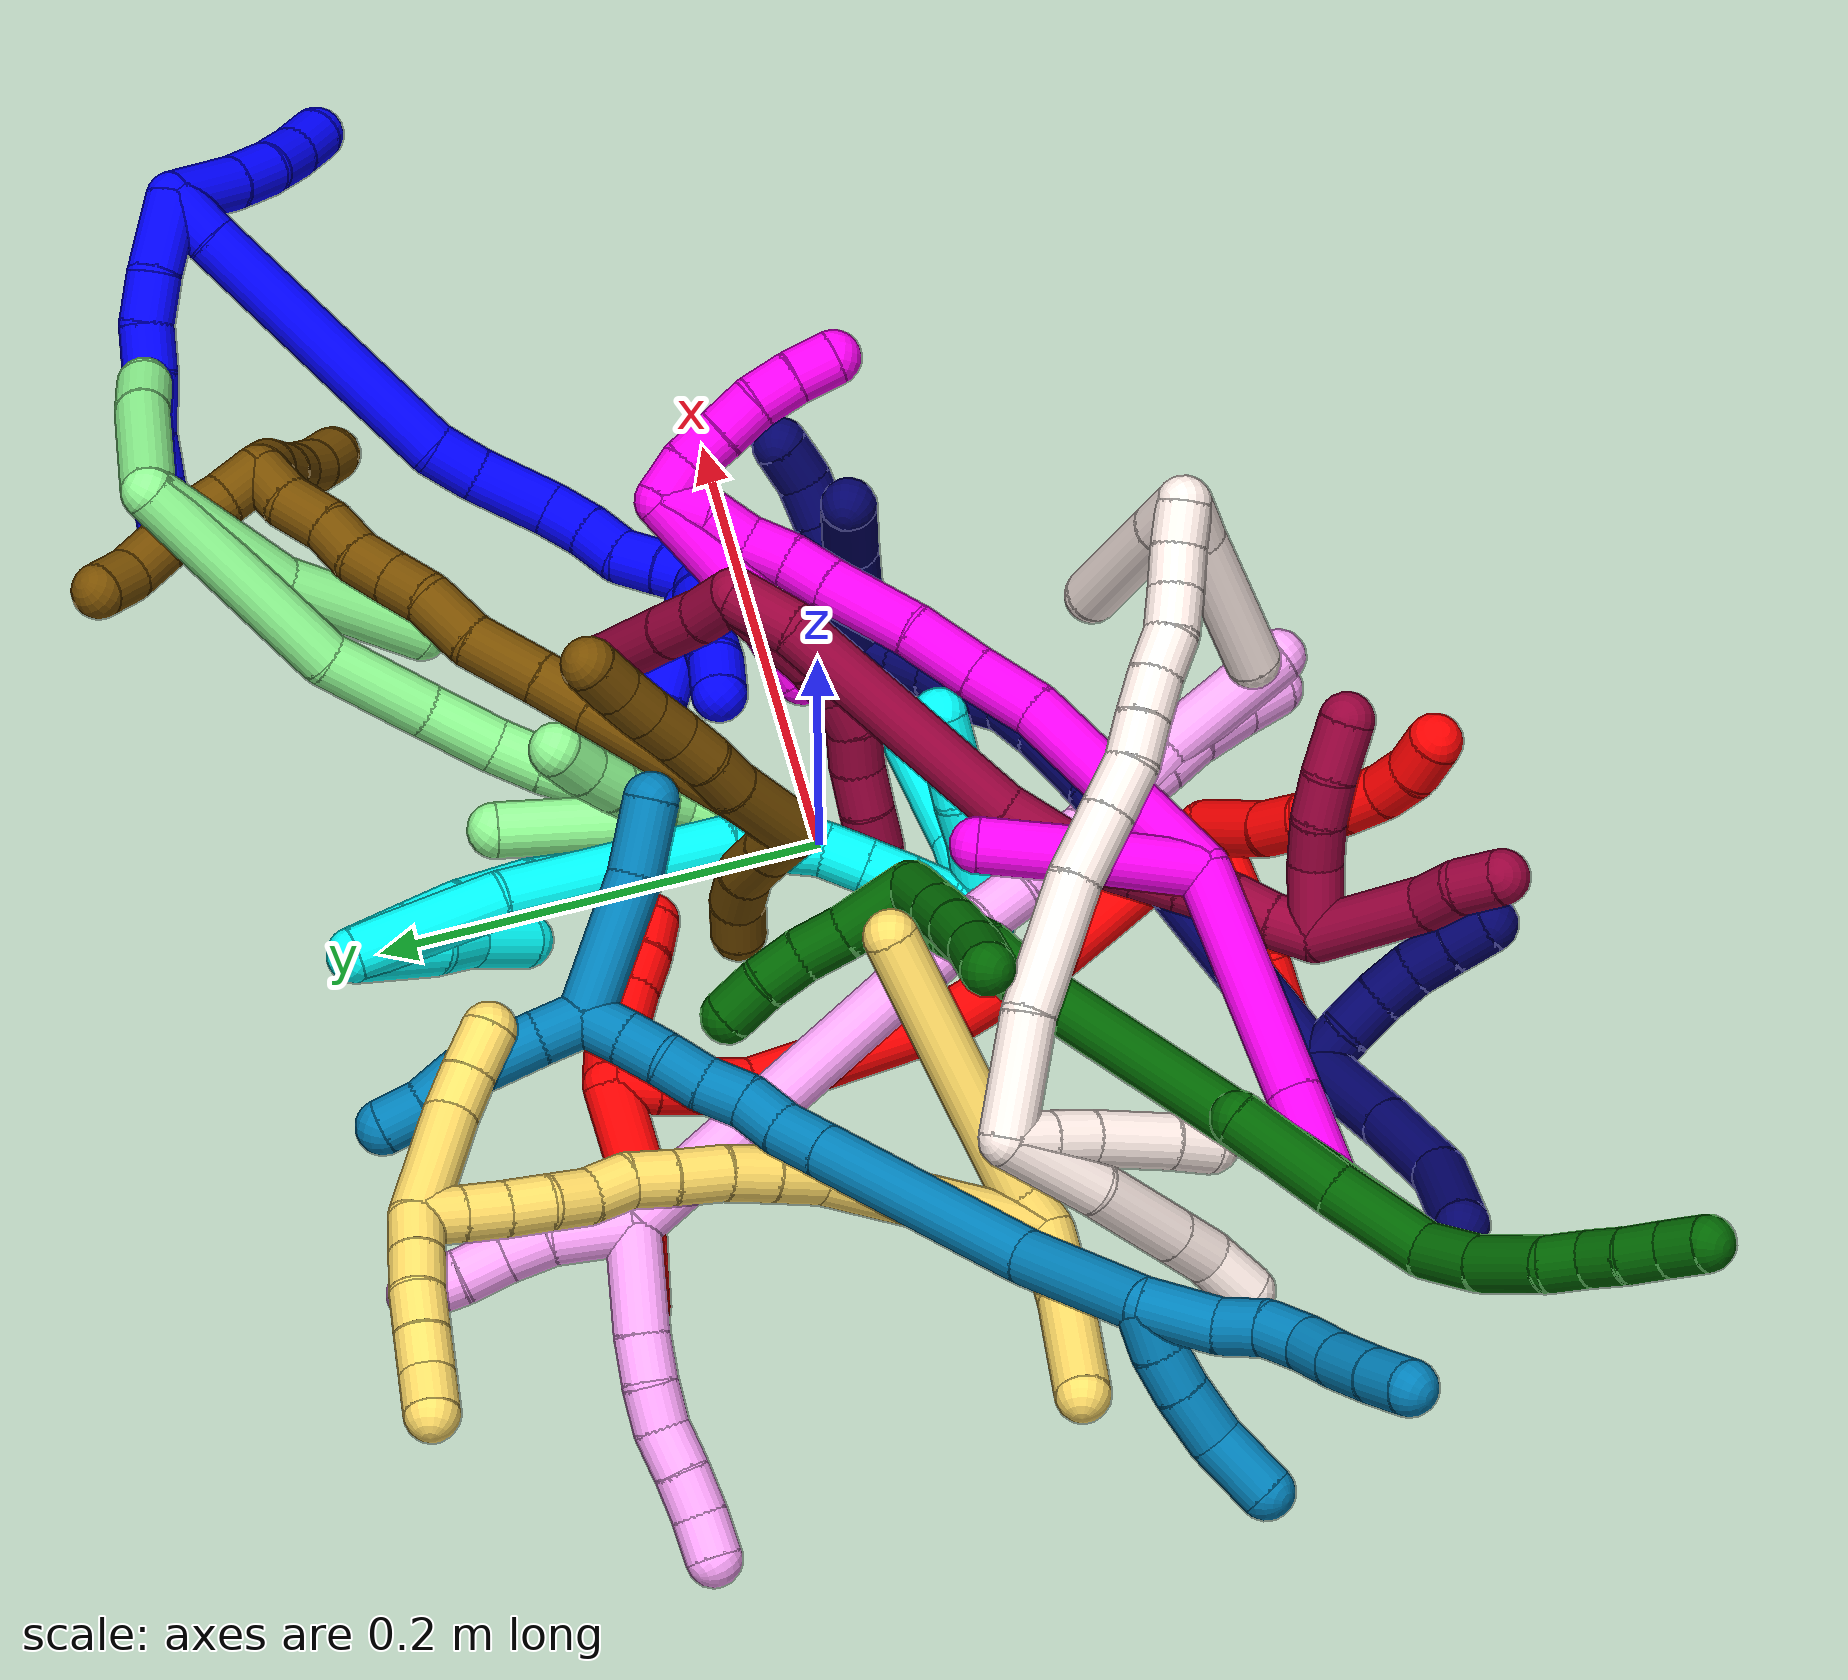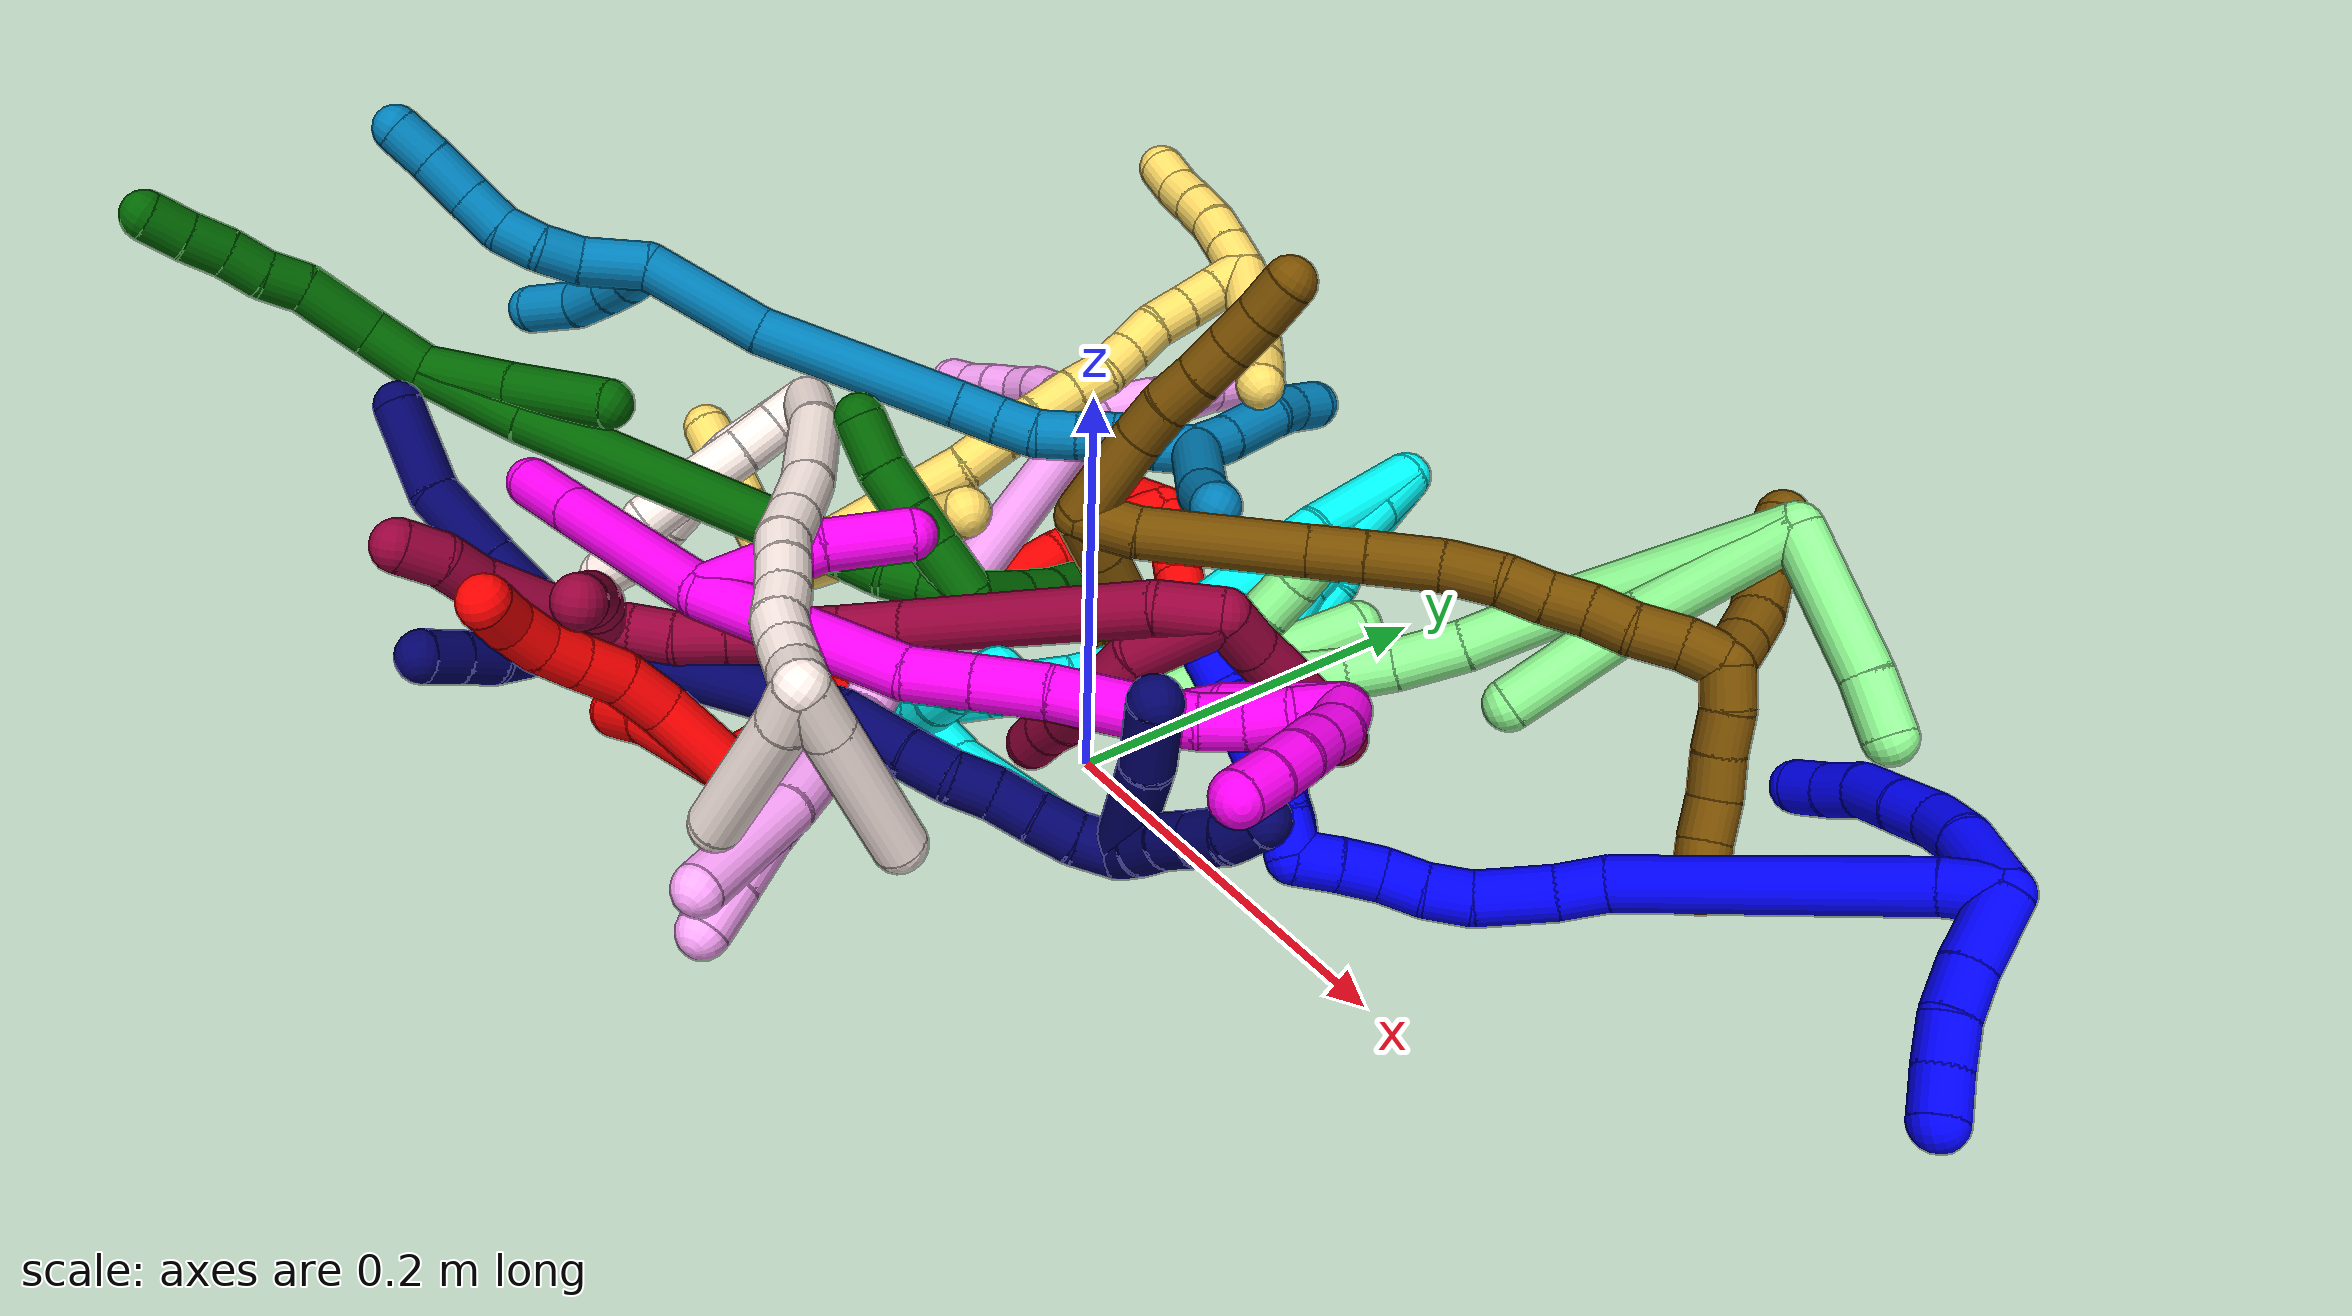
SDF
<sdf version="1.7">
 <world name="default">
  <plugin name="TubeGeneratorPlugin" filename="libtube_generator_plugin.so"/>
  <model name="photoneo_s_sensor">
   <static>1</static>
   <pose>0 0 2 1.57079 1.57079 3.14159</pose>
   <link name="link">
    <inertial><mass>0.1</mass></inertial>
    <sensor name="sensor" type="depth">
     <update_rate>30</update_rate>
     <camera>
      <horizontal_fov>1.22</horizontal_fov>
      <image><width>1920</width><height>1200</height><format>B8G8R8</format></image>
      <clip><near>0.1</near><far>4</far></clip>
      <depth_camera><output>points</output></depth_camera>
     </camera>
     <plugin name="camera_plugin" filename="libgazebo_ros_depth_camera.so">
      <baseline>0.2</baseline>
      <alwaysOn>1</alwaysOn>
      <updateRate>0.0</updateRate>
      <cameraName>camera_ir</cameraName>
      <imageTopicName>/camera/color/image_raw</imageTopicName>
      <cameraInfoTopicName>/camera/color/camera_info</cameraInfoTopicName>
      <depthImageTopicName>/camera/depth/image_raw</depthImageTopicName>
      <depthImageCameraInfoTopicName>/camera/depth/camera_info</depthImageCameraInfoTopicName>
      <pointCloudTopicName>/camera/depth/points</pointCloudTopicName>
      <frameName>fr_optical</frameName>
      <pointCloudCutoff>0.1</pointCloudCutoff>
      <pointCloudCutoffMax>2.0</pointCloudCutoffMax>
      <distortionK1>0</distortionK1>
      <distortionK2>0</distortionK2>
      <distortionK3>0</distortionK3>
      <distortionT1>0</distortionT1>
      <distortionT2>0</distortionT2>
      <CxPrime>0</CxPrime>
      <Cx>0</Cx>
      <Cy>0</Cy>
      <focalLength>0</focalLength>
      <hackBaseline>0</hackBaseline>
     </plugin>
    </sensor>
   </link>
  </model>
  <gravity>0 0 -9.8</gravity>
  <magnetic_field>6e-06 2.3e-05 -4.2e-05</magnetic_field>
  <atmosphere type="adiabatic"/>
  <physics name="default_physics" default="0" type="ode">
   <max_step_size>0.003</max_step_size>
   <real_time_factor>1</real_time_factor>
   <real_time_update_rate>1000</real_time_update_rate>
   <max_contacts>10000</max_contacts>
   <ode>
    <solver>
     <type>quick</type>
     <iters>100</iters>
     <sor>1.3</sor>
     <use_dynamic_moi_rescaling>0</use_dynamic_moi_rescaling>
    </solver>
    <constraints>
     <contact_max_correcting_vel>0</contact_max_correcting_vel>
     <contact_surface_layer>0.001</contact_surface_layer>
     <cfm>0</cfm>
     <erp>0.2</erp>
    </constraints>
   </ode>
  </physics>
  <scene><ambient>0.4 0.4 0.4 1</ambient><background>0.7 0.7 0.7 1</background><shadows>0</shadows></scene>
  <audio><device>default</device></audio>
  <spherical_coordinates>
   <surface_model>EARTH_WGS84</surface_model>
   <latitude_deg>0</latitude_deg>
   <longitude_deg>0</longitude_deg>
   <elevation>0</elevation>
   <heading_deg>0</heading_deg>
  </spherical_coordinates>
  <model name="bin">
   <static>1</static>
   <link name="bottom">
    <collision name="collision-bottom">
     <pose>0 0 -0.01 0 -0 0</pose>
     <geometry><box><size>0.8 0.6 0.02</size></box></geometry>
     <surface>
      <friction><ode><mu>100</mu><mu2>100</mu2></ode></friction>
      <contact><collide_bitmask>65535</collide_bitmask></contact>
     </surface>
    </collision>
   </link>
   <link name="west_wall">
    <collision name="collision-west_wall">
     <pose>-0.41 0 0.1 0 -0 0</pose>
     <geometry><box><size>0.02 0.6 0.2</size></box></geometry>
     <surface>
      <friction><ode><mu>100</mu><mu2>100</mu2></ode></friction>
      <contact><collide_bitmask>65535</collide_bitmask></contact>
     </surface>
    </collision>
   </link>
   <link name="east_wall">
    <collision name="collision-east_wall">
     <pose>0.41 0 0.1 0 -0 0</pose>
     <geometry><box><size>0.02 0.6 0.2</size></box></geometry>
     <surface>
      <friction><ode><mu>100</mu><mu2>100</mu2></ode></friction>
      <contact><collide_bitmask>65535</collide_bitmask></contact>
     </surface>
    </collision>
   </link>
   <link name="south_wall">
    <collision name="collision-south_wall">
     <pose>0 -0.31 0.1 0 -0 0</pose>
     <geometry><box><size>0.8 0.02 0.2</size></box></geometry>
     <surface>
      <friction><ode><mu>100</mu><mu2>100</mu2></ode></friction>
      <contact><collide_bitmask>65535</collide_bitmask></contact>
     </surface>
    </collision>
   </link>
   <link name="north_wall">
    <collision name="collision-north_wall">
     <pose>0 0.31 0.1 0 -0 0</pose>
     <geometry><box><size>0.8 0.02 0.2</size></box></geometry>
     <surface>
      <friction><ode><mu>100</mu><mu2>100</mu2></ode></friction>
      <contact><collide_bitmask>65535</collide_bitmask></contact>
     </surface>
    </collision>
   </link>
  </model>
  <model name="1">
   <static>0</static>
   <link name="1">
    <collision name="collision-cylinder-e_1_2_8">
     <pose>-0.015878 0.002927 -0.009066 -2.82931 -1.03041 2.59923</pose>
     <geometry><cylinder><radius>0.0125</radius><length>0.037034</length></cylinder></geometry>
     <surface>
      <friction><ode><mu>1.16</mu><mu2>1.16</mu2><slip1>0</slip1><slip2>0</slip2></ode></friction>
      <contact><ode><kp>1e+06</kp><kd>1</kd><max_vel>0</max_vel><min_depth>0.001</min_depth></ode></contact>
     </surface>
    </collision>
    <visual name="visual-cylinder-e_1_2_8">
     <pose>-0.015878 0.002927 -0.009066 -2.82931 -1.03041 2.59923</pose>
     <geometry><cylinder><radius>0.0125</radius><length>0.037034</length></cylinder></geometry>
     <material><ambient>0 0 1 1</ambient></material>
    </visual>
    <collision name="collision-cylinder-e_2_8_9">
     <pose>-0.040116 0.009416 -0.02505 -2.66612 -0.821123 2.12569</pose>
     <geometry><cylinder><radius>0.0125</radius><length>0.022842</length></cylinder></geometry>
     <surface>
      <friction><ode><mu>1.16</mu><mu2>1.16</mu2><slip1>0</slip1><slip2>0</slip2></ode></friction>
      <contact><ode><kp>1e+06</kp><kd>1</kd><max_vel>0</max_vel><min_depth>0.001</min_depth></ode></contact>
     </surface>
    </collision>
    <visual name="visual-cylinder-e_2_8_9">
     <pose>-0.040116 0.009416 -0.02505 -2.66612 -0.821123 2.12569</pose>
     <geometry><cylinder><radius>0.0125</radius><length>0.022842</length></cylinder></geometry>
     <material><ambient>0 0 1 1</ambient></material>
    </visual>
    <collision name="collision-cylinder-e_3_9_10">
     <pose>-0.05496 0.015231 -0.040282 -2.87696 -0.645338 2.38392</pose>
     <geometry><cylinder><radius>0.0125</radius><length>0.021561</length></cylinder></geometry>
     <surface>
      <friction><ode><mu>1.16</mu><mu2>1.16</mu2><slip1>0</slip1><slip2>0</slip2></ode></friction>
      <contact><ode><kp>1e+06</kp><kd>1</kd><max_vel>0</max_vel><min_depth>0.001</min_depth></ode></contact>
     </surface>
    </collision>
    <visual name="visual-cylinder-e_3_9_10">
     <pose>-0.05496 0.015231 -0.040282 -2.87696 -0.645338 2.38392</pose>
     <geometry><cylinder><radius>0.0125</radius><length>0.021561</length></cylinder></geometry>
     <material><ambient>0 0 1 1</ambient></material>
    </visual>
    <collision name="collision-cylinder-e_4_10_11">
     <pose>-0.069959 0.021627 -0.058319 -2.73883 -0.678151 2.09219</pose>
     <geometry><cylinder><radius>0.0125</radius><length>0.027147</length></cylinder></geometry>
     <surface>
      <friction><ode><mu>1.16</mu><mu2>1.16</mu2><slip1>0</slip1><slip2>0</slip2></ode></friction>
      <contact><ode><kp>1e+06</kp><kd>1</kd><max_vel>0</max_vel><min_depth>0.001</min_depth></ode></contact>
     </surface>
    </collision>
    <visual name="visual-cylinder-e_4_10_11">
     <pose>-0.069959 0.021627 -0.058319 -2.73883 -0.678151 2.09219</pose>
     <geometry><cylinder><radius>0.0125</radius><length>0.027147</length></cylinder></geometry>
     <material><ambient>0 0 1 1</ambient></material>
    </visual>
    <collision name="collision-cylinder-e_5_11_12">
     <pose>-0.082418 0.029754 -0.07676 -2.71285 -0.390319 1.47438</pose>
     <geometry><cylinder><radius>0.0125</radius><length>0.020726</length></cylinder></geometry>
     <surface>
      <friction><ode><mu>1.16</mu><mu2>1.16</mu2><slip1>0</slip1><slip2>0</slip2></ode></friction>
      <contact><ode><kp>1e+06</kp><kd>1</kd><max_vel>0</max_vel><min_depth>0.001</min_depth></ode></contact>
     </surface>
    </collision>
    <visual name="visual-cylinder-e_5_11_12">
     <pose>-0.082418 0.029754 -0.07676 -2.71285 -0.390319 1.47438</pose>
     <geometry><cylinder><radius>0.0125</radius><length>0.020726</length></cylinder></geometry>
     <material><ambient>0 0 1 1</ambient></material>
    </visual>
    <collision name="collision-cylinder-e_6_12_6">
     <pose>-0.090824 0.037061 -0.094197 -2.77753 -0.446054 1.77804</pose>
     <geometry><cylinder><radius>0.0125</radius><length>0.020689</length></cylinder></geometry>
     <surface>
      <friction><ode><mu>1.16</mu><mu2>1.16</mu2><slip1>0</slip1><slip2>0</slip2></ode></friction>
      <contact><ode><kp>1e+06</kp><kd>1</kd><max_vel>0</max_vel><min_depth>0.001</min_depth></ode></contact>
     </surface>
    </collision>
    <visual name="visual-cylinder-e_6_12_6">
     <pose>-0.090824 0.037061 -0.094197 -2.77753 -0.446054 1.77804</pose>
     <geometry><cylinder><radius>0.0125</radius><length>0.020689</length></cylinder></geometry>
     <material><ambient>0 0 1 1</ambient></material>
    </visual>
    <collision name="collision-cylinder-e_1_2_13">
     <pose>0.015991 0.00128 -0.007322 -2.96845 1.13569 -2.87116</pose>
     <geometry><cylinder><radius>0.0125</radius><length>0.035267</length></cylinder></geometry>
     <surface>
      <friction><ode><mu>1.16</mu><mu2>1.16</mu2><slip1>0</slip1><slip2>0</slip2></ode></friction>
      <contact><ode><kp>1e+06</kp><kd>1</kd><max_vel>0</max_vel><min_depth>0.001</min_depth></ode></contact>
     </surface>
    </collision>
    <visual name="visual-cylinder-e_1_2_13">
     <pose>0.015991 0.00128 -0.007322 -2.96845 1.13569 -2.87116</pose>
     <geometry><cylinder><radius>0.0125</radius><length>0.035267</length></cylinder></geometry>
     <material><ambient>0 0 1 1</ambient></material>
    </visual>
    <collision name="collision-cylinder-e_2_13_14">
     <pose>0.042631 0.003476 -0.01814 -2.88564 1.24358 -2.78626</pose>
     <geometry><cylinder><radius>0.0125</radius><length>0.022494</length></cylinder></geometry>
     <surface>
      <friction><ode><mu>1.16</mu><mu2>1.16</mu2><slip1>0</slip1><slip2>0</slip2></ode></friction>
      <contact><ode><kp>1e+06</kp><kd>1</kd><max_vel>0</max_vel><min_depth>0.001</min_depth></ode></contact>
     </surface>
    </collision>
    <visual name="visual-cylinder-e_2_13_14">
     <pose>0.042631 0.003476 -0.01814 -2.88564 1.24358 -2.78626</pose>
     <geometry><cylinder><radius>0.0125</radius><length>0.022494</length></cylinder></geometry>
     <material><ambient>0 0 1 1</ambient></material>
    </visual>
    <collision name="collision-cylinder-e_3_14_15">
     <pose>0.063443 0.007304 -0.023637 -2.17248 1.23615 -1.86697</pose>
     <geometry><cylinder><radius>0.0125</radius><length>0.021517</length></cylinder></geometry>
     <surface>
      <friction><ode><mu>1.16</mu><mu2>1.16</mu2><slip1>0</slip1><slip2>0</slip2></ode></friction>
      <contact><ode><kp>1e+06</kp><kd>1</kd><max_vel>0</max_vel><min_depth>0.001</min_depth></ode></contact>
     </surface>
    </collision>
    <visual name="visual-cylinder-e_3_14_15">
     <pose>0.063443 0.007304 -0.023637 -2.17248 1.23615 -1.86697</pose>
     <geometry><cylinder><radius>0.0125</radius><length>0.021517</length></cylinder></geometry>
     <material><ambient>0 0 1 1</ambient></material>
    </visual>
    <collision name="collision-cylinder-e_4_15_5">
     <pose>0.083668 0.012411 -0.026761 -2.04426 1.33052 -1.81784</pose>
     <geometry><cylinder><radius>0.0125</radius><length>0.020722</length></cylinder></geometry>
     <surface>
      <friction><ode><mu>1.16</mu><mu2>1.16</mu2><slip1>0</slip1><slip2>0</slip2></ode></friction>
      <contact><ode><kp>1e+06</kp><kd>1</kd><max_vel>0</max_vel><min_depth>0.001</min_depth></ode></contact>
     </surface>
    </collision>
    <visual name="visual-cylinder-e_4_15_5">
     <pose>0.083668 0.012411 -0.026761 -2.04426 1.33052 -1.81784</pose>
     <geometry><cylinder><radius>0.0125</radius><length>0.020722</length></cylinder></geometry>
     <material><ambient>0 0 1 1</ambient></material>
    </visual>
    <collision name="collision-cylinder-e_1_2_16">
     <pose>-0.00139 -0.002299 -0.01219 2.9552 -0.111612 -1.07745</pose>
     <geometry><cylinder><radius>0.0125</radius><length>0.024966</length></cylinder></geometry>
     <surface>
      <friction><ode><mu>1.16</mu><mu2>1.16</mu2><slip1>0</slip1><slip2>0</slip2></ode></friction>
      <contact><ode><kp>1e+06</kp><kd>1</kd><max_vel>0</max_vel><min_depth>0.001</min_depth></ode></contact>
     </surface>
    </collision>
    <visual name="visual-cylinder-e_1_2_16">
     <pose>-0.00139 -0.002299 -0.01219 2.9552 -0.111612 -1.07745</pose>
     <geometry><cylinder><radius>0.0125</radius><length>0.024966</length></cylinder></geometry>
     <material><ambient>0 0 1 1</ambient></material>
    </visual>
    <collision name="collision-cylinder-e_2_16_17">
     <pose>-0.004112 -0.014629 -0.091377 2.99296 -0.019654 -0.262484</pose>
     <geometry><cylinder><radius>0.0125</radius><length>0.135512</length></cylinder></geometry>
     <surface>
      <friction><ode><mu>1.16</mu><mu2>1.16</mu2><slip1>0</slip1><slip2>0</slip2></ode></friction>
      <contact><ode><kp>1e+06</kp><kd>1</kd><max_vel>0</max_vel><min_depth>0.001</min_depth></ode></contact>
     </surface>
    </collision>
    <visual name="visual-cylinder-e_2_16_17">
     <pose>-0.004112 -0.014629 -0.091377 2.99296 -0.019654 -0.262484</pose>
     <geometry><cylinder><radius>0.0125</radius><length>0.135512</length></cylinder></geometry>
     <material><ambient>0 0 1 1</ambient></material>
    </visual>
    <collision name="collision-cylinder-e_3_17_18">
     <pose>-0.002858 -0.026723 -0.16923 2.9539 0.229872 1.77358</pose>
     <geometry><cylinder><radius>0.0125</radius><length>0.022699</length></cylinder></geometry>
     <surface>
      <friction><ode><mu>1.16</mu><mu2>1.16</mu2><slip1>0</slip1><slip2>0</slip2></ode></friction>
      <contact><ode><kp>1e+06</kp><kd>1</kd><max_vel>0</max_vel><min_depth>0.001</min_depth></ode></contact>
     </surface>
    </collision>
    <visual name="visual-cylinder-e_3_17_18">
     <pose>-0.002858 -0.026723 -0.16923 2.9539 0.229872 1.77358</pose>
     <geometry><cylinder><radius>0.0125</radius><length>0.022699</length></cylinder></geometry>
     <material><ambient>0 0 1 1</ambient></material>
    </visual>
    <collision name="collision-cylinder-e_4_18_19">
     <pose>0.003602 -0.035008 -0.196547 2.78014 0.216675 1.07383</pose>
     <geometry><cylinder><radius>0.0125</radius><length>0.036038</length></cylinder></geometry>
     <surface>
      <friction><ode><mu>1.16</mu><mu2>1.16</mu2><slip1>0</slip1><slip2>0</slip2></ode></friction>
      <contact><ode><kp>1e+06</kp><kd>1</kd><max_vel>0</max_vel><min_depth>0.001</min_depth></ode></contact>
     </surface>
    </collision>
    <visual name="visual-cylinder-e_4_18_19">
     <pose>0.003602 -0.035008 -0.196547 2.78014 0.216675 1.07383</pose>
     <geometry><cylinder><radius>0.0125</radius><length>0.036038</length></cylinder></geometry>
     <material><ambient>0 0 1 1</ambient></material>
    </visual>
    <collision name="collision-cylinder-e_5_19_20">
     <pose>0.007598 -0.046131 -0.222005 2.64288 0.011988 0.047065</pose>
     <geometry><cylinder><radius>0.0125</radius><length>0.020492</length></cylinder></geometry>
     <surface>
      <friction><ode><mu>1.16</mu><mu2>1.16</mu2><slip1>0</slip1><slip2>0</slip2></ode></friction>
      <contact><ode><kp>1e+06</kp><kd>1</kd><max_vel>0</max_vel><min_depth>0.001</min_depth></ode></contact>
     </surface>
    </collision>
    <visual name="visual-cylinder-e_5_19_20">
     <pose>0.007598 -0.046131 -0.222005 2.64288 0.011988 0.047065</pose>
     <geometry><cylinder><radius>0.0125</radius><length>0.020492</length></cylinder></geometry>
     <material><ambient>0 0 1 1</ambient></material>
    </visual>
    <collision name="collision-cylinder-e_6_20_21">
     <pose>0.006003 -0.056049 -0.239484 2.60738 -0.172655 -0.612617</pose>
     <geometry><cylinder><radius>0.0125</radius><length>0.020007</length></cylinder></geometry>
     <surface>
      <friction><ode><mu>1.16</mu><mu2>1.16</mu2><slip1>0</slip1><slip2>0</slip2></ode></friction>
      <contact><ode><kp>1e+06</kp><kd>1</kd><max_vel>0</max_vel><min_depth>0.001</min_depth></ode></contact>
     </surface>
    </collision>
    <visual name="visual-cylinder-e_6_20_21">
     <pose>0.006003 -0.056049 -0.239484 2.60738 -0.172655 -0.612617</pose>
     <geometry><cylinder><radius>0.0125</radius><length>0.020007</length></cylinder></geometry>
     <material><ambient>0 0 1 1</ambient></material>
    </visual>
    <collision name="collision-cylinder-e_7_21_22">
     <pose>0.005327 -0.067838 -0.255384 2.40176 0.103428 0.265398</pose>
     <geometry><cylinder><radius>0.0125</radius><length>0.020195</length></cylinder></geometry>
     <surface>
      <friction><ode><mu>1.16</mu><mu2>1.16</mu2><slip1>0</slip1><slip2>0</slip2></ode></friction>
      <contact><ode><kp>1e+06</kp><kd>1</kd><max_vel>0</max_vel><min_depth>0.001</min_depth></ode></contact>
     </surface>
    </collision>
    <visual name="visual-cylinder-e_7_21_22">
     <pose>0.005327 -0.067838 -0.255384 2.40176 0.103428 0.265398</pose>
     <geometry><cylinder><radius>0.0125</radius><length>0.020195</length></cylinder></geometry>
     <material><ambient>0 0 1 1</ambient></material>
    </visual>
    <collision name="collision-cylinder-e_8_22_1">
     <pose>0.00782 -0.081004 -0.270412 2.44277 0.144955 0.393376</pose>
     <geometry><cylinder><radius>0.0125</radius><length>0.020091</length></cylinder></geometry>
     <surface>
      <friction><ode><mu>1.16</mu><mu2>1.16</mu2><slip1>0</slip1><slip2>0</slip2></ode></friction>
      <contact><ode><kp>1e+06</kp><kd>1</kd><max_vel>0</max_vel><min_depth>0.001</min_depth></ode></contact>
     </surface>
    </collision>
    <visual name="visual-cylinder-e_8_22_1">
     <pose>0.00782 -0.081004 -0.270412 2.44277 0.144955 0.393376</pose>
     <geometry><cylinder><radius>0.0125</radius><length>0.020091</length></cylinder></geometry>
     <material><ambient>0 0 1 1</ambient></material>
    </visual>
    <collision name="collision-cylinder-e_1_1_23">
     <pose>-0.005824 -0.080935 -0.285528 -2.43072 -0.990126 1.93698</pose>
     <geometry><cylinder><radius>0.0125</radius><length>0.03611</length></cylinder></geometry>
     <surface>
      <friction><ode><mu>1.16</mu><mu2>1.16</mu2><slip1>0</slip1><slip2>0</slip2></ode></friction>
      <contact><ode><kp>1e+06</kp><kd>1</kd><max_vel>0</max_vel><min_depth>0.001</min_depth></ode></contact>
     </surface>
    </collision>
    <visual name="visual-cylinder-e_1_1_23">
     <pose>-0.005824 -0.080935 -0.285528 -2.43072 -0.990126 1.93698</pose>
     <geometry><cylinder><radius>0.0125</radius><length>0.03611</length></cylinder></geometry>
     <material><ambient>0 0 1 1</ambient></material>
    </visual>
    <collision name="collision-cylinder-e_2_23_24">
     <pose>-0.030597 -0.072384 -0.298075 -2.74878 -1.05732 2.48497</pose>
     <geometry><cylinder><radius>0.0125</radius><length>0.022218</length></cylinder></geometry>
     <surface>
      <friction><ode><mu>1.16</mu><mu2>1.16</mu2><slip1>0</slip1><slip2>0</slip2></ode></friction>
      <contact><ode><kp>1e+06</kp><kd>1</kd><max_vel>0</max_vel><min_depth>0.001</min_depth></ode></contact>
     </surface>
    </collision>
    <visual name="visual-cylinder-e_2_23_24">
     <pose>-0.030597 -0.072384 -0.298075 -2.74878 -1.05732 2.48497</pose>
     <geometry><cylinder><radius>0.0125</radius><length>0.022218</length></cylinder></geometry>
     <material><ambient>0 0 1 1</ambient></material>
    </visual>
    <collision name="collision-cylinder-e_3_24_25">
     <pose>-0.049924 -0.067994 -0.305369 -2.3458 -1.24874 2.08543</pose>
     <geometry><cylinder><radius>0.0125</radius><length>0.020347</length></cylinder></geometry>
     <surface>
      <friction><ode><mu>1.16</mu><mu2>1.16</mu2><slip1>0</slip1><slip2>0</slip2></ode></friction>
      <contact><ode><kp>1e+06</kp><kd>1</kd><max_vel>0</max_vel><min_depth>0.001</min_depth></ode></contact>
     </surface>
    </collision>
    <visual name="visual-cylinder-e_3_24_25">
     <pose>-0.049924 -0.067994 -0.305369 -2.3458 -1.24874 2.08543</pose>
     <geometry><cylinder><radius>0.0125</radius><length>0.020347</length></cylinder></geometry>
     <material><ambient>0 0 1 1</ambient></material>
    </visual>
    <collision name="collision-cylinder-e_4_25_4">
     <pose>-0.068679 -0.064953 -0.313121 -3.00771 -1.02357 2.90401</pose>
     <geometry><cylinder><radius>0.0125</radius><length>0.021325</length></cylinder></geometry>
     <surface>
      <friction><ode><mu>1.16</mu><mu2>1.16</mu2><slip1>0</slip1><slip2>0</slip2></ode></friction>
      <contact><ode><kp>1e+06</kp><kd>1</kd><max_vel>0</max_vel><min_depth>0.001</min_depth></ode></contact>
     </surface>
    </collision>
    <visual name="visual-cylinder-e_4_25_4">
     <pose>-0.068679 -0.064953 -0.313121 -3.00771 -1.02357 2.90401</pose>
     <geometry><cylinder><radius>0.0125</radius><length>0.021325</length></cylinder></geometry>
     <material><ambient>0 0 1 1</ambient></material>
    </visual>
    <collision name="collision-cylinder-e_1_1_26">
     <pose>0.00123 -0.093173 -0.279436 1.81083 -0.934142 -1.14231</pose>
     <geometry><cylinder><radius>0.0125</radius><length>0.02</length></cylinder></geometry>
     <surface>
      <friction><ode><mu>1.16</mu><mu2>1.16</mu2><slip1>0</slip1><slip2>0</slip2></ode></friction>
      <contact><ode><kp>1e+06</kp><kd>1</kd><max_vel>0</max_vel><min_depth>0.001</min_depth></ode></contact>
     </surface>
    </collision>
    <visual name="visual-cylinder-e_1_1_26">
     <pose>0.00123 -0.093173 -0.279436 1.81083 -0.934142 -1.14231</pose>
     <geometry><cylinder><radius>0.0125</radius><length>0.02</length></cylinder></geometry>
     <material><ambient>0 0 1 1</ambient></material>
    </visual>
    <collision name="collision-cylinder-e_2_26_27">
     <pose>-0.014425 -0.104829 -0.283575 2.00486 -0.865509 -1.25241</pose>
     <geometry><cylinder><radius>0.0125</radius><length>0.02</length></cylinder></geometry>
     <surface>
      <friction><ode><mu>1.16</mu><mu2>1.16</mu2><slip1>0</slip1><slip2>0</slip2></ode></friction>
      <contact><ode><kp>1e+06</kp><kd>1</kd><max_vel>0</max_vel><min_depth>0.001</min_depth></ode></contact>
     </surface>
    </collision>
    <visual name="visual-cylinder-e_2_26_27">
     <pose>-0.014425 -0.104829 -0.283575 2.00486 -0.865509 -1.25241</pose>
     <geometry><cylinder><radius>0.0125</radius><length>0.02</length></cylinder></geometry>
     <material><ambient>0 0 1 1</ambient></material>
    </visual>
    <collision name="collision-cylinder-e_3_27_28">
     <pose>-0.029421 -0.116831 -0.289138 2.0047 -0.830408 -1.20813</pose>
     <geometry><cylinder><radius>0.0125</radius><length>0.02</length></cylinder></geometry>
     <surface>
      <friction><ode><mu>1.16</mu><mu2>1.16</mu2><slip1>0</slip1><slip2>0</slip2></ode></friction>
      <contact><ode><kp>1e+06</kp><kd>1</kd><max_vel>0</max_vel><min_depth>0.001</min_depth></ode></contact>
     </surface>
    </collision>
    <visual name="visual-cylinder-e_3_27_28">
     <pose>-0.029421 -0.116831 -0.289138 2.0047 -0.830408 -1.20813</pose>
     <geometry><cylinder><radius>0.0125</radius><length>0.02</length></cylinder></geometry>
     <material><ambient>0 0 1 1</ambient></material>
    </visual>
    <collision name="collision-cylinder-e_4_28_29">
     <pose>-0.043956 -0.128971 -0.295522 2.10345 -0.797087 -1.27027</pose>
     <geometry><cylinder><radius>0.0125</radius><length>0.02</length></cylinder></geometry>
     <surface>
      <friction><ode><mu>1.16</mu><mu2>1.16</mu2><slip1>0</slip1><slip2>0</slip2></ode></friction>
      <contact><ode><kp>1e+06</kp><kd>1</kd><max_vel>0</max_vel><min_depth>0.001</min_depth></ode></contact>
     </surface>
    </collision>
    <visual name="visual-cylinder-e_4_28_29">
     <pose>-0.043956 -0.128971 -0.295522 2.10345 -0.797087 -1.27027</pose>
     <geometry><cylinder><radius>0.0125</radius><length>0.02</length></cylinder></geometry>
     <material><ambient>0 0 1 1</ambient></material>
    </visual>
    <collision name="collision-cylinder-e_5_29_3">
     <pose>-0.059134 -0.138588 -0.303832 2.49465 -0.931407 -1.96504</pose>
     <geometry><cylinder><radius>0.0125</radius><length>0.02</length></cylinder></geometry>
     <surface>
      <friction><ode><mu>1.16</mu><mu2>1.16</mu2><slip1>0</slip1><slip2>0</slip2></ode></friction>
      <contact><ode><kp>1e+06</kp><kd>1</kd><max_vel>0</max_vel><min_depth>0.001</min_depth></ode></contact>
     </surface>
    </collision>
    <visual name="visual-cylinder-e_5_29_3">
     <pose>-0.059134 -0.138588 -0.303832 2.49465 -0.931407 -1.96504</pose>
     <geometry><cylinder><radius>0.0125</radius><length>0.02</length></cylinder></geometry>
     <material><ambient>0 0 1 1</ambient></material>
    </visual>
    <collision name="collision-sphere-3">
     <pose>-0.067159 -0.142184 -0.308594 0 -0 0</pose>
     <geometry><sphere><radius>0.0125</radius></sphere></geometry>
     <surface>
      <friction><ode><mu>1.16</mu><mu2>1.16</mu2><slip1>0</slip1><slip2>0</slip2></ode></friction>
      <contact><ode><kp>1e+06</kp><kd>1</kd><max_vel>0</max_vel><min_depth>0.001</min_depth></ode></contact>
     </surface>
    </collision>
    <visual name="visual-sphere-3">
     <pose>-0.067159 -0.142184 -0.308594 0 -0 0</pose>
     <geometry><sphere><radius>0.0125</radius></sphere></geometry>
     <material><ambient>0 0 1 1</ambient></material>
    </visual>
    <collision name="collision-sphere-29">
     <pose>-0.05111 -0.134991 -0.299071 0 -0 0</pose>
     <geometry><sphere><radius>0.0125</radius></sphere></geometry>
     <surface>
      <friction><ode><mu>1.16</mu><mu2>1.16</mu2><slip1>0</slip1><slip2>0</slip2></ode></friction>
      <contact><ode><kp>1e+06</kp><kd>1</kd><max_vel>0</max_vel><min_depth>0.001</min_depth></ode></contact>
     </surface>
    </collision>
    <visual name="visual-sphere-29">
     <pose>-0.05111 -0.134991 -0.299071 0 -0 0</pose>
     <geometry><sphere><radius>0.0125</radius></sphere></geometry>
     <material><ambient>0 0 1 1</ambient></material>
    </visual>
    <collision name="collision-sphere-28">
     <pose>-0.036803 -0.122951 -0.291974 0 -0 0</pose>
     <geometry><sphere><radius>0.0125</radius></sphere></geometry>
     <surface>
      <friction><ode><mu>1.16</mu><mu2>1.16</mu2><slip1>0</slip1><slip2>0</slip2></ode></friction>
      <contact><ode><kp>1e+06</kp><kd>1</kd><max_vel>0</max_vel><min_depth>0.001</min_depth></ode></contact>
     </surface>
    </collision>
    <visual name="visual-sphere-28">
     <pose>-0.036803 -0.122951 -0.291974 0 -0 0</pose>
     <geometry><sphere><radius>0.0125</radius></sphere></geometry>
     <material><ambient>0 0 1 1</ambient></material>
    </visual>
    <collision name="collision-sphere-27">
     <pose>-0.022039 -0.11071 -0.286302 0 -0 0</pose>
     <geometry><sphere><radius>0.0125</radius></sphere></geometry>
     <surface>
      <friction><ode><mu>1.16</mu><mu2>1.16</mu2><slip1>0</slip1><slip2>0</slip2></ode></friction>
      <contact><ode><kp>1e+06</kp><kd>1</kd><max_vel>0</max_vel><min_depth>0.001</min_depth></ode></contact>
     </surface>
    </collision>
    <visual name="visual-sphere-27">
     <pose>-0.022039 -0.11071 -0.286302 0 -0 0</pose>
     <geometry><sphere><radius>0.0125</radius></sphere></geometry>
     <material><ambient>0 0 1 1</ambient></material>
    </visual>
    <collision name="collision-sphere-26">
     <pose>-0.006811 -0.098947 -0.280849 0 -0 0</pose>
     <geometry><sphere><radius>0.0125</radius></sphere></geometry>
     <surface>
      <friction><ode><mu>1.16</mu><mu2>1.16</mu2><slip1>0</slip1><slip2>0</slip2></ode></friction>
      <contact><ode><kp>1e+06</kp><kd>1</kd><max_vel>0</max_vel><min_depth>0.001</min_depth></ode></contact>
     </surface>
    </collision>
    <visual name="visual-sphere-26">
     <pose>-0.006811 -0.098947 -0.280849 0 -0 0</pose>
     <geometry><sphere><radius>0.0125</radius></sphere></geometry>
     <material><ambient>0 0 1 1</ambient></material>
    </visual>
    <collision name="collision-sphere-4">
     <pose>-0.077785 -0.064213 -0.318619 0 -0 0</pose>
     <geometry><sphere><radius>0.0125</radius></sphere></geometry>
     <surface>
      <friction><ode><mu>1.16</mu><mu2>1.16</mu2><slip1>0</slip1><slip2>0</slip2></ode></friction>
      <contact><ode><kp>1e+06</kp><kd>1</kd><max_vel>0</max_vel><min_depth>0.001</min_depth></ode></contact>
     </surface>
    </collision>
    <visual name="visual-sphere-4">
     <pose>-0.077785 -0.064213 -0.318619 0 -0 0</pose>
     <geometry><sphere><radius>0.0125</radius></sphere></geometry>
     <material><ambient>0 0 1 1</ambient></material>
    </visual>
    <collision name="collision-sphere-25">
     <pose>-0.059574 -0.065694 -0.307623 0 -0 0</pose>
     <geometry><sphere><radius>0.0125</radius></sphere></geometry>
     <surface>
      <friction><ode><mu>1.16</mu><mu2>1.16</mu2><slip1>0</slip1><slip2>0</slip2></ode></friction>
      <contact><ode><kp>1e+06</kp><kd>1</kd><max_vel>0</max_vel><min_depth>0.001</min_depth></ode></contact>
     </surface>
    </collision>
    <visual name="visual-sphere-25">
     <pose>-0.059574 -0.065694 -0.307623 0 -0 0</pose>
     <geometry><sphere><radius>0.0125</radius></sphere></geometry>
     <material><ambient>0 0 1 1</ambient></material>
    </visual>
    <collision name="collision-sphere-24">
     <pose>-0.040273 -0.070295 -0.303116 0 -0 0</pose>
     <geometry><sphere><radius>0.0125</radius></sphere></geometry>
     <surface>
      <friction><ode><mu>1.16</mu><mu2>1.16</mu2><slip1>0</slip1><slip2>0</slip2></ode></friction>
      <contact><ode><kp>1e+06</kp><kd>1</kd><max_vel>0</max_vel><min_depth>0.001</min_depth></ode></contact>
     </surface>
    </collision>
    <visual name="visual-sphere-24">
     <pose>-0.040273 -0.070295 -0.303116 0 -0 0</pose>
     <geometry><sphere><radius>0.0125</radius></sphere></geometry>
     <material><ambient>0 0 1 1</ambient></material>
    </visual>
    <collision name="collision-sphere-23">
     <pose>-0.02092 -0.074473 -0.293034 0 -0 0</pose>
     <geometry><sphere><radius>0.0125</radius></sphere></geometry>
     <surface>
      <friction><ode><mu>1.16</mu><mu2>1.16</mu2><slip1>0</slip1><slip2>0</slip2></ode></friction>
      <contact><ode><kp>1e+06</kp><kd>1</kd><max_vel>0</max_vel><min_depth>0.001</min_depth></ode></contact>
     </surface>
    </collision>
    <visual name="visual-sphere-23">
     <pose>-0.02092 -0.074473 -0.293034 0 -0 0</pose>
     <geometry><sphere><radius>0.0125</radius></sphere></geometry>
     <material><ambient>0 0 1 1</ambient></material>
    </visual>
    <collision name="collision-sphere-1">
     <pose>0.009271 -0.087398 -0.278022 0 -0 0</pose>
     <geometry><sphere><radius>0.0125</radius></sphere></geometry>
     <surface>
      <friction><ode><mu>1.16</mu><mu2>1.16</mu2><slip1>0</slip1><slip2>0</slip2></ode></friction>
      <contact><ode><kp>1e+06</kp><kd>1</kd><max_vel>0</max_vel><min_depth>0.001</min_depth></ode></contact>
     </surface>
    </collision>
    <visual name="visual-sphere-1">
     <pose>0.009271 -0.087398 -0.278022 0 -0 0</pose>
     <geometry><sphere><radius>0.0125</radius></sphere></geometry>
     <material><ambient>0 0 1 1</ambient></material>
    </visual>
    <collision name="collision-sphere-22">
     <pose>0.006369 -0.074609 -0.262802 0 -0 0</pose>
     <geometry><sphere><radius>0.0125</radius></sphere></geometry>
     <surface>
      <friction><ode><mu>1.16</mu><mu2>1.16</mu2><slip1>0</slip1><slip2>0</slip2></ode></friction>
      <contact><ode><kp>1e+06</kp><kd>1</kd><max_vel>0</max_vel><min_depth>0.001</min_depth></ode></contact>
     </surface>
    </collision>
    <visual name="visual-sphere-22">
     <pose>0.006369 -0.074609 -0.262802 0 -0 0</pose>
     <geometry><sphere><radius>0.0125</radius></sphere></geometry>
     <material><ambient>0 0 1 1</ambient></material>
    </visual>
    <collision name="collision-sphere-21">
     <pose>0.004284 -0.061067 -0.247966 0 -0 0</pose>
     <geometry><sphere><radius>0.0125</radius></sphere></geometry>
     <surface>
      <friction><ode><mu>1.16</mu><mu2>1.16</mu2><slip1>0</slip1><slip2>0</slip2></ode></friction>
      <contact><ode><kp>1e+06</kp><kd>1</kd><max_vel>0</max_vel><min_depth>0.001</min_depth></ode></contact>
     </surface>
    </collision>
    <visual name="visual-sphere-21">
     <pose>0.004284 -0.061067 -0.247966 0 -0 0</pose>
     <geometry><sphere><radius>0.0125</radius></sphere></geometry>
     <material><ambient>0 0 1 1</ambient></material>
    </visual>
    <collision name="collision-sphere-12">
     <pose>-0.086361 0.033738 -0.085476 0 -0 0</pose>
     <geometry><sphere><radius>0.0125</radius></sphere></geometry>
     <surface>
      <friction><ode><mu>1.16</mu><mu2>1.16</mu2><slip1>0</slip1><slip2>0</slip2></ode></friction>
      <contact><ode><kp>1e+06</kp><kd>1</kd><max_vel>0</max_vel><min_depth>0.001</min_depth></ode></contact>
     </surface>
    </collision>
    <visual name="visual-sphere-12">
     <pose>-0.086361 0.033738 -0.085476 0 -0 0</pose>
     <geometry><sphere><radius>0.0125</radius></sphere></geometry>
     <material><ambient>0 0 1 1</ambient></material>
    </visual>
    <collision name="collision-sphere-11">
     <pose>-0.078475 0.02577 -0.068044 0 -0 0</pose>
     <geometry><sphere><radius>0.0125</radius></sphere></geometry>
     <surface>
      <friction><ode><mu>1.16</mu><mu2>1.16</mu2><slip1>0</slip1><slip2>0</slip2></ode></friction>
      <contact><ode><kp>1e+06</kp><kd>1</kd><max_vel>0</max_vel><min_depth>0.001</min_depth></ode></contact>
     </surface>
    </collision>
    <visual name="visual-sphere-11">
     <pose>-0.078475 0.02577 -0.068044 0 -0 0</pose>
     <geometry><sphere><radius>0.0125</radius></sphere></geometry>
     <material><ambient>0 0 1 1</ambient></material>
    </visual>
    <collision name="collision-sphere-10">
     <pose>-0.061444 0.017484 -0.048595 0 -0 0</pose>
     <geometry><sphere><radius>0.0125</radius></sphere></geometry>
     <surface>
      <friction><ode><mu>1.16</mu><mu2>1.16</mu2><slip1>0</slip1><slip2>0</slip2></ode></friction>
      <contact><ode><kp>1e+06</kp><kd>1</kd><max_vel>0</max_vel><min_depth>0.001</min_depth></ode></contact>
     </surface>
    </collision>
    <visual name="visual-sphere-10">
     <pose>-0.061444 0.017484 -0.048595 0 -0 0</pose>
     <geometry><sphere><radius>0.0125</radius></sphere></geometry>
     <material><ambient>0 0 1 1</ambient></material>
    </visual>
    <collision name="collision-sphere-9">
     <pose>-0.048475 0.012978 -0.031969 0 -0 0</pose>
     <geometry><sphere><radius>0.0125</radius></sphere></geometry>
     <surface>
      <friction><ode><mu>1.16</mu><mu2>1.16</mu2><slip1>0</slip1><slip2>0</slip2></ode></friction>
      <contact><ode><kp>1e+06</kp><kd>1</kd><max_vel>0</max_vel><min_depth>0.001</min_depth></ode></contact>
     </surface>
    </collision>
    <visual name="visual-sphere-9">
     <pose>-0.048475 0.012978 -0.031969 0 -0 0</pose>
     <geometry><sphere><radius>0.0125</radius></sphere></geometry>
     <material><ambient>0 0 1 1</ambient></material>
    </visual>
    <collision name="collision-sphere-2">
     <geometry><sphere><radius>0.0125</radius></sphere></geometry>
     <surface>
      <friction><ode><mu>1.16</mu><mu2>1.16</mu2><slip1>0</slip1><slip2>0</slip2></ode></friction>
      <contact><ode><kp>1e+06</kp><kd>1</kd><max_vel>0</max_vel><min_depth>0.001</min_depth></ode></contact>
     </surface>
    </collision>
    <visual name="visual-sphere-2">
     <geometry><sphere><radius>0.0125</radius></sphere></geometry>
     <material><ambient>0 0 1 1</ambient></material>
    </visual>
    <collision name="collision-sphere-19">
     <pose>0.007476 -0.041231 -0.213008 0 -0 0</pose>
     <geometry><sphere><radius>0.0125</radius></sphere></geometry>
     <surface>
      <friction><ode><mu>1.16</mu><mu2>1.16</mu2><slip1>0</slip1><slip2>0</slip2></ode></friction>
      <contact><ode><kp>1e+06</kp><kd>1</kd><max_vel>0</max_vel><min_depth>0.001</min_depth></ode></contact>
     </surface>
    </collision>
    <visual name="visual-sphere-19">
     <pose>0.007476 -0.041231 -0.213008 0 -0 0</pose>
     <geometry><sphere><radius>0.0125</radius></sphere></geometry>
     <material><ambient>0 0 1 1</ambient></material>
    </visual>
    <collision name="collision-sphere-8">
     <pose>-0.031757 0.005854 -0.018131 0 -0 0</pose>
     <geometry><sphere><radius>0.0125</radius></sphere></geometry>
     <surface>
      <friction><ode><mu>1.16</mu><mu2>1.16</mu2><slip1>0</slip1><slip2>0</slip2></ode></friction>
      <contact><ode><kp>1e+06</kp><kd>1</kd><max_vel>0</max_vel><min_depth>0.001</min_depth></ode></contact>
     </surface>
    </collision>
    <visual name="visual-sphere-8">
     <pose>-0.031757 0.005854 -0.018131 0 -0 0</pose>
     <geometry><sphere><radius>0.0125</radius></sphere></geometry>
     <material><ambient>0 0 1 1</ambient></material>
    </visual>
    <collision name="collision-sphere-6">
     <pose>-0.095286 0.040385 -0.102918 0 -0 0</pose>
     <geometry><sphere><radius>0.0125</radius></sphere></geometry>
     <surface>
      <friction><ode><mu>1.16</mu><mu2>1.16</mu2><slip1>0</slip1><slip2>0</slip2></ode></friction>
      <contact><ode><kp>1e+06</kp><kd>1</kd><max_vel>0</max_vel><min_depth>0.001</min_depth></ode></contact>
     </surface>
    </collision>
    <visual name="visual-sphere-6">
     <pose>-0.095286 0.040385 -0.102918 0 -0 0</pose>
     <geometry><sphere><radius>0.0125</radius></sphere></geometry>
     <material><ambient>0 0 1 1</ambient></material>
    </visual>
    <collision name="collision-sphere-13">
     <pose>0.031981 0.002561 -0.014643 0 -0 0</pose>
     <geometry><sphere><radius>0.0125</radius></sphere></geometry>
     <surface>
      <friction><ode><mu>1.16</mu><mu2>1.16</mu2><slip1>0</slip1><slip2>0</slip2></ode></friction>
      <contact><ode><kp>1e+06</kp><kd>1</kd><max_vel>0</max_vel><min_depth>0.001</min_depth></ode></contact>
     </surface>
    </collision>
    <visual name="visual-sphere-13">
     <pose>0.031981 0.002561 -0.014643 0 -0 0</pose>
     <geometry><sphere><radius>0.0125</radius></sphere></geometry>
     <material><ambient>0 0 1 1</ambient></material>
    </visual>
    <collision name="collision-sphere-14">
     <pose>0.053281 0.004391 -0.021637 0 -0 0</pose>
     <geometry><sphere><radius>0.0125</radius></sphere></geometry>
     <surface>
      <friction><ode><mu>1.16</mu><mu2>1.16</mu2><slip1>0</slip1><slip2>0</slip2></ode></friction>
      <contact><ode><kp>1e+06</kp><kd>1</kd><max_vel>0</max_vel><min_depth>0.001</min_depth></ode></contact>
     </surface>
    </collision>
    <visual name="visual-sphere-14">
     <pose>0.053281 0.004391 -0.021637 0 -0 0</pose>
     <geometry><sphere><radius>0.0125</radius></sphere></geometry>
     <material><ambient>0 0 1 1</ambient></material>
    </visual>
    <collision name="collision-sphere-15">
     <pose>0.073605 0.010217 -0.025637 0 -0 0</pose>
     <geometry><sphere><radius>0.0125</radius></sphere></geometry>
     <surface>
      <friction><ode><mu>1.16</mu><mu2>1.16</mu2><slip1>0</slip1><slip2>0</slip2></ode></friction>
      <contact><ode><kp>1e+06</kp><kd>1</kd><max_vel>0</max_vel><min_depth>0.001</min_depth></ode></contact>
     </surface>
    </collision>
    <visual name="visual-sphere-15">
     <pose>0.073605 0.010217 -0.025637 0 -0 0</pose>
     <geometry><sphere><radius>0.0125</radius></sphere></geometry>
     <material><ambient>0 0 1 1</ambient></material>
    </visual>
    <collision name="collision-sphere-5">
     <pose>0.093732 0.014606 -0.027886 0 -0 0</pose>
     <geometry><sphere><radius>0.0125</radius></sphere></geometry>
     <surface>
      <friction><ode><mu>1.16</mu><mu2>1.16</mu2><slip1>0</slip1><slip2>0</slip2></ode></friction>
      <contact><ode><kp>1e+06</kp><kd>1</kd><max_vel>0</max_vel><min_depth>0.001</min_depth></ode></contact>
     </surface>
    </collision>
    <visual name="visual-sphere-5">
     <pose>0.093732 0.014606 -0.027886 0 -0 0</pose>
     <geometry><sphere><radius>0.0125</radius></sphere></geometry>
     <material><ambient>0 0 1 1</ambient></material>
    </visual>
    <collision name="collision-sphere-16">
     <pose>-0.002781 -0.004598 -0.024381 0 -0 0</pose>
     <geometry><sphere><radius>0.0125</radius></sphere></geometry>
     <surface>
      <friction><ode><mu>1.16</mu><mu2>1.16</mu2><slip1>0</slip1><slip2>0</slip2></ode></friction>
      <contact><ode><kp>1e+06</kp><kd>1</kd><max_vel>0</max_vel><min_depth>0.001</min_depth></ode></contact>
     </surface>
    </collision>
    <visual name="visual-sphere-16">
     <pose>-0.002781 -0.004598 -0.024381 0 -0 0</pose>
     <geometry><sphere><radius>0.0125</radius></sphere></geometry>
     <material><ambient>0 0 1 1</ambient></material>
    </visual>
    <collision name="collision-sphere-17">
     <pose>-0.005444 -0.024661 -0.158373 0 -0 0</pose>
     <geometry><sphere><radius>0.0125</radius></sphere></geometry>
     <surface>
      <friction><ode><mu>1.16</mu><mu2>1.16</mu2><slip1>0</slip1><slip2>0</slip2></ode></friction>
      <contact><ode><kp>1e+06</kp><kd>1</kd><max_vel>0</max_vel><min_depth>0.001</min_depth></ode></contact>
     </surface>
    </collision>
    <visual name="visual-sphere-17">
     <pose>-0.005444 -0.024661 -0.158373 0 -0 0</pose>
     <geometry><sphere><radius>0.0125</radius></sphere></geometry>
     <material><ambient>0 0 1 1</ambient></material>
    </visual>
    <collision name="collision-sphere-18">
     <pose>-0.000272 -0.028785 -0.180087 0 -0 0</pose>
     <geometry><sphere><radius>0.0125</radius></sphere></geometry>
     <surface>
      <friction><ode><mu>1.16</mu><mu2>1.16</mu2><slip1>0</slip1><slip2>0</slip2></ode></friction>
      <contact><ode><kp>1e+06</kp><kd>1</kd><max_vel>0</max_vel><min_depth>0.001</min_depth></ode></contact>
     </surface>
    </collision>
    <visual name="visual-sphere-18">
     <pose>-0.000272 -0.028785 -0.180087 0 -0 0</pose>
     <geometry><sphere><radius>0.0125</radius></sphere></geometry>
     <material><ambient>0 0 1 1</ambient></material>
    </visual>
    <collision name="collision-sphere-20">
     <pose>0.007721 -0.051032 -0.231003 0 -0 0</pose>
     <geometry><sphere><radius>0.0125</radius></sphere></geometry>
     <surface>
      <friction><ode><mu>1.16</mu><mu2>1.16</mu2><slip1>0</slip1><slip2>0</slip2></ode></friction>
      <contact><ode><kp>1e+06</kp><kd>1</kd><max_vel>0</max_vel><min_depth>0.001</min_depth></ode></contact>
     </surface>
    </collision>
    <visual name="visual-sphere-20">
     <pose>0.007721 -0.051032 -0.231003 0 -0 0</pose>
     <geometry><sphere><radius>0.0125</radius></sphere></geometry>
     <material><ambient>0 0 1 1</ambient></material>
    </visual>
    <inertial>
     <pose>-0.0131 -0.033012 -0.148034 0 -0 0</pose>
     <mass>0.75</mass>
     <inertia>
      <ixx>0.000147</ixx>
      <ixy>0</ixy>
      <ixz>0</ixz>
      <iyy>-0.000226</iyy>
      <iyz>0</iyz>
      <izz>1.4e-05</izz>
     </inertia>
    </inertial>
   </link>
   <pose>0.34876 0.20337 0.069878 -1.10475 0.307354 -0.857321</pose>
  </model>
  <model name="2">
   <static>0</static>
   <link name="2">
    <collision name="collision-cylinder-e_1_2_8">
     <pose>-0.004645 -0.010701 0.017431 0.550582 -0.223329 -0.063324</pose>
     <geometry><cylinder><radius>0.0125</radius><length>0.041949</length></cylinder></geometry>
     <surface>
      <friction><ode><mu>1.16</mu><mu2>1.16</mu2><slip1>0</slip1><slip2>0</slip2></ode></friction>
      <contact><ode><kp>1e+06</kp><kd>1</kd><max_vel>0</max_vel><min_depth>0.001</min_depth></ode></contact>
     </surface>
    </collision>
    <visual name="visual-cylinder-e_1_2_8">
     <pose>-0.004645 -0.010701 0.017431 0.550582 -0.223329 -0.063324</pose>
     <geometry><cylinder><radius>0.0125</radius><length>0.041949</length></cylinder></geometry>
     <material><ambient>1 0 0 1</ambient></material>
    </visual>
    <collision name="collision-cylinder-e_2_8_9">
     <pose>-0.009765 -0.027564 0.045403 0.529022 -0.038807 -0.010512</pose>
     <geometry><cylinder><radius>0.0125</radius><length>0.024439</length></cylinder></geometry>
     <surface>
      <friction><ode><mu>1.16</mu><mu2>1.16</mu2><slip1>0</slip1><slip2>0</slip2></ode></friction>
      <contact><ode><kp>1e+06</kp><kd>1</kd><max_vel>0</max_vel><min_depth>0.001</min_depth></ode></contact>
     </surface>
    </collision>
    <visual name="visual-cylinder-e_2_8_9">
     <pose>-0.009765 -0.027564 0.045403 0.529022 -0.038807 -0.010512</pose>
     <geometry><cylinder><radius>0.0125</radius><length>0.024439</length></cylinder></geometry>
     <material><ambient>1 0 0 1</ambient></material>
    </visual>
    <collision name="collision-cylinder-e_3_9_10">
     <pose>-0.008199 -0.040696 0.06479 0.667277 0.179194 0.062255</pose>
     <geometry><cylinder><radius>0.0125</radius><length>0.022889</length></cylinder></geometry>
     <surface>
      <friction><ode><mu>1.16</mu><mu2>1.16</mu2><slip1>0</slip1><slip2>0</slip2></ode></friction>
      <contact><ode><kp>1e+06</kp><kd>1</kd><max_vel>0</max_vel><min_depth>0.001</min_depth></ode></contact>
     </surface>
    </collision>
    <visual name="visual-cylinder-e_3_9_10">
     <pose>-0.008199 -0.040696 0.06479 0.667277 0.179194 0.062255</pose>
     <geometry><cylinder><radius>0.0125</radius><length>0.022889</length></cylinder></geometry>
     <material><ambient>1 0 0 1</ambient></material>
    </visual>
    <collision name="collision-cylinder-e_4_10_11">
     <pose>-0.004139 -0.053255 0.081749 0.603341 0.202289 0.06314</pose>
     <geometry><cylinder><radius>0.0125</radius><length>0.020116</length></cylinder></geometry>
     <surface>
      <friction><ode><mu>1.16</mu><mu2>1.16</mu2><slip1>0</slip1><slip2>0</slip2></ode></friction>
      <contact><ode><kp>1e+06</kp><kd>1</kd><max_vel>0</max_vel><min_depth>0.001</min_depth></ode></contact>
     </surface>
    </collision>
    <visual name="visual-cylinder-e_4_10_11">
     <pose>-0.004139 -0.053255 0.081749 0.603341 0.202289 0.06314</pose>
     <geometry><cylinder><radius>0.0125</radius><length>0.020116</length></cylinder></geometry>
     <material><ambient>1 0 0 1</ambient></material>
    </visual>
    <collision name="collision-cylinder-e_5_11_12">
     <pose>-0.0001 -0.062543 0.099075 0.381654 0.200519 0.038861</pose>
     <geometry><cylinder><radius>0.0125</radius><length>0.020261</length></cylinder></geometry>
     <surface>
      <friction><ode><mu>1.16</mu><mu2>1.16</mu2><slip1>0</slip1><slip2>0</slip2></ode></friction>
      <contact><ode><kp>1e+06</kp><kd>1</kd><max_vel>0</max_vel><min_depth>0.001</min_depth></ode></contact>
     </surface>
    </collision>
    <visual name="visual-cylinder-e_5_11_12">
     <pose>-0.0001 -0.062543 0.099075 0.381654 0.200519 0.038861</pose>
     <geometry><cylinder><radius>0.0125</radius><length>0.020261</length></cylinder></geometry>
     <material><ambient>1 0 0 1</ambient></material>
    </visual>
    <collision name="collision-cylinder-e_6_12_6">
     <pose>0.005462 -0.067622 0.117724 0.145361 0.355872 0.026186</pose>
     <geometry><cylinder><radius>0.0125</radius><length>0.020347</length></cylinder></geometry>
     <surface>
      <friction><ode><mu>1.16</mu><mu2>1.16</mu2><slip1>0</slip1><slip2>0</slip2></ode></friction>
      <contact><ode><kp>1e+06</kp><kd>1</kd><max_vel>0</max_vel><min_depth>0.001</min_depth></ode></contact>
     </surface>
    </collision>
    <visual name="visual-cylinder-e_6_12_6">
     <pose>0.005462 -0.067622 0.117724 0.145361 0.355872 0.026186</pose>
     <geometry><cylinder><radius>0.0125</radius><length>0.020347</length></cylinder></geometry>
     <material><ambient>1 0 0 1</ambient></material>
    </visual>
    <collision name="collision-cylinder-e_1_2_13">
     <pose>-0.025052 -0.020902 -0.00314 1.71992 -0.869986 -0.989816</pose>
     <geometry><cylinder><radius>0.0125</radius><length>0.065555</length></cylinder></geometry>
     <surface>
      <friction><ode><mu>1.16</mu><mu2>1.16</mu2><slip1>0</slip1><slip2>0</slip2></ode></friction>
      <contact><ode><kp>1e+06</kp><kd>1</kd><max_vel>0</max_vel><min_depth>0.001</min_depth></ode></contact>
     </surface>
    </collision>
    <visual name="visual-cylinder-e_1_2_13">
     <pose>-0.025052 -0.020902 -0.00314 1.71992 -0.869986 -0.989816</pose>
     <geometry><cylinder><radius>0.0125</radius><length>0.065555</length></cylinder></geometry>
     <material><ambient>1 0 0 1</ambient></material>
    </visual>
    <collision name="collision-cylinder-e_2_13_5">
     <pose>-0.062243 -0.052446 -0.012283 2.08432 -0.782075 -1.22926</pose>
     <geometry><cylinder><radius>0.0125</radius><length>0.034445</length></cylinder></geometry>
     <surface>
      <friction><ode><mu>1.16</mu><mu2>1.16</mu2><slip1>0</slip1><slip2>0</slip2></ode></friction>
      <contact><ode><kp>1e+06</kp><kd>1</kd><max_vel>0</max_vel><min_depth>0.001</min_depth></ode></contact>
     </surface>
    </collision>
    <visual name="visual-cylinder-e_2_13_5">
     <pose>-0.062243 -0.052446 -0.012283 2.08432 -0.782075 -1.22926</pose>
     <geometry><cylinder><radius>0.0125</radius><length>0.034445</length></cylinder></geometry>
     <material><ambient>1 0 0 1</ambient></material>
    </visual>
    <collision name="collision-cylinder-e_1_2_14">
     <pose>-0.034031 0.022167 -0.017127 -2.22862 -0.882105 1.53133</pose>
     <geometry><cylinder><radius>0.0125</radius><length>0.088155</length></cylinder></geometry>
     <surface>
      <friction><ode><mu>1.16</mu><mu2>1.16</mu2><slip1>0</slip1><slip2>0</slip2></ode></friction>
      <contact><ode><kp>1e+06</kp><kd>1</kd><max_vel>0</max_vel><min_depth>0.001</min_depth></ode></contact>
     </surface>
    </collision>
    <visual name="visual-cylinder-e_1_2_14">
     <pose>-0.034031 0.022167 -0.017127 -2.22862 -0.882105 1.53133</pose>
     <geometry><cylinder><radius>0.0125</radius><length>0.088155</length></cylinder></geometry>
     <material><ambient>1 0 0 1</ambient></material>
    </visual>
    <collision name="collision-cylinder-e_2_14_15">
     <pose>-0.089006 0.06115 -0.038265 -1.80496 -0.880726 1.0762</pose>
     <geometry><cylinder><radius>0.0125</radius><length>0.054314</length></cylinder></geometry>
     <surface>
      <friction><ode><mu>1.16</mu><mu2>1.16</mu2><slip1>0</slip1><slip2>0</slip2></ode></friction>
      <contact><ode><kp>1e+06</kp><kd>1</kd><max_vel>0</max_vel><min_depth>0.001</min_depth></ode></contact>
     </surface>
    </collision>
    <visual name="visual-cylinder-e_2_14_15">
     <pose>-0.089006 0.06115 -0.038265 -1.80496 -0.880726 1.0762</pose>
     <geometry><cylinder><radius>0.0125</radius><length>0.054314</length></cylinder></geometry>
     <material><ambient>1 0 0 1</ambient></material>
    </visual>
    <collision name="collision-cylinder-e_3_15_16">
     <pose>-0.139382 0.115102 -0.048819 -1.74518 -0.662761 0.778164</pose>
     <geometry><cylinder><radius>0.0125</radius><length>0.09567</length></cylinder></geometry>
     <surface>
      <friction><ode><mu>1.16</mu><mu2>1.16</mu2><slip1>0</slip1><slip2>0</slip2></ode></friction>
      <contact><ode><kp>1e+06</kp><kd>1</kd><max_vel>0</max_vel><min_depth>0.001</min_depth></ode></contact>
     </surface>
    </collision>
    <visual name="visual-cylinder-e_3_15_16">
     <pose>-0.139382 0.115102 -0.048819 -1.74518 -0.662761 0.778164</pose>
     <geometry><cylinder><radius>0.0125</radius><length>0.09567</length></cylinder></geometry>
     <material><ambient>1 0 0 1</ambient></material>
    </visual>
    <collision name="collision-cylinder-e_4_16_17">
     <pose>-0.176189 0.171547 -0.056271 -1.61788 -0.364431 0.381593</pose>
     <geometry><cylinder><radius>0.0125</radius><length>0.041378</length></cylinder></geometry>
     <surface>
      <friction><ode><mu>1.16</mu><mu2>1.16</mu2><slip1>0</slip1><slip2>0</slip2></ode></friction>
      <contact><ode><kp>1e+06</kp><kd>1</kd><max_vel>0</max_vel><min_depth>0.001</min_depth></ode></contact>
     </surface>
    </collision>
    <visual name="visual-cylinder-e_4_16_17">
     <pose>-0.176189 0.171547 -0.056271 -1.61788 -0.364431 0.381593</pose>
     <geometry><cylinder><radius>0.0125</radius><length>0.041378</length></cylinder></geometry>
     <material><ambient>1 0 0 1</ambient></material>
    </visual>
    <collision name="collision-cylinder-e_5_17_1">
     <pose>-0.186855 0.200554 -0.057288 -1.58188 -0.32728 0.330864</pose>
     <geometry><cylinder><radius>0.0125</radius><length>0.020483</length></cylinder></geometry>
     <surface>
      <friction><ode><mu>1.16</mu><mu2>1.16</mu2><slip1>0</slip1><slip2>0</slip2></ode></friction>
      <contact><ode><kp>1e+06</kp><kd>1</kd><max_vel>0</max_vel><min_depth>0.001</min_depth></ode></contact>
     </surface>
    </collision>
    <visual name="visual-cylinder-e_5_17_1">
     <pose>-0.186855 0.200554 -0.057288 -1.58188 -0.32728 0.330864</pose>
     <geometry><cylinder><radius>0.0125</radius><length>0.020483</length></cylinder></geometry>
     <material><ambient>1 0 0 1</ambient></material>
    </visual>
    <collision name="collision-cylinder-e_1_1_18">
     <pose>-0.181571 0.211352 -0.062419 -2.92581 1.03064 -2.76368</pose>
     <geometry><cylinder><radius>0.0125</radius><length>0.02</length></cylinder></geometry>
     <surface>
      <friction><ode><mu>1.16</mu><mu2>1.16</mu2><slip1>0</slip1><slip2>0</slip2></ode></friction>
      <contact><ode><kp>1e+06</kp><kd>1</kd><max_vel>0</max_vel><min_depth>0.001</min_depth></ode></contact>
     </surface>
    </collision>
    <visual name="visual-cylinder-e_1_1_18">
     <pose>-0.181571 0.211352 -0.062419 -2.92581 1.03064 -2.76368</pose>
     <geometry><cylinder><radius>0.0125</radius><length>0.02</length></cylinder></geometry>
     <material><ambient>1 0 0 1</ambient></material>
    </visual>
    <collision name="collision-cylinder-e_2_18_19">
     <pose>-0.163592 0.212236 -0.07084 3.07764 1.22345 3.05045</pose>
     <geometry><cylinder><radius>0.0125</radius><length>0.02</length></cylinder></geometry>
     <surface>
      <friction><ode><mu>1.16</mu><mu2>1.16</mu2><slip1>0</slip1><slip2>0</slip2></ode></friction>
      <contact><ode><kp>1e+06</kp><kd>1</kd><max_vel>0</max_vel><min_depth>0.001</min_depth></ode></contact>
     </surface>
    </collision>
    <visual name="visual-cylinder-e_2_18_19">
     <pose>-0.163592 0.212236 -0.07084 3.07764 1.22345 3.05045</pose>
     <geometry><cylinder><radius>0.0125</radius><length>0.02</length></cylinder></geometry>
     <material><ambient>1 0 0 1</ambient></material>
    </visual>
    <collision name="collision-cylinder-e_3_19_20">
     <pose>-0.144284 0.212193 -0.075603 -3.01397 1.43259 -2.99505</pose>
     <geometry><cylinder><radius>0.0125</radius><length>0.02</length></cylinder></geometry>
     <surface>
      <friction><ode><mu>1.16</mu><mu2>1.16</mu2><slip1>0</slip1><slip2>0</slip2></ode></friction>
      <contact><ode><kp>1e+06</kp><kd>1</kd><max_vel>0</max_vel><min_depth>0.001</min_depth></ode></contact>
     </surface>
    </collision>
    <visual name="visual-cylinder-e_3_19_20">
     <pose>-0.144284 0.212193 -0.075603 -3.01397 1.43259 -2.99505</pose>
     <geometry><cylinder><radius>0.0125</radius><length>0.02</length></cylinder></geometry>
     <material><ambient>1 0 0 1</ambient></material>
    </visual>
    <collision name="collision-cylinder-e_4_20_21">
     <pose>-0.124438 0.212089 -0.078012 2.8791 1.46262 2.84945</pose>
     <geometry><cylinder><radius>0.0125</radius><length>0.02</length></cylinder></geometry>
     <surface>
      <friction><ode><mu>1.16</mu><mu2>1.16</mu2><slip1>0</slip1><slip2>0</slip2></ode></friction>
      <contact><ode><kp>1e+06</kp><kd>1</kd><max_vel>0</max_vel><min_depth>0.001</min_depth></ode></contact>
     </surface>
    </collision>
    <visual name="visual-cylinder-e_4_20_21">
     <pose>-0.124438 0.212089 -0.078012 2.8791 1.46262 2.84945</pose>
     <geometry><cylinder><radius>0.0125</radius><length>0.02</length></cylinder></geometry>
     <material><ambient>1 0 0 1</ambient></material>
    </visual>
    <collision name="collision-cylinder-e_5_21_4">
     <pose>-0.104656 0.212521 -0.080685 -2.72934 1.39193 -2.65108</pose>
     <geometry><cylinder><radius>0.0125</radius><length>0.02</length></cylinder></geometry>
     <surface>
      <friction><ode><mu>1.16</mu><mu2>1.16</mu2><slip1>0</slip1><slip2>0</slip2></ode></friction>
      <contact><ode><kp>1e+06</kp><kd>1</kd><max_vel>0</max_vel><min_depth>0.001</min_depth></ode></contact>
     </surface>
    </collision>
    <visual name="visual-cylinder-e_5_21_4">
     <pose>-0.104656 0.212521 -0.080685 -2.72934 1.39193 -2.65108</pose>
     <geometry><cylinder><radius>0.0125</radius><length>0.02</length></cylinder></geometry>
     <material><ambient>1 0 0 1</ambient></material>
    </visual>
    <collision name="collision-cylinder-e_1_1_22">
     <pose>-0.204158 0.200026 -0.060617 1.87602 -0.917659 -1.18554</pose>
     <geometry><cylinder><radius>0.0125</radius><length>0.035284</length></cylinder></geometry>
     <surface>
      <friction><ode><mu>1.16</mu><mu2>1.16</mu2><slip1>0</slip1><slip2>0</slip2></ode></friction>
      <contact><ode><kp>1e+06</kp><kd>1</kd><max_vel>0</max_vel><min_depth>0.001</min_depth></ode></contact>
     </surface>
    </collision>
    <visual name="visual-cylinder-e_1_1_22">
     <pose>-0.204158 0.200026 -0.060617 1.87602 -0.917659 -1.18554</pose>
     <geometry><cylinder><radius>0.0125</radius><length>0.035284</length></cylinder></geometry>
     <material><ambient>1 0 0 1</ambient></material>
    </visual>
    <collision name="collision-cylinder-e_2_22_3">
     <pose>-0.244937 0.176995 -0.076745 2.36011 -0.974173 -1.81958</pose>
     <geometry><cylinder><radius>0.0125</radius><length>0.064716</length></cylinder></geometry>
     <surface>
      <friction><ode><mu>1.16</mu><mu2>1.16</mu2><slip1>0</slip1><slip2>0</slip2></ode></friction>
      <contact><ode><kp>1e+06</kp><kd>1</kd><max_vel>0</max_vel><min_depth>0.001</min_depth></ode></contact>
     </surface>
    </collision>
    <visual name="visual-cylinder-e_2_22_3">
     <pose>-0.244937 0.176995 -0.076745 2.36011 -0.974173 -1.81958</pose>
     <geometry><cylinder><radius>0.0125</radius><length>0.064716</length></cylinder></geometry>
     <material><ambient>1 0 0 1</ambient></material>
    </visual>
    <collision name="collision-sphere-3">
     <pose>-0.271705 0.16419 -0.08965 0 -0 0</pose>
     <geometry><sphere><radius>0.0125</radius></sphere></geometry>
     <surface>
      <friction><ode><mu>1.16</mu><mu2>1.16</mu2><slip1>0</slip1><slip2>0</slip2></ode></friction>
      <contact><ode><kp>1e+06</kp><kd>1</kd><max_vel>0</max_vel><min_depth>0.001</min_depth></ode></contact>
     </surface>
    </collision>
    <visual name="visual-sphere-3">
     <pose>-0.271705 0.16419 -0.08965 0 -0 0</pose>
     <geometry><sphere><radius>0.0125</radius></sphere></geometry>
     <material><ambient>1 0 0 1</ambient></material>
    </visual>
    <collision name="collision-sphere-22">
     <pose>-0.218169 0.189801 -0.063839 0 -0 0</pose>
     <geometry><sphere><radius>0.0125</radius></sphere></geometry>
     <surface>
      <friction><ode><mu>1.16</mu><mu2>1.16</mu2><slip1>0</slip1><slip2>0</slip2></ode></friction>
      <contact><ode><kp>1e+06</kp><kd>1</kd><max_vel>0</max_vel><min_depth>0.001</min_depth></ode></contact>
     </surface>
    </collision>
    <visual name="visual-sphere-22">
     <pose>-0.218169 0.189801 -0.063839 0 -0 0</pose>
     <geometry><sphere><radius>0.0125</radius></sphere></geometry>
     <material><ambient>1 0 0 1</ambient></material>
    </visual>
    <collision name="collision-sphere-4">
     <pose>-0.094816 0.213234 -0.082315 0 -0 0</pose>
     <geometry><sphere><radius>0.0125</radius></sphere></geometry>
     <surface>
      <friction><ode><mu>1.16</mu><mu2>1.16</mu2><slip1>0</slip1><slip2>0</slip2></ode></friction>
      <contact><ode><kp>1e+06</kp><kd>1</kd><max_vel>0</max_vel><min_depth>0.001</min_depth></ode></contact>
     </surface>
    </collision>
    <visual name="visual-sphere-4">
     <pose>-0.094816 0.213234 -0.082315 0 -0 0</pose>
     <geometry><sphere><radius>0.0125</radius></sphere></geometry>
     <material><ambient>1 0 0 1</ambient></material>
    </visual>
    <collision name="collision-sphere-21">
     <pose>-0.114497 0.211808 -0.079055 0 -0 0</pose>
     <geometry><sphere><radius>0.0125</radius></sphere></geometry>
     <surface>
      <friction><ode><mu>1.16</mu><mu2>1.16</mu2><slip1>0</slip1><slip2>0</slip2></ode></friction>
      <contact><ode><kp>1e+06</kp><kd>1</kd><max_vel>0</max_vel><min_depth>0.001</min_depth></ode></contact>
     </surface>
    </collision>
    <visual name="visual-sphere-21">
     <pose>-0.114497 0.211808 -0.079055 0 -0 0</pose>
     <geometry><sphere><radius>0.0125</radius></sphere></geometry>
     <material><ambient>1 0 0 1</ambient></material>
    </visual>
    <collision name="collision-sphere-20">
     <pose>-0.13438 0.212369 -0.076969 0 -0 0</pose>
     <geometry><sphere><radius>0.0125</radius></sphere></geometry>
     <surface>
      <friction><ode><mu>1.16</mu><mu2>1.16</mu2><slip1>0</slip1><slip2>0</slip2></ode></friction>
      <contact><ode><kp>1e+06</kp><kd>1</kd><max_vel>0</max_vel><min_depth>0.001</min_depth></ode></contact>
     </surface>
    </collision>
    <visual name="visual-sphere-20">
     <pose>-0.13438 0.212369 -0.076969 0 -0 0</pose>
     <geometry><sphere><radius>0.0125</radius></sphere></geometry>
     <material><ambient>1 0 0 1</ambient></material>
    </visual>
    <collision name="collision-sphere-12">
     <pose>0.001918 -0.06624 0.108288 0 -0 0</pose>
     <geometry><sphere><radius>0.0125</radius></sphere></geometry>
     <surface>
      <friction><ode><mu>1.16</mu><mu2>1.16</mu2><slip1>0</slip1><slip2>0</slip2></ode></friction>
      <contact><ode><kp>1e+06</kp><kd>1</kd><max_vel>0</max_vel><min_depth>0.001</min_depth></ode></contact>
     </surface>
    </collision>
    <visual name="visual-sphere-12">
     <pose>0.001918 -0.06624 0.108288 0 -0 0</pose>
     <geometry><sphere><radius>0.0125</radius></sphere></geometry>
     <material><ambient>1 0 0 1</ambient></material>
    </visual>
    <collision name="collision-sphere-11">
     <pose>-0.002118 -0.058845 0.089862 0 -0 0</pose>
     <geometry><sphere><radius>0.0125</radius></sphere></geometry>
     <surface>
      <friction><ode><mu>1.16</mu><mu2>1.16</mu2><slip1>0</slip1><slip2>0</slip2></ode></friction>
      <contact><ode><kp>1e+06</kp><kd>1</kd><max_vel>0</max_vel><min_depth>0.001</min_depth></ode></contact>
     </surface>
    </collision>
    <visual name="visual-sphere-11">
     <pose>-0.002118 -0.058845 0.089862 0 -0 0</pose>
     <geometry><sphere><radius>0.0125</radius></sphere></geometry>
     <material><ambient>1 0 0 1</ambient></material>
    </visual>
    <collision name="collision-sphere-10">
     <pose>-0.006159 -0.047665 0.073636 0 -0 0</pose>
     <geometry><sphere><radius>0.0125</radius></sphere></geometry>
     <surface>
      <friction><ode><mu>1.16</mu><mu2>1.16</mu2><slip1>0</slip1><slip2>0</slip2></ode></friction>
      <contact><ode><kp>1e+06</kp><kd>1</kd><max_vel>0</max_vel><min_depth>0.001</min_depth></ode></contact>
     </surface>
    </collision>
    <visual name="visual-sphere-10">
     <pose>-0.006159 -0.047665 0.073636 0 -0 0</pose>
     <geometry><sphere><radius>0.0125</radius></sphere></geometry>
     <material><ambient>1 0 0 1</ambient></material>
    </visual>
    <collision name="collision-sphere-9">
     <pose>-0.010239 -0.033727 0.055944 0 -0 0</pose>
     <geometry><sphere><radius>0.0125</radius></sphere></geometry>
     <surface>
      <friction><ode><mu>1.16</mu><mu2>1.16</mu2><slip1>0</slip1><slip2>0</slip2></ode></friction>
      <contact><ode><kp>1e+06</kp><kd>1</kd><max_vel>0</max_vel><min_depth>0.001</min_depth></ode></contact>
     </surface>
    </collision>
    <visual name="visual-sphere-9">
     <pose>-0.010239 -0.033727 0.055944 0 -0 0</pose>
     <geometry><sphere><radius>0.0125</radius></sphere></geometry>
     <material><ambient>1 0 0 1</ambient></material>
    </visual>
    <collision name="collision-sphere-2">
     <geometry><sphere><radius>0.0125</radius></sphere></geometry>
     <surface>
      <friction><ode><mu>1.16</mu><mu2>1.16</mu2><slip1>0</slip1><slip2>0</slip2></ode></friction>
      <contact><ode><kp>1e+06</kp><kd>1</kd><max_vel>0</max_vel><min_depth>0.001</min_depth></ode></contact>
     </surface>
    </collision>
    <visual name="visual-sphere-2">
     <geometry><sphere><radius>0.0125</radius></sphere></geometry>
     <material><ambient>1 0 0 1</ambient></material>
    </visual>
    <collision name="collision-sphere-19">
     <pose>-0.154189 0.212018 -0.074237 0 -0 0</pose>
     <geometry><sphere><radius>0.0125</radius></sphere></geometry>
     <surface>
      <friction><ode><mu>1.16</mu><mu2>1.16</mu2><slip1>0</slip1><slip2>0</slip2></ode></friction>
      <contact><ode><kp>1e+06</kp><kd>1</kd><max_vel>0</max_vel><min_depth>0.001</min_depth></ode></contact>
     </surface>
    </collision>
    <visual name="visual-sphere-19">
     <pose>-0.154189 0.212018 -0.074237 0 -0 0</pose>
     <geometry><sphere><radius>0.0125</radius></sphere></geometry>
     <material><ambient>1 0 0 1</ambient></material>
    </visual>
    <collision name="collision-sphere-8">
     <pose>-0.009291 -0.021402 0.034862 0 -0 0</pose>
     <geometry><sphere><radius>0.0125</radius></sphere></geometry>
     <surface>
      <friction><ode><mu>1.16</mu><mu2>1.16</mu2><slip1>0</slip1><slip2>0</slip2></ode></friction>
      <contact><ode><kp>1e+06</kp><kd>1</kd><max_vel>0</max_vel><min_depth>0.001</min_depth></ode></contact>
     </surface>
    </collision>
    <visual name="visual-sphere-8">
     <pose>-0.009291 -0.021402 0.034862 0 -0 0</pose>
     <geometry><sphere><radius>0.0125</radius></sphere></geometry>
     <material><ambient>1 0 0 1</ambient></material>
    </visual>
    <collision name="collision-sphere-6">
     <pose>0.009007 -0.069003 0.127159 0 -0 0</pose>
     <geometry><sphere><radius>0.0125</radius></sphere></geometry>
     <surface>
      <friction><ode><mu>1.16</mu><mu2>1.16</mu2><slip1>0</slip1><slip2>0</slip2></ode></friction>
      <contact><ode><kp>1e+06</kp><kd>1</kd><max_vel>0</max_vel><min_depth>0.001</min_depth></ode></contact>
     </surface>
    </collision>
    <visual name="visual-sphere-6">
     <pose>0.009007 -0.069003 0.127159 0 -0 0</pose>
     <geometry><sphere><radius>0.0125</radius></sphere></geometry>
     <material><ambient>1 0 0 1</ambient></material>
    </visual>
    <collision name="collision-sphere-13">
     <pose>-0.050105 -0.041803 -0.006281 0 -0 0</pose>
     <geometry><sphere><radius>0.0125</radius></sphere></geometry>
     <surface>
      <friction><ode><mu>1.16</mu><mu2>1.16</mu2><slip1>0</slip1><slip2>0</slip2></ode></friction>
      <contact><ode><kp>1e+06</kp><kd>1</kd><max_vel>0</max_vel><min_depth>0.001</min_depth></ode></contact>
     </surface>
    </collision>
    <visual name="visual-sphere-13">
     <pose>-0.050105 -0.041803 -0.006281 0 -0 0</pose>
     <geometry><sphere><radius>0.0125</radius></sphere></geometry>
     <material><ambient>1 0 0 1</ambient></material>
    </visual>
    <collision name="collision-sphere-5">
     <pose>-0.07438 -0.063088 -0.018285 0 -0 0</pose>
     <geometry><sphere><radius>0.0125</radius></sphere></geometry>
     <surface>
      <friction><ode><mu>1.16</mu><mu2>1.16</mu2><slip1>0</slip1><slip2>0</slip2></ode></friction>
      <contact><ode><kp>1e+06</kp><kd>1</kd><max_vel>0</max_vel><min_depth>0.001</min_depth></ode></contact>
     </surface>
    </collision>
    <visual name="visual-sphere-5">
     <pose>-0.07438 -0.063088 -0.018285 0 -0 0</pose>
     <geometry><sphere><radius>0.0125</radius></sphere></geometry>
     <material><ambient>1 0 0 1</ambient></material>
    </visual>
    <collision name="collision-sphere-14">
     <pose>-0.068063 0.044334 -0.034254 0 -0 0</pose>
     <geometry><sphere><radius>0.0125</radius></sphere></geometry>
     <surface>
      <friction><ode><mu>1.16</mu><mu2>1.16</mu2><slip1>0</slip1><slip2>0</slip2></ode></friction>
      <contact><ode><kp>1e+06</kp><kd>1</kd><max_vel>0</max_vel><min_depth>0.001</min_depth></ode></contact>
     </surface>
    </collision>
    <visual name="visual-sphere-14">
     <pose>-0.068063 0.044334 -0.034254 0 -0 0</pose>
     <geometry><sphere><radius>0.0125</radius></sphere></geometry>
     <material><ambient>1 0 0 1</ambient></material>
    </visual>
    <collision name="collision-sphere-15">
     <pose>-0.109949 0.077966 -0.042276 0 -0 0</pose>
     <geometry><sphere><radius>0.0125</radius></sphere></geometry>
     <surface>
      <friction><ode><mu>1.16</mu><mu2>1.16</mu2><slip1>0</slip1><slip2>0</slip2></ode></friction>
      <contact><ode><kp>1e+06</kp><kd>1</kd><max_vel>0</max_vel><min_depth>0.001</min_depth></ode></contact>
     </surface>
    </collision>
    <visual name="visual-sphere-15">
     <pose>-0.109949 0.077966 -0.042276 0 -0 0</pose>
     <geometry><sphere><radius>0.0125</radius></sphere></geometry>
     <material><ambient>1 0 0 1</ambient></material>
    </visual>
    <collision name="collision-sphere-16">
     <pose>-0.168815 0.152238 -0.055361 0 -0 0</pose>
     <geometry><sphere><radius>0.0125</radius></sphere></geometry>
     <surface>
      <friction><ode><mu>1.16</mu><mu2>1.16</mu2><slip1>0</slip1><slip2>0</slip2></ode></friction>
      <contact><ode><kp>1e+06</kp><kd>1</kd><max_vel>0</max_vel><min_depth>0.001</min_depth></ode></contact>
     </surface>
    </collision>
    <visual name="visual-sphere-16">
     <pose>-0.168815 0.152238 -0.055361 0 -0 0</pose>
     <geometry><sphere><radius>0.0125</radius></sphere></geometry>
     <material><ambient>1 0 0 1</ambient></material>
    </visual>
    <collision name="collision-sphere-17">
     <pose>-0.183563 0.190856 -0.057181 0 -0 0</pose>
     <geometry><sphere><radius>0.0125</radius></sphere></geometry>
     <surface>
      <friction><ode><mu>1.16</mu><mu2>1.16</mu2><slip1>0</slip1><slip2>0</slip2></ode></friction>
      <contact><ode><kp>1e+06</kp><kd>1</kd><max_vel>0</max_vel><min_depth>0.001</min_depth></ode></contact>
     </surface>
    </collision>
    <visual name="visual-sphere-17">
     <pose>-0.183563 0.190856 -0.057181 0 -0 0</pose>
     <geometry><sphere><radius>0.0125</radius></sphere></geometry>
     <material><ambient>1 0 0 1</ambient></material>
    </visual>
    <collision name="collision-sphere-1">
     <pose>-0.190147 0.210251 -0.057396 0 -0 0</pose>
     <geometry><sphere><radius>0.0125</radius></sphere></geometry>
     <surface>
      <friction><ode><mu>1.16</mu><mu2>1.16</mu2><slip1>0</slip1><slip2>0</slip2></ode></friction>
      <contact><ode><kp>1e+06</kp><kd>1</kd><max_vel>0</max_vel><min_depth>0.001</min_depth></ode></contact>
     </surface>
    </collision>
    <visual name="visual-sphere-1">
     <pose>-0.190147 0.210251 -0.057396 0 -0 0</pose>
     <geometry><sphere><radius>0.0125</radius></sphere></geometry>
     <material><ambient>1 0 0 1</ambient></material>
    </visual>
    <collision name="collision-sphere-18">
     <pose>-0.172995 0.212453 -0.067442 0 -0 0</pose>
     <geometry><sphere><radius>0.0125</radius></sphere></geometry>
     <surface>
      <friction><ode><mu>1.16</mu><mu2>1.16</mu2><slip1>0</slip1><slip2>0</slip2></ode></friction>
      <contact><ode><kp>1e+06</kp><kd>1</kd><max_vel>0</max_vel><min_depth>0.001</min_depth></ode></contact>
     </surface>
    </collision>
    <visual name="visual-sphere-18">
     <pose>-0.172995 0.212453 -0.067442 0 -0 0</pose>
     <geometry><sphere><radius>0.0125</radius></sphere></geometry>
     <material><ambient>1 0 0 1</ambient></material>
    </visual>
    <inertial>
     <pose>-0.098792 0.077691 -0.0233 0 -0 0</pose>
     <mass>0.75</mass>
     <inertia>
      <ixx>0.000119</ixx>
      <ixy>0</ixy>
      <ixz>0</ixz>
      <iyy>0.000188</iyy>
      <iyz>0</iyz>
      <izz>8.2e-05</izz>
     </inertia>
    </inertial>
   </link>
   <pose>-0.051973 -0.162024 0.036056 0.21724 0.100261 -0.535812</pose>
  </model>
  <model name="3">
   <static>0</static>
   <link name="3">
    <collision name="collision-cylinder-e_1_2_8">
     <pose>-0.008186 -0.002801 0.011241 0.24418 -0.615165 -0.077916</pose>
     <geometry><cylinder><radius>0.0125</radius><length>0.028371</length></cylinder></geometry>
     <surface>
      <friction><ode><mu>1.16</mu><mu2>1.16</mu2><slip1>0</slip1><slip2>0</slip2></ode></friction>
      <contact><ode><kp>1e+06</kp><kd>1</kd><max_vel>0</max_vel><min_depth>0.001</min_depth></ode></contact>
     </surface>
    </collision>
    <visual name="visual-cylinder-e_1_2_8">
     <pose>-0.008186 -0.002801 0.011241 0.24418 -0.615165 -0.077916</pose>
     <geometry><cylinder><radius>0.0125</radius><length>0.028371</length></cylinder></geometry>
     <material><ambient>0.003922 1 0.996078 1</ambient></material>
    </visual>
    <collision name="collision-cylinder-e_2_8_9">
     <pose>-0.023855 -0.008146 0.032933 0.238861 -0.607802 -0.075233</pose>
     <geometry><cylinder><radius>0.0125</radius><length>0.026205</length></cylinder></geometry>
     <surface>
      <friction><ode><mu>1.16</mu><mu2>1.16</mu2><slip1>0</slip1><slip2>0</slip2></ode></friction>
      <contact><ode><kp>1e+06</kp><kd>1</kd><max_vel>0</max_vel><min_depth>0.001</min_depth></ode></contact>
     </surface>
    </collision>
    <visual name="visual-cylinder-e_2_8_9">
     <pose>-0.023855 -0.008146 0.032933 0.238861 -0.607802 -0.075233</pose>
     <geometry><cylinder><radius>0.0125</radius><length>0.026205</length></cylinder></geometry>
     <material><ambient>0.003922 1 0.996078 1</ambient></material>
    </visual>
    <collision name="collision-cylinder-e_3_9_10">
     <pose>-0.039234 -0.01326 0.05881 0.165039 -0.467604 -0.03939</pose>
     <geometry><cylinder><radius>0.0125</radius><length>0.035038</length></cylinder></geometry>
     <surface>
      <friction><ode><mu>1.16</mu><mu2>1.16</mu2><slip1>0</slip1><slip2>0</slip2></ode></friction>
      <contact><ode><kp>1e+06</kp><kd>1</kd><max_vel>0</max_vel><min_depth>0.001</min_depth></ode></contact>
     </surface>
    </collision>
    <visual name="visual-cylinder-e_3_9_10">
     <pose>-0.039234 -0.01326 0.05881 0.165039 -0.467604 -0.03939</pose>
     <geometry><cylinder><radius>0.0125</radius><length>0.035038</length></cylinder></geometry>
     <material><ambient>0.003922 1 0.996078 1</ambient></material>
    </visual>
    <collision name="collision-cylinder-e_4_10_11">
     <pose>-0.049658 -0.014879 0.084051 -0.096542 -0.250909 0.012185</pose>
     <geometry><cylinder><radius>0.0125</radius><length>0.02036</length></cylinder></geometry>
     <surface>
      <friction><ode><mu>1.16</mu><mu2>1.16</mu2><slip1>0</slip1><slip2>0</slip2></ode></friction>
      <contact><ode><kp>1e+06</kp><kd>1</kd><max_vel>0</max_vel><min_depth>0.001</min_depth></ode></contact>
     </surface>
    </collision>
    <visual name="visual-cylinder-e_4_10_11">
     <pose>-0.049658 -0.014879 0.084051 -0.096542 -0.250909 0.012185</pose>
     <geometry><cylinder><radius>0.0125</radius><length>0.02036</length></cylinder></geometry>
     <material><ambient>0.003922 1 0.996078 1</ambient></material>
    </visual>
    <collision name="collision-cylinder-e_5_11_12">
     <pose>-0.054363 -0.013149 0.103607 -0.079844 -0.219185 0.00879</pose>
     <geometry><cylinder><radius>0.0125</radius><length>0.020024</length></cylinder></geometry>
     <surface>
      <friction><ode><mu>1.16</mu><mu2>1.16</mu2><slip1>0</slip1><slip2>0</slip2></ode></friction>
      <contact><ode><kp>1e+06</kp><kd>1</kd><max_vel>0</max_vel><min_depth>0.001</min_depth></ode></contact>
     </surface>
    </collision>
    <visual name="visual-cylinder-e_5_11_12">
     <pose>-0.054363 -0.013149 0.103607 -0.079844 -0.219185 0.00879</pose>
     <geometry><cylinder><radius>0.0125</radius><length>0.020024</length></cylinder></geometry>
     <material><ambient>0.003922 1 0.996078 1</ambient></material>
    </visual>
    <collision name="collision-cylinder-e_6_12_6">
     <pose>-0.059736 -0.012577 0.122823 0.021923 -0.32534 -0.003598</pose>
     <geometry><cylinder><radius>0.0125</radius><length>0.020002</length></cylinder></geometry>
     <surface>
      <friction><ode><mu>1.16</mu><mu2>1.16</mu2><slip1>0</slip1><slip2>0</slip2></ode></friction>
      <contact><ode><kp>1e+06</kp><kd>1</kd><max_vel>0</max_vel><min_depth>0.001</min_depth></ode></contact>
     </surface>
    </collision>
    <visual name="visual-cylinder-e_6_12_6">
     <pose>-0.059736 -0.012577 0.122823 0.021923 -0.32534 -0.003598</pose>
     <geometry><cylinder><radius>0.0125</radius><length>0.020002</length></cylinder></geometry>
     <material><ambient>0.003922 1 0.996078 1</ambient></material>
    </visual>
    <collision name="collision-cylinder-e_1_2_13">
     <pose>-0.005411 -0.001319 0.021243 0.062006 -0.248972 -0.007761</pose>
     <geometry><cylinder><radius>0.0125</radius><length>0.043921</length></cylinder></geometry>
     <surface>
      <friction><ode><mu>1.16</mu><mu2>1.16</mu2><slip1>0</slip1><slip2>0</slip2></ode></friction>
      <contact><ode><kp>1e+06</kp><kd>1</kd><max_vel>0</max_vel><min_depth>0.001</min_depth></ode></contact>
     </surface>
    </collision>
    <visual name="visual-cylinder-e_1_2_13">
     <pose>-0.005411 -0.001319 0.021243 0.062006 -0.248972 -0.007761</pose>
     <geometry><cylinder><radius>0.0125</radius><length>0.043921</length></cylinder></geometry>
     <material><ambient>0.003922 1 0.996078 1</ambient></material>
    </visual>
    <collision name="collision-cylinder-e_2_13_14">
     <pose>-0.013902 -0.000136 0.053829 -0.217043 -0.259167 0.028393</pose>
     <geometry><cylinder><radius>0.0125</radius><length>0.024035</length></cylinder></geometry>
     <surface>
      <friction><ode><mu>1.16</mu><mu2>1.16</mu2><slip1>0</slip1><slip2>0</slip2></ode></friction>
      <contact><ode><kp>1e+06</kp><kd>1</kd><max_vel>0</max_vel><min_depth>0.001</min_depth></ode></contact>
     </surface>
    </collision>
    <visual name="visual-cylinder-e_2_13_14">
     <pose>-0.013902 -0.000136 0.053829 -0.217043 -0.259167 0.028393</pose>
     <geometry><cylinder><radius>0.0125</radius><length>0.024035</length></cylinder></geometry>
     <material><ambient>0.003922 1 0.996078 1</ambient></material>
    </visual>
    <collision name="collision-cylinder-e_3_14_5">
     <pose>-0.019686 0.001957 0.080959 0.025839 -0.169572 -0.002196</pose>
     <geometry><cylinder><radius>0.0125</radius><length>0.032044</length></cylinder></geometry>
     <surface>
      <friction><ode><mu>1.16</mu><mu2>1.16</mu2><slip1>0</slip1><slip2>0</slip2></ode></friction>
      <contact><ode><kp>1e+06</kp><kd>1</kd><max_vel>0</max_vel><min_depth>0.001</min_depth></ode></contact>
     </surface>
    </collision>
    <visual name="visual-cylinder-e_3_14_5">
     <pose>-0.019686 0.001957 0.080959 0.025839 -0.169572 -0.002196</pose>
     <geometry><cylinder><radius>0.0125</radius><length>0.032044</length></cylinder></geometry>
     <material><ambient>0.003922 1 0.996078 1</ambient></material>
    </visual>
    <collision name="collision-cylinder-e_1_2_15">
     <pose>-0.01998 -0.013783 0.024548 0.511615 -0.617202 -0.166364</pose>
     <geometry><cylinder><radius>0.0125</radius><length>0.069044</length></cylinder></geometry>
     <surface>
      <friction><ode><mu>1.16</mu><mu2>1.16</mu2><slip1>0</slip1><slip2>0</slip2></ode></friction>
      <contact><ode><kp>1e+06</kp><kd>1</kd><max_vel>0</max_vel><min_depth>0.001</min_depth></ode></contact>
     </surface>
    </collision>
    <visual name="visual-cylinder-e_1_2_15">
     <pose>-0.01998 -0.013783 0.024548 0.511615 -0.617202 -0.166364</pose>
     <geometry><cylinder><radius>0.0125</radius><length>0.069044</length></cylinder></geometry>
     <material><ambient>0.003922 1 0.996078 1</ambient></material>
    </visual>
    <collision name="collision-cylinder-e_2_15_16">
     <pose>-0.064085 -0.044802 0.093963 0.366768 -0.465201 -0.087814</pose>
     <geometry><cylinder><radius>0.0125</radius><length>0.107558</length></cylinder></geometry>
     <surface>
      <friction><ode><mu>1.16</mu><mu2>1.16</mu2><slip1>0</slip1><slip2>0</slip2></ode></friction>
      <contact><ode><kp>1e+06</kp><kd>1</kd><max_vel>0</max_vel><min_depth>0.001</min_depth></ode></contact>
     </surface>
    </collision>
    <visual name="visual-cylinder-e_2_15_16">
     <pose>-0.064085 -0.044802 0.093963 0.366768 -0.465201 -0.087814</pose>
     <geometry><cylinder><radius>0.0125</radius><length>0.107558</length></cylinder></geometry>
     <material><ambient>0.003922 1 0.996078 1</ambient></material>
    </visual>
    <collision name="collision-cylinder-e_3_16_17">
     <pose>-0.090564 -0.066223 0.148471 0.409584 -0.220327 -0.045941</pose>
     <geometry><cylinder><radius>0.0125</radius><length>0.021541</length></cylinder></geometry>
     <surface>
      <friction><ode><mu>1.16</mu><mu2>1.16</mu2><slip1>0</slip1><slip2>0</slip2></ode></friction>
      <contact><ode><kp>1e+06</kp><kd>1</kd><max_vel>0</max_vel><min_depth>0.001</min_depth></ode></contact>
     </surface>
    </collision>
    <visual name="visual-cylinder-e_3_16_17">
     <pose>-0.090564 -0.066223 0.148471 0.409584 -0.220327 -0.045941</pose>
     <geometry><cylinder><radius>0.0125</radius><length>0.021541</length></cylinder></geometry>
     <material><ambient>0.003922 1 0.996078 1</ambient></material>
    </visual>
    <collision name="collision-cylinder-e_4_17_18">
     <pose>-0.094797 -0.077022 0.166213 0.684619 -0.177761 -0.063489</pose>
     <geometry><cylinder><radius>0.0125</radius><length>0.021253</length></cylinder></geometry>
     <surface>
      <friction><ode><mu>1.16</mu><mu2>1.16</mu2><slip1>0</slip1><slip2>0</slip2></ode></friction>
      <contact><ode><kp>1e+06</kp><kd>1</kd><max_vel>0</max_vel><min_depth>0.001</min_depth></ode></contact>
     </surface>
    </collision>
    <visual name="visual-cylinder-e_4_17_18">
     <pose>-0.094797 -0.077022 0.166213 0.684619 -0.177761 -0.063489</pose>
     <geometry><cylinder><radius>0.0125</radius><length>0.021253</length></cylinder></geometry>
     <material><ambient>0.003922 1 0.996078 1</ambient></material>
    </visual>
    <collision name="collision-cylinder-e_5_18_19">
     <pose>-0.09564 -0.090539 0.181734 0.749433 0.101877 0.040098</pose>
     <geometry><cylinder><radius>0.0125</radius><length>0.020372</length></cylinder></geometry>
     <surface>
      <friction><ode><mu>1.16</mu><mu2>1.16</mu2><slip1>0</slip1><slip2>0</slip2></ode></friction>
      <contact><ode><kp>1e+06</kp><kd>1</kd><max_vel>0</max_vel><min_depth>0.001</min_depth></ode></contact>
     </surface>
    </collision>
    <visual name="visual-cylinder-e_5_18_19">
     <pose>-0.09564 -0.090539 0.181734 0.749433 0.101877 0.040098</pose>
     <geometry><cylinder><radius>0.0125</radius><length>0.020372</length></cylinder></geometry>
     <material><ambient>0.003922 1 0.996078 1</ambient></material>
    </visual>
    <collision name="collision-cylinder-e_6_19_20">
     <pose>-0.093482 -0.104258 0.196426 0.752892 0.112112 0.044357</pose>
     <geometry><cylinder><radius>0.0125</radius><length>0.020063</length></cylinder></geometry>
     <surface>
      <friction><ode><mu>1.16</mu><mu2>1.16</mu2><slip1>0</slip1><slip2>0</slip2></ode></friction>
      <contact><ode><kp>1e+06</kp><kd>1</kd><max_vel>0</max_vel><min_depth>0.001</min_depth></ode></contact>
     </surface>
    </collision>
    <visual name="visual-cylinder-e_6_19_20">
     <pose>-0.093482 -0.104258 0.196426 0.752892 0.112112 0.044357</pose>
     <geometry><cylinder><radius>0.0125</radius><length>0.020063</length></cylinder></geometry>
     <material><ambient>0.003922 1 0.996078 1</ambient></material>
    </visual>
    <collision name="collision-cylinder-e_7_20_21">
     <pose>-0.090984 -0.11767 0.211122 0.726539 0.137657 0.0524</pose>
     <geometry><cylinder><radius>0.0125</radius><length>0.020047</length></cylinder></geometry>
     <surface>
      <friction><ode><mu>1.16</mu><mu2>1.16</mu2><slip1>0</slip1><slip2>0</slip2></ode></friction>
      <contact><ode><kp>1e+06</kp><kd>1</kd><max_vel>0</max_vel><min_depth>0.001</min_depth></ode></contact>
     </surface>
    </collision>
    <visual name="visual-cylinder-e_7_20_21">
     <pose>-0.090984 -0.11767 0.211122 0.726539 0.137657 0.0524</pose>
     <geometry><cylinder><radius>0.0125</radius><length>0.020047</length></cylinder></geometry>
     <material><ambient>0.003922 1 0.996078 1</ambient></material>
    </visual>
    <collision name="collision-cylinder-e_8_21_1">
     <pose>-0.086613 -0.129548 0.226565 0.582395 0.302299 0.091237</pose>
     <geometry><cylinder><radius>0.0125</radius><length>0.020123</length></cylinder></geometry>
     <surface>
      <friction><ode><mu>1.16</mu><mu2>1.16</mu2><slip1>0</slip1><slip2>0</slip2></ode></friction>
      <contact><ode><kp>1e+06</kp><kd>1</kd><max_vel>0</max_vel><min_depth>0.001</min_depth></ode></contact>
     </surface>
    </collision>
    <visual name="visual-cylinder-e_8_21_1">
     <pose>-0.086613 -0.129548 0.226565 0.582395 0.302299 0.091237</pose>
     <geometry><cylinder><radius>0.0125</radius><length>0.020123</length></cylinder></geometry>
     <material><ambient>0.003922 1 0.996078 1</ambient></material>
    </visual>
    <collision name="collision-cylinder-e_1_1_22">
     <pose>-0.092692 -0.132558 0.231054 -2.56987 -1.13717 2.27936</pose>
     <geometry><cylinder><radius>0.0125</radius><length>0.02</length></cylinder></geometry>
     <surface>
      <friction><ode><mu>1.16</mu><mu2>1.16</mu2><slip1>0</slip1><slip2>0</slip2></ode></friction>
      <contact><ode><kp>1e+06</kp><kd>1</kd><max_vel>0</max_vel><min_depth>0.001</min_depth></ode></contact>
     </surface>
    </collision>
    <visual name="visual-cylinder-e_1_1_22">
     <pose>-0.092692 -0.132558 0.231054 -2.56987 -1.13717 2.27936</pose>
     <geometry><cylinder><radius>0.0125</radius><length>0.02</length></cylinder></geometry>
     <material><ambient>0.003922 1 0.996078 1</ambient></material>
    </visual>
    <collision name="collision-cylinder-e_2_22_23">
     <pose>-0.110131 -0.130532 0.222045 3.09641 -0.990691 -3.058</pose>
     <geometry><cylinder><radius>0.0125</radius><length>0.02</length></cylinder></geometry>
     <surface>
      <friction><ode><mu>1.16</mu><mu2>1.16</mu2><slip1>0</slip1><slip2>0</slip2></ode></friction>
      <contact><ode><kp>1e+06</kp><kd>1</kd><max_vel>0</max_vel><min_depth>0.001</min_depth></ode></contact>
     </surface>
    </collision>
    <visual name="visual-cylinder-e_2_22_23">
     <pose>-0.110131 -0.130532 0.222045 3.09641 -0.990691 -3.058</pose>
     <geometry><cylinder><radius>0.0125</radius><length>0.02</length></cylinder></geometry>
     <material><ambient>0.003922 1 0.996078 1</ambient></material>
    </visual>
    <collision name="collision-cylinder-e_3_23_24">
     <pose>-0.126141 -0.1302 0.21015 -3.05151 -0.870411 2.94831</pose>
     <geometry><cylinder><radius>0.0125</radius><length>0.02</length></cylinder></geometry>
     <surface>
      <friction><ode><mu>1.16</mu><mu2>1.16</mu2><slip1>0</slip1><slip2>0</slip2></ode></friction>
      <contact><ode><kp>1e+06</kp><kd>1</kd><max_vel>0</max_vel><min_depth>0.001</min_depth></ode></contact>
     </surface>
    </collision>
    <visual name="visual-cylinder-e_3_23_24">
     <pose>-0.126141 -0.1302 0.21015 -3.05151 -0.870411 2.94831</pose>
     <geometry><cylinder><radius>0.0125</radius><length>0.02</length></cylinder></geometry>
     <material><ambient>0.003922 1 0.996078 1</ambient></material>
    </visual>
    <collision name="collision-cylinder-e_4_24_25">
     <pose>-0.142321 -0.127905 0.19881 -2.80614 -1.02264 2.55545</pose>
     <geometry><cylinder><radius>0.0125</radius><length>0.02</length></cylinder></geometry>
     <surface>
      <friction><ode><mu>1.16</mu><mu2>1.16</mu2><slip1>0</slip1><slip2>0</slip2></ode></friction>
      <contact><ode><kp>1e+06</kp><kd>1</kd><max_vel>0</max_vel><min_depth>0.001</min_depth></ode></contact>
     </surface>
    </collision>
    <visual name="visual-cylinder-e_4_24_25">
     <pose>-0.142321 -0.127905 0.19881 -2.80614 -1.02264 2.55545</pose>
     <geometry><cylinder><radius>0.0125</radius><length>0.02</length></cylinder></geometry>
     <material><ambient>0.003922 1 0.996078 1</ambient></material>
    </visual>
    <collision name="collision-cylinder-e_5_25_4">
     <pose>-0.159149 -0.124938 0.188443 -2.91575 -0.977721 2.7215</pose>
     <geometry><cylinder><radius>0.0125</radius><length>0.02</length></cylinder></geometry>
     <surface>
      <friction><ode><mu>1.16</mu><mu2>1.16</mu2><slip1>0</slip1><slip2>0</slip2></ode></friction>
      <contact><ode><kp>1e+06</kp><kd>1</kd><max_vel>0</max_vel><min_depth>0.001</min_depth></ode></contact>
     </surface>
    </collision>
    <visual name="visual-cylinder-e_5_25_4">
     <pose>-0.159149 -0.124938 0.188443 -2.91575 -0.977721 2.7215</pose>
     <geometry><cylinder><radius>0.0125</radius><length>0.02</length></cylinder></geometry>
     <material><ambient>0.003922 1 0.996078 1</ambient></material>
    </visual>
    <collision name="collision-cylinder-e_1_1_26">
     <pose>-0.099563 -0.11901 0.234473 -1.57799 -0.789289 0.794411</pose>
     <geometry><cylinder><radius>0.0125</radius><length>0.044927</length></cylinder></geometry>
     <surface>
      <friction><ode><mu>1.16</mu><mu2>1.16</mu2><slip1>0</slip1><slip2>0</slip2></ode></friction>
      <contact><ode><kp>1e+06</kp><kd>1</kd><max_vel>0</max_vel><min_depth>0.001</min_depth></ode></contact>
     </surface>
    </collision>
    <visual name="visual-cylinder-e_1_1_26">
     <pose>-0.099563 -0.11901 0.234473 -1.57799 -0.789289 0.794411</pose>
     <geometry><cylinder><radius>0.0125</radius><length>0.044927</length></cylinder></geometry>
     <material><ambient>0.003922 1 0.996078 1</ambient></material>
    </visual>
    <collision name="collision-cylinder-e_2_26_3">
     <pose>-0.134245 -0.08355 0.229716 -1.80298 -0.748312 0.921398</pose>
     <geometry><cylinder><radius>0.0125</radius><length>0.055073</length></cylinder></geometry>
     <surface>
      <friction><ode><mu>1.16</mu><mu2>1.16</mu2><slip1>0</slip1><slip2>0</slip2></ode></friction>
      <contact><ode><kp>1e+06</kp><kd>1</kd><max_vel>0</max_vel><min_depth>0.001</min_depth></ode></contact>
     </surface>
    </collision>
    <visual name="visual-cylinder-e_2_26_3">
     <pose>-0.134245 -0.08355 0.229716 -1.80298 -0.748312 0.921398</pose>
     <geometry><cylinder><radius>0.0125</radius><length>0.055073</length></cylinder></geometry>
     <material><ambient>0.003922 1 0.996078 1</ambient></material>
    </visual>
    <collision name="collision-sphere-3">
     <pose>-0.152981 -0.063911 0.225072 0 -0 0</pose>
     <geometry><sphere><radius>0.0125</radius></sphere></geometry>
     <surface>
      <friction><ode><mu>1.16</mu><mu2>1.16</mu2><slip1>0</slip1><slip2>0</slip2></ode></friction>
      <contact><ode><kp>1e+06</kp><kd>1</kd><max_vel>0</max_vel><min_depth>0.001</min_depth></ode></contact>
     </surface>
    </collision>
    <visual name="visual-sphere-3">
     <pose>-0.152981 -0.063911 0.225072 0 -0 0</pose>
     <geometry><sphere><radius>0.0125</radius></sphere></geometry>
     <material><ambient>0.003922 1 0.996078 1</ambient></material>
    </visual>
    <collision name="collision-sphere-26">
     <pose>-0.115509 -0.103188 0.234359 0 -0 0</pose>
     <geometry><sphere><radius>0.0125</radius></sphere></geometry>
     <surface>
      <friction><ode><mu>1.16</mu><mu2>1.16</mu2><slip1>0</slip1><slip2>0</slip2></ode></friction>
      <contact><ode><kp>1e+06</kp><kd>1</kd><max_vel>0</max_vel><min_depth>0.001</min_depth></ode></contact>
     </surface>
    </collision>
    <visual name="visual-sphere-26">
     <pose>-0.115509 -0.103188 0.234359 0 -0 0</pose>
     <geometry><sphere><radius>0.0125</radius></sphere></geometry>
     <material><ambient>0.003922 1 0.996078 1</ambient></material>
    </visual>
    <collision name="collision-sphere-4">
     <pose>-0.167441 -0.123686 0.182995 0 -0 0</pose>
     <geometry><sphere><radius>0.0125</radius></sphere></geometry>
     <surface>
      <friction><ode><mu>1.16</mu><mu2>1.16</mu2><slip1>0</slip1><slip2>0</slip2></ode></friction>
      <contact><ode><kp>1e+06</kp><kd>1</kd><max_vel>0</max_vel><min_depth>0.001</min_depth></ode></contact>
     </surface>
    </collision>
    <visual name="visual-sphere-4">
     <pose>-0.167441 -0.123686 0.182995 0 -0 0</pose>
     <geometry><sphere><radius>0.0125</radius></sphere></geometry>
     <material><ambient>0.003922 1 0.996078 1</ambient></material>
    </visual>
    <collision name="collision-sphere-25">
     <pose>-0.150856 -0.126189 0.19389 0 -0 0</pose>
     <geometry><sphere><radius>0.0125</radius></sphere></geometry>
     <surface>
      <friction><ode><mu>1.16</mu><mu2>1.16</mu2><slip1>0</slip1><slip2>0</slip2></ode></friction>
      <contact><ode><kp>1e+06</kp><kd>1</kd><max_vel>0</max_vel><min_depth>0.001</min_depth></ode></contact>
     </surface>
    </collision>
    <visual name="visual-sphere-25">
     <pose>-0.150856 -0.126189 0.19389 0 -0 0</pose>
     <geometry><sphere><radius>0.0125</radius></sphere></geometry>
     <material><ambient>0.003922 1 0.996078 1</ambient></material>
    </visual>
    <collision name="collision-sphere-24">
     <pose>-0.133786 -0.12962 0.203731 0 -0 0</pose>
     <geometry><sphere><radius>0.0125</radius></sphere></geometry>
     <surface>
      <friction><ode><mu>1.16</mu><mu2>1.16</mu2><slip1>0</slip1><slip2>0</slip2></ode></friction>
      <contact><ode><kp>1e+06</kp><kd>1</kd><max_vel>0</max_vel><min_depth>0.001</min_depth></ode></contact>
     </surface>
    </collision>
    <visual name="visual-sphere-24">
     <pose>-0.133786 -0.12962 0.203731 0 -0 0</pose>
     <geometry><sphere><radius>0.0125</radius></sphere></geometry>
     <material><ambient>0.003922 1 0.996078 1</ambient></material>
    </visual>
    <collision name="collision-sphere-23">
     <pose>-0.118495 -0.13078 0.216569 0 -0 0</pose>
     <geometry><sphere><radius>0.0125</radius></sphere></geometry>
     <surface>
      <friction><ode><mu>1.16</mu><mu2>1.16</mu2><slip1>0</slip1><slip2>0</slip2></ode></friction>
      <contact><ode><kp>1e+06</kp><kd>1</kd><max_vel>0</max_vel><min_depth>0.001</min_depth></ode></contact>
     </surface>
    </collision>
    <visual name="visual-sphere-23">
     <pose>-0.118495 -0.13078 0.216569 0 -0 0</pose>
     <geometry><sphere><radius>0.0125</radius></sphere></geometry>
     <material><ambient>0.003922 1 0.996078 1</ambient></material>
    </visual>
    <collision name="collision-sphere-22">
     <pose>-0.101766 -0.130285 0.22752 0 -0 0</pose>
     <geometry><sphere><radius>0.0125</radius></sphere></geometry>
     <surface>
      <friction><ode><mu>1.16</mu><mu2>1.16</mu2><slip1>0</slip1><slip2>0</slip2></ode></friction>
      <contact><ode><kp>1e+06</kp><kd>1</kd><max_vel>0</max_vel><min_depth>0.001</min_depth></ode></contact>
     </surface>
    </collision>
    <visual name="visual-sphere-22">
     <pose>-0.101766 -0.130285 0.22752 0 -0 0</pose>
     <geometry><sphere><radius>0.0125</radius></sphere></geometry>
     <material><ambient>0.003922 1 0.996078 1</ambient></material>
    </visual>
    <collision name="collision-sphere-1">
     <pose>-0.083618 -0.134832 0.234587 0 -0 0</pose>
     <geometry><sphere><radius>0.0125</radius></sphere></geometry>
     <surface>
      <friction><ode><mu>1.16</mu><mu2>1.16</mu2><slip1>0</slip1><slip2>0</slip2></ode></friction>
      <contact><ode><kp>1e+06</kp><kd>1</kd><max_vel>0</max_vel><min_depth>0.001</min_depth></ode></contact>
     </surface>
    </collision>
    <visual name="visual-sphere-1">
     <pose>-0.083618 -0.134832 0.234587 0 -0 0</pose>
     <geometry><sphere><radius>0.0125</radius></sphere></geometry>
     <material><ambient>0.003922 1 0.996078 1</ambient></material>
    </visual>
    <collision name="collision-sphere-21">
     <pose>-0.089609 -0.124265 0.218543 0 -0 0</pose>
     <geometry><sphere><radius>0.0125</radius></sphere></geometry>
     <surface>
      <friction><ode><mu>1.16</mu><mu2>1.16</mu2><slip1>0</slip1><slip2>0</slip2></ode></friction>
      <contact><ode><kp>1e+06</kp><kd>1</kd><max_vel>0</max_vel><min_depth>0.001</min_depth></ode></contact>
     </surface>
    </collision>
    <visual name="visual-sphere-21">
     <pose>-0.089609 -0.124265 0.218543 0 -0 0</pose>
     <geometry><sphere><radius>0.0125</radius></sphere></geometry>
     <material><ambient>0.003922 1 0.996078 1</ambient></material>
    </visual>
    <collision name="collision-sphere-12">
     <pose>-0.05654 -0.01237 0.113349 0 -0 0</pose>
     <geometry><sphere><radius>0.0125</radius></sphere></geometry>
     <surface>
      <friction><ode><mu>1.16</mu><mu2>1.16</mu2><slip1>0</slip1><slip2>0</slip2></ode></friction>
      <contact><ode><kp>1e+06</kp><kd>1</kd><max_vel>0</max_vel><min_depth>0.001</min_depth></ode></contact>
     </surface>
    </collision>
    <visual name="visual-sphere-12">
     <pose>-0.05654 -0.01237 0.113349 0 -0 0</pose>
     <geometry><sphere><radius>0.0125</radius></sphere></geometry>
     <material><ambient>0.003922 1 0.996078 1</ambient></material>
    </visual>
    <collision name="collision-sphere-11">
     <pose>-0.052186 -0.013929 0.093866 0 -0 0</pose>
     <geometry><sphere><radius>0.0125</radius></sphere></geometry>
     <surface>
      <friction><ode><mu>1.16</mu><mu2>1.16</mu2><slip1>0</slip1><slip2>0</slip2></ode></friction>
      <contact><ode><kp>1e+06</kp><kd>1</kd><max_vel>0</max_vel><min_depth>0.001</min_depth></ode></contact>
     </surface>
    </collision>
    <visual name="visual-sphere-11">
     <pose>-0.052186 -0.013929 0.093866 0 -0 0</pose>
     <geometry><sphere><radius>0.0125</radius></sphere></geometry>
     <material><ambient>0.003922 1 0.996078 1</ambient></material>
    </visual>
    <collision name="collision-sphere-10">
     <pose>-0.047131 -0.01583 0.074236 0 -0 0</pose>
     <geometry><sphere><radius>0.0125</radius></sphere></geometry>
     <surface>
      <friction><ode><mu>1.16</mu><mu2>1.16</mu2><slip1>0</slip1><slip2>0</slip2></ode></friction>
      <contact><ode><kp>1e+06</kp><kd>1</kd><max_vel>0</max_vel><min_depth>0.001</min_depth></ode></contact>
     </surface>
    </collision>
    <visual name="visual-sphere-10">
     <pose>-0.047131 -0.01583 0.074236 0 -0 0</pose>
     <geometry><sphere><radius>0.0125</radius></sphere></geometry>
     <material><ambient>0.003922 1 0.996078 1</ambient></material>
    </visual>
    <collision name="collision-sphere-9">
     <pose>-0.031337 -0.010691 0.043384 0 -0 0</pose>
     <geometry><sphere><radius>0.0125</radius></sphere></geometry>
     <surface>
      <friction><ode><mu>1.16</mu><mu2>1.16</mu2><slip1>0</slip1><slip2>0</slip2></ode></friction>
      <contact><ode><kp>1e+06</kp><kd>1</kd><max_vel>0</max_vel><min_depth>0.001</min_depth></ode></contact>
     </surface>
    </collision>
    <visual name="visual-sphere-9">
     <pose>-0.031337 -0.010691 0.043384 0 -0 0</pose>
     <geometry><sphere><radius>0.0125</radius></sphere></geometry>
     <material><ambient>0.003922 1 0.996078 1</ambient></material>
    </visual>
    <collision name="collision-sphere-2">
     <geometry><sphere><radius>0.0125</radius></sphere></geometry>
     <surface>
      <friction><ode><mu>1.16</mu><mu2>1.16</mu2><slip1>0</slip1><slip2>0</slip2></ode></friction>
      <contact><ode><kp>1e+06</kp><kd>1</kd><max_vel>0</max_vel><min_depth>0.001</min_depth></ode></contact>
     </surface>
    </collision>
    <visual name="visual-sphere-2">
     <geometry><sphere><radius>0.0125</radius></sphere></geometry>
     <material><ambient>0.003922 1 0.996078 1</ambient></material>
    </visual>
    <collision name="collision-sphere-19">
     <pose>-0.094604 -0.097442 0.189152 0 -0 0</pose>
     <geometry><sphere><radius>0.0125</radius></sphere></geometry>
     <surface>
      <friction><ode><mu>1.16</mu><mu2>1.16</mu2><slip1>0</slip1><slip2>0</slip2></ode></friction>
      <contact><ode><kp>1e+06</kp><kd>1</kd><max_vel>0</max_vel><min_depth>0.001</min_depth></ode></contact>
     </surface>
    </collision>
    <visual name="visual-sphere-19">
     <pose>-0.094604 -0.097442 0.189152 0 -0 0</pose>
     <geometry><sphere><radius>0.0125</radius></sphere></geometry>
     <material><ambient>0.003922 1 0.996078 1</ambient></material>
    </visual>
    <collision name="collision-sphere-8">
     <pose>-0.016372 -0.005602 0.022482 0 -0 0</pose>
     <geometry><sphere><radius>0.0125</radius></sphere></geometry>
     <surface>
      <friction><ode><mu>1.16</mu><mu2>1.16</mu2><slip1>0</slip1><slip2>0</slip2></ode></friction>
      <contact><ode><kp>1e+06</kp><kd>1</kd><max_vel>0</max_vel><min_depth>0.001</min_depth></ode></contact>
     </surface>
    </collision>
    <visual name="visual-sphere-8">
     <pose>-0.016372 -0.005602 0.022482 0 -0 0</pose>
     <geometry><sphere><radius>0.0125</radius></sphere></geometry>
     <material><ambient>0.003922 1 0.996078 1</ambient></material>
    </visual>
    <collision name="collision-sphere-6">
     <pose>-0.062933 -0.012785 0.132297 0 -0 0</pose>
     <geometry><sphere><radius>0.0125</radius></sphere></geometry>
     <surface>
      <friction><ode><mu>1.16</mu><mu2>1.16</mu2><slip1>0</slip1><slip2>0</slip2></ode></friction>
      <contact><ode><kp>1e+06</kp><kd>1</kd><max_vel>0</max_vel><min_depth>0.001</min_depth></ode></contact>
     </surface>
    </collision>
    <visual name="visual-sphere-6">
     <pose>-0.062933 -0.012785 0.132297 0 -0 0</pose>
     <geometry><sphere><radius>0.0125</radius></sphere></geometry>
     <material><ambient>0.003922 1 0.996078 1</ambient></material>
    </visual>
    <collision name="collision-sphere-13">
     <pose>-0.010823 -0.002638 0.042485 0 -0 0</pose>
     <geometry><sphere><radius>0.0125</radius></sphere></geometry>
     <surface>
      <friction><ode><mu>1.16</mu><mu2>1.16</mu2><slip1>0</slip1><slip2>0</slip2></ode></friction>
      <contact><ode><kp>1e+06</kp><kd>1</kd><max_vel>0</max_vel><min_depth>0.001</min_depth></ode></contact>
     </surface>
    </collision>
    <visual name="visual-sphere-13">
     <pose>-0.010823 -0.002638 0.042485 0 -0 0</pose>
     <geometry><sphere><radius>0.0125</radius></sphere></geometry>
     <material><ambient>0.003922 1 0.996078 1</ambient></material>
    </visual>
    <collision name="collision-sphere-14">
     <pose>-0.016982 0.002365 0.065172 0 -0 0</pose>
     <geometry><sphere><radius>0.0125</radius></sphere></geometry>
     <surface>
      <friction><ode><mu>1.16</mu><mu2>1.16</mu2><slip1>0</slip1><slip2>0</slip2></ode></friction>
      <contact><ode><kp>1e+06</kp><kd>1</kd><max_vel>0</max_vel><min_depth>0.001</min_depth></ode></contact>
     </surface>
    </collision>
    <visual name="visual-sphere-14">
     <pose>-0.016982 0.002365 0.065172 0 -0 0</pose>
     <geometry><sphere><radius>0.0125</radius></sphere></geometry>
     <material><ambient>0.003922 1 0.996078 1</ambient></material>
    </visual>
    <collision name="collision-sphere-5">
     <pose>-0.02239 0.001549 0.096746 0 -0 0</pose>
     <geometry><sphere><radius>0.0125</radius></sphere></geometry>
     <surface>
      <friction><ode><mu>1.16</mu><mu2>1.16</mu2><slip1>0</slip1><slip2>0</slip2></ode></friction>
      <contact><ode><kp>1e+06</kp><kd>1</kd><max_vel>0</max_vel><min_depth>0.001</min_depth></ode></contact>
     </surface>
    </collision>
    <visual name="visual-sphere-5">
     <pose>-0.02239 0.001549 0.096746 0 -0 0</pose>
     <geometry><sphere><radius>0.0125</radius></sphere></geometry>
     <material><ambient>0.003922 1 0.996078 1</ambient></material>
    </visual>
    <collision name="collision-sphere-15">
     <pose>-0.039959 -0.027566 0.049096 0 -0 0</pose>
     <geometry><sphere><radius>0.0125</radius></sphere></geometry>
     <surface>
      <friction><ode><mu>1.16</mu><mu2>1.16</mu2><slip1>0</slip1><slip2>0</slip2></ode></friction>
      <contact><ode><kp>1e+06</kp><kd>1</kd><max_vel>0</max_vel><min_depth>0.001</min_depth></ode></contact>
     </surface>
    </collision>
    <visual name="visual-sphere-15">
     <pose>-0.039959 -0.027566 0.049096 0 -0 0</pose>
     <geometry><sphere><radius>0.0125</radius></sphere></geometry>
     <material><ambient>0.003922 1 0.996078 1</ambient></material>
    </visual>
    <collision name="collision-sphere-16">
     <pose>-0.08821 -0.062038 0.13883 0 -0 0</pose>
     <geometry><sphere><radius>0.0125</radius></sphere></geometry>
     <surface>
      <friction><ode><mu>1.16</mu><mu2>1.16</mu2><slip1>0</slip1><slip2>0</slip2></ode></friction>
      <contact><ode><kp>1e+06</kp><kd>1</kd><max_vel>0</max_vel><min_depth>0.001</min_depth></ode></contact>
     </surface>
    </collision>
    <visual name="visual-sphere-16">
     <pose>-0.08821 -0.062038 0.13883 0 -0 0</pose>
     <geometry><sphere><radius>0.0125</radius></sphere></geometry>
     <material><ambient>0.003922 1 0.996078 1</ambient></material>
    </visual>
    <collision name="collision-sphere-17">
     <pose>-0.092918 -0.070408 0.158111 0 -0 0</pose>
     <geometry><sphere><radius>0.0125</radius></sphere></geometry>
     <surface>
      <friction><ode><mu>1.16</mu><mu2>1.16</mu2><slip1>0</slip1><slip2>0</slip2></ode></friction>
      <contact><ode><kp>1e+06</kp><kd>1</kd><max_vel>0</max_vel><min_depth>0.001</min_depth></ode></contact>
     </surface>
    </collision>
    <visual name="visual-sphere-17">
     <pose>-0.092918 -0.070408 0.158111 0 -0 0</pose>
     <geometry><sphere><radius>0.0125</radius></sphere></geometry>
     <material><ambient>0.003922 1 0.996078 1</ambient></material>
    </visual>
    <collision name="collision-sphere-18">
     <pose>-0.096676 -0.083636 0.174315 0 -0 0</pose>
     <geometry><sphere><radius>0.0125</radius></sphere></geometry>
     <surface>
      <friction><ode><mu>1.16</mu><mu2>1.16</mu2><slip1>0</slip1><slip2>0</slip2></ode></friction>
      <contact><ode><kp>1e+06</kp><kd>1</kd><max_vel>0</max_vel><min_depth>0.001</min_depth></ode></contact>
     </surface>
    </collision>
    <visual name="visual-sphere-18">
     <pose>-0.096676 -0.083636 0.174315 0 -0 0</pose>
     <geometry><sphere><radius>0.0125</radius></sphere></geometry>
     <material><ambient>0.003922 1 0.996078 1</ambient></material>
    </visual>
    <collision name="collision-sphere-20">
     <pose>-0.092359 -0.111074 0.2037 0 -0 0</pose>
     <geometry><sphere><radius>0.0125</radius></sphere></geometry>
     <surface>
      <friction><ode><mu>1.16</mu><mu2>1.16</mu2><slip1>0</slip1><slip2>0</slip2></ode></friction>
      <contact><ode><kp>1e+06</kp><kd>1</kd><max_vel>0</max_vel><min_depth>0.001</min_depth></ode></contact>
     </surface>
    </collision>
    <visual name="visual-sphere-20">
     <pose>-0.092359 -0.111074 0.2037 0 -0 0</pose>
     <geometry><sphere><radius>0.0125</radius></sphere></geometry>
     <material><ambient>0.003922 1 0.996078 1</ambient></material>
    </visual>
    <inertial>
     <pose>-0.067777 -0.056241 0.124624 0 -0 0</pose>
     <mass>0.75</mass>
     <inertia>
      <ixx>0.000143</ixx>
      <ixy>0</ixy>
      <ixz>0</ixz>
      <iyy>0.000181</iyy>
      <iyz>0</iyz>
      <izz>0.000165</izz>
     </inertia>
    </inertial>
   </link>
   <pose>-0.026796 0.216637 0.07099 -2.45664 0.429829 2.57651</pose>
  </model>
  <model name="4">
   <static>0</static>
   <link name="4">
    <collision name="collision-cylinder-e_1_2_8">
     <pose>-0.018037 -0.008372 0.013302 0.561734 -0.854015 -0.261039</pose>
     <geometry><cylinder><radius>0.0125</radius><length>0.047849</length></cylinder></geometry>
     <surface>
      <friction><ode><mu>1.16</mu><mu2>1.16</mu2><slip1>0</slip1><slip2>0</slip2></ode></friction>
      <contact><ode><kp>1e+06</kp><kd>1</kd><max_vel>0</max_vel><min_depth>0.001</min_depth></ode></contact>
     </surface>
    </collision>
    <visual name="visual-cylinder-e_1_2_8">
     <pose>-0.018037 -0.008372 0.013302 0.561734 -0.854015 -0.261039</pose>
     <geometry><cylinder><radius>0.0125</radius><length>0.047849</length></cylinder></geometry>
     <material><ambient>1 0.65098 0.996078 1</ambient></material>
    </visual>
    <collision name="collision-cylinder-e_2_8_9">
     <pose>-0.044212 -0.020985 0.031824 0.682306 -0.880114 -0.331273</pose>
     <geometry><cylinder><radius>0.0125</radius><length>0.021113</length></cylinder></geometry>
     <surface>
      <friction><ode><mu>1.16</mu><mu2>1.16</mu2><slip1>0</slip1><slip2>0</slip2></ode></friction>
      <contact><ode><kp>1e+06</kp><kd>1</kd><max_vel>0</max_vel><min_depth>0.001</min_depth></ode></contact>
     </surface>
    </collision>
    <visual name="visual-cylinder-e_2_8_9">
     <pose>-0.044212 -0.020985 0.031824 0.682306 -0.880114 -0.331273</pose>
     <geometry><cylinder><radius>0.0125</radius><length>0.021113</length></cylinder></geometry>
     <material><ambient>1 0.65098 0.996078 1</ambient></material>
    </visual>
    <collision name="collision-cylinder-e_3_9_10">
     <pose>-0.061203 -0.028341 0.040557 0.725473 -1.08314 -0.448931</pose>
     <geometry><cylinder><radius>0.0125</radius><length>0.020046</length></cylinder></geometry>
     <surface>
      <friction><ode><mu>1.16</mu><mu2>1.16</mu2><slip1>0</slip1><slip2>0</slip2></ode></friction>
      <contact><ode><kp>1e+06</kp><kd>1</kd><max_vel>0</max_vel><min_depth>0.001</min_depth></ode></contact>
     </surface>
    </collision>
    <visual name="visual-cylinder-e_3_9_10">
     <pose>-0.061203 -0.028341 0.040557 0.725473 -1.08314 -0.448931</pose>
     <geometry><cylinder><radius>0.0125</radius><length>0.020046</length></cylinder></geometry>
     <material><ambient>1 0.65098 0.996078 1</ambient></material>
    </visual>
    <collision name="collision-cylinder-e_4_10_11">
     <pose>-0.078517 -0.03679 0.046667 1.11764 -0.959307 -0.628944</pose>
     <geometry><cylinder><radius>0.0125</radius><length>0.020662</length></cylinder></geometry>
     <surface>
      <friction><ode><mu>1.16</mu><mu2>1.16</mu2><slip1>0</slip1><slip2>0</slip2></ode></friction>
      <contact><ode><kp>1e+06</kp><kd>1</kd><max_vel>0</max_vel><min_depth>0.001</min_depth></ode></contact>
     </surface>
    </collision>
    <visual name="visual-cylinder-e_4_10_11">
     <pose>-0.078517 -0.03679 0.046667 1.11764 -0.959307 -0.628944</pose>
     <geometry><cylinder><radius>0.0125</radius><length>0.020662</length></cylinder></geometry>
     <material><ambient>1 0.65098 0.996078 1</ambient></material>
    </visual>
    <collision name="collision-cylinder-e_5_11_12">
     <pose>-0.095707 -0.046557 0.05195 1.02622 -1.03492 -0.620695</pose>
     <geometry><cylinder><radius>0.0125</radius><length>0.02031</length></cylinder></geometry>
     <surface>
      <friction><ode><mu>1.16</mu><mu2>1.16</mu2><slip1>0</slip1><slip2>0</slip2></ode></friction>
      <contact><ode><kp>1e+06</kp><kd>1</kd><max_vel>0</max_vel><min_depth>0.001</min_depth></ode></contact>
     </surface>
    </collision>
    <visual name="visual-cylinder-e_5_11_12">
     <pose>-0.095707 -0.046557 0.05195 1.02622 -1.03492 -0.620695</pose>
     <geometry><cylinder><radius>0.0125</radius><length>0.02031</length></cylinder></geometry>
     <material><ambient>1 0.65098 0.996078 1</ambient></material>
    </visual>
    <collision name="collision-cylinder-e_6_12_6">
     <pose>-0.112358 -0.055895 0.058305 0.928428 -0.912628 -0.482008</pose>
     <geometry><cylinder><radius>0.0125</radius><length>0.02002</length></cylinder></geometry>
     <surface>
      <friction><ode><mu>1.16</mu><mu2>1.16</mu2><slip1>0</slip1><slip2>0</slip2></ode></friction>
      <contact><ode><kp>1e+06</kp><kd>1</kd><max_vel>0</max_vel><min_depth>0.001</min_depth></ode></contact>
     </surface>
    </collision>
    <visual name="visual-cylinder-e_6_12_6">
     <pose>-0.112358 -0.055895 0.058305 0.928428 -0.912628 -0.482008</pose>
     <geometry><cylinder><radius>0.0125</radius><length>0.02002</length></cylinder></geometry>
     <material><ambient>1 0.65098 0.996078 1</ambient></material>
    </visual>
    <collision name="collision-cylinder-e_1_2_13">
     <pose>0.003757 0.010601 0.013533 -0.664531 0.215174 -0.074501</pose>
     <geometry><cylinder><radius>0.0125</radius><length>0.035193</length></cylinder></geometry>
     <surface>
      <friction><ode><mu>1.16</mu><mu2>1.16</mu2><slip1>0</slip1><slip2>0</slip2></ode></friction>
      <contact><ode><kp>1e+06</kp><kd>1</kd><max_vel>0</max_vel><min_depth>0.001</min_depth></ode></contact>
     </surface>
    </collision>
    <visual name="visual-cylinder-e_1_2_13">
     <pose>0.003757 0.010601 0.013533 -0.664531 0.215174 -0.074501</pose>
     <geometry><cylinder><radius>0.0125</radius><length>0.035193</length></cylinder></geometry>
     <material><ambient>1 0.65098 0.996078 1</ambient></material>
    </visual>
    <collision name="collision-cylinder-e_2_13_14">
     <pose>0.006802 0.027953 0.035328 -0.684991 -0.066702 0.02379</pose>
     <geometry><cylinder><radius>0.0125</radius><length>0.021387</length></cylinder></geometry>
     <surface>
      <friction><ode><mu>1.16</mu><mu2>1.16</mu2><slip1>0</slip1><slip2>0</slip2></ode></friction>
      <contact><ode><kp>1e+06</kp><kd>1</kd><max_vel>0</max_vel><min_depth>0.001</min_depth></ode></contact>
     </surface>
    </collision>
    <visual name="visual-cylinder-e_2_13_14">
     <pose>0.006802 0.027953 0.035328 -0.684991 -0.066702 0.02379</pose>
     <geometry><cylinder><radius>0.0125</radius><length>0.021387</length></cylinder></geometry>
     <material><ambient>1 0.65098 0.996078 1</ambient></material>
    </visual>
    <collision name="collision-cylinder-e_3_14_15">
     <pose>0.005557 0.03984 0.053142 -0.493422 -0.048963 0.012333</pose>
     <geometry><cylinder><radius>0.0125</radius><length>0.021715</length></cylinder></geometry>
     <surface>
      <friction><ode><mu>1.16</mu><mu2>1.16</mu2><slip1>0</slip1><slip2>0</slip2></ode></friction>
      <contact><ode><kp>1e+06</kp><kd>1</kd><max_vel>0</max_vel><min_depth>0.001</min_depth></ode></contact>
     </surface>
    </collision>
    <visual name="visual-cylinder-e_3_14_15">
     <pose>0.005557 0.03984 0.053142 -0.493422 -0.048963 0.012333</pose>
     <geometry><cylinder><radius>0.0125</radius><length>0.021715</length></cylinder></geometry>
     <material><ambient>1 0.65098 0.996078 1</ambient></material>
    </visual>
    <collision name="collision-cylinder-e_4_15_5">
     <pose>0.004944 0.051238 0.071557 -0.615063 -0.007596 0.002413</pose>
     <geometry><cylinder><radius>0.0125</radius><length>0.021704</length></cylinder></geometry>
     <surface>
      <friction><ode><mu>1.16</mu><mu2>1.16</mu2><slip1>0</slip1><slip2>0</slip2></ode></friction>
      <contact><ode><kp>1e+06</kp><kd>1</kd><max_vel>0</max_vel><min_depth>0.001</min_depth></ode></contact>
     </surface>
    </collision>
    <visual name="visual-cylinder-e_4_15_5">
     <pose>0.004944 0.051238 0.071557 -0.615063 -0.007596 0.002413</pose>
     <geometry><cylinder><radius>0.0125</radius><length>0.021704</length></cylinder></geometry>
     <material><ambient>1 0.65098 0.996078 1</ambient></material>
    </visual>
    <collision name="collision-cylinder-e_1_2_16">
     <pose>0.0081 -0.005843 -0.094757 3.08001 0.085111 1.88914</pose>
     <geometry><cylinder><radius>0.0125</radius><length>0.190564</length></cylinder></geometry>
     <surface>
      <friction><ode><mu>1.16</mu><mu2>1.16</mu2><slip1>0</slip1><slip2>0</slip2></ode></friction>
      <contact><ode><kp>1e+06</kp><kd>1</kd><max_vel>0</max_vel><min_depth>0.001</min_depth></ode></contact>
     </surface>
    </collision>
    <visual name="visual-cylinder-e_1_2_16">
     <pose>0.0081 -0.005843 -0.094757 3.08001 0.085111 1.88914</pose>
     <geometry><cylinder><radius>0.0125</radius><length>0.190564</length></cylinder></geometry>
     <material><ambient>1 0.65098 0.996078 1</ambient></material>
    </visual>
    <collision name="collision-cylinder-e_2_16_17">
     <pose>0.016953 -0.013046 -0.201765 3.03097 0.061072 1.0083</pose>
     <geometry><cylinder><radius>0.0125</radius><length>0.024698</length></cylinder></geometry>
     <surface>
      <friction><ode><mu>1.16</mu><mu2>1.16</mu2><slip1>0</slip1><slip2>0</slip2></ode></friction>
      <contact><ode><kp>1e+06</kp><kd>1</kd><max_vel>0</max_vel><min_depth>0.001</min_depth></ode></contact>
     </surface>
    </collision>
    <visual name="visual-cylinder-e_2_16_17">
     <pose>0.016953 -0.013046 -0.201765 3.03097 0.061072 1.0083</pose>
     <geometry><cylinder><radius>0.0125</radius><length>0.024698</length></cylinder></geometry>
     <material><ambient>1 0.65098 0.996078 1</ambient></material>
    </visual>
    <collision name="collision-cylinder-e_3_17_18">
     <pose>0.018196 -0.016048 -0.224874 2.99161 0.044469 0.575522</pose>
     <geometry><cylinder><radius>0.0125</radius><length>0.021986</length></cylinder></geometry>
     <surface>
      <friction><ode><mu>1.16</mu><mu2>1.16</mu2><slip1>0</slip1><slip2>0</slip2></ode></friction>
      <contact><ode><kp>1e+06</kp><kd>1</kd><max_vel>0</max_vel><min_depth>0.001</min_depth></ode></contact>
     </surface>
    </collision>
    <visual name="visual-cylinder-e_3_17_18">
     <pose>0.018196 -0.016048 -0.224874 2.99161 0.044469 0.575522</pose>
     <geometry><cylinder><radius>0.0125</radius><length>0.021986</length></cylinder></geometry>
     <material><ambient>1 0.65098 0.996078 1</ambient></material>
    </visual>
    <collision name="collision-cylinder-e_4_18_19">
     <pose>0.019405 -0.01685 -0.246718 -3.06537 0.065315 -1.41685</pose>
     <geometry><cylinder><radius>0.0125</radius><length>0.022081</length></cylinder></geometry>
     <surface>
      <friction><ode><mu>1.16</mu><mu2>1.16</mu2><slip1>0</slip1><slip2>0</slip2></ode></friction>
      <contact><ode><kp>1e+06</kp><kd>1</kd><max_vel>0</max_vel><min_depth>0.001</min_depth></ode></contact>
     </surface>
    </collision>
    <visual name="visual-cylinder-e_4_18_19">
     <pose>0.019405 -0.01685 -0.246718 -3.06537 0.065315 -1.41685</pose>
     <geometry><cylinder><radius>0.0125</radius><length>0.022081</length></cylinder></geometry>
     <material><ambient>1 0.65098 0.996078 1</ambient></material>
    </visual>
    <collision name="collision-cylinder-e_5_19_20">
     <pose>0.020609 -0.016634 -0.267986 3.08114 0.046852 1.31859</pose>
     <geometry><cylinder><radius>0.0125</radius><length>0.020625</length></cylinder></geometry>
     <surface>
      <friction><ode><mu>1.16</mu><mu2>1.16</mu2><slip1>0</slip1><slip2>0</slip2></ode></friction>
      <contact><ode><kp>1e+06</kp><kd>1</kd><max_vel>0</max_vel><min_depth>0.001</min_depth></ode></contact>
     </surface>
    </collision>
    <visual name="visual-cylinder-e_5_19_20">
     <pose>0.020609 -0.016634 -0.267986 3.08114 0.046852 1.31859</pose>
     <geometry><cylinder><radius>0.0125</radius><length>0.020625</length></cylinder></geometry>
     <material><ambient>1 0.65098 0.996078 1</ambient></material>
    </visual>
    <collision name="collision-cylinder-e_6_20_1">
     <pose>0.021476 -0.017867 -0.288265 3.08056 0.038363 1.12217</pose>
     <geometry><cylinder><radius>0.0125</radius><length>0.020046</length></cylinder></geometry>
     <surface>
      <friction><ode><mu>1.16</mu><mu2>1.16</mu2><slip1>0</slip1><slip2>0</slip2></ode></friction>
      <contact><ode><kp>1e+06</kp><kd>1</kd><max_vel>0</max_vel><min_depth>0.001</min_depth></ode></contact>
     </surface>
    </collision>
    <visual name="visual-cylinder-e_6_20_1">
     <pose>0.021476 -0.017867 -0.288265 3.08056 0.038363 1.12217</pose>
     <geometry><cylinder><radius>0.0125</radius><length>0.020046</length></cylinder></geometry>
     <material><ambient>1 0.65098 0.996078 1</ambient></material>
    </visual>
    <collision name="collision-cylinder-e_1_1_21">
     <pose>0.022822 -0.019891 -0.311615 3.03614 0.071478 1.19094</pose>
     <geometry><cylinder><radius>0.0125</radius><length>0.026925</length></cylinder></geometry>
     <surface>
      <friction><ode><mu>1.16</mu><mu2>1.16</mu2><slip1>0</slip1><slip2>0</slip2></ode></friction>
      <contact><ode><kp>1e+06</kp><kd>1</kd><max_vel>0</max_vel><min_depth>0.001</min_depth></ode></contact>
     </surface>
    </collision>
    <visual name="visual-cylinder-e_1_1_21">
     <pose>0.022822 -0.019891 -0.311615 3.03614 0.071478 1.19094</pose>
     <geometry><cylinder><radius>0.0125</radius><length>0.026925</length></cylinder></geometry>
     <material><ambient>1 0.65098 0.996078 1</ambient></material>
    </visual>
    <collision name="collision-cylinder-e_2_21_22">
     <pose>0.024752 -0.022128 -0.335318 3.06213 0.093079 1.72846</pose>
     <geometry><cylinder><radius>0.0125</radius><length>0.020855</length></cylinder></geometry>
     <surface>
      <friction><ode><mu>1.16</mu><mu2>1.16</mu2><slip1>0</slip1><slip2>0</slip2></ode></friction>
      <contact><ode><kp>1e+06</kp><kd>1</kd><max_vel>0</max_vel><min_depth>0.001</min_depth></ode></contact>
     </surface>
    </collision>
    <visual name="visual-cylinder-e_2_21_22">
     <pose>0.024752 -0.022128 -0.335318 3.06213 0.093079 1.72846</pose>
     <geometry><cylinder><radius>0.0125</radius><length>0.020855</length></cylinder></geometry>
     <material><ambient>1 0.65098 0.996078 1</ambient></material>
    </visual>
    <collision name="collision-cylinder-e_3_22_23">
     <pose>0.023664 -0.022375 -0.359403 -3.09953 -0.148597 2.59082</pose>
     <geometry><cylinder><radius>0.0125</radius><length>0.027801</length></cylinder></geometry>
     <surface>
      <friction><ode><mu>1.16</mu><mu2>1.16</mu2><slip1>0</slip1><slip2>0</slip2></ode></friction>
      <contact><ode><kp>1e+06</kp><kd>1</kd><max_vel>0</max_vel><min_depth>0.001</min_depth></ode></contact>
     </surface>
    </collision>
    <visual name="visual-cylinder-e_3_22_23">
     <pose>0.023664 -0.022375 -0.359403 -3.09953 -0.148597 2.59082</pose>
     <geometry><cylinder><radius>0.0125</radius><length>0.027801</length></cylinder></geometry>
     <material><ambient>1 0.65098 0.996078 1</ambient></material>
    </visual>
    <collision name="collision-cylinder-e_4_23_4">
     <pose>0.019259 -0.021299 -0.38511 -3.10007 -0.193402 2.71986</pose>
     <geometry><cylinder><radius>0.0125</radius><length>0.02442</length></cylinder></geometry>
     <surface>
      <friction><ode><mu>1.16</mu><mu2>1.16</mu2><slip1>0</slip1><slip2>0</slip2></ode></friction>
      <contact><ode><kp>1e+06</kp><kd>1</kd><max_vel>0</max_vel><min_depth>0.001</min_depth></ode></contact>
     </surface>
    </collision>
    <visual name="visual-cylinder-e_4_23_4">
     <pose>0.019259 -0.021299 -0.38511 -3.10007 -0.193402 2.71986</pose>
     <geometry><cylinder><radius>0.0125</radius><length>0.02442</length></cylinder></geometry>
     <material><ambient>1 0.65098 0.996078 1</ambient></material>
    </visual>
    <collision name="collision-cylinder-e_1_1_24">
     <pose>0.026195 -0.020128 -0.314547 3.04061 0.258868 2.40096</pose>
     <geometry><cylinder><radius>0.0125</radius><length>0.033865</length></cylinder></geometry>
     <surface>
      <friction><ode><mu>1.16</mu><mu2>1.16</mu2><slip1>0</slip1><slip2>0</slip2></ode></friction>
      <contact><ode><kp>1e+06</kp><kd>1</kd><max_vel>0</max_vel><min_depth>0.001</min_depth></ode></contact>
     </surface>
    </collision>
    <visual name="visual-cylinder-e_1_1_24">
     <pose>0.026195 -0.020128 -0.314547 3.04061 0.258868 2.40096</pose>
     <geometry><cylinder><radius>0.0125</radius><length>0.033865</length></cylinder></geometry>
     <material><ambient>1 0.65098 0.996078 1</ambient></material>
    </visual>
    <collision name="collision-cylinder-e_2_24_3">
     <pose>0.035192 -0.028728 -0.362823 2.92766 0.141462 1.16648</pose>
     <geometry><cylinder><radius>0.0125</radius><length>0.066135</length></cylinder></geometry>
     <surface>
      <friction><ode><mu>1.16</mu><mu2>1.16</mu2><slip1>0</slip1><slip2>0</slip2></ode></friction>
      <contact><ode><kp>1e+06</kp><kd>1</kd><max_vel>0</max_vel><min_depth>0.001</min_depth></ode></contact>
     </surface>
    </collision>
    <visual name="visual-cylinder-e_2_24_3">
     <pose>0.035192 -0.028728 -0.362823 2.92766 0.141462 1.16648</pose>
     <geometry><cylinder><radius>0.0125</radius><length>0.066135</length></cylinder></geometry>
     <material><ambient>1 0.65098 0.996078 1</ambient></material>
    </visual>
    <collision name="collision-sphere-3">
     <pose>0.039854 -0.035678 -0.394813 0 -0 0</pose>
     <geometry><sphere><radius>0.0125</radius></sphere></geometry>
     <surface>
      <friction><ode><mu>1.16</mu><mu2>1.16</mu2><slip1>0</slip1><slip2>0</slip2></ode></friction>
      <contact><ode><kp>1e+06</kp><kd>1</kd><max_vel>0</max_vel><min_depth>0.001</min_depth></ode></contact>
     </surface>
    </collision>
    <visual name="visual-sphere-3">
     <pose>0.039854 -0.035678 -0.394813 0 -0 0</pose>
     <geometry><sphere><radius>0.0125</radius></sphere></geometry>
     <material><ambient>1 0.65098 0.996078 1</ambient></material>
    </visual>
    <collision name="collision-sphere-24">
     <pose>0.030529 -0.021778 -0.330832 0 -0 0</pose>
     <geometry><sphere><radius>0.0125</radius></sphere></geometry>
     <surface>
      <friction><ode><mu>1.16</mu><mu2>1.16</mu2><slip1>0</slip1><slip2>0</slip2></ode></friction>
      <contact><ode><kp>1e+06</kp><kd>1</kd><max_vel>0</max_vel><min_depth>0.001</min_depth></ode></contact>
     </surface>
    </collision>
    <visual name="visual-sphere-24">
     <pose>0.030529 -0.021778 -0.330832 0 -0 0</pose>
     <geometry><sphere><radius>0.0125</radius></sphere></geometry>
     <material><ambient>1 0.65098 0.996078 1</ambient></material>
    </visual>
    <collision name="collision-sphere-4">
     <pose>0.016912 -0.020802 -0.397082 0 -0 0</pose>
     <geometry><sphere><radius>0.0125</radius></sphere></geometry>
     <surface>
      <friction><ode><mu>1.16</mu><mu2>1.16</mu2><slip1>0</slip1><slip2>0</slip2></ode></friction>
      <contact><ode><kp>1e+06</kp><kd>1</kd><max_vel>0</max_vel><min_depth>0.001</min_depth></ode></contact>
     </surface>
    </collision>
    <visual name="visual-sphere-4">
     <pose>0.016912 -0.020802 -0.397082 0 -0 0</pose>
     <geometry><sphere><radius>0.0125</radius></sphere></geometry>
     <material><ambient>1 0.65098 0.996078 1</ambient></material>
    </visual>
    <collision name="collision-sphere-23">
     <pose>0.021606 -0.021797 -0.373138 0 -0 0</pose>
     <geometry><sphere><radius>0.0125</radius></sphere></geometry>
     <surface>
      <friction><ode><mu>1.16</mu><mu2>1.16</mu2><slip1>0</slip1><slip2>0</slip2></ode></friction>
      <contact><ode><kp>1e+06</kp><kd>1</kd><max_vel>0</max_vel><min_depth>0.001</min_depth></ode></contact>
     </surface>
    </collision>
    <visual name="visual-sphere-23">
     <pose>0.021606 -0.021797 -0.373138 0 -0 0</pose>
     <geometry><sphere><radius>0.0125</radius></sphere></geometry>
     <material><ambient>1 0.65098 0.996078 1</ambient></material>
    </visual>
    <collision name="collision-sphere-22">
     <pose>0.025722 -0.022953 -0.345668 0 -0 0</pose>
     <geometry><sphere><radius>0.0125</radius></sphere></geometry>
     <surface>
      <friction><ode><mu>1.16</mu><mu2>1.16</mu2><slip1>0</slip1><slip2>0</slip2></ode></friction>
      <contact><ode><kp>1e+06</kp><kd>1</kd><max_vel>0</max_vel><min_depth>0.001</min_depth></ode></contact>
     </surface>
    </collision>
    <visual name="visual-sphere-22">
     <pose>0.025722 -0.022953 -0.345668 0 -0 0</pose>
     <geometry><sphere><radius>0.0125</radius></sphere></geometry>
     <material><ambient>1 0.65098 0.996078 1</ambient></material>
    </visual>
    <collision name="collision-sphere-21">
     <pose>0.023783 -0.021304 -0.324969 0 -0 0</pose>
     <geometry><sphere><radius>0.0125</radius></sphere></geometry>
     <surface>
      <friction><ode><mu>1.16</mu><mu2>1.16</mu2><slip1>0</slip1><slip2>0</slip2></ode></friction>
      <contact><ode><kp>1e+06</kp><kd>1</kd><max_vel>0</max_vel><min_depth>0.001</min_depth></ode></contact>
     </surface>
    </collision>
    <visual name="visual-sphere-21">
     <pose>0.023783 -0.021304 -0.324969 0 -0 0</pose>
     <geometry><sphere><radius>0.0125</radius></sphere></geometry>
     <material><ambient>1 0.65098 0.996078 1</ambient></material>
    </visual>
    <collision name="collision-sphere-1">
     <pose>0.02186 -0.018478 -0.298262 0 -0 0</pose>
     <geometry><sphere><radius>0.0125</radius></sphere></geometry>
     <surface>
      <friction><ode><mu>1.16</mu><mu2>1.16</mu2><slip1>0</slip1><slip2>0</slip2></ode></friction>
      <contact><ode><kp>1e+06</kp><kd>1</kd><max_vel>0</max_vel><min_depth>0.001</min_depth></ode></contact>
     </surface>
    </collision>
    <visual name="visual-sphere-1">
     <pose>0.02186 -0.018478 -0.298262 0 -0 0</pose>
     <geometry><sphere><radius>0.0125</radius></sphere></geometry>
     <material><ambient>1 0.65098 0.996078 1</ambient></material>
    </visual>
    <collision name="collision-sphere-12">
     <pose>-0.104439 -0.050992 0.054636 0 -0 0</pose>
     <geometry><sphere><radius>0.0125</radius></sphere></geometry>
     <surface>
      <friction><ode><mu>1.16</mu><mu2>1.16</mu2><slip1>0</slip1><slip2>0</slip2></ode></friction>
      <contact><ode><kp>1e+06</kp><kd>1</kd><max_vel>0</max_vel><min_depth>0.001</min_depth></ode></contact>
     </surface>
    </collision>
    <visual name="visual-sphere-12">
     <pose>-0.104439 -0.050992 0.054636 0 -0 0</pose>
     <geometry><sphere><radius>0.0125</radius></sphere></geometry>
     <material><ambient>1 0.65098 0.996078 1</ambient></material>
    </visual>
    <collision name="collision-sphere-11">
     <pose>-0.086976 -0.042122 0.049264 0 -0 0</pose>
     <geometry><sphere><radius>0.0125</radius></sphere></geometry>
     <surface>
      <friction><ode><mu>1.16</mu><mu2>1.16</mu2><slip1>0</slip1><slip2>0</slip2></ode></friction>
      <contact><ode><kp>1e+06</kp><kd>1</kd><max_vel>0</max_vel><min_depth>0.001</min_depth></ode></contact>
     </surface>
    </collision>
    <visual name="visual-sphere-11">
     <pose>-0.086976 -0.042122 0.049264 0 -0 0</pose>
     <geometry><sphere><radius>0.0125</radius></sphere></geometry>
     <material><ambient>1 0.65098 0.996078 1</ambient></material>
    </visual>
    <collision name="collision-sphere-10">
     <pose>-0.070058 -0.031457 0.044071 0 -0 0</pose>
     <geometry><sphere><radius>0.0125</radius></sphere></geometry>
     <surface>
      <friction><ode><mu>1.16</mu><mu2>1.16</mu2><slip1>0</slip1><slip2>0</slip2></ode></friction>
      <contact><ode><kp>1e+06</kp><kd>1</kd><max_vel>0</max_vel><min_depth>0.001</min_depth></ode></contact>
     </surface>
    </collision>
    <visual name="visual-sphere-10">
     <pose>-0.070058 -0.031457 0.044071 0 -0 0</pose>
     <geometry><sphere><radius>0.0125</radius></sphere></geometry>
     <material><ambient>1 0.65098 0.996078 1</ambient></material>
    </visual>
    <collision name="collision-sphere-9">
     <pose>-0.052349 -0.025225 0.037043 0 -0 0</pose>
     <geometry><sphere><radius>0.0125</radius></sphere></geometry>
     <surface>
      <friction><ode><mu>1.16</mu><mu2>1.16</mu2><slip1>0</slip1><slip2>0</slip2></ode></friction>
      <contact><ode><kp>1e+06</kp><kd>1</kd><max_vel>0</max_vel><min_depth>0.001</min_depth></ode></contact>
     </surface>
    </collision>
    <visual name="visual-sphere-9">
     <pose>-0.052349 -0.025225 0.037043 0 -0 0</pose>
     <geometry><sphere><radius>0.0125</radius></sphere></geometry>
     <material><ambient>1 0.65098 0.996078 1</ambient></material>
    </visual>
    <collision name="collision-sphere-2">
     <geometry><sphere><radius>0.0125</radius></sphere></geometry>
     <surface>
      <friction><ode><mu>1.16</mu><mu2>1.16</mu2><slip1>0</slip1><slip2>0</slip2></ode></friction>
      <contact><ode><kp>1e+06</kp><kd>1</kd><max_vel>0</max_vel><min_depth>0.001</min_depth></ode></contact>
     </surface>
    </collision>
    <visual name="visual-sphere-2">
     <geometry><sphere><radius>0.0125</radius></sphere></geometry>
     <material><ambient>1 0.65098 0.996078 1</ambient></material>
    </visual>
    <collision name="collision-sphere-19">
     <pose>0.020126 -0.016011 -0.257704 0 -0 0</pose>
     <geometry><sphere><radius>0.0125</radius></sphere></geometry>
     <surface>
      <friction><ode><mu>1.16</mu><mu2>1.16</mu2><slip1>0</slip1><slip2>0</slip2></ode></friction>
      <contact><ode><kp>1e+06</kp><kd>1</kd><max_vel>0</max_vel><min_depth>0.001</min_depth></ode></contact>
     </surface>
    </collision>
    <visual name="visual-sphere-19">
     <pose>0.020126 -0.016011 -0.257704 0 -0 0</pose>
     <geometry><sphere><radius>0.0125</radius></sphere></geometry>
     <material><ambient>1 0.65098 0.996078 1</ambient></material>
    </visual>
    <collision name="collision-sphere-8">
     <pose>-0.036075 -0.016744 0.026604 0 -0 0</pose>
     <geometry><sphere><radius>0.0125</radius></sphere></geometry>
     <surface>
      <friction><ode><mu>1.16</mu><mu2>1.16</mu2><slip1>0</slip1><slip2>0</slip2></ode></friction>
      <contact><ode><kp>1e+06</kp><kd>1</kd><max_vel>0</max_vel><min_depth>0.001</min_depth></ode></contact>
     </surface>
    </collision>
    <visual name="visual-sphere-8">
     <pose>-0.036075 -0.016744 0.026604 0 -0 0</pose>
     <geometry><sphere><radius>0.0125</radius></sphere></geometry>
     <material><ambient>1 0.65098 0.996078 1</ambient></material>
    </visual>
    <collision name="collision-sphere-6">
     <pose>-0.120277 -0.060797 0.061973 0 -0 0</pose>
     <geometry><sphere><radius>0.0125</radius></sphere></geometry>
     <surface>
      <friction><ode><mu>1.16</mu><mu2>1.16</mu2><slip1>0</slip1><slip2>0</slip2></ode></friction>
      <contact><ode><kp>1e+06</kp><kd>1</kd><max_vel>0</max_vel><min_depth>0.001</min_depth></ode></contact>
     </surface>
    </collision>
    <visual name="visual-sphere-6">
     <pose>-0.120277 -0.060797 0.061973 0 -0 0</pose>
     <geometry><sphere><radius>0.0125</radius></sphere></geometry>
     <material><ambient>1 0.65098 0.996078 1</ambient></material>
    </visual>
    <collision name="collision-sphere-13">
     <pose>0.007514 0.021203 0.027065 0 -0 0</pose>
     <geometry><sphere><radius>0.0125</radius></sphere></geometry>
     <surface>
      <friction><ode><mu>1.16</mu><mu2>1.16</mu2><slip1>0</slip1><slip2>0</slip2></ode></friction>
      <contact><ode><kp>1e+06</kp><kd>1</kd><max_vel>0</max_vel><min_depth>0.001</min_depth></ode></contact>
     </surface>
    </collision>
    <visual name="visual-sphere-13">
     <pose>0.007514 0.021203 0.027065 0 -0 0</pose>
     <geometry><sphere><radius>0.0125</radius></sphere></geometry>
     <material><ambient>1 0.65098 0.996078 1</ambient></material>
    </visual>
    <collision name="collision-sphere-14">
     <pose>0.006089 0.034704 0.043591 0 -0 0</pose>
     <geometry><sphere><radius>0.0125</radius></sphere></geometry>
     <surface>
      <friction><ode><mu>1.16</mu><mu2>1.16</mu2><slip1>0</slip1><slip2>0</slip2></ode></friction>
      <contact><ode><kp>1e+06</kp><kd>1</kd><max_vel>0</max_vel><min_depth>0.001</min_depth></ode></contact>
     </surface>
    </collision>
    <visual name="visual-sphere-14">
     <pose>0.006089 0.034704 0.043591 0 -0 0</pose>
     <geometry><sphere><radius>0.0125</radius></sphere></geometry>
     <material><ambient>1 0.65098 0.996078 1</ambient></material>
    </visual>
    <collision name="collision-sphere-15">
     <pose>0.005026 0.044977 0.062693 0 -0 0</pose>
     <geometry><sphere><radius>0.0125</radius></sphere></geometry>
     <surface>
      <friction><ode><mu>1.16</mu><mu2>1.16</mu2><slip1>0</slip1><slip2>0</slip2></ode></friction>
      <contact><ode><kp>1e+06</kp><kd>1</kd><max_vel>0</max_vel><min_depth>0.001</min_depth></ode></contact>
     </surface>
    </collision>
    <visual name="visual-sphere-15">
     <pose>0.005026 0.044977 0.062693 0 -0 0</pose>
     <geometry><sphere><radius>0.0125</radius></sphere></geometry>
     <material><ambient>1 0.65098 0.996078 1</ambient></material>
    </visual>
    <collision name="collision-sphere-5">
     <pose>0.004861 0.0575 0.08042 0 -0 0</pose>
     <geometry><sphere><radius>0.0125</radius></sphere></geometry>
     <surface>
      <friction><ode><mu>1.16</mu><mu2>1.16</mu2><slip1>0</slip1><slip2>0</slip2></ode></friction>
      <contact><ode><kp>1e+06</kp><kd>1</kd><max_vel>0</max_vel><min_depth>0.001</min_depth></ode></contact>
     </surface>
    </collision>
    <visual name="visual-sphere-5">
     <pose>0.004861 0.0575 0.08042 0 -0 0</pose>
     <geometry><sphere><radius>0.0125</radius></sphere></geometry>
     <material><ambient>1 0.65098 0.996078 1</ambient></material>
    </visual>
    <collision name="collision-sphere-16">
     <pose>0.0162 -0.011686 -0.189514 0 -0 0</pose>
     <geometry><sphere><radius>0.0125</radius></sphere></geometry>
     <surface>
      <friction><ode><mu>1.16</mu><mu2>1.16</mu2><slip1>0</slip1><slip2>0</slip2></ode></friction>
      <contact><ode><kp>1e+06</kp><kd>1</kd><max_vel>0</max_vel><min_depth>0.001</min_depth></ode></contact>
     </surface>
    </collision>
    <visual name="visual-sphere-16">
     <pose>0.0162 -0.011686 -0.189514 0 -0 0</pose>
     <geometry><sphere><radius>0.0125</radius></sphere></geometry>
     <material><ambient>1 0.65098 0.996078 1</ambient></material>
    </visual>
    <collision name="collision-sphere-17">
     <pose>0.017707 -0.014407 -0.214016 0 -0 0</pose>
     <geometry><sphere><radius>0.0125</radius></sphere></geometry>
     <surface>
      <friction><ode><mu>1.16</mu><mu2>1.16</mu2><slip1>0</slip1><slip2>0</slip2></ode></friction>
      <contact><ode><kp>1e+06</kp><kd>1</kd><max_vel>0</max_vel><min_depth>0.001</min_depth></ode></contact>
     </surface>
    </collision>
    <visual name="visual-sphere-17">
     <pose>0.017707 -0.014407 -0.214016 0 -0 0</pose>
     <geometry><sphere><radius>0.0125</radius></sphere></geometry>
     <material><ambient>1 0.65098 0.996078 1</ambient></material>
    </visual>
    <collision name="collision-sphere-18">
     <pose>0.018684 -0.017689 -0.235733 0 -0 0</pose>
     <geometry><sphere><radius>0.0125</radius></sphere></geometry>
     <surface>
      <friction><ode><mu>1.16</mu><mu2>1.16</mu2><slip1>0</slip1><slip2>0</slip2></ode></friction>
      <contact><ode><kp>1e+06</kp><kd>1</kd><max_vel>0</max_vel><min_depth>0.001</min_depth></ode></contact>
     </surface>
    </collision>
    <visual name="visual-sphere-18">
     <pose>0.018684 -0.017689 -0.235733 0 -0 0</pose>
     <geometry><sphere><radius>0.0125</radius></sphere></geometry>
     <material><ambient>1 0.65098 0.996078 1</ambient></material>
    </visual>
    <collision name="collision-sphere-20">
     <pose>0.021092 -0.017256 -0.278268 0 -0 0</pose>
     <geometry><sphere><radius>0.0125</radius></sphere></geometry>
     <surface>
      <friction><ode><mu>1.16</mu><mu2>1.16</mu2><slip1>0</slip1><slip2>0</slip2></ode></friction>
      <contact><ode><kp>1e+06</kp><kd>1</kd><max_vel>0</max_vel><min_depth>0.001</min_depth></ode></contact>
     </surface>
    </collision>
    <visual name="visual-sphere-20">
     <pose>0.021092 -0.017256 -0.278268 0 -0 0</pose>
     <geometry><sphere><radius>0.0125</radius></sphere></geometry>
     <material><ambient>1 0.65098 0.996078 1</ambient></material>
    </visual>
    <inertial>
     <pose>0.001049 -0.011828 -0.13989 0 -0 0</pose>
     <mass>0.75</mass>
     <inertia>
      <ixx>0.000426</ixx>
      <ixy>0</ixy>
      <ixz>0</ixz>
      <iyy>0.000787</iyy>
      <iyz>0</iyz>
      <izz>-2.4e-05</izz>
     </inertia>
    </inertial>
   </link>
   <pose>-0.178383 0.131649 0.063288 -1.25505 -0.900273 0.275354</pose>
  </model>
  <model name="5">
   <static>0</static>
   <link name="5">
    <collision name="collision-cylinder-e_1_2_8">
     <pose>-0.005464 0.006905 -0.00626 -2.30724 -0.530256 1.09934</pose>
     <geometry><cylinder><radius>0.0125</radius><length>0.021609</length></cylinder></geometry>
     <surface>
      <friction><ode><mu>1.16</mu><mu2>1.16</mu2><slip1>0</slip1><slip2>0</slip2></ode></friction>
      <contact><ode><kp>1e+06</kp><kd>1</kd><max_vel>0</max_vel><min_depth>0.001</min_depth></ode></contact>
     </surface>
    </collision>
    <visual name="visual-cylinder-e_1_2_8">
     <pose>-0.005464 0.006905 -0.00626 -2.30724 -0.530256 1.09934</pose>
     <geometry><cylinder><radius>0.0125</radius><length>0.021609</length></cylinder></geometry>
     <material><ambient>1 0.858824 0.4 1</ambient></material>
    </visual>
    <collision name="collision-cylinder-e_2_8_6">
     <pose>-0.033301 0.060984 -0.049873 -2.24052 -0.355965 0.712072</pose>
     <geometry><cylinder><radius>0.0125</radius><length>0.128391</length></cylinder></geometry>
     <surface>
      <friction><ode><mu>1.16</mu><mu2>1.16</mu2><slip1>0</slip1><slip2>0</slip2></ode></friction>
      <contact><ode><kp>1e+06</kp><kd>1</kd><max_vel>0</max_vel><min_depth>0.001</min_depth></ode></contact>
     </surface>
    </collision>
    <visual name="visual-cylinder-e_2_8_6">
     <pose>-0.033301 0.060984 -0.049873 -2.24052 -0.355965 0.712072</pose>
     <geometry><cylinder><radius>0.0125</radius><length>0.128391</length></cylinder></geometry>
     <material><ambient>1 0.858824 0.4 1</ambient></material>
    </visual>
    <collision name="collision-cylinder-e_1_2_9">
     <pose>0.005161 0.005136 0.021127 -0.238474 0.233074 -0.028049</pose>
     <geometry><cylinder><radius>0.0125</radius><length>0.044692</length></cylinder></geometry>
     <surface>
      <friction><ode><mu>1.16</mu><mu2>1.16</mu2><slip1>0</slip1><slip2>0</slip2></ode></friction>
      <contact><ode><kp>1e+06</kp><kd>1</kd><max_vel>0</max_vel><min_depth>0.001</min_depth></ode></contact>
     </surface>
    </collision>
    <visual name="visual-cylinder-e_1_2_9">
     <pose>0.005161 0.005136 0.021127 -0.238474 0.233074 -0.028049</pose>
     <geometry><cylinder><radius>0.0125</radius><length>0.044692</length></cylinder></geometry>
     <material><ambient>1 0.858824 0.4 1</ambient></material>
    </visual>
    <collision name="collision-cylinder-e_2_9_5">
     <pose>0.015081 0.01548 0.068992 -0.192381 0.172939 -0.016728</pose>
     <geometry><cylinder><radius>0.0125</radius><length>0.055308</length></cylinder></geometry>
     <surface>
      <friction><ode><mu>1.16</mu><mu2>1.16</mu2><slip1>0</slip1><slip2>0</slip2></ode></friction>
      <contact><ode><kp>1e+06</kp><kd>1</kd><max_vel>0</max_vel><min_depth>0.001</min_depth></ode></contact>
     </surface>
    </collision>
    <visual name="visual-cylinder-e_2_9_5">
     <pose>0.015081 0.01548 0.068992 -0.192381 0.172939 -0.016728</pose>
     <geometry><cylinder><radius>0.0125</radius><length>0.055308</length></cylinder></geometry>
     <material><ambient>1 0.858824 0.4 1</ambient></material>
    </visual>
    <collision name="collision-cylinder-e_1_2_10">
     <pose>-0.045438 0.030184 0.001481 -1.52177 -0.983889 0.943612</pose>
     <geometry><cylinder><radius>0.0125</radius><length>0.10914</length></cylinder></geometry>
     <surface>
      <friction><ode><mu>1.16</mu><mu2>1.16</mu2><slip1>0</slip1><slip2>0</slip2></ode></friction>
      <contact><ode><kp>1e+06</kp><kd>1</kd><max_vel>0</max_vel><min_depth>0.001</min_depth></ode></contact>
     </surface>
    </collision>
    <visual name="visual-cylinder-e_1_2_10">
     <pose>-0.045438 0.030184 0.001481 -1.52177 -0.983889 0.943612</pose>
     <geometry><cylinder><radius>0.0125</radius><length>0.10914</length></cylinder></geometry>
     <material><ambient>1 0.858824 0.4 1</ambient></material>
    </visual>
    <collision name="collision-cylinder-e_2_10_11">
     <pose>-0.100744 0.066696 0.005618 -1.1735 -0.963062 0.668761</pose>
     <geometry><cylinder><radius>0.0125</radius><length>0.024039</length></cylinder></geometry>
     <surface>
      <friction><ode><mu>1.16</mu><mu2>1.16</mu2><slip1>0</slip1><slip2>0</slip2></ode></friction>
      <contact><ode><kp>1e+06</kp><kd>1</kd><max_vel>0</max_vel><min_depth>0.001</min_depth></ode></contact>
     </surface>
    </collision>
    <visual name="visual-cylinder-e_2_10_11">
     <pose>-0.100744 0.066696 0.005618 -1.1735 -0.963062 0.668761</pose>
     <geometry><cylinder><radius>0.0125</radius><length>0.024039</length></cylinder></geometry>
     <material><ambient>1 0.858824 0.4 1</ambient></material>
    </visual>
    <collision name="collision-cylinder-e_3_11_12">
     <pose>-0.120047 0.07843 0.010611 -1.16262 -1.01284 0.698966</pose>
     <geometry><cylinder><radius>0.0125</radius><length>0.022245</length></cylinder></geometry>
     <surface>
      <friction><ode><mu>1.16</mu><mu2>1.16</mu2><slip1>0</slip1><slip2>0</slip2></ode></friction>
      <contact><ode><kp>1e+06</kp><kd>1</kd><max_vel>0</max_vel><min_depth>0.001</min_depth></ode></contact>
     </surface>
    </collision>
    <visual name="visual-cylinder-e_3_11_12">
     <pose>-0.120047 0.07843 0.010611 -1.16262 -1.01284 0.698966</pose>
     <geometry><cylinder><radius>0.0125</radius><length>0.022245</length></cylinder></geometry>
     <material><ambient>1 0.858824 0.4 1</ambient></material>
    </visual>
    <collision name="collision-cylinder-e_4_12_13">
     <pose>-0.140081 0.088709 0.016524 -0.937842 -1.05249 0.572406</pose>
     <geometry><cylinder><radius>0.0125</radius><length>0.024402</length></cylinder></geometry>
     <surface>
      <friction><ode><mu>1.16</mu><mu2>1.16</mu2><slip1>0</slip1><slip2>0</slip2></ode></friction>
      <contact><ode><kp>1e+06</kp><kd>1</kd><max_vel>0</max_vel><min_depth>0.001</min_depth></ode></contact>
     </surface>
    </collision>
    <visual name="visual-cylinder-e_4_12_13">
     <pose>-0.140081 0.088709 0.016524 -0.937842 -1.05249 0.572406</pose>
     <geometry><cylinder><radius>0.0125</radius><length>0.024402</length></cylinder></geometry>
     <material><ambient>1 0.858824 0.4 1</ambient></material>
    </visual>
    <collision name="collision-cylinder-e_5_13_14">
     <pose>-0.159721 0.097285 0.022397 -1.01539 -1.12171 0.672379</pose>
     <geometry><cylinder><radius>0.0125</radius><length>0.020074</length></cylinder></geometry>
     <surface>
      <friction><ode><mu>1.16</mu><mu2>1.16</mu2><slip1>0</slip1><slip2>0</slip2></ode></friction>
      <contact><ode><kp>1e+06</kp><kd>1</kd><max_vel>0</max_vel><min_depth>0.001</min_depth></ode></contact>
     </surface>
    </collision>
    <visual name="visual-cylinder-e_5_13_14">
     <pose>-0.159721 0.097285 0.022397 -1.01539 -1.12171 0.672379</pose>
     <geometry><cylinder><radius>0.0125</radius><length>0.020074</length></cylinder></geometry>
     <material><ambient>1 0.858824 0.4 1</ambient></material>
    </visual>
    <collision name="collision-cylinder-e_6_14_15">
     <pose>-0.176757 0.103893 0.029997 -0.501352 -0.92321 0.253391</pose>
     <geometry><cylinder><radius>0.0125</radius><length>0.020046</length></cylinder></geometry>
     <surface>
      <friction><ode><mu>1.16</mu><mu2>1.16</mu2><slip1>0</slip1><slip2>0</slip2></ode></friction>
      <contact><ode><kp>1e+06</kp><kd>1</kd><max_vel>0</max_vel><min_depth>0.001</min_depth></ode></contact>
     </surface>
    </collision>
    <visual name="visual-cylinder-e_6_14_15">
     <pose>-0.176757 0.103893 0.029997 -0.501352 -0.92321 0.253391</pose>
     <geometry><cylinder><radius>0.0125</radius><length>0.020046</length></cylinder></geometry>
     <material><ambient>1 0.858824 0.4 1</ambient></material>
    </visual>
    <collision name="collision-cylinder-e_7_15_16">
     <pose>-0.192504 0.111718 0.039274 -0.891047 -0.886597 0.445953</pose>
     <geometry><cylinder><radius>0.0125</radius><length>0.020011</length></cylinder></geometry>
     <surface>
      <friction><ode><mu>1.16</mu><mu2>1.16</mu2><slip1>0</slip1><slip2>0</slip2></ode></friction>
      <contact><ode><kp>1e+06</kp><kd>1</kd><max_vel>0</max_vel><min_depth>0.001</min_depth></ode></contact>
     </surface>
    </collision>
    <visual name="visual-cylinder-e_7_15_16">
     <pose>-0.192504 0.111718 0.039274 -0.891047 -0.886597 0.445953</pose>
     <geometry><cylinder><radius>0.0125</radius><length>0.020011</length></cylinder></geometry>
     <material><ambient>1 0.858824 0.4 1</ambient></material>
    </visual>
    <collision name="collision-cylinder-e_8_16_17">
     <pose>-0.209233 0.119868 0.046314 -0.812064 -1.11017 0.521086</pose>
     <geometry><cylinder><radius>0.0125</radius><length>0.02004</length></cylinder></geometry>
     <surface>
      <friction><ode><mu>1.16</mu><mu2>1.16</mu2><slip1>0</slip1><slip2>0</slip2></ode></friction>
      <contact><ode><kp>1e+06</kp><kd>1</kd><max_vel>0</max_vel><min_depth>0.001</min_depth></ode></contact>
     </surface>
    </collision>
    <visual name="visual-cylinder-e_8_16_17">
     <pose>-0.209233 0.119868 0.046314 -0.812064 -1.11017 0.521086</pose>
     <geometry><cylinder><radius>0.0125</radius><length>0.02004</length></cylinder></geometry>
     <material><ambient>1 0.858824 0.4 1</ambient></material>
    </visual>
    <collision name="collision-cylinder-e_9_17_18">
     <pose>-0.227084 0.126723 0.052227 -0.904254 -1.09192 0.573876</pose>
     <geometry><cylinder><radius>0.0125</radius><length>0.020001</length></cylinder></geometry>
     <surface>
      <friction><ode><mu>1.16</mu><mu2>1.16</mu2><slip1>0</slip1><slip2>0</slip2></ode></friction>
      <contact><ode><kp>1e+06</kp><kd>1</kd><max_vel>0</max_vel><min_depth>0.001</min_depth></ode></contact>
     </surface>
    </collision>
    <visual name="visual-cylinder-e_9_17_18">
     <pose>-0.227084 0.126723 0.052227 -0.904254 -1.09192 0.573876</pose>
     <geometry><cylinder><radius>0.0125</radius><length>0.020001</length></cylinder></geometry>
     <material><ambient>1 0.858824 0.4 1</ambient></material>
    </visual>
    <collision name="collision-cylinder-e_10_18_1">
     <pose>-0.244789 0.134163 0.057812 -0.949107 -1.0819 0.598644</pose>
     <geometry><cylinder><radius>0.0125</radius><length>0.020002</length></cylinder></geometry>
     <surface>
      <friction><ode><mu>1.16</mu><mu2>1.16</mu2><slip1>0</slip1><slip2>0</slip2></ode></friction>
      <contact><ode><kp>1e+06</kp><kd>1</kd><max_vel>0</max_vel><min_depth>0.001</min_depth></ode></contact>
     </surface>
    </collision>
    <visual name="visual-cylinder-e_10_18_1">
     <pose>-0.244789 0.134163 0.057812 -0.949107 -1.0819 0.598644</pose>
     <geometry><cylinder><radius>0.0125</radius><length>0.020002</length></cylinder></geometry>
     <material><ambient>1 0.858824 0.4 1</ambient></material>
    </visual>
    <collision name="collision-cylinder-e_1_1_19">
     <pose>-0.252869 0.139156 0.07045 -0.118089 0.075079 -0.00444</pose>
     <geometry><cylinder><radius>0.0125</radius><length>0.02</length></cylinder></geometry>
     <surface>
      <friction><ode><mu>1.16</mu><mu2>1.16</mu2><slip1>0</slip1><slip2>0</slip2></ode></friction>
      <contact><ode><kp>1e+06</kp><kd>1</kd><max_vel>0</max_vel><min_depth>0.001</min_depth></ode></contact>
     </surface>
    </collision>
    <visual name="visual-cylinder-e_1_1_19">
     <pose>-0.252869 0.139156 0.07045 -0.118089 0.075079 -0.00444</pose>
     <geometry><cylinder><radius>0.0125</radius><length>0.02</length></cylinder></geometry>
     <material><ambient>1 0.858824 0.4 1</ambient></material>
    </visual>
    <collision name="collision-cylinder-e_2_19_20">
     <pose>-0.251452 0.141201 0.090292 -0.08736 0.066708 -0.002917</pose>
     <geometry><cylinder><radius>0.0125</radius><length>0.02</length></cylinder></geometry>
     <surface>
      <friction><ode><mu>1.16</mu><mu2>1.16</mu2><slip1>0</slip1><slip2>0</slip2></ode></friction>
      <contact><ode><kp>1e+06</kp><kd>1</kd><max_vel>0</max_vel><min_depth>0.001</min_depth></ode></contact>
     </surface>
    </collision>
    <visual name="visual-cylinder-e_2_19_20">
     <pose>-0.251452 0.141201 0.090292 -0.08736 0.066708 -0.002917</pose>
     <geometry><cylinder><radius>0.0125</radius><length>0.02</length></cylinder></geometry>
     <material><ambient>1 0.858824 0.4 1</ambient></material>
    </visual>
    <collision name="collision-cylinder-e_3_20_21">
     <pose>-0.249451 0.141599 0.110131 0.047713 0.133784 0.003197</pose>
     <geometry><cylinder><radius>0.0125</radius><length>0.02</length></cylinder></geometry>
     <surface>
      <friction><ode><mu>1.16</mu><mu2>1.16</mu2><slip1>0</slip1><slip2>0</slip2></ode></friction>
      <contact><ode><kp>1e+06</kp><kd>1</kd><max_vel>0</max_vel><min_depth>0.001</min_depth></ode></contact>
     </surface>
    </collision>
    <visual name="visual-cylinder-e_3_20_21">
     <pose>-0.249451 0.141599 0.110131 0.047713 0.133784 0.003197</pose>
     <geometry><cylinder><radius>0.0125</radius><length>0.02</length></cylinder></geometry>
     <material><ambient>1 0.858824 0.4 1</ambient></material>
    </visual>
    <collision name="collision-cylinder-e_4_21_22">
     <pose>-0.246818 0.140012 0.129883 0.11264 0.130372 0.007361</pose>
     <geometry><cylinder><radius>0.0125</radius><length>0.02</length></cylinder></geometry>
     <surface>
      <friction><ode><mu>1.16</mu><mu2>1.16</mu2><slip1>0</slip1><slip2>0</slip2></ode></friction>
      <contact><ode><kp>1e+06</kp><kd>1</kd><max_vel>0</max_vel><min_depth>0.001</min_depth></ode></contact>
     </surface>
    </collision>
    <visual name="visual-cylinder-e_4_21_22">
     <pose>-0.246818 0.140012 0.129883 0.11264 0.130372 0.007361</pose>
     <geometry><cylinder><radius>0.0125</radius><length>0.02</length></cylinder></geometry>
     <material><ambient>1 0.858824 0.4 1</ambient></material>
    </visual>
    <collision name="collision-cylinder-e_5_22_4">
     <pose>-0.24404 0.139493 0.149607 -0.060324 0.148336 -0.004484</pose>
     <geometry><cylinder><radius>0.0125</radius><length>0.02</length></cylinder></geometry>
     <surface>
      <friction><ode><mu>1.16</mu><mu2>1.16</mu2><slip1>0</slip1><slip2>0</slip2></ode></friction>
      <contact><ode><kp>1e+06</kp><kd>1</kd><max_vel>0</max_vel><min_depth>0.001</min_depth></ode></contact>
     </surface>
    </collision>
    <visual name="visual-cylinder-e_5_22_4">
     <pose>-0.24404 0.139493 0.149607 -0.060324 0.148336 -0.004484</pose>
     <geometry><cylinder><radius>0.0125</radius><length>0.02</length></cylinder></geometry>
     <material><ambient>1 0.858824 0.4 1</ambient></material>
    </visual>
    <collision name="collision-cylinder-e_1_1_23">
     <pose>-0.24785 0.134079 0.033038 3.0007 0.204719 1.93777</pose>
     <geometry><cylinder><radius>0.0125</radius><length>0.056755</length></cylinder></geometry>
     <surface>
      <friction><ode><mu>1.16</mu><mu2>1.16</mu2><slip1>0</slip1><slip2>0</slip2></ode></friction>
      <contact><ode><kp>1e+06</kp><kd>1</kd><max_vel>0</max_vel><min_depth>0.001</min_depth></ode></contact>
     </surface>
    </collision>
    <visual name="visual-cylinder-e_1_1_23">
     <pose>-0.24785 0.134079 0.033038 3.0007 0.204719 1.93777</pose>
     <geometry><cylinder><radius>0.0125</radius><length>0.056755</length></cylinder></geometry>
     <material><ambient>1 0.858824 0.4 1</ambient></material>
    </visual>
    <collision name="collision-cylinder-e_2_23_24">
     <pose>-0.238395 0.131402 -0.004076 -3.01472 0.363713 -2.47638</pose>
     <geometry><cylinder><radius>0.0125</radius><length>0.020719</length></cylinder></geometry>
     <surface>
      <friction><ode><mu>1.16</mu><mu2>1.16</mu2><slip1>0</slip1><slip2>0</slip2></ode></friction>
      <contact><ode><kp>1e+06</kp><kd>1</kd><max_vel>0</max_vel><min_depth>0.001</min_depth></ode></contact>
     </surface>
    </collision>
    <visual name="visual-cylinder-e_2_23_24">
     <pose>-0.238395 0.131402 -0.004076 -3.01472 0.363713 -2.47638</pose>
     <geometry><cylinder><radius>0.0125</radius><length>0.020719</length></cylinder></geometry>
     <material><ambient>1 0.858824 0.4 1</ambient></material>
    </visual>
    <collision name="collision-cylinder-e_3_24_3">
     <pose>-0.230307 0.133842 -0.023975 -3.02419 0.401621 -2.57946</pose>
     <geometry><cylinder><radius>0.0125</radius><length>0.022526</length></cylinder></geometry>
     <surface>
      <friction><ode><mu>1.16</mu><mu2>1.16</mu2><slip1>0</slip1><slip2>0</slip2></ode></friction>
      <contact><ode><kp>1e+06</kp><kd>1</kd><max_vel>0</max_vel><min_depth>0.001</min_depth></ode></contact>
     </surface>
    </collision>
    <visual name="visual-cylinder-e_3_24_3">
     <pose>-0.230307 0.133842 -0.023975 -3.02419 0.401621 -2.57946</pose>
     <geometry><cylinder><radius>0.0125</radius><length>0.022526</length></cylinder></geometry>
     <material><ambient>1 0.858824 0.4 1</ambient></material>
    </visual>
    <collision name="collision-sphere-3">
     <pose>-0.225904 0.135056 -0.03427 0 -0 0</pose>
     <geometry><sphere><radius>0.0125</radius></sphere></geometry>
     <surface>
      <friction><ode><mu>1.16</mu><mu2>1.16</mu2><slip1>0</slip1><slip2>0</slip2></ode></friction>
      <contact><ode><kp>1e+06</kp><kd>1</kd><max_vel>0</max_vel><min_depth>0.001</min_depth></ode></contact>
     </surface>
    </collision>
    <visual name="visual-sphere-3">
     <pose>-0.225904 0.135056 -0.03427 0 -0 0</pose>
     <geometry><sphere><radius>0.0125</radius></sphere></geometry>
     <material><ambient>1 0.858824 0.4 1</ambient></material>
    </visual>
    <collision name="collision-sphere-24">
     <pose>-0.23471 0.132628 -0.01368 0 -0 0</pose>
     <geometry><sphere><radius>0.0125</radius></sphere></geometry>
     <surface>
      <friction><ode><mu>1.16</mu><mu2>1.16</mu2><slip1>0</slip1><slip2>0</slip2></ode></friction>
      <contact><ode><kp>1e+06</kp><kd>1</kd><max_vel>0</max_vel><min_depth>0.001</min_depth></ode></contact>
     </surface>
    </collision>
    <visual name="visual-sphere-24">
     <pose>-0.23471 0.132628 -0.01368 0 -0 0</pose>
     <geometry><sphere><radius>0.0125</radius></sphere></geometry>
     <material><ambient>1 0.858824 0.4 1</ambient></material>
    </visual>
    <collision name="collision-sphere-23">
     <pose>-0.242081 0.130177 0.005528 0 -0 0</pose>
     <geometry><sphere><radius>0.0125</radius></sphere></geometry>
     <surface>
      <friction><ode><mu>1.16</mu><mu2>1.16</mu2><slip1>0</slip1><slip2>0</slip2></ode></friction>
      <contact><ode><kp>1e+06</kp><kd>1</kd><max_vel>0</max_vel><min_depth>0.001</min_depth></ode></contact>
     </surface>
    </collision>
    <visual name="visual-sphere-23">
     <pose>-0.242081 0.130177 0.005528 0 -0 0</pose>
     <geometry><sphere><radius>0.0125</radius></sphere></geometry>
     <material><ambient>1 0.858824 0.4 1</ambient></material>
    </visual>
    <collision name="collision-sphere-4">
     <pose>-0.242562 0.14009 0.159479 0 -0 0</pose>
     <geometry><sphere><radius>0.0125</radius></sphere></geometry>
     <surface>
      <friction><ode><mu>1.16</mu><mu2>1.16</mu2><slip1>0</slip1><slip2>0</slip2></ode></friction>
      <contact><ode><kp>1e+06</kp><kd>1</kd><max_vel>0</max_vel><min_depth>0.001</min_depth></ode></contact>
     </surface>
    </collision>
    <visual name="visual-sphere-4">
     <pose>-0.242562 0.14009 0.159479 0 -0 0</pose>
     <geometry><sphere><radius>0.0125</radius></sphere></geometry>
     <material><ambient>1 0.858824 0.4 1</ambient></material>
    </visual>
    <collision name="collision-sphere-22">
     <pose>-0.245517 0.138897 0.139735 0 -0 0</pose>
     <geometry><sphere><radius>0.0125</radius></sphere></geometry>
     <surface>
      <friction><ode><mu>1.16</mu><mu2>1.16</mu2><slip1>0</slip1><slip2>0</slip2></ode></friction>
      <contact><ode><kp>1e+06</kp><kd>1</kd><max_vel>0</max_vel><min_depth>0.001</min_depth></ode></contact>
     </surface>
    </collision>
    <visual name="visual-sphere-22">
     <pose>-0.245517 0.138897 0.139735 0 -0 0</pose>
     <geometry><sphere><radius>0.0125</radius></sphere></geometry>
     <material><ambient>1 0.858824 0.4 1</ambient></material>
    </visual>
    <collision name="collision-sphere-21">
     <pose>-0.248118 0.141126 0.12003 0 -0 0</pose>
     <geometry><sphere><radius>0.0125</radius></sphere></geometry>
     <surface>
      <friction><ode><mu>1.16</mu><mu2>1.16</mu2><slip1>0</slip1><slip2>0</slip2></ode></friction>
      <contact><ode><kp>1e+06</kp><kd>1</kd><max_vel>0</max_vel><min_depth>0.001</min_depth></ode></contact>
     </surface>
    </collision>
    <visual name="visual-sphere-21">
     <pose>-0.248118 0.141126 0.12003 0 -0 0</pose>
     <geometry><sphere><radius>0.0125</radius></sphere></geometry>
     <material><ambient>1 0.858824 0.4 1</ambient></material>
    </visual>
    <collision name="collision-sphere-20">
     <pose>-0.250785 0.142072 0.100232 0 -0 0</pose>
     <geometry><sphere><radius>0.0125</radius></sphere></geometry>
     <surface>
      <friction><ode><mu>1.16</mu><mu2>1.16</mu2><slip1>0</slip1><slip2>0</slip2></ode></friction>
      <contact><ode><kp>1e+06</kp><kd>1</kd><max_vel>0</max_vel><min_depth>0.001</min_depth></ode></contact>
     </surface>
    </collision>
    <visual name="visual-sphere-20">
     <pose>-0.250785 0.142072 0.100232 0 -0 0</pose>
     <geometry><sphere><radius>0.0125</radius></sphere></geometry>
     <material><ambient>1 0.858824 0.4 1</ambient></material>
    </visual>
    <collision name="collision-sphere-10">
     <pose>-0.090876 0.060368 0.002962 0 -0 0</pose>
     <geometry><sphere><radius>0.0125</radius></sphere></geometry>
     <surface>
      <friction><ode><mu>1.16</mu><mu2>1.16</mu2><slip1>0</slip1><slip2>0</slip2></ode></friction>
      <contact><ode><kp>1e+06</kp><kd>1</kd><max_vel>0</max_vel><min_depth>0.001</min_depth></ode></contact>
     </surface>
    </collision>
    <visual name="visual-sphere-10">
     <pose>-0.090876 0.060368 0.002962 0 -0 0</pose>
     <geometry><sphere><radius>0.0125</radius></sphere></geometry>
     <material><ambient>1 0.858824 0.4 1</ambient></material>
    </visual>
    <collision name="collision-sphere-5">
     <pose>0.01984 0.020689 0.095731 0 -0 0</pose>
     <geometry><sphere><radius>0.0125</radius></sphere></geometry>
     <surface>
      <friction><ode><mu>1.16</mu><mu2>1.16</mu2><slip1>0</slip1><slip2>0</slip2></ode></friction>
      <contact><ode><kp>1e+06</kp><kd>1</kd><max_vel>0</max_vel><min_depth>0.001</min_depth></ode></contact>
     </surface>
    </collision>
    <visual name="visual-sphere-5">
     <pose>0.01984 0.020689 0.095731 0 -0 0</pose>
     <geometry><sphere><radius>0.0125</radius></sphere></geometry>
     <material><ambient>1 0.858824 0.4 1</ambient></material>
    </visual>
    <collision name="collision-sphere-6">
     <pose>-0.055672 0.108158 -0.087226 0 -0 0</pose>
     <geometry><sphere><radius>0.0125</radius></sphere></geometry>
     <surface>
      <friction><ode><mu>1.16</mu><mu2>1.16</mu2><slip1>0</slip1><slip2>0</slip2></ode></friction>
      <contact><ode><kp>1e+06</kp><kd>1</kd><max_vel>0</max_vel><min_depth>0.001</min_depth></ode></contact>
     </surface>
    </collision>
    <visual name="visual-sphere-6">
     <pose>-0.055672 0.108158 -0.087226 0 -0 0</pose>
     <geometry><sphere><radius>0.0125</radius></sphere></geometry>
     <material><ambient>1 0.858824 0.4 1</ambient></material>
    </visual>
    <collision name="collision-sphere-9">
     <pose>0.010323 0.010272 0.042253 0 -0 0</pose>
     <geometry><sphere><radius>0.0125</radius></sphere></geometry>
     <surface>
      <friction><ode><mu>1.16</mu><mu2>1.16</mu2><slip1>0</slip1><slip2>0</slip2></ode></friction>
      <contact><ode><kp>1e+06</kp><kd>1</kd><max_vel>0</max_vel><min_depth>0.001</min_depth></ode></contact>
     </surface>
    </collision>
    <visual name="visual-sphere-9">
     <pose>0.010323 0.010272 0.042253 0 -0 0</pose>
     <geometry><sphere><radius>0.0125</radius></sphere></geometry>
     <material><ambient>1 0.858824 0.4 1</ambient></material>
    </visual>
    <collision name="collision-sphere-2">
     <geometry><sphere><radius>0.0125</radius></sphere></geometry>
     <surface>
      <friction><ode><mu>1.16</mu><mu2>1.16</mu2><slip1>0</slip1><slip2>0</slip2></ode></friction>
      <contact><ode><kp>1e+06</kp><kd>1</kd><max_vel>0</max_vel><min_depth>0.001</min_depth></ode></contact>
     </surface>
    </collision>
    <visual name="visual-sphere-2">
     <geometry><sphere><radius>0.0125</radius></sphere></geometry>
     <material><ambient>1 0.858824 0.4 1</ambient></material>
    </visual>
    <collision name="collision-sphere-19">
     <pose>-0.252118 0.14033 0.080352 0 -0 0</pose>
     <geometry><sphere><radius>0.0125</radius></sphere></geometry>
     <surface>
      <friction><ode><mu>1.16</mu><mu2>1.16</mu2><slip1>0</slip1><slip2>0</slip2></ode></friction>
      <contact><ode><kp>1e+06</kp><kd>1</kd><max_vel>0</max_vel><min_depth>0.001</min_depth></ode></contact>
     </surface>
    </collision>
    <visual name="visual-sphere-19">
     <pose>-0.252118 0.14033 0.080352 0 -0 0</pose>
     <geometry><sphere><radius>0.0125</radius></sphere></geometry>
     <material><ambient>1 0.858824 0.4 1</ambient></material>
    </visual>
    <collision name="collision-sphere-8">
     <pose>-0.010929 0.013811 -0.012521 0 -0 0</pose>
     <geometry><sphere><radius>0.0125</radius></sphere></geometry>
     <surface>
      <friction><ode><mu>1.16</mu><mu2>1.16</mu2><slip1>0</slip1><slip2>0</slip2></ode></friction>
      <contact><ode><kp>1e+06</kp><kd>1</kd><max_vel>0</max_vel><min_depth>0.001</min_depth></ode></contact>
     </surface>
    </collision>
    <visual name="visual-sphere-8">
     <pose>-0.010929 0.013811 -0.012521 0 -0 0</pose>
     <geometry><sphere><radius>0.0125</radius></sphere></geometry>
     <material><ambient>1 0.858824 0.4 1</ambient></material>
    </visual>
    <collision name="collision-sphere-11">
     <pose>-0.110611 0.073025 0.008273 0 -0 0</pose>
     <geometry><sphere><radius>0.0125</radius></sphere></geometry>
     <surface>
      <friction><ode><mu>1.16</mu><mu2>1.16</mu2><slip1>0</slip1><slip2>0</slip2></ode></friction>
      <contact><ode><kp>1e+06</kp><kd>1</kd><max_vel>0</max_vel><min_depth>0.001</min_depth></ode></contact>
     </surface>
    </collision>
    <visual name="visual-sphere-11">
     <pose>-0.110611 0.073025 0.008273 0 -0 0</pose>
     <geometry><sphere><radius>0.0125</radius></sphere></geometry>
     <material><ambient>1 0.858824 0.4 1</ambient></material>
    </visual>
    <collision name="collision-sphere-12">
     <pose>-0.129483 0.083835 0.012948 0 -0 0</pose>
     <geometry><sphere><radius>0.0125</radius></sphere></geometry>
     <surface>
      <friction><ode><mu>1.16</mu><mu2>1.16</mu2><slip1>0</slip1><slip2>0</slip2></ode></friction>
      <contact><ode><kp>1e+06</kp><kd>1</kd><max_vel>0</max_vel><min_depth>0.001</min_depth></ode></contact>
     </surface>
    </collision>
    <visual name="visual-sphere-12">
     <pose>-0.129483 0.083835 0.012948 0 -0 0</pose>
     <geometry><sphere><radius>0.0125</radius></sphere></geometry>
     <material><ambient>1 0.858824 0.4 1</ambient></material>
    </visual>
    <collision name="collision-sphere-13">
     <pose>-0.15068 0.093583 0.020099 0 -0 0</pose>
     <geometry><sphere><radius>0.0125</radius></sphere></geometry>
     <surface>
      <friction><ode><mu>1.16</mu><mu2>1.16</mu2><slip1>0</slip1><slip2>0</slip2></ode></friction>
      <contact><ode><kp>1e+06</kp><kd>1</kd><max_vel>0</max_vel><min_depth>0.001</min_depth></ode></contact>
     </surface>
    </collision>
    <visual name="visual-sphere-13">
     <pose>-0.15068 0.093583 0.020099 0 -0 0</pose>
     <geometry><sphere><radius>0.0125</radius></sphere></geometry>
     <material><ambient>1 0.858824 0.4 1</ambient></material>
    </visual>
    <collision name="collision-sphere-14">
     <pose>-0.168763 0.100987 0.024694 0 -0 0</pose>
     <geometry><sphere><radius>0.0125</radius></sphere></geometry>
     <surface>
      <friction><ode><mu>1.16</mu><mu2>1.16</mu2><slip1>0</slip1><slip2>0</slip2></ode></friction>
      <contact><ode><kp>1e+06</kp><kd>1</kd><max_vel>0</max_vel><min_depth>0.001</min_depth></ode></contact>
     </surface>
    </collision>
    <visual name="visual-sphere-14">
     <pose>-0.168763 0.100987 0.024694 0 -0 0</pose>
     <geometry><sphere><radius>0.0125</radius></sphere></geometry>
     <material><ambient>1 0.858824 0.4 1</ambient></material>
    </visual>
    <collision name="collision-sphere-15">
     <pose>-0.18475 0.106799 0.035299 0 -0 0</pose>
     <geometry><sphere><radius>0.0125</radius></sphere></geometry>
     <surface>
      <friction><ode><mu>1.16</mu><mu2>1.16</mu2><slip1>0</slip1><slip2>0</slip2></ode></friction>
      <contact><ode><kp>1e+06</kp><kd>1</kd><max_vel>0</max_vel><min_depth>0.001</min_depth></ode></contact>
     </surface>
    </collision>
    <visual name="visual-sphere-15">
     <pose>-0.18475 0.106799 0.035299 0 -0 0</pose>
     <geometry><sphere><radius>0.0125</radius></sphere></geometry>
     <material><ambient>1 0.858824 0.4 1</ambient></material>
    </visual>
    <collision name="collision-sphere-16">
     <pose>-0.200257 0.116636 0.04325 0 -0 0</pose>
     <geometry><sphere><radius>0.0125</radius></sphere></geometry>
     <surface>
      <friction><ode><mu>1.16</mu><mu2>1.16</mu2><slip1>0</slip1><slip2>0</slip2></ode></friction>
      <contact><ode><kp>1e+06</kp><kd>1</kd><max_vel>0</max_vel><min_depth>0.001</min_depth></ode></contact>
     </surface>
    </collision>
    <visual name="visual-sphere-16">
     <pose>-0.200257 0.116636 0.04325 0 -0 0</pose>
     <geometry><sphere><radius>0.0125</radius></sphere></geometry>
     <material><ambient>1 0.858824 0.4 1</ambient></material>
    </visual>
    <collision name="collision-sphere-17">
     <pose>-0.218208 0.123101 0.049378 0 -0 0</pose>
     <geometry><sphere><radius>0.0125</radius></sphere></geometry>
     <surface>
      <friction><ode><mu>1.16</mu><mu2>1.16</mu2><slip1>0</slip1><slip2>0</slip2></ode></friction>
      <contact><ode><kp>1e+06</kp><kd>1</kd><max_vel>0</max_vel><min_depth>0.001</min_depth></ode></contact>
     </surface>
    </collision>
    <visual name="visual-sphere-17">
     <pose>-0.218208 0.123101 0.049378 0 -0 0</pose>
     <geometry><sphere><radius>0.0125</radius></sphere></geometry>
     <material><ambient>1 0.858824 0.4 1</ambient></material>
    </visual>
    <collision name="collision-sphere-18">
     <pose>-0.23596 0.130344 0.055076 0 -0 0</pose>
     <geometry><sphere><radius>0.0125</radius></sphere></geometry>
     <surface>
      <friction><ode><mu>1.16</mu><mu2>1.16</mu2><slip1>0</slip1><slip2>0</slip2></ode></friction>
      <contact><ode><kp>1e+06</kp><kd>1</kd><max_vel>0</max_vel><min_depth>0.001</min_depth></ode></contact>
     </surface>
    </collision>
    <visual name="visual-sphere-18">
     <pose>-0.23596 0.130344 0.055076 0 -0 0</pose>
     <geometry><sphere><radius>0.0125</radius></sphere></geometry>
     <material><ambient>1 0.858824 0.4 1</ambient></material>
    </visual>
    <collision name="collision-sphere-1">
     <pose>-0.253619 0.137981 0.060548 0 -0 0</pose>
     <geometry><sphere><radius>0.0125</radius></sphere></geometry>
     <surface>
      <friction><ode><mu>1.16</mu><mu2>1.16</mu2><slip1>0</slip1><slip2>0</slip2></ode></friction>
      <contact><ode><kp>1e+06</kp><kd>1</kd><max_vel>0</max_vel><min_depth>0.001</min_depth></ode></contact>
     </surface>
    </collision>
    <visual name="visual-sphere-1">
     <pose>-0.253619 0.137981 0.060548 0 -0 0</pose>
     <geometry><sphere><radius>0.0125</radius></sphere></geometry>
     <material><ambient>1 0.858824 0.4 1</ambient></material>
    </visual>
    <inertial>
     <pose>-0.120157 0.078853 0.021841 0 -0 0</pose>
     <mass>0.75</mass>
     <inertia><ixx>0.000357</ixx><ixy>0</ixy><ixz>0</ixz><iyy>0.000282</iyy><iyz>0</iyz><izz>-4e-05</izz></inertia>
    </inertial>
   </link>
   <pose>-0.208493 -0.04626 0.012563 1.40931 -0.137604 -1.83596</pose>
  </model>
  <model name="6">
   <static>0</static>
   <link name="6">
    <collision name="collision-cylinder-e_1_2_8">
     <pose>-0.000198 0.000438 0.015974 -0.027434 -0.012364 0.00017</pose>
     <geometry><cylinder><radius>0.0125</radius><length>0.031963</length></cylinder></geometry>
     <surface>
      <friction><ode><mu>1.16</mu><mu2>1.16</mu2><slip1>0</slip1><slip2>0</slip2></ode></friction>
      <contact><ode><kp>1e+06</kp><kd>1</kd><max_vel>0</max_vel><min_depth>0.001</min_depth></ode></contact>
     </surface>
    </collision>
    <visual name="visual-cylinder-e_1_2_8">
     <pose>-0.000198 0.000438 0.015974 -0.027434 -0.012364 0.00017</pose>
     <geometry><cylinder><radius>0.0125</radius><length>0.031963</length></cylinder></geometry>
     <material><ambient>0 0.392157 0.003922 1</ambient></material>
    </visual>
    <collision name="collision-cylinder-e_2_8_9">
     <pose>0.00219 0.0033 0.050526 -0.129729 0.137097 -0.008919</pose>
     <geometry><cylinder><radius>0.0125</radius><length>0.037825</length></cylinder></geometry>
     <surface>
      <friction><ode><mu>1.16</mu><mu2>1.16</mu2><slip1>0</slip1><slip2>0</slip2></ode></friction>
      <contact><ode><kp>1e+06</kp><kd>1</kd><max_vel>0</max_vel><min_depth>0.001</min_depth></ode></contact>
     </surface>
    </collision>
    <visual name="visual-cylinder-e_2_8_9">
     <pose>0.00219 0.0033 0.050526 -0.129729 0.137097 -0.008919</pose>
     <geometry><cylinder><radius>0.0125</radius><length>0.037825</length></cylinder></geometry>
     <material><ambient>0 0.392157 0.003922 1</ambient></material>
    </visual>
    <collision name="collision-cylinder-e_3_9_10">
     <pose>0.008509 0.005054 0.0784 0.071992 0.381122 0.013893</pose>
     <geometry><cylinder><radius>0.0125</radius><length>0.020081</length></cylinder></geometry>
     <surface>
      <friction><ode><mu>1.16</mu><mu2>1.16</mu2><slip1>0</slip1><slip2>0</slip2></ode></friction>
      <contact><ode><kp>1e+06</kp><kd>1</kd><max_vel>0</max_vel><min_depth>0.001</min_depth></ode></contact>
     </surface>
    </collision>
    <visual name="visual-cylinder-e_3_9_10">
     <pose>0.008509 0.005054 0.0784 0.071992 0.381122 0.013893</pose>
     <geometry><cylinder><radius>0.0125</radius><length>0.020081</length></cylinder></geometry>
     <material><ambient>0 0.392157 0.003922 1</ambient></material>
    </visual>
    <collision name="collision-cylinder-e_4_10_11">
     <pose>0.014565 0.005417 0.097377 -0.106355 0.234028 -0.012514</pose>
     <geometry><cylinder><radius>0.0125</radius><length>0.020019</length></cylinder></geometry>
     <surface>
      <friction><ode><mu>1.16</mu><mu2>1.16</mu2><slip1>0</slip1><slip2>0</slip2></ode></friction>
      <contact><ode><kp>1e+06</kp><kd>1</kd><max_vel>0</max_vel><min_depth>0.001</min_depth></ode></contact>
     </surface>
    </collision>
    <visual name="visual-cylinder-e_4_10_11">
     <pose>0.014565 0.005417 0.097377 -0.106355 0.234028 -0.012514</pose>
     <geometry><cylinder><radius>0.0125</radius><length>0.020019</length></cylinder></geometry>
     <material><ambient>0 0.392157 0.003922 1</ambient></material>
    </visual>
    <collision name="collision-cylinder-e_5_11_12">
     <pose>0.020474 0.006601 0.116439 -0.016032 0.365337 -0.002962</pose>
     <geometry><cylinder><radius>0.0125</radius><length>0.020088</length></cylinder></geometry>
     <surface>
      <friction><ode><mu>1.16</mu><mu2>1.16</mu2><slip1>0</slip1><slip2>0</slip2></ode></friction>
      <contact><ode><kp>1e+06</kp><kd>1</kd><max_vel>0</max_vel><min_depth>0.001</min_depth></ode></contact>
     </surface>
    </collision>
    <visual name="visual-cylinder-e_5_11_12">
     <pose>0.020474 0.006601 0.116439 -0.016032 0.365337 -0.002962</pose>
     <geometry><cylinder><radius>0.0125</radius><length>0.020088</length></cylinder></geometry>
     <material><ambient>0 0.392157 0.003922 1</ambient></material>
    </visual>
    <collision name="collision-cylinder-e_6_12_6">
     <pose>0.027085 0.007548 0.13533 -0.083607 0.306675 -0.012929</pose>
     <geometry><cylinder><radius>0.0125</radius><length>0.020024</length></cylinder></geometry>
     <surface>
      <friction><ode><mu>1.16</mu><mu2>1.16</mu2><slip1>0</slip1><slip2>0</slip2></ode></friction>
      <contact><ode><kp>1e+06</kp><kd>1</kd><max_vel>0</max_vel><min_depth>0.001</min_depth></ode></contact>
     </surface>
    </collision>
    <visual name="visual-cylinder-e_6_12_6">
     <pose>0.027085 0.007548 0.13533 -0.083607 0.306675 -0.012929</pose>
     <geometry><cylinder><radius>0.0125</radius><length>0.020024</length></cylinder></geometry>
     <material><ambient>0 0.392157 0.003922 1</ambient></material>
    </visual>
    <collision name="collision-cylinder-e_1_2_13">
     <pose>0.004193 0.011664 -0.020424 -2.62271 0.176422 -0.643269</pose>
     <geometry><cylinder><radius>0.0125</radius><length>0.047782</length></cylinder></geometry>
     <surface>
      <friction><ode><mu>1.16</mu><mu2>1.16</mu2><slip1>0</slip1><slip2>0</slip2></ode></friction>
      <contact><ode><kp>1e+06</kp><kd>1</kd><max_vel>0</max_vel><min_depth>0.001</min_depth></ode></contact>
     </surface>
    </collision>
    <visual name="visual-cylinder-e_1_2_13">
     <pose>0.004193 0.011664 -0.020424 -2.62271 0.176422 -0.643269</pose>
     <geometry><cylinder><radius>0.0125</radius><length>0.047782</length></cylinder></geometry>
     <material><ambient>0 0.392157 0.003922 1</ambient></material>
    </visual>
    <collision name="collision-cylinder-e_2_13_5">
     <pose>0.013692 0.036978 -0.062463 -2.5783 0.204646 -0.682036</pose>
     <geometry><cylinder><radius>0.0125</radius><length>0.052218</length></cylinder></geometry>
     <surface>
      <friction><ode><mu>1.16</mu><mu2>1.16</mu2><slip1>0</slip1><slip2>0</slip2></ode></friction>
      <contact><ode><kp>1e+06</kp><kd>1</kd><max_vel>0</max_vel><min_depth>0.001</min_depth></ode></contact>
     </surface>
    </collision>
    <visual name="visual-cylinder-e_2_13_5">
     <pose>0.013692 0.036978 -0.062463 -2.5783 0.204646 -0.682036</pose>
     <geometry><cylinder><radius>0.0125</radius><length>0.052218</length></cylinder></geometry>
     <material><ambient>0 0.392157 0.003922 1</ambient></material>
    </visual>
    <collision name="collision-cylinder-e_1_2_14">
     <pose>0.007208 0.007376 -0.02675 -2.87255 0.254157 -1.51327</pose>
     <geometry><cylinder><radius>0.0125</radius><length>0.057339</length></cylinder></geometry>
     <surface>
      <friction><ode><mu>1.16</mu><mu2>1.16</mu2><slip1>0</slip1><slip2>0</slip2></ode></friction>
      <contact><ode><kp>1e+06</kp><kd>1</kd><max_vel>0</max_vel><min_depth>0.001</min_depth></ode></contact>
     </surface>
    </collision>
    <visual name="visual-cylinder-e_1_2_14">
     <pose>0.007208 0.007376 -0.02675 -2.87255 0.254157 -1.51327</pose>
     <geometry><cylinder><radius>0.0125</radius><length>0.057339</length></cylinder></geometry>
     <material><ambient>0 0.392157 0.003922 1</ambient></material>
    </visual>
    <collision name="collision-cylinder-e_2_14_15">
     <pose>0.032973 0.042277 -0.135523 -2.81781 0.211276 -1.15167</pose>
     <geometry><cylinder><radius>0.0125</radius><length>0.176971</length></cylinder></geometry>
     <surface>
      <friction><ode><mu>1.16</mu><mu2>1.16</mu2><slip1>0</slip1><slip2>0</slip2></ode></friction>
      <contact><ode><kp>1e+06</kp><kd>1</kd><max_vel>0</max_vel><min_depth>0.001</min_depth></ode></contact>
     </surface>
    </collision>
    <visual name="visual-cylinder-e_2_14_15">
     <pose>0.032973 0.042277 -0.135523 -2.81781 0.211276 -1.15167</pose>
     <geometry><cylinder><radius>0.0125</radius><length>0.176971</length></cylinder></geometry>
     <material><ambient>0 0.392157 0.003922 1</ambient></material>
    </visual>
    <collision name="collision-cylinder-e_3_15_16">
     <pose>0.055077 0.073247 -0.226562 -2.77681 0.352265 -1.53513</pose>
     <geometry><cylinder><radius>0.0125</radius><length>0.020566</length></cylinder></geometry>
     <surface>
      <friction><ode><mu>1.16</mu><mu2>1.16</mu2><slip1>0</slip1><slip2>0</slip2></ode></friction>
      <contact><ode><kp>1e+06</kp><kd>1</kd><max_vel>0</max_vel><min_depth>0.001</min_depth></ode></contact>
     </surface>
    </collision>
    <visual name="visual-cylinder-e_3_15_16">
     <pose>0.055077 0.073247 -0.226562 -2.77681 0.352265 -1.53513</pose>
     <geometry><cylinder><radius>0.0125</radius><length>0.020566</length></cylinder></geometry>
     <material><ambient>0 0.392157 0.003922 1</ambient></material>
    </visual>
    <collision name="collision-cylinder-e_4_16_17">
     <pose>0.059491 0.080709 -0.244775 -2.72956 0.08611 -0.4066</pose>
     <geometry><cylinder><radius>0.0125</radius><length>0.020149</length></cylinder></geometry>
     <surface>
      <friction><ode><mu>1.16</mu><mu2>1.16</mu2><slip1>0</slip1><slip2>0</slip2></ode></friction>
      <contact><ode><kp>1e+06</kp><kd>1</kd><max_vel>0</max_vel><min_depth>0.001</min_depth></ode></contact>
     </surface>
    </collision>
    <visual name="visual-cylinder-e_4_16_17">
     <pose>0.059491 0.080709 -0.244775 -2.72956 0.08611 -0.4066</pose>
     <geometry><cylinder><radius>0.0125</radius><length>0.020149</length></cylinder></geometry>
     <material><ambient>0 0.392157 0.003922 1</ambient></material>
    </visual>
    <collision name="collision-cylinder-e_5_17_1">
     <pose>0.065245 0.090776 -0.263744 -2.58744 0.402179 -1.24378</pose>
     <geometry><cylinder><radius>0.0125</radius><length>0.024975</length></cylinder></geometry>
     <surface>
      <friction><ode><mu>1.16</mu><mu2>1.16</mu2><slip1>0</slip1><slip2>0</slip2></ode></friction>
      <contact><ode><kp>1e+06</kp><kd>1</kd><max_vel>0</max_vel><min_depth>0.001</min_depth></ode></contact>
     </surface>
    </collision>
    <visual name="visual-cylinder-e_5_17_1">
     <pose>0.065245 0.090776 -0.263744 -2.58744 0.402179 -1.24378</pose>
     <geometry><cylinder><radius>0.0125</radius><length>0.024975</length></cylinder></geometry>
     <material><ambient>0 0.392157 0.003922 1</ambient></material>
    </visual>
    <collision name="collision-cylinder-e_1_1_18">
     <pose>0.056834 0.096637 -0.284873 3.12522 -0.863909 -3.10607</pose>
     <geometry><cylinder><radius>0.0125</radius><length>0.034981</length></cylinder></geometry>
     <surface>
      <friction><ode><mu>1.16</mu><mu2>1.16</mu2><slip1>0</slip1><slip2>0</slip2></ode></friction>
      <contact><ode><kp>1e+06</kp><kd>1</kd><max_vel>0</max_vel><min_depth>0.001</min_depth></ode></contact>
     </surface>
    </collision>
    <visual name="visual-cylinder-e_1_1_18">
     <pose>0.056834 0.096637 -0.284873 3.12522 -0.863909 -3.10607</pose>
     <geometry><cylinder><radius>0.0125</radius><length>0.034981</length></cylinder></geometry>
     <material><ambient>0 0.392157 0.003922 1</ambient></material>
    </visual>
    <collision name="collision-cylinder-e_2_18_19">
     <pose>0.035447 0.097445 -0.30378 -3.01067 -0.815572 2.8404</pose>
     <geometry><cylinder><radius>0.0125</radius><length>0.022216</length></cylinder></geometry>
     <surface>
      <friction><ode><mu>1.16</mu><mu2>1.16</mu2><slip1>0</slip1><slip2>0</slip2></ode></friction>
      <contact><ode><kp>1e+06</kp><kd>1</kd><max_vel>0</max_vel><min_depth>0.001</min_depth></ode></contact>
     </surface>
    </collision>
    <visual name="visual-cylinder-e_2_18_19">
     <pose>0.035447 0.097445 -0.30378 -3.01067 -0.815572 2.8404</pose>
     <geometry><cylinder><radius>0.0125</radius><length>0.022216</length></cylinder></geometry>
     <material><ambient>0 0.392157 0.003922 1</ambient></material>
    </visual>
    <collision name="collision-cylinder-e_3_19_20">
     <pose>0.01853 0.099105 -0.317167 -3.02799 -0.983562 2.93009</pose>
     <geometry><cylinder><radius>0.0125</radius><length>0.021211</length></cylinder></geometry>
     <surface>
      <friction><ode><mu>1.16</mu><mu2>1.16</mu2><slip1>0</slip1><slip2>0</slip2></ode></friction>
      <contact><ode><kp>1e+06</kp><kd>1</kd><max_vel>0</max_vel><min_depth>0.001</min_depth></ode></contact>
     </surface>
    </collision>
    <visual name="visual-cylinder-e_3_19_20">
     <pose>0.01853 0.099105 -0.317167 -3.02799 -0.983562 2.93009</pose>
     <geometry><cylinder><radius>0.0125</radius><length>0.021211</length></cylinder></geometry>
     <material><ambient>0 0.392157 0.003922 1</ambient></material>
    </visual>
    <collision name="collision-cylinder-e_4_20_4">
     <pose>0.000997 0.098331 -0.329228 2.9141 -0.937753 -2.69797</pose>
     <geometry><cylinder><radius>0.0125</radius><length>0.021592</length></cylinder></geometry>
     <surface>
      <friction><ode><mu>1.16</mu><mu2>1.16</mu2><slip1>0</slip1><slip2>0</slip2></ode></friction>
      <contact><ode><kp>1e+06</kp><kd>1</kd><max_vel>0</max_vel><min_depth>0.001</min_depth></ode></contact>
     </surface>
    </collision>
    <visual name="visual-cylinder-e_4_20_4">
     <pose>0.000997 0.098331 -0.329228 2.9141 -0.937753 -2.69797</pose>
     <geometry><cylinder><radius>0.0125</radius><length>0.021592</length></cylinder></geometry>
     <material><ambient>0 0.392157 0.003922 1</ambient></material>
    </visual>
    <collision name="collision-cylinder-e_1_1_21">
     <pose>0.065317 0.100136 -0.260613 -0.251323 -0.34693 0.044264</pose>
     <geometry><cylinder><radius>0.0125</radius><length>0.02833</length></cylinder></geometry>
     <surface>
      <friction><ode><mu>1.16</mu><mu2>1.16</mu2><slip1>0</slip1><slip2>0</slip2></ode></friction>
      <contact><ode><kp>1e+06</kp><kd>1</kd><max_vel>0</max_vel><min_depth>0.001</min_depth></ode></contact>
     </surface>
    </collision>
    <visual name="visual-cylinder-e_1_1_21">
     <pose>0.065317 0.100136 -0.260613 -0.251323 -0.34693 0.044264</pose>
     <geometry><cylinder><radius>0.0125</radius><length>0.02833</length></cylinder></geometry>
     <material><ambient>0 0.392157 0.003922 1</ambient></material>
    </visual>
    <collision name="collision-cylinder-e_2_21_22">
     <pose>0.056887 0.106207 -0.238228 -0.283103 -0.350802 0.050499</pose>
     <geometry><cylinder><radius>0.0125</radius><length>0.021031</length></cylinder></geometry>
     <surface>
      <friction><ode><mu>1.16</mu><mu2>1.16</mu2><slip1>0</slip1><slip2>0</slip2></ode></friction>
      <contact><ode><kp>1e+06</kp><kd>1</kd><max_vel>0</max_vel><min_depth>0.001</min_depth></ode></contact>
     </surface>
    </collision>
    <visual name="visual-cylinder-e_2_21_22">
     <pose>0.056887 0.106207 -0.238228 -0.283103 -0.350802 0.050499</pose>
     <geometry><cylinder><radius>0.0125</radius><length>0.021031</length></cylinder></geometry>
     <material><ambient>0 0.392157 0.003922 1</ambient></material>
    </visual>
    <collision name="collision-cylinder-e_3_22_23">
     <pose>0.048438 0.111666 -0.218111 -0.248616 -0.415041 0.052606</pose>
     <geometry><cylinder><radius>0.0125</radius><length>0.023982</length></cylinder></geometry>
     <surface>
      <friction><ode><mu>1.16</mu><mu2>1.16</mu2><slip1>0</slip1><slip2>0</slip2></ode></friction>
      <contact><ode><kp>1e+06</kp><kd>1</kd><max_vel>0</max_vel><min_depth>0.001</min_depth></ode></contact>
     </surface>
    </collision>
    <visual name="visual-cylinder-e_3_22_23">
     <pose>0.048438 0.111666 -0.218111 -0.248616 -0.415041 0.052606</pose>
     <geometry><cylinder><radius>0.0125</radius><length>0.023982</length></cylinder></geometry>
     <material><ambient>0 0.392157 0.003922 1</ambient></material>
    </visual>
    <collision name="collision-cylinder-e_4_23_3">
     <pose>0.037617 0.119435 -0.196699 -0.4397 -0.465829 0.10592</pose>
     <geometry><cylinder><radius>0.0125</radius><length>0.026657</length></cylinder></geometry>
     <surface>
      <friction><ode><mu>1.16</mu><mu2>1.16</mu2><slip1>0</slip1><slip2>0</slip2></ode></friction>
      <contact><ode><kp>1e+06</kp><kd>1</kd><max_vel>0</max_vel><min_depth>0.001</min_depth></ode></contact>
     </surface>
    </collision>
    <visual name="visual-cylinder-e_4_23_3">
     <pose>0.037617 0.119435 -0.196699 -0.4397 -0.465829 0.10592</pose>
     <geometry><cylinder><radius>0.0125</radius><length>0.026657</length></cylinder></geometry>
     <material><ambient>0 0.392157 0.003922 1</ambient></material>
    </visual>
    <collision name="collision-sphere-3">
     <pose>0.03163 0.124504 -0.185924 0 -0 0</pose>
     <geometry><sphere><radius>0.0125</radius></sphere></geometry>
     <surface>
      <friction><ode><mu>1.16</mu><mu2>1.16</mu2><slip1>0</slip1><slip2>0</slip2></ode></friction>
      <contact><ode><kp>1e+06</kp><kd>1</kd><max_vel>0</max_vel><min_depth>0.001</min_depth></ode></contact>
     </surface>
    </collision>
    <visual name="visual-sphere-3">
     <pose>0.03163 0.124504 -0.185924 0 -0 0</pose>
     <geometry><sphere><radius>0.0125</radius></sphere></geometry>
     <material><ambient>0 0.392157 0.003922 1</ambient></material>
    </visual>
    <collision name="collision-sphere-23">
     <pose>0.043603 0.114366 -0.207475 0 -0 0</pose>
     <geometry><sphere><radius>0.0125</radius></sphere></geometry>
     <surface>
      <friction><ode><mu>1.16</mu><mu2>1.16</mu2><slip1>0</slip1><slip2>0</slip2></ode></friction>
      <contact><ode><kp>1e+06</kp><kd>1</kd><max_vel>0</max_vel><min_depth>0.001</min_depth></ode></contact>
     </surface>
    </collision>
    <visual name="visual-sphere-23">
     <pose>0.043603 0.114366 -0.207475 0 -0 0</pose>
     <geometry><sphere><radius>0.0125</radius></sphere></geometry>
     <material><ambient>0 0.392157 0.003922 1</ambient></material>
    </visual>
    <collision name="collision-sphere-22">
     <pose>0.053273 0.108965 -0.228746 0 -0 0</pose>
     <geometry><sphere><radius>0.0125</radius></sphere></geometry>
     <surface>
      <friction><ode><mu>1.16</mu><mu2>1.16</mu2><slip1>0</slip1><slip2>0</slip2></ode></friction>
      <contact><ode><kp>1e+06</kp><kd>1</kd><max_vel>0</max_vel><min_depth>0.001</min_depth></ode></contact>
     </surface>
    </collision>
    <visual name="visual-sphere-22">
     <pose>0.053273 0.108965 -0.228746 0 -0 0</pose>
     <geometry><sphere><radius>0.0125</radius></sphere></geometry>
     <material><ambient>0 0.392157 0.003922 1</ambient></material>
    </visual>
    <collision name="collision-sphere-21">
     <pose>0.060501 0.103449 -0.24771 0 -0 0</pose>
     <geometry><sphere><radius>0.0125</radius></sphere></geometry>
     <surface>
      <friction><ode><mu>1.16</mu><mu2>1.16</mu2><slip1>0</slip1><slip2>0</slip2></ode></friction>
      <contact><ode><kp>1e+06</kp><kd>1</kd><max_vel>0</max_vel><min_depth>0.001</min_depth></ode></contact>
     </surface>
    </collision>
    <visual name="visual-sphere-21">
     <pose>0.060501 0.103449 -0.24771 0 -0 0</pose>
     <geometry><sphere><radius>0.0125</radius></sphere></geometry>
     <material><ambient>0 0.392157 0.003922 1</ambient></material>
    </visual>
    <collision name="collision-sphere-4">
     <pose>-0.007707 0.09689 -0.33545 0 -0 0</pose>
     <geometry><sphere><radius>0.0125</radius></sphere></geometry>
     <surface>
      <friction><ode><mu>1.16</mu><mu2>1.16</mu2><slip1>0</slip1><slip2>0</slip2></ode></friction>
      <contact><ode><kp>1e+06</kp><kd>1</kd><max_vel>0</max_vel><min_depth>0.001</min_depth></ode></contact>
     </surface>
    </collision>
    <visual name="visual-sphere-4">
     <pose>-0.007707 0.09689 -0.33545 0 -0 0</pose>
     <geometry><sphere><radius>0.0125</radius></sphere></geometry>
     <material><ambient>0 0.392157 0.003922 1</ambient></material>
    </visual>
    <collision name="collision-sphere-20">
     <pose>0.009701 0.099771 -0.323005 0 -0 0</pose>
     <geometry><sphere><radius>0.0125</radius></sphere></geometry>
     <surface>
      <friction><ode><mu>1.16</mu><mu2>1.16</mu2><slip1>0</slip1><slip2>0</slip2></ode></friction>
      <contact><ode><kp>1e+06</kp><kd>1</kd><max_vel>0</max_vel><min_depth>0.001</min_depth></ode></contact>
     </surface>
    </collision>
    <visual name="visual-sphere-20">
     <pose>0.009701 0.099771 -0.323005 0 -0 0</pose>
     <geometry><sphere><radius>0.0125</radius></sphere></geometry>
     <material><ambient>0 0.392157 0.003922 1</ambient></material>
    </visual>
    <collision name="collision-sphere-12">
     <pose>0.024063 0.006751 0.125819 0 -0 0</pose>
     <geometry><sphere><radius>0.0125</radius></sphere></geometry>
     <surface>
      <friction><ode><mu>1.16</mu><mu2>1.16</mu2><slip1>0</slip1><slip2>0</slip2></ode></friction>
      <contact><ode><kp>1e+06</kp><kd>1</kd><max_vel>0</max_vel><min_depth>0.001</min_depth></ode></contact>
     </surface>
    </collision>
    <visual name="visual-sphere-12">
     <pose>0.024063 0.006751 0.125819 0 -0 0</pose>
     <geometry><sphere><radius>0.0125</radius></sphere></geometry>
     <material><ambient>0 0.392157 0.003922 1</ambient></material>
    </visual>
    <collision name="collision-sphere-11">
     <pose>0.016886 0.00645 0.107059 0 -0 0</pose>
     <geometry><sphere><radius>0.0125</radius></sphere></geometry>
     <surface>
      <friction><ode><mu>1.16</mu><mu2>1.16</mu2><slip1>0</slip1><slip2>0</slip2></ode></friction>
      <contact><ode><kp>1e+06</kp><kd>1</kd><max_vel>0</max_vel><min_depth>0.001</min_depth></ode></contact>
     </surface>
    </collision>
    <visual name="visual-sphere-11">
     <pose>0.016886 0.00645 0.107059 0 -0 0</pose>
     <geometry><sphere><radius>0.0125</radius></sphere></geometry>
     <material><ambient>0 0.392157 0.003922 1</ambient></material>
    </visual>
    <collision name="collision-sphere-10">
     <pose>0.012244 0.004383 0.087696 0 -0 0</pose>
     <geometry><sphere><radius>0.0125</radius></sphere></geometry>
     <surface>
      <friction><ode><mu>1.16</mu><mu2>1.16</mu2><slip1>0</slip1><slip2>0</slip2></ode></friction>
      <contact><ode><kp>1e+06</kp><kd>1</kd><max_vel>0</max_vel><min_depth>0.001</min_depth></ode></contact>
     </surface>
    </collision>
    <visual name="visual-sphere-10">
     <pose>0.012244 0.004383 0.087696 0 -0 0</pose>
     <geometry><sphere><radius>0.0125</radius></sphere></geometry>
     <material><ambient>0 0.392157 0.003922 1</ambient></material>
    </visual>
    <collision name="collision-sphere-9">
     <pose>0.004774 0.005724 0.069104 0 -0 0</pose>
     <geometry><sphere><radius>0.0125</radius></sphere></geometry>
     <surface>
      <friction><ode><mu>1.16</mu><mu2>1.16</mu2><slip1>0</slip1><slip2>0</slip2></ode></friction>
      <contact><ode><kp>1e+06</kp><kd>1</kd><max_vel>0</max_vel><min_depth>0.001</min_depth></ode></contact>
     </surface>
    </collision>
    <visual name="visual-sphere-9">
     <pose>0.004774 0.005724 0.069104 0 -0 0</pose>
     <geometry><sphere><radius>0.0125</radius></sphere></geometry>
     <material><ambient>0 0.392157 0.003922 1</ambient></material>
    </visual>
    <collision name="collision-sphere-2">
     <geometry><sphere><radius>0.0125</radius></sphere></geometry>
     <surface>
      <friction><ode><mu>1.16</mu><mu2>1.16</mu2><slip1>0</slip1><slip2>0</slip2></ode></friction>
      <contact><ode><kp>1e+06</kp><kd>1</kd><max_vel>0</max_vel><min_depth>0.001</min_depth></ode></contact>
     </surface>
    </collision>
    <visual name="visual-sphere-2">
     <geometry><sphere><radius>0.0125</radius></sphere></geometry>
     <material><ambient>0 0.392157 0.003922 1</ambient></material>
    </visual>
    <collision name="collision-sphere-19">
     <pose>0.027359 0.098439 -0.311329 0 -0 0</pose>
     <geometry><sphere><radius>0.0125</radius></sphere></geometry>
     <surface>
      <friction><ode><mu>1.16</mu><mu2>1.16</mu2><slip1>0</slip1><slip2>0</slip2></ode></friction>
      <contact><ode><kp>1e+06</kp><kd>1</kd><max_vel>0</max_vel><min_depth>0.001</min_depth></ode></contact>
     </surface>
    </collision>
    <visual name="visual-sphere-19">
     <pose>0.027359 0.098439 -0.311329 0 -0 0</pose>
     <geometry><sphere><radius>0.0125</radius></sphere></geometry>
     <material><ambient>0 0.392157 0.003922 1</ambient></material>
    </visual>
    <collision name="collision-sphere-8">
     <pose>-0.000395 0.000877 0.031949 0 -0 0</pose>
     <geometry><sphere><radius>0.0125</radius></sphere></geometry>
     <surface>
      <friction><ode><mu>1.16</mu><mu2>1.16</mu2><slip1>0</slip1><slip2>0</slip2></ode></friction>
      <contact><ode><kp>1e+06</kp><kd>1</kd><max_vel>0</max_vel><min_depth>0.001</min_depth></ode></contact>
     </surface>
    </collision>
    <visual name="visual-sphere-8">
     <pose>-0.000395 0.000877 0.031949 0 -0 0</pose>
     <geometry><sphere><radius>0.0125</radius></sphere></geometry>
     <material><ambient>0 0.392157 0.003922 1</ambient></material>
    </visual>
    <collision name="collision-sphere-6">
     <pose>0.030108 0.008345 0.144842 0 -0 0</pose>
     <geometry><sphere><radius>0.0125</radius></sphere></geometry>
     <surface>
      <friction><ode><mu>1.16</mu><mu2>1.16</mu2><slip1>0</slip1><slip2>0</slip2></ode></friction>
      <contact><ode><kp>1e+06</kp><kd>1</kd><max_vel>0</max_vel><min_depth>0.001</min_depth></ode></contact>
     </surface>
    </collision>
    <visual name="visual-sphere-6">
     <pose>0.030108 0.008345 0.144842 0 -0 0</pose>
     <geometry><sphere><radius>0.0125</radius></sphere></geometry>
     <material><ambient>0 0.392157 0.003922 1</ambient></material>
    </visual>
    <collision name="collision-sphere-13">
     <pose>0.008386 0.023328 -0.040849 0 -0 0</pose>
     <geometry><sphere><radius>0.0125</radius></sphere></geometry>
     <surface>
      <friction><ode><mu>1.16</mu><mu2>1.16</mu2><slip1>0</slip1><slip2>0</slip2></ode></friction>
      <contact><ode><kp>1e+06</kp><kd>1</kd><max_vel>0</max_vel><min_depth>0.001</min_depth></ode></contact>
     </surface>
    </collision>
    <visual name="visual-sphere-13">
     <pose>0.008386 0.023328 -0.040849 0 -0 0</pose>
     <geometry><sphere><radius>0.0125</radius></sphere></geometry>
     <material><ambient>0 0.392157 0.003922 1</ambient></material>
    </visual>
    <collision name="collision-sphere-5">
     <pose>0.018998 0.050629 -0.084078 0 -0 0</pose>
     <geometry><sphere><radius>0.0125</radius></sphere></geometry>
     <surface>
      <friction><ode><mu>1.16</mu><mu2>1.16</mu2><slip1>0</slip1><slip2>0</slip2></ode></friction>
      <contact><ode><kp>1e+06</kp><kd>1</kd><max_vel>0</max_vel><min_depth>0.001</min_depth></ode></contact>
     </surface>
    </collision>
    <visual name="visual-sphere-5">
     <pose>0.018998 0.050629 -0.084078 0 -0 0</pose>
     <geometry><sphere><radius>0.0125</radius></sphere></geometry>
     <material><ambient>0 0.392157 0.003922 1</ambient></material>
    </visual>
    <collision name="collision-sphere-14">
     <pose>0.014417 0.014751 -0.0535 0 -0 0</pose>
     <geometry><sphere><radius>0.0125</radius></sphere></geometry>
     <surface>
      <friction><ode><mu>1.16</mu><mu2>1.16</mu2><slip1>0</slip1><slip2>0</slip2></ode></friction>
      <contact><ode><kp>1e+06</kp><kd>1</kd><max_vel>0</max_vel><min_depth>0.001</min_depth></ode></contact>
     </surface>
    </collision>
    <visual name="visual-sphere-14">
     <pose>0.014417 0.014751 -0.0535 0 -0 0</pose>
     <geometry><sphere><radius>0.0125</radius></sphere></geometry>
     <material><ambient>0 0.392157 0.003922 1</ambient></material>
    </visual>
    <collision name="collision-sphere-15">
     <pose>0.051529 0.069804 -0.217545 0 -0 0</pose>
     <geometry><sphere><radius>0.0125</radius></sphere></geometry>
     <surface>
      <friction><ode><mu>1.16</mu><mu2>1.16</mu2><slip1>0</slip1><slip2>0</slip2></ode></friction>
      <contact><ode><kp>1e+06</kp><kd>1</kd><max_vel>0</max_vel><min_depth>0.001</min_depth></ode></contact>
     </surface>
    </collision>
    <visual name="visual-sphere-15">
     <pose>0.051529 0.069804 -0.217545 0 -0 0</pose>
     <geometry><sphere><radius>0.0125</radius></sphere></geometry>
     <material><ambient>0 0.392157 0.003922 1</ambient></material>
    </visual>
    <collision name="collision-sphere-16">
     <pose>0.058625 0.07669 -0.235578 0 -0 0</pose>
     <geometry><sphere><radius>0.0125</radius></sphere></geometry>
     <surface>
      <friction><ode><mu>1.16</mu><mu2>1.16</mu2><slip1>0</slip1><slip2>0</slip2></ode></friction>
      <contact><ode><kp>1e+06</kp><kd>1</kd><max_vel>0</max_vel><min_depth>0.001</min_depth></ode></contact>
     </surface>
    </collision>
    <visual name="visual-sphere-16">
     <pose>0.058625 0.07669 -0.235578 0 -0 0</pose>
     <geometry><sphere><radius>0.0125</radius></sphere></geometry>
     <material><ambient>0 0.392157 0.003922 1</ambient></material>
    </visual>
    <collision name="collision-sphere-17">
     <pose>0.060357 0.084729 -0.253972 0 -0 0</pose>
     <geometry><sphere><radius>0.0125</radius></sphere></geometry>
     <surface>
      <friction><ode><mu>1.16</mu><mu2>1.16</mu2><slip1>0</slip1><slip2>0</slip2></ode></friction>
      <contact><ode><kp>1e+06</kp><kd>1</kd><max_vel>0</max_vel><min_depth>0.001</min_depth></ode></contact>
     </surface>
    </collision>
    <visual name="visual-sphere-17">
     <pose>0.060357 0.084729 -0.253972 0 -0 0</pose>
     <geometry><sphere><radius>0.0125</radius></sphere></geometry>
     <material><ambient>0 0.392157 0.003922 1</ambient></material>
    </visual>
    <collision name="collision-sphere-1">
     <pose>0.070133 0.096823 -0.273515 0 -0 0</pose>
     <geometry><sphere><radius>0.0125</radius></sphere></geometry>
     <surface>
      <friction><ode><mu>1.16</mu><mu2>1.16</mu2><slip1>0</slip1><slip2>0</slip2></ode></friction>
      <contact><ode><kp>1e+06</kp><kd>1</kd><max_vel>0</max_vel><min_depth>0.001</min_depth></ode></contact>
     </surface>
    </collision>
    <visual name="visual-sphere-1">
     <pose>0.070133 0.096823 -0.273515 0 -0 0</pose>
     <geometry><sphere><radius>0.0125</radius></sphere></geometry>
     <material><ambient>0 0.392157 0.003922 1</ambient></material>
    </visual>
    <collision name="collision-sphere-18">
     <pose>0.043534 0.096451 -0.296231 0 -0 0</pose>
     <geometry><sphere><radius>0.0125</radius></sphere></geometry>
     <surface>
      <friction><ode><mu>1.16</mu><mu2>1.16</mu2><slip1>0</slip1><slip2>0</slip2></ode></friction>
      <contact><ode><kp>1e+06</kp><kd>1</kd><max_vel>0</max_vel><min_depth>0.001</min_depth></ode></contact>
     </surface>
    </collision>
    <visual name="visual-sphere-18">
     <pose>0.043534 0.096451 -0.296231 0 -0 0</pose>
     <geometry><sphere><radius>0.0125</radius></sphere></geometry>
     <material><ambient>0 0.392157 0.003922 1</ambient></material>
    </visual>
    <inertial>
     <pose>0.028025 0.049504 -0.117809 0 -0 0</pose>
     <mass>0.75</mass>
     <inertia>
      <ixx>-0.000228</ixx>
      <ixy>0</ixy>
      <ixz>0</ixz>
      <iyy>-0.000574</iyy>
      <iyz>0</iyz>
      <izz>-0.000284</izz>
     </inertia>
    </inertial>
   </link>
   <pose>-0.304741 -0.18599 0.131314 1.00057 -0.086827 -0.727512</pose>
  </model>
  <model name="7">
   <static>0</static>
   <link name="7">
    <collision name="collision-cylinder-e_1_2_8">
     <pose>0.001092 -0.019151 0.021248 0.733532 0.038148 0.014656</pose>
     <geometry><cylinder><radius>0.0125</radius><length>0.057252</length></cylinder></geometry>
     <surface>
      <friction><ode><mu>1.16</mu><mu2>1.16</mu2><slip1>0</slip1><slip2>0</slip2></ode></friction>
      <contact><ode><kp>1e+06</kp><kd>1</kd><max_vel>0</max_vel><min_depth>0.001</min_depth></ode></contact>
     </surface>
    </collision>
    <visual name="visual-cylinder-e_1_2_8">
     <pose>0.001092 -0.019151 0.021248 0.733532 0.038148 0.014656</pose>
     <geometry><cylinder><radius>0.0125</radius><length>0.057252</length></cylinder></geometry>
     <material><ambient>0.003922 0 0.403922 1</ambient></material>
    </visual>
    <collision name="collision-cylinder-e_2_8_9">
     <pose>0.003145 -0.052416 0.059653 0.688415 0.043256 0.015509</pose>
     <geometry><cylinder><radius>0.0125</radius><length>0.044473</length></cylinder></geometry>
     <surface>
      <friction><ode><mu>1.16</mu><mu2>1.16</mu2><slip1>0</slip1><slip2>0</slip2></ode></friction>
      <contact><ode><kp>1e+06</kp><kd>1</kd><max_vel>0</max_vel><min_depth>0.001</min_depth></ode></contact>
     </surface>
    </collision>
    <visual name="visual-cylinder-e_2_8_9">
     <pose>0.003145 -0.052416 0.059653 0.688415 0.043256 0.015509</pose>
     <geometry><cylinder><radius>0.0125</radius><length>0.044473</length></cylinder></geometry>
     <material><ambient>0.003922 0 0.403922 1</ambient></material>
    </visual>
    <collision name="collision-cylinder-e_3_9_6">
     <pose>0.008894 -0.075526 0.09869 0.390055 0.199674 0.03957</pose>
     <geometry><cylinder><radius>0.0125</radius><length>0.048275</length></cylinder></geometry>
     <surface>
      <friction><ode><mu>1.16</mu><mu2>1.16</mu2><slip1>0</slip1><slip2>0</slip2></ode></friction>
      <contact><ode><kp>1e+06</kp><kd>1</kd><max_vel>0</max_vel><min_depth>0.001</min_depth></ode></contact>
     </surface>
    </collision>
    <visual name="visual-cylinder-e_3_9_6">
     <pose>0.008894 -0.075526 0.09869 0.390055 0.199674 0.03957</pose>
     <geometry><cylinder><radius>0.0125</radius><length>0.048275</length></cylinder></geometry>
     <material><ambient>0.003922 0 0.403922 1</ambient></material>
    </visual>
    <collision name="collision-cylinder-e_1_2_10">
     <pose>0.005407 -0.007226 -0.004307 2.10836 0.571295 0.954262</pose>
     <geometry><cylinder><radius>0.0125</radius><length>0.02</length></cylinder></geometry>
     <surface>
      <friction><ode><mu>1.16</mu><mu2>1.16</mu2><slip1>0</slip1><slip2>0</slip2></ode></friction>
      <contact><ode><kp>1e+06</kp><kd>1</kd><max_vel>0</max_vel><min_depth>0.001</min_depth></ode></contact>
     </surface>
    </collision>
    <visual name="visual-cylinder-e_1_2_10">
     <pose>0.005407 -0.007226 -0.004307 2.10836 0.571295 0.954262</pose>
     <geometry><cylinder><radius>0.0125</radius><length>0.02</length></cylinder></geometry>
     <material><ambient>0.003922 0 0.403922 1</ambient></material>
    </visual>
    <collision name="collision-cylinder-e_2_10_11">
     <pose>0.014604 -0.021692 -0.014378 2.2431 0.388665 0.775151</pose>
     <geometry><cylinder><radius>0.0125</radius><length>0.02</length></cylinder></geometry>
     <surface>
      <friction><ode><mu>1.16</mu><mu2>1.16</mu2><slip1>0</slip1><slip2>0</slip2></ode></friction>
      <contact><ode><kp>1e+06</kp><kd>1</kd><max_vel>0</max_vel><min_depth>0.001</min_depth></ode></contact>
     </surface>
    </collision>
    <visual name="visual-cylinder-e_2_10_11">
     <pose>0.014604 -0.021692 -0.014378 2.2431 0.388665 0.775151</pose>
     <geometry><cylinder><radius>0.0125</radius><length>0.02</length></cylinder></geometry>
     <material><ambient>0.003922 0 0.403922 1</ambient></material>
    </visual>
    <collision name="collision-cylinder-e_3_11_12">
     <pose>0.022109 -0.036965 -0.024796 2.09592 0.380633 0.64518</pose>
     <geometry><cylinder><radius>0.0125</radius><length>0.02</length></cylinder></geometry>
     <surface>
      <friction><ode><mu>1.16</mu><mu2>1.16</mu2><slip1>0</slip1><slip2>0</slip2></ode></friction>
      <contact><ode><kp>1e+06</kp><kd>1</kd><max_vel>0</max_vel><min_depth>0.001</min_depth></ode></contact>
     </surface>
    </collision>
    <visual name="visual-cylinder-e_3_11_12">
     <pose>0.022109 -0.036965 -0.024796 2.09592 0.380633 0.64518</pose>
     <geometry><cylinder><radius>0.0125</radius><length>0.02</length></cylinder></geometry>
     <material><ambient>0.003922 0 0.403922 1</ambient></material>
    </visual>
    <collision name="collision-cylinder-e_4_12_13">
     <pose>0.029396 -0.053956 -0.032095 1.85789 0.365294 0.484538</pose>
     <geometry><cylinder><radius>0.0125</radius><length>0.02</length></cylinder></geometry>
     <surface>
      <friction><ode><mu>1.16</mu><mu2>1.16</mu2><slip1>0</slip1><slip2>0</slip2></ode></friction>
      <contact><ode><kp>1e+06</kp><kd>1</kd><max_vel>0</max_vel><min_depth>0.001</min_depth></ode></contact>
     </surface>
    </collision>
    <visual name="visual-cylinder-e_4_12_13">
     <pose>0.029396 -0.053956 -0.032095 1.85789 0.365294 0.484538</pose>
     <geometry><cylinder><radius>0.0125</radius><length>0.02</length></cylinder></geometry>
     <material><ambient>0.003922 0 0.403922 1</ambient></material>
    </visual>
    <collision name="collision-cylinder-e_5_13_5">
     <pose>0.036395 -0.071913 -0.03744 1.86227 0.349807 0.466372</pose>
     <geometry><cylinder><radius>0.0125</radius><length>0.02</length></cylinder></geometry>
     <surface>
      <friction><ode><mu>1.16</mu><mu2>1.16</mu2><slip1>0</slip1><slip2>0</slip2></ode></friction>
      <contact><ode><kp>1e+06</kp><kd>1</kd><max_vel>0</max_vel><min_depth>0.001</min_depth></ode></contact>
     </surface>
    </collision>
    <visual name="visual-cylinder-e_5_13_5">
     <pose>0.036395 -0.071913 -0.03744 1.86227 0.349807 0.466372</pose>
     <geometry><cylinder><radius>0.0125</radius><length>0.02</length></cylinder></geometry>
     <material><ambient>0.003922 0 0.403922 1</ambient></material>
    </visual>
    <collision name="collision-cylinder-e_1_2_14">
     <pose>0.046096 0.047539 -0.044796 -2.3265 0.614536 -1.26768</pose>
     <geometry><cylinder><radius>0.0125</radius><length>0.159893</length></cylinder></geometry>
     <surface>
      <friction><ode><mu>1.16</mu><mu2>1.16</mu2><slip1>0</slip1><slip2>0</slip2></ode></friction>
      <contact><ode><kp>1e+06</kp><kd>1</kd><max_vel>0</max_vel><min_depth>0.001</min_depth></ode></contact>
     </surface>
    </collision>
    <visual name="visual-cylinder-e_1_2_14">
     <pose>0.046096 0.047539 -0.044796 -2.3265 0.614536 -1.26768</pose>
     <geometry><cylinder><radius>0.0125</radius><length>0.159893</length></cylinder></geometry>
     <material><ambient>0.003922 0 0.403922 1</ambient></material>
    </visual>
    <collision name="collision-cylinder-e_2_14_15">
     <pose>0.09744 0.107338 -0.101651 -2.34797 0.296254 -0.684197</pose>
     <geometry><cylinder><radius>0.0125</radius><length>0.03596</length></cylinder></geometry>
     <surface>
      <friction><ode><mu>1.16</mu><mu2>1.16</mu2><slip1>0</slip1><slip2>0</slip2></ode></friction>
      <contact><ode><kp>1e+06</kp><kd>1</kd><max_vel>0</max_vel><min_depth>0.001</min_depth></ode></contact>
     </surface>
    </collision>
    <visual name="visual-cylinder-e_2_14_15">
     <pose>0.09744 0.107338 -0.101651 -2.34797 0.296254 -0.684197</pose>
     <geometry><cylinder><radius>0.0125</radius><length>0.03596</length></cylinder></geometry>
     <material><ambient>0.003922 0 0.403922 1</ambient></material>
    </visual>
    <collision name="collision-cylinder-e_3_15_16">
     <pose>0.105254 0.128055 -0.120652 -2.25801 0.230263 -0.479597</pose>
     <geometry><cylinder><radius>0.0125</radius><length>0.022478</length></cylinder></geometry>
     <surface>
      <friction><ode><mu>1.16</mu><mu2>1.16</mu2><slip1>0</slip1><slip2>0</slip2></ode></friction>
      <contact><ode><kp>1e+06</kp><kd>1</kd><max_vel>0</max_vel><min_depth>0.001</min_depth></ode></contact>
     </surface>
    </collision>
    <visual name="visual-cylinder-e_3_15_16">
     <pose>0.105254 0.128055 -0.120652 -2.25801 0.230263 -0.479597</pose>
     <geometry><cylinder><radius>0.0125</radius><length>0.022478</length></cylinder></geometry>
     <material><ambient>0.003922 0 0.403922 1</ambient></material>
    </visual>
    <collision name="collision-cylinder-e_4_16_17">
     <pose>0.108485 0.145815 -0.131555 -1.97339 0.065738 -0.0994</pose>
     <geometry><cylinder><radius>0.0125</radius><length>0.020263</length></cylinder></geometry>
     <surface>
      <friction><ode><mu>1.16</mu><mu2>1.16</mu2><slip1>0</slip1><slip2>0</slip2></ode></friction>
      <contact><ode><kp>1e+06</kp><kd>1</kd><max_vel>0</max_vel><min_depth>0.001</min_depth></ode></contact>
     </surface>
    </collision>
    <visual name="visual-cylinder-e_4_16_17">
     <pose>0.108485 0.145815 -0.131555 -1.97339 0.065738 -0.0994</pose>
     <geometry><cylinder><radius>0.0125</radius><length>0.020263</length></cylinder></geometry>
     <material><ambient>0.003922 0 0.403922 1</ambient></material>
    </visual>
    <collision name="collision-cylinder-e_5_17_18">
     <pose>0.110291 0.163428 -0.141533 -2.19738 0.110742 -0.216252</pose>
     <geometry><cylinder><radius>0.0125</radius><length>0.020648</length></cylinder></geometry>
     <surface>
      <friction><ode><mu>1.16</mu><mu2>1.16</mu2><slip1>0</slip1><slip2>0</slip2></ode></friction>
      <contact><ode><kp>1e+06</kp><kd>1</kd><max_vel>0</max_vel><min_depth>0.001</min_depth></ode></contact>
     </surface>
    </collision>
    <visual name="visual-cylinder-e_5_17_18">
     <pose>0.110291 0.163428 -0.141533 -2.19738 0.110742 -0.216252</pose>
     <geometry><cylinder><radius>0.0125</radius><length>0.020648</length></cylinder></geometry>
     <material><ambient>0.003922 0 0.403922 1</ambient></material>
    </visual>
    <collision name="collision-cylinder-e_6_18_19">
     <pose>0.111965 0.18043 -0.152756 -2.11055 0.05258 -0.092748</pose>
     <geometry><cylinder><radius>0.0125</radius><length>0.020289</length></cylinder></geometry>
     <surface>
      <friction><ode><mu>1.16</mu><mu2>1.16</mu2><slip1>0</slip1><slip2>0</slip2></ode></friction>
      <contact><ode><kp>1e+06</kp><kd>1</kd><max_vel>0</max_vel><min_depth>0.001</min_depth></ode></contact>
     </surface>
    </collision>
    <visual name="visual-cylinder-e_6_18_19">
     <pose>0.111965 0.18043 -0.152756 -2.11055 0.05258 -0.092748</pose>
     <geometry><cylinder><radius>0.0125</radius><length>0.020289</length></cylinder></geometry>
     <material><ambient>0.003922 0 0.403922 1</ambient></material>
    </visual>
    <collision name="collision-cylinder-e_7_19_1">
     <pose>0.114013 0.198519 -0.161721 -1.95124 0.148536 -0.218905</pose>
     <geometry><cylinder><radius>0.0125</radius><length>0.02047</length></cylinder></geometry>
     <surface>
      <friction><ode><mu>1.16</mu><mu2>1.16</mu2><slip1>0</slip1><slip2>0</slip2></ode></friction>
      <contact><ode><kp>1e+06</kp><kd>1</kd><max_vel>0</max_vel><min_depth>0.001</min_depth></ode></contact>
     </surface>
    </collision>
    <visual name="visual-cylinder-e_7_19_1">
     <pose>0.114013 0.198519 -0.161721 -1.95124 0.148536 -0.218905</pose>
     <geometry><cylinder><radius>0.0125</radius><length>0.02047</length></cylinder></geometry>
     <material><ambient>0.003922 0 0.403922 1</ambient></material>
    </visual>
    <collision name="collision-cylinder-e_1_1_20">
     <pose>0.124673 0.208493 -0.169485 -2.99878 1.15416 -2.92272</pose>
     <geometry><cylinder><radius>0.0125</radius><length>0.02</length></cylinder></geometry>
     <surface>
      <friction><ode><mu>1.16</mu><mu2>1.16</mu2><slip1>0</slip1><slip2>0</slip2></ode></friction>
      <contact><ode><kp>1e+06</kp><kd>1</kd><max_vel>0</max_vel><min_depth>0.001</min_depth></ode></contact>
     </surface>
    </collision>
    <visual name="visual-cylinder-e_1_1_20">
     <pose>0.124673 0.208493 -0.169485 -2.99878 1.15416 -2.92272</pose>
     <geometry><cylinder><radius>0.0125</radius><length>0.02</length></cylinder></geometry>
     <material><ambient>0.003922 0 0.403922 1</ambient></material>
    </visual>
    <collision name="collision-cylinder-e_2_20_21">
     <pose>0.143195 0.210363 -0.176713 -2.75987 1.21612 -2.60005</pose>
     <geometry><cylinder><radius>0.0125</radius><length>0.02</length></cylinder></geometry>
     <surface>
      <friction><ode><mu>1.16</mu><mu2>1.16</mu2><slip1>0</slip1><slip2>0</slip2></ode></friction>
      <contact><ode><kp>1e+06</kp><kd>1</kd><max_vel>0</max_vel><min_depth>0.001</min_depth></ode></contact>
     </surface>
    </collision>
    <visual name="visual-cylinder-e_2_20_21">
     <pose>0.143195 0.210363 -0.176713 -2.75987 1.21612 -2.60005</pose>
     <geometry><cylinder><radius>0.0125</radius><length>0.02</length></cylinder></geometry>
     <material><ambient>0.003922 0 0.403922 1</ambient></material>
    </visual>
    <collision name="collision-cylinder-e_3_21_22">
     <pose>0.161369 0.214103 -0.184015 -2.60126 1.07509 -2.27177</pose>
     <geometry><cylinder><radius>0.0125</radius><length>0.02</length></cylinder></geometry>
     <surface>
      <friction><ode><mu>1.16</mu><mu2>1.16</mu2><slip1>0</slip1><slip2>0</slip2></ode></friction>
      <contact><ode><kp>1e+06</kp><kd>1</kd><max_vel>0</max_vel><min_depth>0.001</min_depth></ode></contact>
     </surface>
    </collision>
    <visual name="visual-cylinder-e_3_21_22">
     <pose>0.161369 0.214103 -0.184015 -2.60126 1.07509 -2.27177</pose>
     <geometry><cylinder><radius>0.0125</radius><length>0.02</length></cylinder></geometry>
     <material><ambient>0.003922 0 0.403922 1</ambient></material>
    </visual>
    <collision name="collision-cylinder-e_4_22_23">
     <pose>0.179003 0.219102 -0.192017 -2.56492 1.08385 -2.22609</pose>
     <geometry><cylinder><radius>0.0125</radius><length>0.02</length></cylinder></geometry>
     <surface>
      <friction><ode><mu>1.16</mu><mu2>1.16</mu2><slip1>0</slip1><slip2>0</slip2></ode></friction>
      <contact><ode><kp>1e+06</kp><kd>1</kd><max_vel>0</max_vel><min_depth>0.001</min_depth></ode></contact>
     </surface>
    </collision>
    <visual name="visual-cylinder-e_4_22_23">
     <pose>0.179003 0.219102 -0.192017 -2.56492 1.08385 -2.22609</pose>
     <geometry><cylinder><radius>0.0125</radius><length>0.02</length></cylinder></geometry>
     <material><ambient>0.003922 0 0.403922 1</ambient></material>
    </visual>
    <collision name="collision-cylinder-e_5_23_4">
     <pose>0.197221 0.224924 -0.197081 -1.90661 1.21701 -1.5517</pose>
     <geometry><cylinder><radius>0.0125</radius><length>0.02</length></cylinder></geometry>
     <surface>
      <friction><ode><mu>1.16</mu><mu2>1.16</mu2><slip1>0</slip1><slip2>0</slip2></ode></friction>
      <contact><ode><kp>1e+06</kp><kd>1</kd><max_vel>0</max_vel><min_depth>0.001</min_depth></ode></contact>
     </surface>
    </collision>
    <visual name="visual-cylinder-e_5_23_4">
     <pose>0.197221 0.224924 -0.197081 -1.90661 1.21701 -1.5517</pose>
     <geometry><cylinder><radius>0.0125</radius><length>0.02</length></cylinder></geometry>
     <material><ambient>0.003922 0 0.403922 1</ambient></material>
    </visual>
    <collision name="collision-cylinder-e_1_1_24">
     <pose>0.146999 0.201769 -0.161855 1.03811 1.3478 0.85609</pose>
     <geometry><cylinder><radius>0.0125</radius><length>0.06454</length></cylinder></geometry>
     <surface>
      <friction><ode><mu>1.16</mu><mu2>1.16</mu2><slip1>0</slip1><slip2>0</slip2></ode></friction>
      <contact><ode><kp>1e+06</kp><kd>1</kd><max_vel>0</max_vel><min_depth>0.001</min_depth></ode></contact>
     </surface>
    </collision>
    <visual name="visual-cylinder-e_1_1_24">
     <pose>0.146999 0.201769 -0.161855 1.03811 1.3478 0.85609</pose>
     <geometry><cylinder><radius>0.0125</radius><length>0.06454</length></cylinder></geometry>
     <material><ambient>0.003922 0 0.403922 1</ambient></material>
    </visual>
    <collision name="collision-cylinder-e_2_24_3">
     <pose>0.194931 0.191298 -0.153263 0.716168 1.19025 0.496251</pose>
     <geometry><cylinder><radius>0.0125</radius><length>0.03546</length></cylinder></geometry>
     <surface>
      <friction><ode><mu>1.16</mu><mu2>1.16</mu2><slip1>0</slip1><slip2>0</slip2></ode></friction>
      <contact><ode><kp>1e+06</kp><kd>1</kd><max_vel>0</max_vel><min_depth>0.001</min_depth></ode></contact>
     </surface>
    </collision>
    <visual name="visual-cylinder-e_2_24_3">
     <pose>0.194931 0.191298 -0.153263 0.716168 1.19025 0.496251</pose>
     <geometry><cylinder><radius>0.0125</radius><length>0.03546</length></cylinder></geometry>
     <material><ambient>0.003922 0 0.403922 1</ambient></material>
    </visual>
    <collision name="collision-sphere-3">
     <pose>0.211393 0.186975 -0.148295 0 -0 0</pose>
     <geometry><sphere><radius>0.0125</radius></sphere></geometry>
     <surface>
      <friction><ode><mu>1.16</mu><mu2>1.16</mu2><slip1>0</slip1><slip2>0</slip2></ode></friction>
      <contact><ode><kp>1e+06</kp><kd>1</kd><max_vel>0</max_vel><min_depth>0.001</min_depth></ode></contact>
     </surface>
    </collision>
    <visual name="visual-sphere-3">
     <pose>0.211393 0.186975 -0.148295 0 -0 0</pose>
     <geometry><sphere><radius>0.0125</radius></sphere></geometry>
     <material><ambient>0.003922 0 0.403922 1</ambient></material>
    </visual>
    <collision name="collision-sphere-24">
     <pose>0.17847 0.195622 -0.158231 0 -0 0</pose>
     <geometry><sphere><radius>0.0125</radius></sphere></geometry>
     <surface>
      <friction><ode><mu>1.16</mu><mu2>1.16</mu2><slip1>0</slip1><slip2>0</slip2></ode></friction>
      <contact><ode><kp>1e+06</kp><kd>1</kd><max_vel>0</max_vel><min_depth>0.001</min_depth></ode></contact>
     </surface>
    </collision>
    <visual name="visual-sphere-24">
     <pose>0.17847 0.195622 -0.158231 0 -0 0</pose>
     <geometry><sphere><radius>0.0125</radius></sphere></geometry>
     <material><ambient>0.003922 0 0.403922 1</ambient></material>
    </visual>
    <collision name="collision-sphere-4">
     <pose>0.206602 0.228195 -0.198223 0 -0 0</pose>
     <geometry><sphere><radius>0.0125</radius></sphere></geometry>
     <surface>
      <friction><ode><mu>1.16</mu><mu2>1.16</mu2><slip1>0</slip1><slip2>0</slip2></ode></friction>
      <contact><ode><kp>1e+06</kp><kd>1</kd><max_vel>0</max_vel><min_depth>0.001</min_depth></ode></contact>
     </surface>
    </collision>
    <visual name="visual-sphere-4">
     <pose>0.206602 0.228195 -0.198223 0 -0 0</pose>
     <geometry><sphere><radius>0.0125</radius></sphere></geometry>
     <material><ambient>0.003922 0 0.403922 1</ambient></material>
    </visual>
    <collision name="collision-sphere-23">
     <pose>0.18784 0.221653 -0.195939 0 -0 0</pose>
     <geometry><sphere><radius>0.0125</radius></sphere></geometry>
     <surface>
      <friction><ode><mu>1.16</mu><mu2>1.16</mu2><slip1>0</slip1><slip2>0</slip2></ode></friction>
      <contact><ode><kp>1e+06</kp><kd>1</kd><max_vel>0</max_vel><min_depth>0.001</min_depth></ode></contact>
     </surface>
    </collision>
    <visual name="visual-sphere-23">
     <pose>0.18784 0.221653 -0.195939 0 -0 0</pose>
     <geometry><sphere><radius>0.0125</radius></sphere></geometry>
     <material><ambient>0.003922 0 0.403922 1</ambient></material>
    </visual>
    <collision name="collision-sphere-22">
     <pose>0.170165 0.21655 -0.188094 0 -0 0</pose>
     <geometry><sphere><radius>0.0125</radius></sphere></geometry>
     <surface>
      <friction><ode><mu>1.16</mu><mu2>1.16</mu2><slip1>0</slip1><slip2>0</slip2></ode></friction>
      <contact><ode><kp>1e+06</kp><kd>1</kd><max_vel>0</max_vel><min_depth>0.001</min_depth></ode></contact>
     </surface>
    </collision>
    <visual name="visual-sphere-22">
     <pose>0.170165 0.21655 -0.188094 0 -0 0</pose>
     <geometry><sphere><radius>0.0125</radius></sphere></geometry>
     <material><ambient>0.003922 0 0.403922 1</ambient></material>
    </visual>
    <collision name="collision-sphere-21">
     <pose>0.152572 0.211657 -0.179936 0 -0 0</pose>
     <geometry><sphere><radius>0.0125</radius></sphere></geometry>
     <surface>
      <friction><ode><mu>1.16</mu><mu2>1.16</mu2><slip1>0</slip1><slip2>0</slip2></ode></friction>
      <contact><ode><kp>1e+06</kp><kd>1</kd><max_vel>0</max_vel><min_depth>0.001</min_depth></ode></contact>
     </surface>
    </collision>
    <visual name="visual-sphere-21">
     <pose>0.152572 0.211657 -0.179936 0 -0 0</pose>
     <geometry><sphere><radius>0.0125</radius></sphere></geometry>
     <material><ambient>0.003922 0 0.403922 1</ambient></material>
    </visual>
    <collision name="collision-sphere-20">
     <pose>0.133817 0.209069 -0.173491 0 -0 0</pose>
     <geometry><sphere><radius>0.0125</radius></sphere></geometry>
     <surface>
      <friction><ode><mu>1.16</mu><mu2>1.16</mu2><slip1>0</slip1><slip2>0</slip2></ode></friction>
      <contact><ode><kp>1e+06</kp><kd>1</kd><max_vel>0</max_vel><min_depth>0.001</min_depth></ode></contact>
     </surface>
    </collision>
    <visual name="visual-sphere-20">
     <pose>0.133817 0.209069 -0.173491 0 -0 0</pose>
     <geometry><sphere><radius>0.0125</radius></sphere></geometry>
     <material><ambient>0.003922 0 0.403922 1</ambient></material>
    </visual>
    <collision name="collision-sphere-11">
     <pose>0.018394 -0.028932 -0.020141 0 -0 0</pose>
     <geometry><sphere><radius>0.0125</radius></sphere></geometry>
     <surface>
      <friction><ode><mu>1.16</mu><mu2>1.16</mu2><slip1>0</slip1><slip2>0</slip2></ode></friction>
      <contact><ode><kp>1e+06</kp><kd>1</kd><max_vel>0</max_vel><min_depth>0.001</min_depth></ode></contact>
     </surface>
    </collision>
    <visual name="visual-sphere-11">
     <pose>0.018394 -0.028932 -0.020141 0 -0 0</pose>
     <geometry><sphere><radius>0.0125</radius></sphere></geometry>
     <material><ambient>0.003922 0 0.403922 1</ambient></material>
    </visual>
    <collision name="collision-sphere-10">
     <pose>0.010814 -0.014451 -0.008615 0 -0 0</pose>
     <geometry><sphere><radius>0.0125</radius></sphere></geometry>
     <surface>
      <friction><ode><mu>1.16</mu><mu2>1.16</mu2><slip1>0</slip1><slip2>0</slip2></ode></friction>
      <contact><ode><kp>1e+06</kp><kd>1</kd><max_vel>0</max_vel><min_depth>0.001</min_depth></ode></contact>
     </surface>
    </collision>
    <visual name="visual-sphere-10">
     <pose>0.010814 -0.014451 -0.008615 0 -0 0</pose>
     <geometry><sphere><radius>0.0125</radius></sphere></geometry>
     <material><ambient>0.003922 0 0.403922 1</ambient></material>
    </visual>
    <collision name="collision-sphere-6">
     <pose>0.013682 -0.084521 0.120571 0 -0 0</pose>
     <geometry><sphere><radius>0.0125</radius></sphere></geometry>
     <surface>
      <friction><ode><mu>1.16</mu><mu2>1.16</mu2><slip1>0</slip1><slip2>0</slip2></ode></friction>
      <contact><ode><kp>1e+06</kp><kd>1</kd><max_vel>0</max_vel><min_depth>0.001</min_depth></ode></contact>
     </surface>
    </collision>
    <visual name="visual-sphere-6">
     <pose>0.013682 -0.084521 0.120571 0 -0 0</pose>
     <geometry><sphere><radius>0.0125</radius></sphere></geometry>
     <material><ambient>0.003922 0 0.403922 1</ambient></material>
    </visual>
    <collision name="collision-sphere-9">
     <pose>0.004107 -0.06653 0.076809 0 -0 0</pose>
     <geometry><sphere><radius>0.0125</radius></sphere></geometry>
     <surface>
      <friction><ode><mu>1.16</mu><mu2>1.16</mu2><slip1>0</slip1><slip2>0</slip2></ode></friction>
      <contact><ode><kp>1e+06</kp><kd>1</kd><max_vel>0</max_vel><min_depth>0.001</min_depth></ode></contact>
     </surface>
    </collision>
    <visual name="visual-sphere-9">
     <pose>0.004107 -0.06653 0.076809 0 -0 0</pose>
     <geometry><sphere><radius>0.0125</radius></sphere></geometry>
     <material><ambient>0.003922 0 0.403922 1</ambient></material>
    </visual>
    <collision name="collision-sphere-2">
     <geometry><sphere><radius>0.0125</radius></sphere></geometry>
     <surface>
      <friction><ode><mu>1.16</mu><mu2>1.16</mu2><slip1>0</slip1><slip2>0</slip2></ode></friction>
      <contact><ode><kp>1e+06</kp><kd>1</kd><max_vel>0</max_vel><min_depth>0.001</min_depth></ode></contact>
     </surface>
    </collision>
    <visual name="visual-sphere-2">
     <geometry><sphere><radius>0.0125</radius></sphere></geometry>
     <material><ambient>0.003922 0 0.403922 1</ambient></material>
    </visual>
    <collision name="collision-sphere-19">
     <pose>0.112499 0.18912 -0.157962 0 -0 0</pose>
     <geometry><sphere><radius>0.0125</radius></sphere></geometry>
     <surface>
      <friction><ode><mu>1.16</mu><mu2>1.16</mu2><slip1>0</slip1><slip2>0</slip2></ode></friction>
      <contact><ode><kp>1e+06</kp><kd>1</kd><max_vel>0</max_vel><min_depth>0.001</min_depth></ode></contact>
     </surface>
    </collision>
    <visual name="visual-sphere-19">
     <pose>0.112499 0.18912 -0.157962 0 -0 0</pose>
     <geometry><sphere><radius>0.0125</radius></sphere></geometry>
     <material><ambient>0.003922 0 0.403922 1</ambient></material>
    </visual>
    <collision name="collision-sphere-8">
     <pose>0.002184 -0.038302 0.042497 0 -0 0</pose>
     <geometry><sphere><radius>0.0125</radius></sphere></geometry>
     <surface>
      <friction><ode><mu>1.16</mu><mu2>1.16</mu2><slip1>0</slip1><slip2>0</slip2></ode></friction>
      <contact><ode><kp>1e+06</kp><kd>1</kd><max_vel>0</max_vel><min_depth>0.001</min_depth></ode></contact>
     </surface>
    </collision>
    <visual name="visual-sphere-8">
     <pose>0.002184 -0.038302 0.042497 0 -0 0</pose>
     <geometry><sphere><radius>0.0125</radius></sphere></geometry>
     <material><ambient>0.003922 0 0.403922 1</ambient></material>
    </visual>
    <collision name="collision-sphere-12">
     <pose>0.025824 -0.044999 -0.02945 0 -0 0</pose>
     <geometry><sphere><radius>0.0125</radius></sphere></geometry>
     <surface>
      <friction><ode><mu>1.16</mu><mu2>1.16</mu2><slip1>0</slip1><slip2>0</slip2></ode></friction>
      <contact><ode><kp>1e+06</kp><kd>1</kd><max_vel>0</max_vel><min_depth>0.001</min_depth></ode></contact>
     </surface>
    </collision>
    <visual name="visual-sphere-12">
     <pose>0.025824 -0.044999 -0.02945 0 -0 0</pose>
     <geometry><sphere><radius>0.0125</radius></sphere></geometry>
     <material><ambient>0.003922 0 0.403922 1</ambient></material>
    </visual>
    <collision name="collision-sphere-13">
     <pose>0.032968 -0.062914 -0.03474 0 -0 0</pose>
     <geometry><sphere><radius>0.0125</radius></sphere></geometry>
     <surface>
      <friction><ode><mu>1.16</mu><mu2>1.16</mu2><slip1>0</slip1><slip2>0</slip2></ode></friction>
      <contact><ode><kp>1e+06</kp><kd>1</kd><max_vel>0</max_vel><min_depth>0.001</min_depth></ode></contact>
     </surface>
    </collision>
    <visual name="visual-sphere-13">
     <pose>0.032968 -0.062914 -0.03474 0 -0 0</pose>
     <geometry><sphere><radius>0.0125</radius></sphere></geometry>
     <material><ambient>0.003922 0 0.403922 1</ambient></material>
    </visual>
    <collision name="collision-sphere-5">
     <pose>0.039822 -0.080911 -0.040139 0 -0 0</pose>
     <geometry><sphere><radius>0.0125</radius></sphere></geometry>
     <surface>
      <friction><ode><mu>1.16</mu><mu2>1.16</mu2><slip1>0</slip1><slip2>0</slip2></ode></friction>
      <contact><ode><kp>1e+06</kp><kd>1</kd><max_vel>0</max_vel><min_depth>0.001</min_depth></ode></contact>
     </surface>
    </collision>
    <visual name="visual-sphere-5">
     <pose>0.039822 -0.080911 -0.040139 0 -0 0</pose>
     <geometry><sphere><radius>0.0125</radius></sphere></geometry>
     <material><ambient>0.003922 0 0.403922 1</ambient></material>
    </visual>
    <collision name="collision-sphere-14">
     <pose>0.092191 0.095078 -0.089592 0 -0 0</pose>
     <geometry><sphere><radius>0.0125</radius></sphere></geometry>
     <surface>
      <friction><ode><mu>1.16</mu><mu2>1.16</mu2><slip1>0</slip1><slip2>0</slip2></ode></friction>
      <contact><ode><kp>1e+06</kp><kd>1</kd><max_vel>0</max_vel><min_depth>0.001</min_depth></ode></contact>
     </surface>
    </collision>
    <visual name="visual-sphere-14">
     <pose>0.092191 0.095078 -0.089592 0 -0 0</pose>
     <geometry><sphere><radius>0.0125</radius></sphere></geometry>
     <material><ambient>0.003922 0 0.403922 1</ambient></material>
    </visual>
    <collision name="collision-sphere-15">
     <pose>0.102689 0.119597 -0.113711 0 -0 0</pose>
     <geometry><sphere><radius>0.0125</radius></sphere></geometry>
     <surface>
      <friction><ode><mu>1.16</mu><mu2>1.16</mu2><slip1>0</slip1><slip2>0</slip2></ode></friction>
      <contact><ode><kp>1e+06</kp><kd>1</kd><max_vel>0</max_vel><min_depth>0.001</min_depth></ode></contact>
     </surface>
    </collision>
    <visual name="visual-sphere-15">
     <pose>0.102689 0.119597 -0.113711 0 -0 0</pose>
     <geometry><sphere><radius>0.0125</radius></sphere></geometry>
     <material><ambient>0.003922 0 0.403922 1</ambient></material>
    </visual>
    <collision name="collision-sphere-16">
     <pose>0.107819 0.136514 -0.127594 0 -0 0</pose>
     <geometry><sphere><radius>0.0125</radius></sphere></geometry>
     <surface>
      <friction><ode><mu>1.16</mu><mu2>1.16</mu2><slip1>0</slip1><slip2>0</slip2></ode></friction>
      <contact><ode><kp>1e+06</kp><kd>1</kd><max_vel>0</max_vel><min_depth>0.001</min_depth></ode></contact>
     </surface>
    </collision>
    <visual name="visual-sphere-16">
     <pose>0.107819 0.136514 -0.127594 0 -0 0</pose>
     <geometry><sphere><radius>0.0125</radius></sphere></geometry>
     <material><ambient>0.003922 0 0.403922 1</ambient></material>
    </visual>
    <collision name="collision-sphere-17">
     <pose>0.10915 0.155116 -0.135516 0 -0 0</pose>
     <geometry><sphere><radius>0.0125</radius></sphere></geometry>
     <surface>
      <friction><ode><mu>1.16</mu><mu2>1.16</mu2><slip1>0</slip1><slip2>0</slip2></ode></friction>
      <contact><ode><kp>1e+06</kp><kd>1</kd><max_vel>0</max_vel><min_depth>0.001</min_depth></ode></contact>
     </surface>
    </collision>
    <visual name="visual-sphere-17">
     <pose>0.10915 0.155116 -0.135516 0 -0 0</pose>
     <geometry><sphere><radius>0.0125</radius></sphere></geometry>
     <material><ambient>0.003922 0 0.403922 1</ambient></material>
    </visual>
    <collision name="collision-sphere-18">
     <pose>0.111432 0.17174 -0.147549 0 -0 0</pose>
     <geometry><sphere><radius>0.0125</radius></sphere></geometry>
     <surface>
      <friction><ode><mu>1.16</mu><mu2>1.16</mu2><slip1>0</slip1><slip2>0</slip2></ode></friction>
      <contact><ode><kp>1e+06</kp><kd>1</kd><max_vel>0</max_vel><min_depth>0.001</min_depth></ode></contact>
     </surface>
    </collision>
    <visual name="visual-sphere-18">
     <pose>0.111432 0.17174 -0.147549 0 -0 0</pose>
     <geometry><sphere><radius>0.0125</radius></sphere></geometry>
     <material><ambient>0.003922 0 0.403922 1</ambient></material>
    </visual>
    <collision name="collision-sphere-1">
     <pose>0.115528 0.207917 -0.165479 0 -0 0</pose>
     <geometry><sphere><radius>0.0125</radius></sphere></geometry>
     <surface>
      <friction><ode><mu>1.16</mu><mu2>1.16</mu2><slip1>0</slip1><slip2>0</slip2></ode></friction>
      <contact><ode><kp>1e+06</kp><kd>1</kd><max_vel>0</max_vel><min_depth>0.001</min_depth></ode></contact>
     </surface>
    </collision>
    <visual name="visual-sphere-1">
     <pose>0.115528 0.207917 -0.165479 0 -0 0</pose>
     <geometry><sphere><radius>0.0125</radius></sphere></geometry>
     <material><ambient>0.003922 0 0.403922 1</ambient></material>
    </visual>
    <inertial>
     <pose>0.076826 0.078439 -0.071228 0 -0 0</pose>
     <mass>0.75</mass>
     <inertia>
      <ixx>-9.7e-05</ixx>
      <ixy>0</ixy>
      <ixz>0</ixz>
      <iyy>-0.000136</iyy>
      <iyz>0</iyz>
      <izz>-0.000436</izz>
     </inertia>
    </inertial>
   </link>
   <pose>-0.174469 -0.177435 0.040007 -0.617478 -1.076 0.23734</pose>
  </model>
  <model name="8">
   <static>0</static>
   <link name="8">
    <collision name="collision-cylinder-e_1_2_8">
     <pose>-0.000201 -0.019236 0.013253 0.967527 -0.008606 -0.004522</pose>
     <geometry><cylinder><radius>0.0125</radius><length>0.04672</length></cylinder></geometry>
     <surface>
      <friction><ode><mu>1.16</mu><mu2>1.16</mu2><slip1>0</slip1><slip2>0</slip2></ode></friction>
      <contact><ode><kp>1e+06</kp><kd>1</kd><max_vel>0</max_vel><min_depth>0.001</min_depth></ode></contact>
     </surface>
    </collision>
    <visual name="visual-cylinder-e_1_2_8">
     <pose>-0.000201 -0.019236 0.013253 0.967527 -0.008606 -0.004522</pose>
     <geometry><cylinder><radius>0.0125</radius><length>0.04672</length></cylinder></geometry>
     <material><ambient>0.584314 0 0.227451 1</ambient></material>
    </visual>
    <collision name="collision-cylinder-e_2_8_9">
     <pose>0.00108 -0.044645 0.034526 0.655912 0.145421 0.049556</pose>
     <geometry><cylinder><radius>0.0125</radius><length>0.02046</length></cylinder></geometry>
     <surface>
      <friction><ode><mu>1.16</mu><mu2>1.16</mu2><slip1>0</slip1><slip2>0</slip2></ode></friction>
      <contact><ode><kp>1e+06</kp><kd>1</kd><max_vel>0</max_vel><min_depth>0.001</min_depth></ode></contact>
     </surface>
    </collision>
    <visual name="visual-cylinder-e_2_8_9">
     <pose>0.00108 -0.044645 0.034526 0.655912 0.145421 0.049556</pose>
     <geometry><cylinder><radius>0.0125</radius><length>0.02046</length></cylinder></geometry>
     <material><ambient>0.584314 0 0.227451 1</ambient></material>
    </visual>
    <collision name="collision-cylinder-e_3_9_10">
     <pose>0.00625 -0.058132 0.04924 0.829761 0.356038 0.158163</pose>
     <geometry><cylinder><radius>0.0125</radius><length>0.021155</length></cylinder></geometry>
     <surface>
      <friction><ode><mu>1.16</mu><mu2>1.16</mu2><slip1>0</slip1><slip2>0</slip2></ode></friction>
      <contact><ode><kp>1e+06</kp><kd>1</kd><max_vel>0</max_vel><min_depth>0.001</min_depth></ode></contact>
     </surface>
    </collision>
    <visual name="visual-cylinder-e_3_9_10">
     <pose>0.00625 -0.058132 0.04924 0.829761 0.356038 0.158163</pose>
     <geometry><cylinder><radius>0.0125</radius><length>0.021155</length></cylinder></geometry>
     <material><ambient>0.584314 0 0.227451 1</ambient></material>
    </visual>
    <collision name="collision-cylinder-e_4_10_11">
     <pose>0.016457 -0.070821 0.062051 0.720698 0.675141 0.262993</pose>
     <geometry><cylinder><radius>0.0125</radius><length>0.020864</length></cylinder></geometry>
     <surface>
      <friction><ode><mu>1.16</mu><mu2>1.16</mu2><slip1>0</slip1><slip2>0</slip2></ode></friction>
      <contact><ode><kp>1e+06</kp><kd>1</kd><max_vel>0</max_vel><min_depth>0.001</min_depth></ode></contact>
     </surface>
    </collision>
    <visual name="visual-cylinder-e_4_10_11">
     <pose>0.016457 -0.070821 0.062051 0.720698 0.675141 0.262993</pose>
     <geometry><cylinder><radius>0.0125</radius><length>0.020864</length></cylinder></geometry>
     <material><ambient>0.584314 0 0.227451 1</ambient></material>
    </visual>
    <collision name="collision-cylinder-e_5_11_12">
     <pose>0.028756 -0.083135 0.073295 0.934692 0.590192 0.304414</pose>
     <geometry><cylinder><radius>0.0125</radius><length>0.020769</length></cylinder></geometry>
     <surface>
      <friction><ode><mu>1.16</mu><mu2>1.16</mu2><slip1>0</slip1><slip2>0</slip2></ode></friction>
      <contact><ode><kp>1e+06</kp><kd>1</kd><max_vel>0</max_vel><min_depth>0.001</min_depth></ode></contact>
     </surface>
    </collision>
    <visual name="visual-cylinder-e_5_11_12">
     <pose>0.028756 -0.083135 0.073295 0.934692 0.590192 0.304414</pose>
     <geometry><cylinder><radius>0.0125</radius><length>0.020769</length></cylinder></geometry>
     <material><ambient>0.584314 0 0.227451 1</ambient></material>
    </visual>
    <collision name="collision-cylinder-e_6_12_6">
     <pose>0.039825 -0.096262 0.084258 0.81449 0.556404 0.245165</pose>
     <geometry><cylinder><radius>0.0125</radius><length>0.020033</length></cylinder></geometry>
     <surface>
      <friction><ode><mu>1.16</mu><mu2>1.16</mu2><slip1>0</slip1><slip2>0</slip2></ode></friction>
      <contact><ode><kp>1e+06</kp><kd>1</kd><max_vel>0</max_vel><min_depth>0.001</min_depth></ode></contact>
     </surface>
    </collision>
    <visual name="visual-cylinder-e_6_12_6">
     <pose>0.039825 -0.096262 0.084258 0.81449 0.556404 0.245165</pose>
     <geometry><cylinder><radius>0.0125</radius><length>0.020033</length></cylinder></geometry>
     <material><ambient>0.584314 0 0.227451 1</ambient></material>
    </visual>
    <collision name="collision-cylinder-e_1_2_13">
     <pose>0.009055 0.003932 0.007437 -0.486367 0.822144 -0.215454</pose>
     <geometry><cylinder><radius>0.0125</radius><length>0.024719</length></cylinder></geometry>
     <surface>
      <friction><ode><mu>1.16</mu><mu2>1.16</mu2><slip1>0</slip1><slip2>0</slip2></ode></friction>
      <contact><ode><kp>1e+06</kp><kd>1</kd><max_vel>0</max_vel><min_depth>0.001</min_depth></ode></contact>
     </surface>
    </collision>
    <visual name="visual-cylinder-e_1_2_13">
     <pose>0.009055 0.003932 0.007437 -0.486367 0.822144 -0.215454</pose>
     <geometry><cylinder><radius>0.0125</radius><length>0.024719</length></cylinder></geometry>
     <material><ambient>0.584314 0 0.227451 1</ambient></material>
    </visual>
    <collision name="collision-cylinder-e_2_13_14">
     <pose>0.026846 0.012844 0.021621 -0.635843 0.805899 -0.278742</pose>
     <geometry><cylinder><radius>0.0125</radius><length>0.02422</length></cylinder></geometry>
     <surface>
      <friction><ode><mu>1.16</mu><mu2>1.16</mu2><slip1>0</slip1><slip2>0</slip2></ode></friction>
      <contact><ode><kp>1e+06</kp><kd>1</kd><max_vel>0</max_vel><min_depth>0.001</min_depth></ode></contact>
     </surface>
    </collision>
    <visual name="visual-cylinder-e_2_13_14">
     <pose>0.026846 0.012844 0.021621 -0.635843 0.805899 -0.278742</pose>
     <geometry><cylinder><radius>0.0125</radius><length>0.02422</length></cylinder></geometry>
     <material><ambient>0.584314 0 0.227451 1</ambient></material>
    </visual>
    <collision name="collision-cylinder-e_3_14_5">
     <pose>0.053371 0.027851 0.043693 -0.579364 0.77084 -0.240689</pose>
     <geometry><cylinder><radius>0.0125</radius><length>0.051061</length></cylinder></geometry>
     <surface>
      <friction><ode><mu>1.16</mu><mu2>1.16</mu2><slip1>0</slip1><slip2>0</slip2></ode></friction>
      <contact><ode><kp>1e+06</kp><kd>1</kd><max_vel>0</max_vel><min_depth>0.001</min_depth></ode></contact>
     </surface>
    </collision>
    <visual name="visual-cylinder-e_3_14_5">
     <pose>0.053371 0.027851 0.043693 -0.579364 0.77084 -0.240689</pose>
     <geometry><cylinder><radius>0.0125</radius><length>0.051061</length></cylinder></geometry>
     <material><ambient>0.584314 0 0.227451 1</ambient></material>
    </visual>
    <collision name="collision-cylinder-e_1_2_15">
     <pose>-0.003924 -0.014477 0.000952 1.50513 -0.264156 -0.247532</pose>
     <geometry><cylinder><radius>0.0125</radius><length>0.03006</length></cylinder></geometry>
     <surface>
      <friction><ode><mu>1.16</mu><mu2>1.16</mu2><slip1>0</slip1><slip2>0</slip2></ode></friction>
      <contact><ode><kp>1e+06</kp><kd>1</kd><max_vel>0</max_vel><min_depth>0.001</min_depth></ode></contact>
     </surface>
    </collision>
    <visual name="visual-cylinder-e_1_2_15">
     <pose>-0.003924 -0.014477 0.000952 1.50513 -0.264156 -0.247532</pose>
     <geometry><cylinder><radius>0.0125</radius><length>0.03006</length></cylinder></geometry>
     <material><ambient>0.584314 0 0.227451 1</ambient></material>
    </visual>
    <collision name="collision-cylinder-e_2_15_16">
     <pose>-0.010554 -0.087341 0.018593 1.29238 -0.044532 -0.033589</pose>
     <geometry><cylinder><radius>0.0125</radius><length>0.121569</length></cylinder></geometry>
     <surface>
      <friction><ode><mu>1.16</mu><mu2>1.16</mu2><slip1>0</slip1><slip2>0</slip2></ode></friction>
      <contact><ode><kp>1e+06</kp><kd>1</kd><max_vel>0</max_vel><min_depth>0.001</min_depth></ode></contact>
     </surface>
    </collision>
    <visual name="visual-cylinder-e_2_15_16">
     <pose>-0.010554 -0.087341 0.018593 1.29238 -0.044532 -0.033589</pose>
     <geometry><cylinder><radius>0.0125</radius><length>0.121569</length></cylinder></geometry>
     <material><ambient>0.584314 0 0.227451 1</ambient></material>
    </visual>
    <collision name="collision-cylinder-e_3_16_17">
     <pose>-0.016494 -0.16072 0.039334 1.30688 -0.205242 -0.157372</pose>
     <geometry><cylinder><radius>0.0125</radius><length>0.031729</length></cylinder></geometry>
     <surface>
      <friction><ode><mu>1.16</mu><mu2>1.16</mu2><slip1>0</slip1><slip2>0</slip2></ode></friction>
      <contact><ode><kp>1e+06</kp><kd>1</kd><max_vel>0</max_vel><min_depth>0.001</min_depth></ode></contact>
     </surface>
    </collision>
    <visual name="visual-cylinder-e_3_16_17">
     <pose>-0.016494 -0.16072 0.039334 1.30688 -0.205242 -0.157372</pose>
     <geometry><cylinder><radius>0.0125</radius><length>0.031729</length></cylinder></geometry>
     <material><ambient>0.584314 0 0.227451 1</ambient></material>
    </visual>
    <collision name="collision-cylinder-e_4_17_18">
     <pose>-0.026869 -0.18961 0.046535 1.34787 -0.464634 -0.373515</pose>
     <geometry><cylinder><radius>0.0125</radius><length>0.031876</length></cylinder></geometry>
     <surface>
      <friction><ode><mu>1.16</mu><mu2>1.16</mu2><slip1>0</slip1><slip2>0</slip2></ode></friction>
      <contact><ode><kp>1e+06</kp><kd>1</kd><max_vel>0</max_vel><min_depth>0.001</min_depth></ode></contact>
     </surface>
    </collision>
    <visual name="visual-cylinder-e_4_17_18">
     <pose>-0.026869 -0.18961 0.046535 1.34787 -0.464634 -0.373515</pose>
     <geometry><cylinder><radius>0.0125</radius><length>0.031876</length></cylinder></geometry>
     <material><ambient>0.584314 0 0.227451 1</ambient></material>
    </visual>
    <collision name="collision-cylinder-e_5_18_19">
     <pose>-0.038642 -0.212349 0.051005 1.42269 -0.477933 -0.413929</pose>
     <geometry><cylinder><radius>0.0125</radius><length>0.02014</length></cylinder></geometry>
     <surface>
      <friction><ode><mu>1.16</mu><mu2>1.16</mu2><slip1>0</slip1><slip2>0</slip2></ode></friction>
      <contact><ode><kp>1e+06</kp><kd>1</kd><max_vel>0</max_vel><min_depth>0.001</min_depth></ode></contact>
     </surface>
    </collision>
    <visual name="visual-cylinder-e_5_18_19">
     <pose>-0.038642 -0.212349 0.051005 1.42269 -0.477933 -0.413929</pose>
     <geometry><cylinder><radius>0.0125</radius><length>0.02014</length></cylinder></geometry>
     <material><ambient>0.584314 0 0.227451 1</ambient></material>
    </visual>
    <collision name="collision-cylinder-e_6_19_20">
     <pose>-0.048644 -0.231838 0.054143 1.40153 -0.461477 -0.391289</pose>
     <geometry><cylinder><radius>0.0125</radius><length>0.024121</length></cylinder></geometry>
     <surface>
      <friction><ode><mu>1.16</mu><mu2>1.16</mu2><slip1>0</slip1><slip2>0</slip2></ode></friction>
      <contact><ode><kp>1e+06</kp><kd>1</kd><max_vel>0</max_vel><min_depth>0.001</min_depth></ode></contact>
     </surface>
    </collision>
    <visual name="visual-cylinder-e_6_19_20">
     <pose>-0.048644 -0.231838 0.054143 1.40153 -0.461477 -0.391289</pose>
     <geometry><cylinder><radius>0.0125</radius><length>0.024121</length></cylinder></geometry>
     <material><ambient>0.584314 0 0.227451 1</ambient></material>
    </visual>
    <collision name="collision-cylinder-e_7_20_21">
     <pose>-0.057209 -0.252089 0.055904 1.57686 -0.321092 -0.323011</pose>
     <geometry><cylinder><radius>0.0125</radius><length>0.020248</length></cylinder></geometry>
     <surface>
      <friction><ode><mu>1.16</mu><mu2>1.16</mu2><slip1>0</slip1><slip2>0</slip2></ode></friction>
      <contact><ode><kp>1e+06</kp><kd>1</kd><max_vel>0</max_vel><min_depth>0.001</min_depth></ode></contact>
     </surface>
    </collision>
    <visual name="visual-cylinder-e_7_20_21">
     <pose>-0.057209 -0.252089 0.055904 1.57686 -0.321092 -0.323011</pose>
     <geometry><cylinder><radius>0.0125</radius><length>0.020248</length></cylinder></geometry>
     <material><ambient>0.584314 0 0.227451 1</ambient></material>
    </visual>
    <collision name="collision-cylinder-e_8_21_1">
     <pose>-0.064947 -0.270746 0.056004 1.55333 -0.465085 -0.457312</pose>
     <geometry><cylinder><radius>0.0125</radius><length>0.020257</length></cylinder></geometry>
     <surface>
      <friction><ode><mu>1.16</mu><mu2>1.16</mu2><slip1>0</slip1><slip2>0</slip2></ode></friction>
      <contact><ode><kp>1e+06</kp><kd>1</kd><max_vel>0</max_vel><min_depth>0.001</min_depth></ode></contact>
     </surface>
    </collision>
    <visual name="visual-cylinder-e_8_21_1">
     <pose>-0.064947 -0.270746 0.056004 1.55333 -0.465085 -0.457312</pose>
     <geometry><cylinder><radius>0.0125</radius><length>0.020257</length></cylinder></geometry>
     <material><ambient>0.584314 0 0.227451 1</ambient></material>
    </visual>
    <collision name="collision-cylinder-e_1_1_22">
     <pose>-0.092528 -0.294662 0.046354 2.15404 -0.912724 -1.4789</pose>
     <geometry><cylinder><radius>0.0125</radius><length>0.058237</length></cylinder></geometry>
     <surface>
      <friction><ode><mu>1.16</mu><mu2>1.16</mu2><slip1>0</slip1><slip2>0</slip2></ode></friction>
      <contact><ode><kp>1e+06</kp><kd>1</kd><max_vel>0</max_vel><min_depth>0.001</min_depth></ode></contact>
     </surface>
    </collision>
    <visual name="visual-cylinder-e_1_1_22">
     <pose>-0.092528 -0.294662 0.046354 2.15404 -0.912724 -1.4789</pose>
     <geometry><cylinder><radius>0.0125</radius><length>0.058237</length></cylinder></geometry>
     <material><ambient>0.584314 0 0.227451 1</ambient></material>
    </visual>
    <collision name="collision-cylinder-e_2_22_23">
     <pose>-0.123618 -0.313331 0.031351 2.50959 -0.896243 -1.94708</pose>
     <geometry><cylinder><radius>0.0125</radius><length>0.020621</length></cylinder></geometry>
     <surface>
      <friction><ode><mu>1.16</mu><mu2>1.16</mu2><slip1>0</slip1><slip2>0</slip2></ode></friction>
      <contact><ode><kp>1e+06</kp><kd>1</kd><max_vel>0</max_vel><min_depth>0.001</min_depth></ode></contact>
     </surface>
    </collision>
    <visual name="visual-cylinder-e_2_22_23">
     <pose>-0.123618 -0.313331 0.031351 2.50959 -0.896243 -1.94708</pose>
     <geometry><cylinder><radius>0.0125</radius><length>0.020621</length></cylinder></geometry>
     <material><ambient>0.584314 0 0.227451 1</ambient></material>
    </visual>
    <collision name="collision-cylinder-e_3_23_4">
     <pose>-0.140014 -0.322951 0.023273 2.03086 -0.90967 -1.3349</pose>
     <geometry><cylinder><radius>0.0125</radius><length>0.021142</length></cylinder></geometry>
     <surface>
      <friction><ode><mu>1.16</mu><mu2>1.16</mu2><slip1>0</slip1><slip2>0</slip2></ode></friction>
      <contact><ode><kp>1e+06</kp><kd>1</kd><max_vel>0</max_vel><min_depth>0.001</min_depth></ode></contact>
     </surface>
    </collision>
    <visual name="visual-cylinder-e_3_23_4">
     <pose>-0.140014 -0.322951 0.023273 2.03086 -0.90967 -1.3349</pose>
     <geometry><cylinder><radius>0.0125</radius><length>0.021142</length></cylinder></geometry>
     <material><ambient>0.584314 0 0.227451 1</ambient></material>
    </visual>
    <collision name="collision-cylinder-e_1_1_24">
     <pose>-0.081248 -0.26957 0.051188 -2.02344 -0.802067 1.19121</pose>
     <geometry><cylinder><radius>0.0125</radius><length>0.032718</length></cylinder></geometry>
     <surface>
      <friction><ode><mu>1.16</mu><mu2>1.16</mu2><slip1>0</slip1><slip2>0</slip2></ode></friction>
      <contact><ode><kp>1e+06</kp><kd>1</kd><max_vel>0</max_vel><min_depth>0.001</min_depth></ode></contact>
     </surface>
    </collision>
    <visual name="visual-cylinder-e_1_1_24">
     <pose>-0.081248 -0.26957 0.051188 -2.02344 -0.802067 1.19121</pose>
     <geometry><cylinder><radius>0.0125</radius><length>0.032718</length></cylinder></geometry>
     <material><ambient>0.584314 0 0.227451 1</ambient></material>
    </visual>
    <collision name="collision-cylinder-e_2_24_25">
     <pose>-0.100577 -0.254506 0.040827 -2.41008 -0.807695 1.68015</pose>
     <geometry><cylinder><radius>0.0125</radius><length>0.02095</length></cylinder></geometry>
     <surface>
      <friction><ode><mu>1.16</mu><mu2>1.16</mu2><slip1>0</slip1><slip2>0</slip2></ode></friction>
      <contact><ode><kp>1e+06</kp><kd>1</kd><max_vel>0</max_vel><min_depth>0.001</min_depth></ode></contact>
     </surface>
    </collision>
    <visual name="visual-cylinder-e_2_24_25">
     <pose>-0.100577 -0.254506 0.040827 -2.41008 -0.807695 1.68015</pose>
     <geometry><cylinder><radius>0.0125</radius><length>0.02095</length></cylinder></geometry>
     <material><ambient>0.584314 0 0.227451 1</ambient></material>
    </visual>
    <collision name="collision-cylinder-e_3_25_26">
     <pose>-0.116807 -0.245416 0.031991 -2.25197 -1.00696 1.7149</pose>
     <geometry><cylinder><radius>0.0125</radius><length>0.02049</length></cylinder></geometry>
     <surface>
      <friction><ode><mu>1.16</mu><mu2>1.16</mu2><slip1>0</slip1><slip2>0</slip2></ode></friction>
      <contact><ode><kp>1e+06</kp><kd>1</kd><max_vel>0</max_vel><min_depth>0.001</min_depth></ode></contact>
     </surface>
    </collision>
    <visual name="visual-cylinder-e_3_25_26">
     <pose>-0.116807 -0.245416 0.031991 -2.25197 -1.00696 1.7149</pose>
     <geometry><cylinder><radius>0.0125</radius><length>0.02049</length></cylinder></geometry>
     <material><ambient>0.584314 0 0.227451 1</ambient></material>
    </visual>
    <collision name="collision-cylinder-e_4_26_3">
     <pose>-0.13707 -0.235852 0.026521 -1.93464 -1.11541 1.47111</pose>
     <geometry><cylinder><radius>0.0125</radius><length>0.025842</length></cylinder></geometry>
     <surface>
      <friction><ode><mu>1.16</mu><mu2>1.16</mu2><slip1>0</slip1><slip2>0</slip2></ode></friction>
      <contact><ode><kp>1e+06</kp><kd>1</kd><max_vel>0</max_vel><min_depth>0.001</min_depth></ode></contact>
     </surface>
    </collision>
    <visual name="visual-cylinder-e_4_26_3">
     <pose>-0.13707 -0.235852 0.026521 -1.93464 -1.11541 1.47111</pose>
     <geometry><cylinder><radius>0.0125</radius><length>0.025842</length></cylinder></geometry>
     <material><ambient>0.584314 0 0.227451 1</ambient></material>
    </visual>
    <collision name="collision-sphere-3">
     <pose>-0.148675 -0.230541 0.024498 0 -0 0</pose>
     <geometry><sphere><radius>0.0125</radius></sphere></geometry>
     <surface>
      <friction><ode><mu>1.16</mu><mu2>1.16</mu2><slip1>0</slip1><slip2>0</slip2></ode></friction>
      <contact><ode><kp>1e+06</kp><kd>1</kd><max_vel>0</max_vel><min_depth>0.001</min_depth></ode></contact>
     </surface>
    </collision>
    <visual name="visual-sphere-3">
     <pose>-0.148675 -0.230541 0.024498 0 -0 0</pose>
     <geometry><sphere><radius>0.0125</radius></sphere></geometry>
     <material><ambient>0.584314 0 0.227451 1</ambient></material>
    </visual>
    <collision name="collision-sphere-26">
     <pose>-0.125466 -0.241163 0.028543 0 -0 0</pose>
     <geometry><sphere><radius>0.0125</radius></sphere></geometry>
     <surface>
      <friction><ode><mu>1.16</mu><mu2>1.16</mu2><slip1>0</slip1><slip2>0</slip2></ode></friction>
      <contact><ode><kp>1e+06</kp><kd>1</kd><max_vel>0</max_vel><min_depth>0.001</min_depth></ode></contact>
     </surface>
    </collision>
    <visual name="visual-sphere-26">
     <pose>-0.125466 -0.241163 0.028543 0 -0 0</pose>
     <geometry><sphere><radius>0.0125</radius></sphere></geometry>
     <material><ambient>0.584314 0 0.227451 1</ambient></material>
    </visual>
    <collision name="collision-sphere-25">
     <pose>-0.108148 -0.24967 0.035439 0 -0 0</pose>
     <geometry><sphere><radius>0.0125</radius></sphere></geometry>
     <surface>
      <friction><ode><mu>1.16</mu><mu2>1.16</mu2><slip1>0</slip1><slip2>0</slip2></ode></friction>
      <contact><ode><kp>1e+06</kp><kd>1</kd><max_vel>0</max_vel><min_depth>0.001</min_depth></ode></contact>
     </surface>
    </collision>
    <visual name="visual-sphere-25">
     <pose>-0.108148 -0.24967 0.035439 0 -0 0</pose>
     <geometry><sphere><radius>0.0125</radius></sphere></geometry>
     <material><ambient>0.584314 0 0.227451 1</ambient></material>
    </visual>
    <collision name="collision-sphere-24">
     <pose>-0.093007 -0.259342 0.046214 0 -0 0</pose>
     <geometry><sphere><radius>0.0125</radius></sphere></geometry>
     <surface>
      <friction><ode><mu>1.16</mu><mu2>1.16</mu2><slip1>0</slip1><slip2>0</slip2></ode></friction>
      <contact><ode><kp>1e+06</kp><kd>1</kd><max_vel>0</max_vel><min_depth>0.001</min_depth></ode></contact>
     </surface>
    </collision>
    <visual name="visual-sphere-24">
     <pose>-0.093007 -0.259342 0.046214 0 -0 0</pose>
     <geometry><sphere><radius>0.0125</radius></sphere></geometry>
     <material><ambient>0.584314 0 0.227451 1</ambient></material>
    </visual>
    <collision name="collision-sphere-4">
     <pose>-0.148357 -0.328767 0.020392 0 -0 0</pose>
     <geometry><sphere><radius>0.0125</radius></sphere></geometry>
     <surface>
      <friction><ode><mu>1.16</mu><mu2>1.16</mu2><slip1>0</slip1><slip2>0</slip2></ode></friction>
      <contact><ode><kp>1e+06</kp><kd>1</kd><max_vel>0</max_vel><min_depth>0.001</min_depth></ode></contact>
     </surface>
    </collision>
    <visual name="visual-sphere-4">
     <pose>-0.148357 -0.328767 0.020392 0 -0 0</pose>
     <geometry><sphere><radius>0.0125</radius></sphere></geometry>
     <material><ambient>0.584314 0 0.227451 1</ambient></material>
    </visual>
    <collision name="collision-sphere-23">
     <pose>-0.13167 -0.317135 0.026155 0 -0 0</pose>
     <geometry><sphere><radius>0.0125</radius></sphere></geometry>
     <surface>
      <friction><ode><mu>1.16</mu><mu2>1.16</mu2><slip1>0</slip1><slip2>0</slip2></ode></friction>
      <contact><ode><kp>1e+06</kp><kd>1</kd><max_vel>0</max_vel><min_depth>0.001</min_depth></ode></contact>
     </surface>
    </collision>
    <visual name="visual-sphere-23">
     <pose>-0.13167 -0.317135 0.026155 0 -0 0</pose>
     <geometry><sphere><radius>0.0125</radius></sphere></geometry>
     <material><ambient>0.584314 0 0.227451 1</ambient></material>
    </visual>
    <collision name="collision-sphere-22">
     <pose>-0.115566 -0.309527 0.036546 0 -0 0</pose>
     <geometry><sphere><radius>0.0125</radius></sphere></geometry>
     <surface>
      <friction><ode><mu>1.16</mu><mu2>1.16</mu2><slip1>0</slip1><slip2>0</slip2></ode></friction>
      <contact><ode><kp>1e+06</kp><kd>1</kd><max_vel>0</max_vel><min_depth>0.001</min_depth></ode></contact>
     </surface>
    </collision>
    <visual name="visual-sphere-22">
     <pose>-0.115566 -0.309527 0.036546 0 -0 0</pose>
     <geometry><sphere><radius>0.0125</radius></sphere></geometry>
     <material><ambient>0.584314 0 0.227451 1</ambient></material>
    </visual>
    <collision name="collision-sphere-1">
     <pose>-0.06949 -0.279798 0.056162 0 -0 0</pose>
     <geometry><sphere><radius>0.0125</radius></sphere></geometry>
     <surface>
      <friction><ode><mu>1.16</mu><mu2>1.16</mu2><slip1>0</slip1><slip2>0</slip2></ode></friction>
      <contact><ode><kp>1e+06</kp><kd>1</kd><max_vel>0</max_vel><min_depth>0.001</min_depth></ode></contact>
     </surface>
    </collision>
    <visual name="visual-sphere-1">
     <pose>-0.06949 -0.279798 0.056162 0 -0 0</pose>
     <geometry><sphere><radius>0.0125</radius></sphere></geometry>
     <material><ambient>0.584314 0 0.227451 1</ambient></material>
    </visual>
    <collision name="collision-sphere-21">
     <pose>-0.060404 -0.261695 0.055846 0 -0 0</pose>
     <geometry><sphere><radius>0.0125</radius></sphere></geometry>
     <surface>
      <friction><ode><mu>1.16</mu><mu2>1.16</mu2><slip1>0</slip1><slip2>0</slip2></ode></friction>
      <contact><ode><kp>1e+06</kp><kd>1</kd><max_vel>0</max_vel><min_depth>0.001</min_depth></ode></contact>
     </surface>
    </collision>
    <visual name="visual-sphere-21">
     <pose>-0.060404 -0.261695 0.055846 0 -0 0</pose>
     <geometry><sphere><radius>0.0125</radius></sphere></geometry>
     <material><ambient>0.584314 0 0.227451 1</ambient></material>
    </visual>
    <collision name="collision-sphere-12">
     <pose>0.034535 -0.090075 0.078421 0 -0 0</pose>
     <geometry><sphere><radius>0.0125</radius></sphere></geometry>
     <surface>
      <friction><ode><mu>1.16</mu><mu2>1.16</mu2><slip1>0</slip1><slip2>0</slip2></ode></friction>
      <contact><ode><kp>1e+06</kp><kd>1</kd><max_vel>0</max_vel><min_depth>0.001</min_depth></ode></contact>
     </surface>
    </collision>
    <visual name="visual-sphere-12">
     <pose>0.034535 -0.090075 0.078421 0 -0 0</pose>
     <geometry><sphere><radius>0.0125</radius></sphere></geometry>
     <material><ambient>0.584314 0 0.227451 1</ambient></material>
    </visual>
    <collision name="collision-sphere-11">
     <pose>0.022977 -0.076194 0.06817 0 -0 0</pose>
     <geometry><sphere><radius>0.0125</radius></sphere></geometry>
     <surface>
      <friction><ode><mu>1.16</mu><mu2>1.16</mu2><slip1>0</slip1><slip2>0</slip2></ode></friction>
      <contact><ode><kp>1e+06</kp><kd>1</kd><max_vel>0</max_vel><min_depth>0.001</min_depth></ode></contact>
     </surface>
    </collision>
    <visual name="visual-sphere-11">
     <pose>0.022977 -0.076194 0.06817 0 -0 0</pose>
     <geometry><sphere><radius>0.0125</radius></sphere></geometry>
     <material><ambient>0.584314 0 0.227451 1</ambient></material>
    </visual>
    <collision name="collision-sphere-10">
     <pose>0.009936 -0.065447 0.055933 0 -0 0</pose>
     <geometry><sphere><radius>0.0125</radius></sphere></geometry>
     <surface>
      <friction><ode><mu>1.16</mu><mu2>1.16</mu2><slip1>0</slip1><slip2>0</slip2></ode></friction>
      <contact><ode><kp>1e+06</kp><kd>1</kd><max_vel>0</max_vel><min_depth>0.001</min_depth></ode></contact>
     </surface>
    </collision>
    <visual name="visual-sphere-10">
     <pose>0.009936 -0.065447 0.055933 0 -0 0</pose>
     <geometry><sphere><radius>0.0125</radius></sphere></geometry>
     <material><ambient>0.584314 0 0.227451 1</ambient></material>
    </visual>
    <collision name="collision-sphere-9">
     <pose>0.002563 -0.050818 0.042548 0 -0 0</pose>
     <geometry><sphere><radius>0.0125</radius></sphere></geometry>
     <surface>
      <friction><ode><mu>1.16</mu><mu2>1.16</mu2><slip1>0</slip1><slip2>0</slip2></ode></friction>
      <contact><ode><kp>1e+06</kp><kd>1</kd><max_vel>0</max_vel><min_depth>0.001</min_depth></ode></contact>
     </surface>
    </collision>
    <visual name="visual-sphere-9">
     <pose>0.002563 -0.050818 0.042548 0 -0 0</pose>
     <geometry><sphere><radius>0.0125</radius></sphere></geometry>
     <material><ambient>0.584314 0 0.227451 1</ambient></material>
    </visual>
    <collision name="collision-sphere-2">
     <geometry><sphere><radius>0.0125</radius></sphere></geometry>
     <surface>
      <friction><ode><mu>1.16</mu><mu2>1.16</mu2><slip1>0</slip1><slip2>0</slip2></ode></friction>
      <contact><ode><kp>1e+06</kp><kd>1</kd><max_vel>0</max_vel><min_depth>0.001</min_depth></ode></contact>
     </surface>
    </collision>
    <visual name="visual-sphere-2">
     <geometry><sphere><radius>0.0125</radius></sphere></geometry>
     <material><ambient>0.584314 0 0.227451 1</ambient></material>
    </visual>
    <collision name="collision-sphere-19">
     <pose>-0.043274 -0.221193 0.052324 0 -0 0</pose>
     <geometry><sphere><radius>0.0125</radius></sphere></geometry>
     <surface>
      <friction><ode><mu>1.16</mu><mu2>1.16</mu2><slip1>0</slip1><slip2>0</slip2></ode></friction>
      <contact><ode><kp>1e+06</kp><kd>1</kd><max_vel>0</max_vel><min_depth>0.001</min_depth></ode></contact>
     </surface>
    </collision>
    <visual name="visual-sphere-19">
     <pose>-0.043274 -0.221193 0.052324 0 -0 0</pose>
     <geometry><sphere><radius>0.0125</radius></sphere></geometry>
     <material><ambient>0.584314 0 0.227451 1</ambient></material>
    </visual>
    <collision name="collision-sphere-8">
     <pose>-0.000402 -0.038472 0.026505 0 -0 0</pose>
     <geometry><sphere><radius>0.0125</radius></sphere></geometry>
     <surface>
      <friction><ode><mu>1.16</mu><mu2>1.16</mu2><slip1>0</slip1><slip2>0</slip2></ode></friction>
      <contact><ode><kp>1e+06</kp><kd>1</kd><max_vel>0</max_vel><min_depth>0.001</min_depth></ode></contact>
     </surface>
    </collision>
    <visual name="visual-sphere-8">
     <pose>-0.000402 -0.038472 0.026505 0 -0 0</pose>
     <geometry><sphere><radius>0.0125</radius></sphere></geometry>
     <material><ambient>0.584314 0 0.227451 1</ambient></material>
    </visual>
    <collision name="collision-sphere-6">
     <pose>0.045115 -0.102448 0.090095 0 -0 0</pose>
     <geometry><sphere><radius>0.0125</radius></sphere></geometry>
     <surface>
      <friction><ode><mu>1.16</mu><mu2>1.16</mu2><slip1>0</slip1><slip2>0</slip2></ode></friction>
      <contact><ode><kp>1e+06</kp><kd>1</kd><max_vel>0</max_vel><min_depth>0.001</min_depth></ode></contact>
     </surface>
    </collision>
    <visual name="visual-sphere-6">
     <pose>0.045115 -0.102448 0.090095 0 -0 0</pose>
     <geometry><sphere><radius>0.0125</radius></sphere></geometry>
     <material><ambient>0.584314 0 0.227451 1</ambient></material>
    </visual>
    <collision name="collision-sphere-13">
     <pose>0.01811 0.007864 0.014874 0 -0 0</pose>
     <geometry><sphere><radius>0.0125</radius></sphere></geometry>
     <surface>
      <friction><ode><mu>1.16</mu><mu2>1.16</mu2><slip1>0</slip1><slip2>0</slip2></ode></friction>
      <contact><ode><kp>1e+06</kp><kd>1</kd><max_vel>0</max_vel><min_depth>0.001</min_depth></ode></contact>
     </surface>
    </collision>
    <visual name="visual-sphere-13">
     <pose>0.01811 0.007864 0.014874 0 -0 0</pose>
     <geometry><sphere><radius>0.0125</radius></sphere></geometry>
     <material><ambient>0.584314 0 0.227451 1</ambient></material>
    </visual>
    <collision name="collision-sphere-14">
     <pose>0.035583 0.017824 0.028368 0 -0 0</pose>
     <geometry><sphere><radius>0.0125</radius></sphere></geometry>
     <surface>
      <friction><ode><mu>1.16</mu><mu2>1.16</mu2><slip1>0</slip1><slip2>0</slip2></ode></friction>
      <contact><ode><kp>1e+06</kp><kd>1</kd><max_vel>0</max_vel><min_depth>0.001</min_depth></ode></contact>
     </surface>
    </collision>
    <visual name="visual-sphere-14">
     <pose>0.035583 0.017824 0.028368 0 -0 0</pose>
     <geometry><sphere><radius>0.0125</radius></sphere></geometry>
     <material><ambient>0.584314 0 0.227451 1</ambient></material>
    </visual>
    <collision name="collision-sphere-5">
     <pose>0.071159 0.037877 0.059018 0 -0 0</pose>
     <geometry><sphere><radius>0.0125</radius></sphere></geometry>
     <surface>
      <friction><ode><mu>1.16</mu><mu2>1.16</mu2><slip1>0</slip1><slip2>0</slip2></ode></friction>
      <contact><ode><kp>1e+06</kp><kd>1</kd><max_vel>0</max_vel><min_depth>0.001</min_depth></ode></contact>
     </surface>
    </collision>
    <visual name="visual-sphere-5">
     <pose>0.071159 0.037877 0.059018 0 -0 0</pose>
     <geometry><sphere><radius>0.0125</radius></sphere></geometry>
     <material><ambient>0.584314 0 0.227451 1</ambient></material>
    </visual>
    <collision name="collision-sphere-15">
     <pose>-0.007849 -0.028955 0.001904 0 -0 0</pose>
     <geometry><sphere><radius>0.0125</radius></sphere></geometry>
     <surface>
      <friction><ode><mu>1.16</mu><mu2>1.16</mu2><slip1>0</slip1><slip2>0</slip2></ode></friction>
      <contact><ode><kp>1e+06</kp><kd>1</kd><max_vel>0</max_vel><min_depth>0.001</min_depth></ode></contact>
     </surface>
    </collision>
    <visual name="visual-sphere-15">
     <pose>-0.007849 -0.028955 0.001904 0 -0 0</pose>
     <geometry><sphere><radius>0.0125</radius></sphere></geometry>
     <material><ambient>0.584314 0 0.227451 1</ambient></material>
    </visual>
    <collision name="collision-sphere-16">
     <pose>-0.01326 -0.145727 0.035282 0 -0 0</pose>
     <geometry><sphere><radius>0.0125</radius></sphere></geometry>
     <surface>
      <friction><ode><mu>1.16</mu><mu2>1.16</mu2><slip1>0</slip1><slip2>0</slip2></ode></friction>
      <contact><ode><kp>1e+06</kp><kd>1</kd><max_vel>0</max_vel><min_depth>0.001</min_depth></ode></contact>
     </surface>
    </collision>
    <visual name="visual-sphere-16">
     <pose>-0.01326 -0.145727 0.035282 0 -0 0</pose>
     <geometry><sphere><radius>0.0125</radius></sphere></geometry>
     <material><ambient>0.584314 0 0.227451 1</ambient></material>
    </visual>
    <collision name="collision-sphere-17">
     <pose>-0.019727 -0.175714 0.043385 0 -0 0</pose>
     <geometry><sphere><radius>0.0125</radius></sphere></geometry>
     <surface>
      <friction><ode><mu>1.16</mu><mu2>1.16</mu2><slip1>0</slip1><slip2>0</slip2></ode></friction>
      <contact><ode><kp>1e+06</kp><kd>1</kd><max_vel>0</max_vel><min_depth>0.001</min_depth></ode></contact>
     </surface>
    </collision>
    <visual name="visual-sphere-17">
     <pose>-0.019727 -0.175714 0.043385 0 -0 0</pose>
     <geometry><sphere><radius>0.0125</radius></sphere></geometry>
     <material><ambient>0.584314 0 0.227451 1</ambient></material>
    </visual>
    <collision name="collision-sphere-18">
     <pose>-0.03401 -0.203506 0.049685 0 -0 0</pose>
     <geometry><sphere><radius>0.0125</radius></sphere></geometry>
     <surface>
      <friction><ode><mu>1.16</mu><mu2>1.16</mu2><slip1>0</slip1><slip2>0</slip2></ode></friction>
      <contact><ode><kp>1e+06</kp><kd>1</kd><max_vel>0</max_vel><min_depth>0.001</min_depth></ode></contact>
     </surface>
    </collision>
    <visual name="visual-sphere-18">
     <pose>-0.03401 -0.203506 0.049685 0 -0 0</pose>
     <geometry><sphere><radius>0.0125</radius></sphere></geometry>
     <material><ambient>0.584314 0 0.227451 1</ambient></material>
    </visual>
    <collision name="collision-sphere-20">
     <pose>-0.054014 -0.242483 0.055963 0 -0 0</pose>
     <geometry><sphere><radius>0.0125</radius></sphere></geometry>
     <surface>
      <friction><ode><mu>1.16</mu><mu2>1.16</mu2><slip1>0</slip1><slip2>0</slip2></ode></friction>
      <contact><ode><kp>1e+06</kp><kd>1</kd><max_vel>0</max_vel><min_depth>0.001</min_depth></ode></contact>
     </surface>
    </collision>
    <visual name="visual-sphere-20">
     <pose>-0.054014 -0.242483 0.055963 0 -0 0</pose>
     <geometry><sphere><radius>0.0125</radius></sphere></geometry>
     <material><ambient>0.584314 0 0.227451 1</ambient></material>
    </visual>
    <inertial>
     <pose>-0.031097 -0.13963 0.036186 0 -0 0</pose>
     <mass>0.75</mass>
     <inertia><ixx>0.000173</ixx><ixy>0</ixy><ixz>0</ixz><iyy>4.8e-05</iyy><iyz>0</iyz><izz>0.00021</izz></inertia>
    </inertial>
   </link>
   <pose>0.073548 0.018081 0.120844 3.06971 0.411228 2.03145</pose>
  </model>
  <model name="9">
   <static>0</static>
   <link name="9">
    <collision name="collision-cylinder-e_1_2_8">
     <pose>-0.000359 -0.007101 0.015891 0.420244 -0.020605 -0.004395</pose>
     <geometry><cylinder><radius>0.0125</radius><length>0.034819</length></cylinder></geometry>
     <surface>
      <friction><ode><mu>1.16</mu><mu2>1.16</mu2><slip1>0</slip1><slip2>0</slip2></ode></friction>
      <contact><ode><kp>1e+06</kp><kd>1</kd><max_vel>0</max_vel><min_depth>0.001</min_depth></ode></contact>
     </surface>
    </collision>
    <visual name="visual-cylinder-e_1_2_8">
     <pose>-0.000359 -0.007101 0.015891 0.420244 -0.020605 -0.004395</pose>
     <geometry><cylinder><radius>0.0125</radius><length>0.034819</length></cylinder></geometry>
     <material><ambient>0 0.490196 0.709804 1</ambient></material>
    </visual>
    <collision name="collision-cylinder-e_2_8_9">
     <pose>0.002308 -0.016962 0.0418 0.268761 0.283296 0.038554</pose>
     <geometry><cylinder><radius>0.0125</radius><length>0.021644</length></cylinder></geometry>
     <surface>
      <friction><ode><mu>1.16</mu><mu2>1.16</mu2><slip1>0</slip1><slip2>0</slip2></ode></friction>
      <contact><ode><kp>1e+06</kp><kd>1</kd><max_vel>0</max_vel><min_depth>0.001</min_depth></ode></contact>
     </surface>
    </collision>
    <visual name="visual-cylinder-e_2_8_9">
     <pose>0.002308 -0.016962 0.0418 0.268761 0.283296 0.038554</pose>
     <geometry><cylinder><radius>0.0125</radius><length>0.021644</length></cylinder></geometry>
     <material><ambient>0 0.490196 0.709804 1</ambient></material>
    </visual>
    <collision name="collision-cylinder-e_3_9_10">
     <pose>0.005911 -0.0201 0.062522 0.035407 0.053929 0.000955</pose>
     <geometry><cylinder><radius>0.0125</radius><length>0.021453</length></cylinder></geometry>
     <surface>
      <friction><ode><mu>1.16</mu><mu2>1.16</mu2><slip1>0</slip1><slip2>0</slip2></ode></friction>
      <contact><ode><kp>1e+06</kp><kd>1</kd><max_vel>0</max_vel><min_depth>0.001</min_depth></ode></contact>
     </surface>
    </collision>
    <visual name="visual-cylinder-e_3_9_10">
     <pose>0.005911 -0.0201 0.062522 0.035407 0.053929 0.000955</pose>
     <geometry><cylinder><radius>0.0125</radius><length>0.021453</length></cylinder></geometry>
     <material><ambient>0 0.490196 0.709804 1</ambient></material>
    </visual>
    <collision name="collision-cylinder-e_4_10_11">
     <pose>0.007811 -0.017504 0.084109 -0.266805 0.11664 -0.015671</pose>
     <geometry><cylinder><radius>0.0125</radius><length>0.02272</length></cylinder></geometry>
     <surface>
      <friction><ode><mu>1.16</mu><mu2>1.16</mu2><slip1>0</slip1><slip2>0</slip2></ode></friction>
      <contact><ode><kp>1e+06</kp><kd>1</kd><max_vel>0</max_vel><min_depth>0.001</min_depth></ode></contact>
     </surface>
    </collision>
    <visual name="visual-cylinder-e_4_10_11">
     <pose>0.007811 -0.017504 0.084109 -0.266805 0.11664 -0.015671</pose>
     <geometry><cylinder><radius>0.0125</radius><length>0.02272</length></cylinder></geometry>
     <material><ambient>0 0.490196 0.709804 1</ambient></material>
    </visual>
    <collision name="collision-cylinder-e_5_11_12">
     <pose>0.011624 -0.011003 0.10754 -0.273978 0.188855 -0.02611</pose>
     <geometry><cylinder><radius>0.0125</radius><length>0.026539</length></cylinder></geometry>
     <surface>
      <friction><ode><mu>1.16</mu><mu2>1.16</mu2><slip1>0</slip1><slip2>0</slip2></ode></friction>
      <contact><ode><kp>1e+06</kp><kd>1</kd><max_vel>0</max_vel><min_depth>0.001</min_depth></ode></contact>
     </surface>
    </collision>
    <visual name="visual-cylinder-e_5_11_12">
     <pose>0.011624 -0.011003 0.10754 -0.273978 0.188855 -0.02611</pose>
     <geometry><cylinder><radius>0.0125</radius><length>0.026539</length></cylinder></geometry>
     <material><ambient>0 0.490196 0.709804 1</ambient></material>
    </visual>
    <collision name="collision-cylinder-e_6_12_6">
     <pose>0.016467 -0.005146 0.13101 -0.210259 0.207523 -0.021976</pose>
     <geometry><cylinder><radius>0.0125</radius><length>0.022825</length></cylinder></geometry>
     <surface>
      <friction><ode><mu>1.16</mu><mu2>1.16</mu2><slip1>0</slip1><slip2>0</slip2></ode></friction>
      <contact><ode><kp>1e+06</kp><kd>1</kd><max_vel>0</max_vel><min_depth>0.001</min_depth></ode></contact>
     </surface>
    </collision>
    <visual name="visual-cylinder-e_6_12_6">
     <pose>0.016467 -0.005146 0.13101 -0.210259 0.207523 -0.021976</pose>
     <geometry><cylinder><radius>0.0125</radius><length>0.022825</length></cylinder></geometry>
     <material><ambient>0 0.490196 0.709804 1</ambient></material>
    </visual>
    <collision name="collision-cylinder-e_1_2_13">
     <pose>-0.009834 -0.002711 0.00427 0.565713 -1.09572 -0.351039</pose>
     <geometry><cylinder><radius>0.0125</radius><length>0.022116</length></cylinder></geometry>
     <surface>
      <friction><ode><mu>1.16</mu><mu2>1.16</mu2><slip1>0</slip1><slip2>0</slip2></ode></friction>
      <contact><ode><kp>1e+06</kp><kd>1</kd><max_vel>0</max_vel><min_depth>0.001</min_depth></ode></contact>
     </surface>
    </collision>
    <visual name="visual-cylinder-e_1_2_13">
     <pose>-0.009834 -0.002711 0.00427 0.565713 -1.09572 -0.351039</pose>
     <geometry><cylinder><radius>0.0125</radius><length>0.022116</length></cylinder></geometry>
     <material><ambient>0 0.490196 0.709804 1</ambient></material>
    </visual>
    <collision name="collision-cylinder-e_2_13_14">
     <pose>-0.027748 -0.008768 0.01365 0.579684 -0.923573 -0.294703</pose>
     <geometry><cylinder><radius>0.0125</radius><length>0.02026</length></cylinder></geometry>
     <surface>
      <friction><ode><mu>1.16</mu><mu2>1.16</mu2><slip1>0</slip1><slip2>0</slip2></ode></friction>
      <contact><ode><kp>1e+06</kp><kd>1</kd><max_vel>0</max_vel><min_depth>0.001</min_depth></ode></contact>
     </surface>
    </collision>
    <visual name="visual-cylinder-e_2_13_14">
     <pose>-0.027748 -0.008768 0.01365 0.579684 -0.923573 -0.294703</pose>
     <geometry><cylinder><radius>0.0125</radius><length>0.02026</length></cylinder></geometry>
     <material><ambient>0 0.490196 0.709804 1</ambient></material>
    </visual>
    <collision name="collision-cylinder-e_3_14_15">
     <pose>-0.045413 -0.017013 0.026066 0.590718 -0.82819 -0.265871</pose>
     <geometry><cylinder><radius>0.0125</radius><length>0.026017</length></cylinder></geometry>
     <surface>
      <friction><ode><mu>1.16</mu><mu2>1.16</mu2><slip1>0</slip1><slip2>0</slip2></ode></friction>
      <contact><ode><kp>1e+06</kp><kd>1</kd><max_vel>0</max_vel><min_depth>0.001</min_depth></ode></contact>
     </surface>
    </collision>
    <visual name="visual-cylinder-e_3_14_15">
     <pose>-0.045413 -0.017013 0.026066 0.590718 -0.82819 -0.265871</pose>
     <geometry><cylinder><radius>0.0125</radius><length>0.026017</length></cylinder></geometry>
     <material><ambient>0 0.490196 0.709804 1</ambient></material>
    </visual>
    <collision name="collision-cylinder-e_4_15_5">
     <pose>-0.063865 -0.026862 0.04548 0.388049 -0.595845 -0.120527</pose>
     <geometry><cylinder><radius>0.0125</radius><length>0.031607</length></cylinder></geometry>
     <surface>
      <friction><ode><mu>1.16</mu><mu2>1.16</mu2><slip1>0</slip1><slip2>0</slip2></ode></friction>
      <contact><ode><kp>1e+06</kp><kd>1</kd><max_vel>0</max_vel><min_depth>0.001</min_depth></ode></contact>
     </surface>
    </collision>
    <visual name="visual-cylinder-e_4_15_5">
     <pose>-0.063865 -0.026862 0.04548 0.388049 -0.595845 -0.120527</pose>
     <geometry><cylinder><radius>0.0125</radius><length>0.031607</length></cylinder></geometry>
     <material><ambient>0 0.490196 0.709804 1</ambient></material>
    </visual>
    <collision name="collision-cylinder-e_1_2_16">
     <pose>-0.002382 -0.00083 -0.032792 3.1163 -0.072501 -2.47055</pose>
     <geometry><cylinder><radius>0.0125</radius><length>0.065778</length></cylinder></geometry>
     <surface>
      <friction><ode><mu>1.16</mu><mu2>1.16</mu2><slip1>0</slip1><slip2>0</slip2></ode></friction>
      <contact><ode><kp>1e+06</kp><kd>1</kd><max_vel>0</max_vel><min_depth>0.001</min_depth></ode></contact>
     </surface>
    </collision>
    <visual name="visual-cylinder-e_1_2_16">
     <pose>-0.002382 -0.00083 -0.032792 3.1163 -0.072501 -2.47055</pose>
     <geometry><cylinder><radius>0.0125</radius><length>0.065778</length></cylinder></geometry>
     <material><ambient>0 0.490196 0.709804 1</ambient></material>
    </visual>
    <collision name="collision-cylinder-e_2_16_17">
     <pose>1.1e-05 0.004037 -0.119447 -3.03623 0.08795 -1.39085</pose>
     <geometry><cylinder><radius>0.0125</radius><length>0.108747</length></cylinder></geometry>
     <surface>
      <friction><ode><mu>1.16</mu><mu2>1.16</mu2><slip1>0</slip1><slip2>0</slip2></ode></friction>
      <contact><ode><kp>1e+06</kp><kd>1</kd><max_vel>0</max_vel><min_depth>0.001</min_depth></ode></contact>
     </surface>
    </collision>
    <visual name="visual-cylinder-e_2_16_17">
     <pose>1.1e-05 0.004037 -0.119447 -3.03623 0.08795 -1.39085</pose>
     <geometry><cylinder><radius>0.0125</radius><length>0.108747</length></cylinder></geometry>
     <material><ambient>0 0.490196 0.709804 1</ambient></material>
    </visual>
    <collision name="collision-cylinder-e_3_17_18">
     <pose>0.005735 0.010822 -0.184825 -3.04731 0.081783 -1.42883</pose>
     <geometry><cylinder><radius>0.0125</radius><length>0.023209</length></cylinder></geometry>
     <surface>
      <friction><ode><mu>1.16</mu><mu2>1.16</mu2><slip1>0</slip1><slip2>0</slip2></ode></friction>
      <contact><ode><kp>1e+06</kp><kd>1</kd><max_vel>0</max_vel><min_depth>0.001</min_depth></ode></contact>
     </surface>
    </collision>
    <visual name="visual-cylinder-e_3_17_18">
     <pose>0.005735 0.010822 -0.184825 -3.04731 0.081783 -1.42883</pose>
     <geometry><cylinder><radius>0.0125</radius><length>0.023209</length></cylinder></geometry>
     <material><ambient>0 0.490196 0.709804 1</ambient></material>
    </visual>
    <collision name="collision-cylinder-e_4_18_19">
     <pose>0.009429 0.012681 -0.206386 -3.06513 0.266015 -2.58469</pose>
     <geometry><cylinder><radius>0.0125</radius><length>0.020888</length></cylinder></geometry>
     <surface>
      <friction><ode><mu>1.16</mu><mu2>1.16</mu2><slip1>0</slip1><slip2>0</slip2></ode></friction>
      <contact><ode><kp>1e+06</kp><kd>1</kd><max_vel>0</max_vel><min_depth>0.001</min_depth></ode></contact>
     </surface>
    </collision>
    <visual name="visual-cylinder-e_4_18_19">
     <pose>0.009429 0.012681 -0.206386 -3.06513 0.266015 -2.58469</pose>
     <geometry><cylinder><radius>0.0125</radius><length>0.020888</length></cylinder></geometry>
     <material><ambient>0 0.490196 0.709804 1</ambient></material>
    </visual>
    <collision name="collision-cylinder-e_5_19_20">
     <pose>0.013626 0.017533 -0.225892 -2.73411 0.140008 -0.654365</pose>
     <geometry><cylinder><radius>0.0125</radius><length>0.020808</length></cylinder></geometry>
     <surface>
      <friction><ode><mu>1.16</mu><mu2>1.16</mu2><slip1>0</slip1><slip2>0</slip2></ode></friction>
      <contact><ode><kp>1e+06</kp><kd>1</kd><max_vel>0</max_vel><min_depth>0.001</min_depth></ode></contact>
     </surface>
    </collision>
    <visual name="visual-cylinder-e_5_19_20">
     <pose>0.013626 0.017533 -0.225892 -2.73411 0.140008 -0.654365</pose>
     <geometry><cylinder><radius>0.0125</radius><length>0.020808</length></cylinder></geometry>
     <material><ambient>0 0.490196 0.709804 1</ambient></material>
    </visual>
    <collision name="collision-cylinder-e_6_20_21">
     <pose>0.018258 0.025296 -0.244183 -2.74681 0.320881 -1.36063</pose>
     <geometry><cylinder><radius>0.0125</radius><length>0.020165</length></cylinder></geometry>
     <surface>
      <friction><ode><mu>1.16</mu><mu2>1.16</mu2><slip1>0</slip1><slip2>0</slip2></ode></friction>
      <contact><ode><kp>1e+06</kp><kd>1</kd><max_vel>0</max_vel><min_depth>0.001</min_depth></ode></contact>
     </surface>
    </collision>
    <visual name="visual-cylinder-e_6_20_21">
     <pose>0.018258 0.025296 -0.244183 -2.74681 0.320881 -1.36063</pose>
     <geometry><cylinder><radius>0.0125</radius><length>0.020165</length></cylinder></geometry>
     <material><ambient>0 0.490196 0.709804 1</ambient></material>
    </visual>
    <collision name="collision-cylinder-e_7_21_22">
     <pose>0.023067 0.030922 -0.2627 -2.94333 0.163415 -1.37764</pose>
     <geometry><cylinder><radius>0.0125</radius><length>0.020024</length></cylinder></geometry>
     <surface>
      <friction><ode><mu>1.16</mu><mu2>1.16</mu2><slip1>0</slip1><slip2>0</slip2></ode></friction>
      <contact><ode><kp>1e+06</kp><kd>1</kd><max_vel>0</max_vel><min_depth>0.001</min_depth></ode></contact>
     </surface>
    </collision>
    <visual name="visual-cylinder-e_7_21_22">
     <pose>0.023067 0.030922 -0.2627 -2.94333 0.163415 -1.37764</pose>
     <geometry><cylinder><radius>0.0125</radius><length>0.020024</length></cylinder></geometry>
     <material><ambient>0 0.490196 0.709804 1</ambient></material>
    </visual>
    <collision name="collision-cylinder-e_8_22_1">
     <pose>0.026636 0.036346 -0.281765 -2.78643 0.191505 -0.982762</pose>
     <geometry><cylinder><radius>0.0125</radius><length>0.02038</length></cylinder></geometry>
     <surface>
      <friction><ode><mu>1.16</mu><mu2>1.16</mu2><slip1>0</slip1><slip2>0</slip2></ode></friction>
      <contact><ode><kp>1e+06</kp><kd>1</kd><max_vel>0</max_vel><min_depth>0.001</min_depth></ode></contact>
     </surface>
    </collision>
    <visual name="visual-cylinder-e_8_22_1">
     <pose>0.026636 0.036346 -0.281765 -2.78643 0.191505 -0.982762</pose>
     <geometry><cylinder><radius>0.0125</radius><length>0.02038</length></cylinder></geometry>
     <material><ambient>0 0.490196 0.709804 1</ambient></material>
    </visual>
    <collision name="collision-cylinder-e_1_1_23">
     <pose>0.023386 0.047671 -0.296746 -2.19079 -0.493837 0.910671</pose>
     <geometry><cylinder><radius>0.0125</radius><length>0.021897</length></cylinder></geometry>
     <surface>
      <friction><ode><mu>1.16</mu><mu2>1.16</mu2><slip1>0</slip1><slip2>0</slip2></ode></friction>
      <contact><ode><kp>1e+06</kp><kd>1</kd><max_vel>0</max_vel><min_depth>0.001</min_depth></ode></contact>
     </surface>
    </collision>
    <visual name="visual-cylinder-e_1_1_23">
     <pose>0.023386 0.047671 -0.296746 -2.19079 -0.493837 0.910671</pose>
     <geometry><cylinder><radius>0.0125</radius><length>0.021897</length></cylinder></geometry>
     <material><ambient>0 0.490196 0.709804 1</ambient></material>
    </visual>
    <collision name="collision-cylinder-e_2_23_24">
     <pose>0.010121 0.069184 -0.31023 -2.094 -0.473063 0.790674</pose>
     <geometry><cylinder><radius>0.0125</radius><length>0.035448</length></cylinder></geometry>
     <surface>
      <friction><ode><mu>1.16</mu><mu2>1.16</mu2><slip1>0</slip1><slip2>0</slip2></ode></friction>
      <contact><ode><kp>1e+06</kp><kd>1</kd><max_vel>0</max_vel><min_depth>0.001</min_depth></ode></contact>
     </surface>
    </collision>
    <visual name="visual-cylinder-e_2_23_24">
     <pose>0.010121 0.069184 -0.31023 -2.094 -0.473063 0.790674</pose>
     <geometry><cylinder><radius>0.0125</radius><length>0.035448</length></cylinder></geometry>
     <material><ambient>0 0.490196 0.709804 1</ambient></material>
    </visual>
    <collision name="collision-cylinder-e_3_24_25">
     <pose>-0.00579 0.089774 -0.321955 -2.07735 -0.780215 1.21926</pose>
     <geometry><cylinder><radius>0.0125</radius><length>0.022277</length></cylinder></geometry>
     <surface>
      <friction><ode><mu>1.16</mu><mu2>1.16</mu2><slip1>0</slip1><slip2>0</slip2></ode></friction>
      <contact><ode><kp>1e+06</kp><kd>1</kd><max_vel>0</max_vel><min_depth>0.001</min_depth></ode></contact>
     </surface>
    </collision>
    <visual name="visual-cylinder-e_3_24_25">
     <pose>-0.00579 0.089774 -0.321955 -2.07735 -0.780215 1.21926</pose>
     <geometry><cylinder><radius>0.0125</radius><length>0.022277</length></cylinder></geometry>
     <material><ambient>0 0.490196 0.709804 1</ambient></material>
    </visual>
    <collision name="collision-cylinder-e_4_25_4">
     <pose>-0.019454 0.102773 -0.331532 -2.32745 -0.609106 1.25991</pose>
     <geometry><cylinder><radius>0.0125</radius><length>0.020378</length></cylinder></geometry>
     <surface>
      <friction><ode><mu>1.16</mu><mu2>1.16</mu2><slip1>0</slip1><slip2>0</slip2></ode></friction>
      <contact><ode><kp>1e+06</kp><kd>1</kd><max_vel>0</max_vel><min_depth>0.001</min_depth></ode></contact>
     </surface>
    </collision>
    <visual name="visual-cylinder-e_4_25_4">
     <pose>-0.019454 0.102773 -0.331532 -2.32745 -0.609106 1.25991</pose>
     <geometry><cylinder><radius>0.0125</radius><length>0.020378</length></cylinder></geometry>
     <material><ambient>0 0.490196 0.709804 1</ambient></material>
    </visual>
    <collision name="collision-cylinder-e_1_1_26">
     <pose>0.056105 0.022699 -0.296722 1.88564 0.991429 1.28035</pose>
     <geometry><cylinder><radius>0.0125</radius><length>0.065796</length></cylinder></geometry>
     <surface>
      <friction><ode><mu>1.16</mu><mu2>1.16</mu2><slip1>0</slip1><slip2>0</slip2></ode></friction>
      <contact><ode><kp>1e+06</kp><kd>1</kd><max_vel>0</max_vel><min_depth>0.001</min_depth></ode></contact>
     </surface>
    </collision>
    <visual name="visual-cylinder-e_1_1_26">
     <pose>0.056105 0.022699 -0.296722 1.88564 0.991429 1.28035</pose>
     <geometry><cylinder><radius>0.0125</radius><length>0.065796</length></cylinder></geometry>
     <material><ambient>0 0.490196 0.709804 1</ambient></material>
    </visual>
    <collision name="collision-cylinder-e_2_26_3">
     <pose>0.099212 -0.000523 -0.305855 2.09877 1.14546 1.68613</pose>
     <geometry><cylinder><radius>0.0125</radius><length>0.034204</length></cylinder></geometry>
     <surface>
      <friction><ode><mu>1.16</mu><mu2>1.16</mu2><slip1>0</slip1><slip2>0</slip2></ode></friction>
      <contact><ode><kp>1e+06</kp><kd>1</kd><max_vel>0</max_vel><min_depth>0.001</min_depth></ode></contact>
     </surface>
    </collision>
    <visual name="visual-cylinder-e_2_26_3">
     <pose>0.099212 -0.000523 -0.305855 2.09877 1.14546 1.68613</pose>
     <geometry><cylinder><radius>0.0125</radius><length>0.034204</length></cylinder></geometry>
     <material><ambient>0 0.490196 0.709804 1</ambient></material>
    </visual>
    <collision name="collision-sphere-3">
     <pose>0.11479 -0.006619 -0.30941 0 -0 0</pose>
     <geometry><sphere><radius>0.0125</radius></sphere></geometry>
     <surface>
      <friction><ode><mu>1.16</mu><mu2>1.16</mu2><slip1>0</slip1><slip2>0</slip2></ode></friction>
      <contact><ode><kp>1e+06</kp><kd>1</kd><max_vel>0</max_vel><min_depth>0.001</min_depth></ode></contact>
     </surface>
    </collision>
    <visual name="visual-sphere-3">
     <pose>0.11479 -0.006619 -0.30941 0 -0 0</pose>
     <geometry><sphere><radius>0.0125</radius></sphere></geometry>
     <material><ambient>0 0.490196 0.709804 1</ambient></material>
    </visual>
    <collision name="collision-sphere-26">
     <pose>0.083634 0.005573 -0.3023 0 -0 0</pose>
     <geometry><sphere><radius>0.0125</radius></sphere></geometry>
     <surface>
      <friction><ode><mu>1.16</mu><mu2>1.16</mu2><slip1>0</slip1><slip2>0</slip2></ode></friction>
      <contact><ode><kp>1e+06</kp><kd>1</kd><max_vel>0</max_vel><min_depth>0.001</min_depth></ode></contact>
     </surface>
    </collision>
    <visual name="visual-sphere-26">
     <pose>0.083634 0.005573 -0.3023 0 -0 0</pose>
     <geometry><sphere><radius>0.0125</radius></sphere></geometry>
     <material><ambient>0 0.490196 0.709804 1</ambient></material>
    </visual>
    <collision name="collision-sphere-4">
     <pose>-0.025284 0.108849 -0.337269 0 -0 0</pose>
     <geometry><sphere><radius>0.0125</radius></sphere></geometry>
     <surface>
      <friction><ode><mu>1.16</mu><mu2>1.16</mu2><slip1>0</slip1><slip2>0</slip2></ode></friction>
      <contact><ode><kp>1e+06</kp><kd>1</kd><max_vel>0</max_vel><min_depth>0.001</min_depth></ode></contact>
     </surface>
    </collision>
    <visual name="visual-sphere-4">
     <pose>-0.025284 0.108849 -0.337269 0 -0 0</pose>
     <geometry><sphere><radius>0.0125</radius></sphere></geometry>
     <material><ambient>0 0.490196 0.709804 1</ambient></material>
    </visual>
    <collision name="collision-sphere-25">
     <pose>-0.013625 0.096696 -0.325796 0 -0 0</pose>
     <geometry><sphere><radius>0.0125</radius></sphere></geometry>
     <surface>
      <friction><ode><mu>1.16</mu><mu2>1.16</mu2><slip1>0</slip1><slip2>0</slip2></ode></friction>
      <contact><ode><kp>1e+06</kp><kd>1</kd><max_vel>0</max_vel><min_depth>0.001</min_depth></ode></contact>
     </surface>
    </collision>
    <visual name="visual-sphere-25">
     <pose>-0.013625 0.096696 -0.325796 0 -0 0</pose>
     <geometry><sphere><radius>0.0125</radius></sphere></geometry>
     <material><ambient>0 0.490196 0.709804 1</ambient></material>
    </visual>
    <collision name="collision-sphere-24">
     <pose>0.002045 0.082851 -0.318114 0 -0 0</pose>
     <geometry><sphere><radius>0.0125</radius></sphere></geometry>
     <surface>
      <friction><ode><mu>1.16</mu><mu2>1.16</mu2><slip1>0</slip1><slip2>0</slip2></ode></friction>
      <contact><ode><kp>1e+06</kp><kd>1</kd><max_vel>0</max_vel><min_depth>0.001</min_depth></ode></contact>
     </surface>
    </collision>
    <visual name="visual-sphere-24">
     <pose>0.002045 0.082851 -0.318114 0 -0 0</pose>
     <geometry><sphere><radius>0.0125</radius></sphere></geometry>
     <material><ambient>0 0.490196 0.709804 1</ambient></material>
    </visual>
    <collision name="collision-sphere-23">
     <pose>0.018196 0.055517 -0.302347 0 -0 0</pose>
     <geometry><sphere><radius>0.0125</radius></sphere></geometry>
     <surface>
      <friction><ode><mu>1.16</mu><mu2>1.16</mu2><slip1>0</slip1><slip2>0</slip2></ode></friction>
      <contact><ode><kp>1e+06</kp><kd>1</kd><max_vel>0</max_vel><min_depth>0.001</min_depth></ode></contact>
     </surface>
    </collision>
    <visual name="visual-sphere-23">
     <pose>0.018196 0.055517 -0.302347 0 -0 0</pose>
     <geometry><sphere><radius>0.0125</radius></sphere></geometry>
     <material><ambient>0 0.490196 0.709804 1</ambient></material>
    </visual>
    <collision name="collision-sphere-1">
     <pose>0.028575 0.039825 -0.291144 0 -0 0</pose>
     <geometry><sphere><radius>0.0125</radius></sphere></geometry>
     <surface>
      <friction><ode><mu>1.16</mu><mu2>1.16</mu2><slip1>0</slip1><slip2>0</slip2></ode></friction>
      <contact><ode><kp>1e+06</kp><kd>1</kd><max_vel>0</max_vel><min_depth>0.001</min_depth></ode></contact>
     </surface>
    </collision>
    <visual name="visual-sphere-1">
     <pose>0.028575 0.039825 -0.291144 0 -0 0</pose>
     <geometry><sphere><radius>0.0125</radius></sphere></geometry>
     <material><ambient>0 0.490196 0.709804 1</ambient></material>
    </visual>
    <collision name="collision-sphere-22">
     <pose>0.024696 0.032868 -0.272386 0 -0 0</pose>
     <geometry><sphere><radius>0.0125</radius></sphere></geometry>
     <surface>
      <friction><ode><mu>1.16</mu><mu2>1.16</mu2><slip1>0</slip1><slip2>0</slip2></ode></friction>
      <contact><ode><kp>1e+06</kp><kd>1</kd><max_vel>0</max_vel><min_depth>0.001</min_depth></ode></contact>
     </surface>
    </collision>
    <visual name="visual-sphere-22">
     <pose>0.024696 0.032868 -0.272386 0 -0 0</pose>
     <geometry><sphere><radius>0.0125</radius></sphere></geometry>
     <material><ambient>0 0.490196 0.709804 1</ambient></material>
    </visual>
    <collision name="collision-sphere-21">
     <pose>0.021438 0.028976 -0.253015 0 -0 0</pose>
     <geometry><sphere><radius>0.0125</radius></sphere></geometry>
     <surface>
      <friction><ode><mu>1.16</mu><mu2>1.16</mu2><slip1>0</slip1><slip2>0</slip2></ode></friction>
      <contact><ode><kp>1e+06</kp><kd>1</kd><max_vel>0</max_vel><min_depth>0.001</min_depth></ode></contact>
     </surface>
    </collision>
    <visual name="visual-sphere-21">
     <pose>0.021438 0.028976 -0.253015 0 -0 0</pose>
     <geometry><sphere><radius>0.0125</radius></sphere></geometry>
     <material><ambient>0 0.490196 0.709804 1</ambient></material>
    </visual>
    <collision name="collision-sphere-12">
     <pose>0.014115 -0.007477 0.120088 0 -0 0</pose>
     <geometry><sphere><radius>0.0125</radius></sphere></geometry>
     <surface>
      <friction><ode><mu>1.16</mu><mu2>1.16</mu2><slip1>0</slip1><slip2>0</slip2></ode></friction>
      <contact><ode><kp>1e+06</kp><kd>1</kd><max_vel>0</max_vel><min_depth>0.001</min_depth></ode></contact>
     </surface>
    </collision>
    <visual name="visual-sphere-12">
     <pose>0.014115 -0.007477 0.120088 0 -0 0</pose>
     <geometry><sphere><radius>0.0125</radius></sphere></geometry>
     <material><ambient>0 0.490196 0.709804 1</ambient></material>
    </visual>
    <collision name="collision-sphere-11">
     <pose>0.009133 -0.01453 0.094993 0 -0 0</pose>
     <geometry><sphere><radius>0.0125</radius></sphere></geometry>
     <surface>
      <friction><ode><mu>1.16</mu><mu2>1.16</mu2><slip1>0</slip1><slip2>0</slip2></ode></friction>
      <contact><ode><kp>1e+06</kp><kd>1</kd><max_vel>0</max_vel><min_depth>0.001</min_depth></ode></contact>
     </surface>
    </collision>
    <visual name="visual-sphere-11">
     <pose>0.009133 -0.01453 0.094993 0 -0 0</pose>
     <geometry><sphere><radius>0.0125</radius></sphere></geometry>
     <material><ambient>0 0.490196 0.709804 1</ambient></material>
    </visual>
    <collision name="collision-sphere-10">
     <pose>0.006489 -0.020479 0.073226 0 -0 0</pose>
     <geometry><sphere><radius>0.0125</radius></sphere></geometry>
     <surface>
      <friction><ode><mu>1.16</mu><mu2>1.16</mu2><slip1>0</slip1><slip2>0</slip2></ode></friction>
      <contact><ode><kp>1e+06</kp><kd>1</kd><max_vel>0</max_vel><min_depth>0.001</min_depth></ode></contact>
     </surface>
    </collision>
    <visual name="visual-sphere-10">
     <pose>0.006489 -0.020479 0.073226 0 -0 0</pose>
     <geometry><sphere><radius>0.0125</radius></sphere></geometry>
     <material><ambient>0 0.490196 0.709804 1</ambient></material>
    </visual>
    <collision name="collision-sphere-9">
     <pose>0.005333 -0.019721 0.051818 0 -0 0</pose>
     <geometry><sphere><radius>0.0125</radius></sphere></geometry>
     <surface>
      <friction><ode><mu>1.16</mu><mu2>1.16</mu2><slip1>0</slip1><slip2>0</slip2></ode></friction>
      <contact><ode><kp>1e+06</kp><kd>1</kd><max_vel>0</max_vel><min_depth>0.001</min_depth></ode></contact>
     </surface>
    </collision>
    <visual name="visual-sphere-9">
     <pose>0.005333 -0.019721 0.051818 0 -0 0</pose>
     <geometry><sphere><radius>0.0125</radius></sphere></geometry>
     <material><ambient>0 0.490196 0.709804 1</ambient></material>
    </visual>
    <collision name="collision-sphere-2">
     <geometry><sphere><radius>0.0125</radius></sphere></geometry>
     <surface>
      <friction><ode><mu>1.16</mu><mu2>1.16</mu2><slip1>0</slip1><slip2>0</slip2></ode></friction>
      <contact><ode><kp>1e+06</kp><kd>1</kd><max_vel>0</max_vel><min_depth>0.001</min_depth></ode></contact>
     </surface>
    </collision>
    <visual name="visual-sphere-2">
     <geometry><sphere><radius>0.0125</radius></sphere></geometry>
     <material><ambient>0 0.490196 0.709804 1</ambient></material>
    </visual>
    <collision name="collision-sphere-19">
     <pose>0.012174 0.013451 -0.216433 0 -0 0</pose>
     <geometry><sphere><radius>0.0125</radius></sphere></geometry>
     <surface>
      <friction><ode><mu>1.16</mu><mu2>1.16</mu2><slip1>0</slip1><slip2>0</slip2></ode></friction>
      <contact><ode><kp>1e+06</kp><kd>1</kd><max_vel>0</max_vel><min_depth>0.001</min_depth></ode></contact>
     </surface>
    </collision>
    <visual name="visual-sphere-19">
     <pose>0.012174 0.013451 -0.216433 0 -0 0</pose>
     <geometry><sphere><radius>0.0125</radius></sphere></geometry>
     <material><ambient>0 0.490196 0.709804 1</ambient></material>
    </visual>
    <collision name="collision-sphere-8">
     <pose>-0.000717 -0.014202 0.031782 0 -0 0</pose>
     <geometry><sphere><radius>0.0125</radius></sphere></geometry>
     <surface>
      <friction><ode><mu>1.16</mu><mu2>1.16</mu2><slip1>0</slip1><slip2>0</slip2></ode></friction>
      <contact><ode><kp>1e+06</kp><kd>1</kd><max_vel>0</max_vel><min_depth>0.001</min_depth></ode></contact>
     </surface>
    </collision>
    <visual name="visual-sphere-8">
     <pose>-0.000717 -0.014202 0.031782 0 -0 0</pose>
     <geometry><sphere><radius>0.0125</radius></sphere></geometry>
     <material><ambient>0 0.490196 0.709804 1</ambient></material>
    </visual>
    <collision name="collision-sphere-6">
     <pose>0.018818 -0.002815 0.141932 0 -0 0</pose>
     <geometry><sphere><radius>0.0125</radius></sphere></geometry>
     <surface>
      <friction><ode><mu>1.16</mu><mu2>1.16</mu2><slip1>0</slip1><slip2>0</slip2></ode></friction>
      <contact><ode><kp>1e+06</kp><kd>1</kd><max_vel>0</max_vel><min_depth>0.001</min_depth></ode></contact>
     </surface>
    </collision>
    <visual name="visual-sphere-6">
     <pose>0.018818 -0.002815 0.141932 0 -0 0</pose>
     <geometry><sphere><radius>0.0125</radius></sphere></geometry>
     <material><ambient>0 0.490196 0.709804 1</ambient></material>
    </visual>
    <collision name="collision-sphere-13">
     <pose>-0.019667 -0.005422 0.00854 0 -0 0</pose>
     <geometry><sphere><radius>0.0125</radius></sphere></geometry>
     <surface>
      <friction><ode><mu>1.16</mu><mu2>1.16</mu2><slip1>0</slip1><slip2>0</slip2></ode></friction>
      <contact><ode><kp>1e+06</kp><kd>1</kd><max_vel>0</max_vel><min_depth>0.001</min_depth></ode></contact>
     </surface>
    </collision>
    <visual name="visual-sphere-13">
     <pose>-0.019667 -0.005422 0.00854 0 -0 0</pose>
     <geometry><sphere><radius>0.0125</radius></sphere></geometry>
     <material><ambient>0 0.490196 0.709804 1</ambient></material>
    </visual>
    <collision name="collision-sphere-14">
     <pose>-0.03583 -0.012114 0.018761 0 -0 0</pose>
     <geometry><sphere><radius>0.0125</radius></sphere></geometry>
     <surface>
      <friction><ode><mu>1.16</mu><mu2>1.16</mu2><slip1>0</slip1><slip2>0</slip2></ode></friction>
      <contact><ode><kp>1e+06</kp><kd>1</kd><max_vel>0</max_vel><min_depth>0.001</min_depth></ode></contact>
     </surface>
    </collision>
    <visual name="visual-sphere-14">
     <pose>-0.03583 -0.012114 0.018761 0 -0 0</pose>
     <geometry><sphere><radius>0.0125</radius></sphere></geometry>
     <material><ambient>0 0.490196 0.709804 1</ambient></material>
    </visual>
    <collision name="collision-sphere-15">
     <pose>-0.054996 -0.021912 0.033372 0 -0 0</pose>
     <geometry><sphere><radius>0.0125</radius></sphere></geometry>
     <surface>
      <friction><ode><mu>1.16</mu><mu2>1.16</mu2><slip1>0</slip1><slip2>0</slip2></ode></friction>
      <contact><ode><kp>1e+06</kp><kd>1</kd><max_vel>0</max_vel><min_depth>0.001</min_depth></ode></contact>
     </surface>
    </collision>
    <visual name="visual-sphere-15">
     <pose>-0.054996 -0.021912 0.033372 0 -0 0</pose>
     <geometry><sphere><radius>0.0125</radius></sphere></geometry>
     <material><ambient>0 0.490196 0.709804 1</ambient></material>
    </visual>
    <collision name="collision-sphere-5">
     <pose>-0.072735 -0.031811 0.057587 0 -0 0</pose>
     <geometry><sphere><radius>0.0125</radius></sphere></geometry>
     <surface>
      <friction><ode><mu>1.16</mu><mu2>1.16</mu2><slip1>0</slip1><slip2>0</slip2></ode></friction>
      <contact><ode><kp>1e+06</kp><kd>1</kd><max_vel>0</max_vel><min_depth>0.001</min_depth></ode></contact>
     </surface>
    </collision>
    <visual name="visual-sphere-5">
     <pose>-0.072735 -0.031811 0.057587 0 -0 0</pose>
     <geometry><sphere><radius>0.0125</radius></sphere></geometry>
     <material><ambient>0 0.490196 0.709804 1</ambient></material>
    </visual>
    <collision name="collision-sphere-16">
     <pose>-0.004765 -0.001659 -0.065584 0 -0 0</pose>
     <geometry><sphere><radius>0.0125</radius></sphere></geometry>
     <surface>
      <friction><ode><mu>1.16</mu><mu2>1.16</mu2><slip1>0</slip1><slip2>0</slip2></ode></friction>
      <contact><ode><kp>1e+06</kp><kd>1</kd><max_vel>0</max_vel><min_depth>0.001</min_depth></ode></contact>
     </surface>
    </collision>
    <visual name="visual-sphere-16">
     <pose>-0.004765 -0.001659 -0.065584 0 -0 0</pose>
     <geometry><sphere><radius>0.0125</radius></sphere></geometry>
     <material><ambient>0 0.490196 0.709804 1</ambient></material>
    </visual>
    <collision name="collision-sphere-17">
     <pose>0.004787 0.009733 -0.17331 0 -0 0</pose>
     <geometry><sphere><radius>0.0125</radius></sphere></geometry>
     <surface>
      <friction><ode><mu>1.16</mu><mu2>1.16</mu2><slip1>0</slip1><slip2>0</slip2></ode></friction>
      <contact><ode><kp>1e+06</kp><kd>1</kd><max_vel>0</max_vel><min_depth>0.001</min_depth></ode></contact>
     </surface>
    </collision>
    <visual name="visual-sphere-17">
     <pose>0.004787 0.009733 -0.17331 0 -0 0</pose>
     <geometry><sphere><radius>0.0125</radius></sphere></geometry>
     <material><ambient>0 0.490196 0.709804 1</ambient></material>
    </visual>
    <collision name="collision-sphere-18">
     <pose>0.006683 0.011911 -0.196339 0 -0 0</pose>
     <geometry><sphere><radius>0.0125</radius></sphere></geometry>
     <surface>
      <friction><ode><mu>1.16</mu><mu2>1.16</mu2><slip1>0</slip1><slip2>0</slip2></ode></friction>
      <contact><ode><kp>1e+06</kp><kd>1</kd><max_vel>0</max_vel><min_depth>0.001</min_depth></ode></contact>
     </surface>
    </collision>
    <visual name="visual-sphere-18">
     <pose>0.006683 0.011911 -0.196339 0 -0 0</pose>
     <geometry><sphere><radius>0.0125</radius></sphere></geometry>
     <material><ambient>0 0.490196 0.709804 1</ambient></material>
    </visual>
    <collision name="collision-sphere-20">
     <pose>0.015078 0.021616 -0.235351 0 -0 0</pose>
     <geometry><sphere><radius>0.0125</radius></sphere></geometry>
     <surface>
      <friction><ode><mu>1.16</mu><mu2>1.16</mu2><slip1>0</slip1><slip2>0</slip2></ode></friction>
      <contact><ode><kp>1e+06</kp><kd>1</kd><max_vel>0</max_vel><min_depth>0.001</min_depth></ode></contact>
     </surface>
    </collision>
    <visual name="visual-sphere-20">
     <pose>0.015078 0.021616 -0.235351 0 -0 0</pose>
     <geometry><sphere><radius>0.0125</radius></sphere></geometry>
     <material><ambient>0 0.490196 0.709804 1</ambient></material>
    </visual>
    <inertial>
     <pose>0.00841 0.011759 -0.123654 0 -0 0</pose>
     <mass>0.75</mass>
     <inertia>
      <ixx>-8.1e-05</ixx>
      <ixy>0</ixy>
      <ixz>0</ixz>
      <iyy>-6.4e-05</iyy>
      <iyz>0</iyz>
      <izz>-3.9e-05</izz>
     </inertia>
    </inertial>
   </link>
   <pose>-0.305069 -0.060108 0.152242 1.00293 -0.790496 -0.470862</pose>
  </model>
  <model name="10">
   <static>0</static>
   <link name="10">
    <collision name="collision-cylinder-e_1_2_8">
     <pose>-0.026856 -0.021586 -0.041759 2.66451 -0.519043 -1.65856</pose>
     <geometry><cylinder><radius>0.0125</radius><length>0.108278</length></cylinder></geometry>
     <surface>
      <friction><ode><mu>1.16</mu><mu2>1.16</mu2><slip1>0</slip1><slip2>0</slip2></ode></friction>
      <contact><ode><kp>1e+06</kp><kd>1</kd><max_vel>0</max_vel><min_depth>0.001</min_depth></ode></contact>
     </surface>
    </collision>
    <visual name="visual-cylinder-e_1_2_8">
     <pose>-0.026856 -0.021586 -0.041759 2.66451 -0.519043 -1.65856</pose>
     <geometry><cylinder><radius>0.0125</radius><length>0.108278</length></cylinder></geometry>
     <material><ambient>1 0 0.964706 1</ambient></material>
    </visual>
    <collision name="collision-cylinder-e_2_8_6">
     <pose>-0.064142 -0.051414 -0.099595 2.66788 -0.523632 -1.67506</pose>
     <geometry><cylinder><radius>0.0125</radius><length>0.041722</length></cylinder></geometry>
     <surface>
      <friction><ode><mu>1.16</mu><mu2>1.16</mu2><slip1>0</slip1><slip2>0</slip2></ode></friction>
      <contact><ode><kp>1e+06</kp><kd>1</kd><max_vel>0</max_vel><min_depth>0.001</min_depth></ode></contact>
     </surface>
    </collision>
    <visual name="visual-cylinder-e_2_8_6">
     <pose>-0.064142 -0.051414 -0.099595 2.66788 -0.523632 -1.67506</pose>
     <geometry><cylinder><radius>0.0125</radius><length>0.041722</length></cylinder></geometry>
     <material><ambient>1 0 0.964706 1</ambient></material>
    </visual>
    <collision name="collision-cylinder-e_1_2_9">
     <pose>0.005273 0.028483 -0.003415 -1.69011 0.181771 -0.204711</pose>
     <geometry><cylinder><radius>0.0125</radius><length>0.058336</length></cylinder></geometry>
     <surface>
      <friction><ode><mu>1.16</mu><mu2>1.16</mu2><slip1>0</slip1><slip2>0</slip2></ode></friction>
      <contact><ode><kp>1e+06</kp><kd>1</kd><max_vel>0</max_vel><min_depth>0.001</min_depth></ode></contact>
     </surface>
    </collision>
    <visual name="visual-cylinder-e_1_2_9">
     <pose>0.005273 0.028483 -0.003415 -1.69011 0.181771 -0.204711</pose>
     <geometry><cylinder><radius>0.0125</radius><length>0.058336</length></cylinder></geometry>
     <material><ambient>1 0 0.964706 1</ambient></material>
    </visual>
    <collision name="collision-cylinder-e_2_9_5">
     <pose>0.019236 0.075628 -0.010023 -1.74033 0.430343 -0.507135</pose>
     <geometry><cylinder><radius>0.0125</radius><length>0.041664</length></cylinder></geometry>
     <surface>
      <friction><ode><mu>1.16</mu><mu2>1.16</mu2><slip1>0</slip1><slip2>0</slip2></ode></friction>
      <contact><ode><kp>1e+06</kp><kd>1</kd><max_vel>0</max_vel><min_depth>0.001</min_depth></ode></contact>
     </surface>
    </collision>
    <visual name="visual-cylinder-e_2_9_5">
     <pose>0.019236 0.075628 -0.010023 -1.74033 0.430343 -0.507135</pose>
     <geometry><cylinder><radius>0.0125</radius><length>0.041664</length></cylinder></geometry>
     <material><ambient>1 0 0.964706 1</ambient></material>
    </visual>
    <collision name="collision-cylinder-e_1_2_10">
     <pose>0.035068 0.032531 0.024667 -0.92203 0.709688 -0.364019</pose>
     <geometry><cylinder><radius>0.0125</radius><length>0.107638</length></cylinder></geometry>
     <surface>
      <friction><ode><mu>1.16</mu><mu2>1.16</mu2><slip1>0</slip1><slip2>0</slip2></ode></friction>
      <contact><ode><kp>1e+06</kp><kd>1</kd><max_vel>0</max_vel><min_depth>0.001</min_depth></ode></contact>
     </surface>
    </collision>
    <visual name="visual-cylinder-e_1_2_10">
     <pose>0.035068 0.032531 0.024667 -0.92203 0.709688 -0.364019</pose>
     <geometry><cylinder><radius>0.0125</radius><length>0.107638</length></cylinder></geometry>
     <material><ambient>1 0 0.964706 1</ambient></material>
    </visual>
    <collision name="collision-cylinder-e_2_10_11">
     <pose>0.078709 0.077451 0.054066 -1.20591 0.573813 -0.400818</pose>
     <geometry><cylinder><radius>0.0125</radius><length>0.031584</length></cylinder></geometry>
     <surface>
      <friction><ode><mu>1.16</mu><mu2>1.16</mu2><slip1>0</slip1><slip2>0</slip2></ode></friction>
      <contact><ode><kp>1e+06</kp><kd>1</kd><max_vel>0</max_vel><min_depth>0.001</min_depth></ode></contact>
     </surface>
    </collision>
    <visual name="visual-cylinder-e_2_10_11">
     <pose>0.078709 0.077451 0.054066 -1.20591 0.573813 -0.400818</pose>
     <geometry><cylinder><radius>0.0125</radius><length>0.031584</length></cylinder></geometry>
     <material><ambient>1 0 0.964706 1</ambient></material>
    </visual>
    <collision name="collision-cylinder-e_3_11_12">
     <pose>0.096221 0.102908 0.064431 -1.16384 0.560922 -0.374588</pose>
     <geometry><cylinder><radius>0.0125</radius><length>0.033608</length></cylinder></geometry>
     <surface>
      <friction><ode><mu>1.16</mu><mu2>1.16</mu2><slip1>0</slip1><slip2>0</slip2></ode></friction>
      <contact><ode><kp>1e+06</kp><kd>1</kd><max_vel>0</max_vel><min_depth>0.001</min_depth></ode></contact>
     </surface>
    </collision>
    <visual name="visual-cylinder-e_3_11_12">
     <pose>0.096221 0.102908 0.064431 -1.16384 0.560922 -0.374588</pose>
     <geometry><cylinder><radius>0.0125</radius><length>0.033608</length></cylinder></geometry>
     <material><ambient>1 0 0.964706 1</ambient></material>
    </visual>
    <collision name="collision-cylinder-e_4_12_13">
     <pose>0.119219 0.132059 0.075293 -1.25641 0.693518 -0.513382</pose>
     <geometry><cylinder><radius>0.0125</radius><length>0.043988</length></cylinder></geometry>
     <surface>
      <friction><ode><mu>1.16</mu><mu2>1.16</mu2><slip1>0</slip1><slip2>0</slip2></ode></friction>
      <contact><ode><kp>1e+06</kp><kd>1</kd><max_vel>0</max_vel><min_depth>0.001</min_depth></ode></contact>
     </surface>
    </collision>
    <visual name="visual-cylinder-e_4_12_13">
     <pose>0.119219 0.132059 0.075293 -1.25641 0.693518 -0.513382</pose>
     <geometry><cylinder><radius>0.0125</radius><length>0.043988</length></cylinder></geometry>
     <material><ambient>1 0 0.964706 1</ambient></material>
    </visual>
    <collision name="collision-cylinder-e_5_13_14">
     <pose>0.139152 0.156225 0.083612 -1.20568 0.596383 -0.416968</pose>
     <geometry><cylinder><radius>0.0125</radius><length>0.020914</length></cylinder></geometry>
     <surface>
      <friction><ode><mu>1.16</mu><mu2>1.16</mu2><slip1>0</slip1><slip2>0</slip2></ode></friction>
      <contact><ode><kp>1e+06</kp><kd>1</kd><max_vel>0</max_vel><min_depth>0.001</min_depth></ode></contact>
     </surface>
    </collision>
    <visual name="visual-cylinder-e_5_13_14">
     <pose>0.139152 0.156225 0.083612 -1.20568 0.596383 -0.416968</pose>
     <geometry><cylinder><radius>0.0125</radius><length>0.020914</length></cylinder></geometry>
     <material><ambient>1 0 0.964706 1</ambient></material>
    </visual>
    <collision name="collision-cylinder-e_6_14_15">
     <pose>0.150043 0.1732 0.088226 -1.40101 0.507469 -0.430521</pose>
     <geometry><cylinder><radius>0.0125</radius><length>0.020648</length></cylinder></geometry>
     <surface>
      <friction><ode><mu>1.16</mu><mu2>1.16</mu2><slip1>0</slip1><slip2>0</slip2></ode></friction>
      <contact><ode><kp>1e+06</kp><kd>1</kd><max_vel>0</max_vel><min_depth>0.001</min_depth></ode></contact>
     </surface>
    </collision>
    <visual name="visual-cylinder-e_6_14_15">
     <pose>0.150043 0.1732 0.088226 -1.40101 0.507469 -0.430521</pose>
     <geometry><cylinder><radius>0.0125</radius><length>0.020648</length></cylinder></geometry>
     <material><ambient>1 0 0.964706 1</ambient></material>
    </visual>
    <collision name="collision-cylinder-e_7_15_16">
     <pose>0.157959 0.191234 0.093325 -1.19805 0.28718 -0.196782</pose>
     <geometry><cylinder><radius>0.0125</radius><length>0.020469</length></cylinder></geometry>
     <surface>
      <friction><ode><mu>1.16</mu><mu2>1.16</mu2><slip1>0</slip1><slip2>0</slip2></ode></friction>
      <contact><ode><kp>1e+06</kp><kd>1</kd><max_vel>0</max_vel><min_depth>0.001</min_depth></ode></contact>
     </surface>
    </collision>
    <visual name="visual-cylinder-e_7_15_16">
     <pose>0.157959 0.191234 0.093325 -1.19805 0.28718 -0.196782</pose>
     <geometry><cylinder><radius>0.0125</radius><length>0.020469</length></cylinder></geometry>
     <material><ambient>1 0 0.964706 1</ambient></material>
    </visual>
    <collision name="collision-cylinder-e_8_16_1">
     <pose>0.165248 0.209967 0.097655 -1.49224 0.428087 -0.396587</pose>
     <geometry><cylinder><radius>0.0125</radius><length>0.021151</length></cylinder></geometry>
     <surface>
      <friction><ode><mu>1.16</mu><mu2>1.16</mu2><slip1>0</slip1><slip2>0</slip2></ode></friction>
      <contact><ode><kp>1e+06</kp><kd>1</kd><max_vel>0</max_vel><min_depth>0.001</min_depth></ode></contact>
     </surface>
    </collision>
    <visual name="visual-cylinder-e_8_16_1">
     <pose>0.165248 0.209967 0.097655 -1.49224 0.428087 -0.396587</pose>
     <geometry><cylinder><radius>0.0125</radius><length>0.021151</length></cylinder></geometry>
     <material><ambient>1 0 0.964706 1</ambient></material>
    </visual>
    <collision name="collision-cylinder-e_1_1_17">
     <pose>0.169747 0.215862 0.107701 0.378621 0.010934 0.002095</pose>
     <geometry><cylinder><radius>0.0125</radius><length>0.02</length></cylinder></geometry>
     <surface>
      <friction><ode><mu>1.16</mu><mu2>1.16</mu2><slip1>0</slip1><slip2>0</slip2></ode></friction>
      <contact><ode><kp>1e+06</kp><kd>1</kd><max_vel>0</max_vel><min_depth>0.001</min_depth></ode></contact>
     </surface>
    </collision>
    <visual name="visual-cylinder-e_1_1_17">
     <pose>0.169747 0.215862 0.107701 0.378621 0.010934 0.002095</pose>
     <geometry><cylinder><radius>0.0125</radius><length>0.02</length></cylinder></geometry>
     <material><ambient>1 0 0.964706 1</ambient></material>
    </visual>
    <collision name="collision-cylinder-e_2_17_18">
     <pose>0.167398 0.207037 0.125217 0.557665 -0.248366 -0.071442</pose>
     <geometry><cylinder><radius>0.0125</radius><length>0.02</length></cylinder></geometry>
     <surface>
      <friction><ode><mu>1.16</mu><mu2>1.16</mu2><slip1>0</slip1><slip2>0</slip2></ode></friction>
      <contact><ode><kp>1e+06</kp><kd>1</kd><max_vel>0</max_vel><min_depth>0.001</min_depth></ode></contact>
     </surface>
    </collision>
    <visual name="visual-cylinder-e_2_17_18">
     <pose>0.167398 0.207037 0.125217 0.557665 -0.248366 -0.071442</pose>
     <geometry><cylinder><radius>0.0125</radius><length>0.02</length></cylinder></geometry>
     <material><ambient>1 0 0.964706 1</ambient></material>
    </visual>
    <collision name="collision-cylinder-e_3_18_19">
     <pose>0.163019 0.196851 0.141853 0.541231 -0.193332 -0.053789</pose>
     <geometry><cylinder><radius>0.0125</radius><length>0.02</length></cylinder></geometry>
     <surface>
      <friction><ode><mu>1.16</mu><mu2>1.16</mu2><slip1>0</slip1><slip2>0</slip2></ode></friction>
      <contact><ode><kp>1e+06</kp><kd>1</kd><max_vel>0</max_vel><min_depth>0.001</min_depth></ode></contact>
     </surface>
    </collision>
    <visual name="visual-cylinder-e_3_18_19">
     <pose>0.163019 0.196851 0.141853 0.541231 -0.193332 -0.053789</pose>
     <geometry><cylinder><radius>0.0125</radius><length>0.02</length></cylinder></geometry>
     <material><ambient>1 0 0.964706 1</ambient></material>
    </visual>
    <collision name="collision-cylinder-e_4_19_20">
     <pose>0.15952 0.185082 0.157506 0.747525 -0.158387 -0.062229</pose>
     <geometry><cylinder><radius>0.0125</radius><length>0.02</length></cylinder></geometry>
     <surface>
      <friction><ode><mu>1.16</mu><mu2>1.16</mu2><slip1>0</slip1><slip2>0</slip2></ode></friction>
      <contact><ode><kp>1e+06</kp><kd>1</kd><max_vel>0</max_vel><min_depth>0.001</min_depth></ode></contact>
     </surface>
    </collision>
    <visual name="visual-cylinder-e_4_19_20">
     <pose>0.15952 0.185082 0.157506 0.747525 -0.158387 -0.062229</pose>
     <geometry><cylinder><radius>0.0125</radius><length>0.02</length></cylinder></geometry>
     <material><ambient>1 0 0.964706 1</ambient></material>
    </visual>
    <collision name="collision-cylinder-e_5_20_4">
     <pose>0.156259 0.170955 0.171244 0.85121 -0.169227 -0.076859</pose>
     <geometry><cylinder><radius>0.0125</radius><length>0.02</length></cylinder></geometry>
     <surface>
      <friction><ode><mu>1.16</mu><mu2>1.16</mu2><slip1>0</slip1><slip2>0</slip2></ode></friction>
      <contact><ode><kp>1e+06</kp><kd>1</kd><max_vel>0</max_vel><min_depth>0.001</min_depth></ode></contact>
     </surface>
    </collision>
    <visual name="visual-cylinder-e_5_20_4">
     <pose>0.156259 0.170955 0.171244 0.85121 -0.169227 -0.076859</pose>
     <geometry><cylinder><radius>0.0125</radius><length>0.02</length></cylinder></geometry>
     <material><ambient>1 0 0.964706 1</ambient></material>
    </visual>
    <collision name="collision-cylinder-e_1_1_21">
     <pose>0.160921 0.198243 0.083414 2.18388 -0.322763 -0.607739</pose>
     <geometry><cylinder><radius>0.0125</radius><length>0.054963</length></cylinder></geometry>
     <surface>
      <friction><ode><mu>1.16</mu><mu2>1.16</mu2><slip1>0</slip1><slip2>0</slip2></ode></friction>
      <contact><ode><kp>1e+06</kp><kd>1</kd><max_vel>0</max_vel><min_depth>0.001</min_depth></ode></contact>
     </surface>
    </collision>
    <visual name="visual-cylinder-e_1_1_21">
     <pose>0.160921 0.198243 0.083414 2.18388 -0.322763 -0.607739</pose>
     <geometry><cylinder><radius>0.0125</radius><length>0.054963</length></cylinder></geometry>
     <material><ambient>1 0 0.964706 1</ambient></material>
    </visual>
    <collision name="collision-cylinder-e_2_21_3">
     <pose>0.149899 0.160285 0.053424 2.30411 -0.102567 -0.229644</pose>
     <geometry><cylinder><radius>0.0125</radius><length>0.045037</length></cylinder></geometry>
     <surface>
      <friction><ode><mu>1.16</mu><mu2>1.16</mu2><slip1>0</slip1><slip2>0</slip2></ode></friction>
      <contact><ode><kp>1e+06</kp><kd>1</kd><max_vel>0</max_vel><min_depth>0.001</min_depth></ode></contact>
     </surface>
    </collision>
    <visual name="visual-cylinder-e_2_21_3">
     <pose>0.149899 0.160285 0.053424 2.30411 -0.102567 -0.229644</pose>
     <geometry><cylinder><radius>0.0125</radius><length>0.045037</length></cylinder></geometry>
     <material><ambient>1 0 0.964706 1</ambient></material>
    </visual>
    <collision name="collision-sphere-3">
     <pose>0.147593 0.143642 0.038431 0 -0 0</pose>
     <geometry><sphere><radius>0.0125</radius></sphere></geometry>
     <surface>
      <friction><ode><mu>1.16</mu><mu2>1.16</mu2><slip1>0</slip1><slip2>0</slip2></ode></friction>
      <contact><ode><kp>1e+06</kp><kd>1</kd><max_vel>0</max_vel><min_depth>0.001</min_depth></ode></contact>
     </surface>
    </collision>
    <visual name="visual-sphere-3">
     <pose>0.147593 0.143642 0.038431 0 -0 0</pose>
     <geometry><sphere><radius>0.0125</radius></sphere></geometry>
     <material><ambient>1 0 0.964706 1</ambient></material>
    </visual>
    <collision name="collision-sphere-21">
     <pose>0.152204 0.176927 0.068418 0 -0 0</pose>
     <geometry><sphere><radius>0.0125</radius></sphere></geometry>
     <surface>
      <friction><ode><mu>1.16</mu><mu2>1.16</mu2><slip1>0</slip1><slip2>0</slip2></ode></friction>
      <contact><ode><kp>1e+06</kp><kd>1</kd><max_vel>0</max_vel><min_depth>0.001</min_depth></ode></contact>
     </surface>
    </collision>
    <visual name="visual-sphere-21">
     <pose>0.152204 0.176927 0.068418 0 -0 0</pose>
     <geometry><sphere><radius>0.0125</radius></sphere></geometry>
     <material><ambient>1 0 0.964706 1</ambient></material>
    </visual>
    <collision name="collision-sphere-4">
     <pose>0.154575 0.163542 0.177741 0 -0 0</pose>
     <geometry><sphere><radius>0.0125</radius></sphere></geometry>
     <surface>
      <friction><ode><mu>1.16</mu><mu2>1.16</mu2><slip1>0</slip1><slip2>0</slip2></ode></friction>
      <contact><ode><kp>1e+06</kp><kd>1</kd><max_vel>0</max_vel><min_depth>0.001</min_depth></ode></contact>
     </surface>
    </collision>
    <visual name="visual-sphere-4">
     <pose>0.154575 0.163542 0.177741 0 -0 0</pose>
     <geometry><sphere><radius>0.0125</radius></sphere></geometry>
     <material><ambient>1 0 0.964706 1</ambient></material>
    </visual>
    <collision name="collision-sphere-20">
     <pose>0.157943 0.178369 0.164748 0 -0 0</pose>
     <geometry><sphere><radius>0.0125</radius></sphere></geometry>
     <surface>
      <friction><ode><mu>1.16</mu><mu2>1.16</mu2><slip1>0</slip1><slip2>0</slip2></ode></friction>
      <contact><ode><kp>1e+06</kp><kd>1</kd><max_vel>0</max_vel><min_depth>0.001</min_depth></ode></contact>
     </surface>
    </collision>
    <visual name="visual-sphere-20">
     <pose>0.157943 0.178369 0.164748 0 -0 0</pose>
     <geometry><sphere><radius>0.0125</radius></sphere></geometry>
     <material><ambient>1 0 0.964706 1</ambient></material>
    </visual>
    <collision name="collision-sphere-10">
     <pose>0.070137 0.065061 0.049333 0 -0 0</pose>
     <geometry><sphere><radius>0.0125</radius></sphere></geometry>
     <surface>
      <friction><ode><mu>1.16</mu><mu2>1.16</mu2><slip1>0</slip1><slip2>0</slip2></ode></friction>
      <contact><ode><kp>1e+06</kp><kd>1</kd><max_vel>0</max_vel><min_depth>0.001</min_depth></ode></contact>
     </surface>
    </collision>
    <visual name="visual-sphere-10">
     <pose>0.070137 0.065061 0.049333 0 -0 0</pose>
     <geometry><sphere><radius>0.0125</radius></sphere></geometry>
     <material><ambient>1 0 0.964706 1</ambient></material>
    </visual>
    <collision name="collision-sphere-5">
     <pose>0.027927 0.094289 -0.013218 0 -0 0</pose>
     <geometry><sphere><radius>0.0125</radius></sphere></geometry>
     <surface>
      <friction><ode><mu>1.16</mu><mu2>1.16</mu2><slip1>0</slip1><slip2>0</slip2></ode></friction>
      <contact><ode><kp>1e+06</kp><kd>1</kd><max_vel>0</max_vel><min_depth>0.001</min_depth></ode></contact>
     </surface>
    </collision>
    <visual name="visual-sphere-5">
     <pose>0.027927 0.094289 -0.013218 0 -0 0</pose>
     <geometry><sphere><radius>0.0125</radius></sphere></geometry>
     <material><ambient>1 0 0.964706 1</ambient></material>
    </visual>
    <collision name="collision-sphere-6">
     <pose>-0.074573 -0.059655 -0.115672 0 -0 0</pose>
     <geometry><sphere><radius>0.0125</radius></sphere></geometry>
     <surface>
      <friction><ode><mu>1.16</mu><mu2>1.16</mu2><slip1>0</slip1><slip2>0</slip2></ode></friction>
      <contact><ode><kp>1e+06</kp><kd>1</kd><max_vel>0</max_vel><min_depth>0.001</min_depth></ode></contact>
     </surface>
    </collision>
    <visual name="visual-sphere-6">
     <pose>-0.074573 -0.059655 -0.115672 0 -0 0</pose>
     <geometry><sphere><radius>0.0125</radius></sphere></geometry>
     <material><ambient>1 0 0.964706 1</ambient></material>
    </visual>
    <collision name="collision-sphere-9">
     <pose>0.010545 0.056967 -0.006829 0 -0 0</pose>
     <geometry><sphere><radius>0.0125</radius></sphere></geometry>
     <surface>
      <friction><ode><mu>1.16</mu><mu2>1.16</mu2><slip1>0</slip1><slip2>0</slip2></ode></friction>
      <contact><ode><kp>1e+06</kp><kd>1</kd><max_vel>0</max_vel><min_depth>0.001</min_depth></ode></contact>
     </surface>
    </collision>
    <visual name="visual-sphere-9">
     <pose>0.010545 0.056967 -0.006829 0 -0 0</pose>
     <geometry><sphere><radius>0.0125</radius></sphere></geometry>
     <material><ambient>1 0 0.964706 1</ambient></material>
    </visual>
    <collision name="collision-sphere-2">
     <geometry><sphere><radius>0.0125</radius></sphere></geometry>
     <surface>
      <friction><ode><mu>1.16</mu><mu2>1.16</mu2><slip1>0</slip1><slip2>0</slip2></ode></friction>
      <contact><ode><kp>1e+06</kp><kd>1</kd><max_vel>0</max_vel><min_depth>0.001</min_depth></ode></contact>
     </surface>
    </collision>
    <visual name="visual-sphere-2">
     <geometry><sphere><radius>0.0125</radius></sphere></geometry>
     <material><ambient>1 0 0.964706 1</ambient></material>
    </visual>
    <collision name="collision-sphere-19">
     <pose>0.161098 0.191795 0.150264 0 -0 0</pose>
     <geometry><sphere><radius>0.0125</radius></sphere></geometry>
     <surface>
      <friction><ode><mu>1.16</mu><mu2>1.16</mu2><slip1>0</slip1><slip2>0</slip2></ode></friction>
      <contact><ode><kp>1e+06</kp><kd>1</kd><max_vel>0</max_vel><min_depth>0.001</min_depth></ode></contact>
     </surface>
    </collision>
    <visual name="visual-sphere-19">
     <pose>0.161098 0.191795 0.150264 0 -0 0</pose>
     <geometry><sphere><radius>0.0125</radius></sphere></geometry>
     <material><ambient>1 0 0.964706 1</ambient></material>
    </visual>
    <collision name="collision-sphere-8">
     <pose>-0.053711 -0.043172 -0.083519 0 -0 0</pose>
     <geometry><sphere><radius>0.0125</radius></sphere></geometry>
     <surface>
      <friction><ode><mu>1.16</mu><mu2>1.16</mu2><slip1>0</slip1><slip2>0</slip2></ode></friction>
      <contact><ode><kp>1e+06</kp><kd>1</kd><max_vel>0</max_vel><min_depth>0.001</min_depth></ode></contact>
     </surface>
    </collision>
    <visual name="visual-sphere-8">
     <pose>-0.053711 -0.043172 -0.083519 0 -0 0</pose>
     <geometry><sphere><radius>0.0125</radius></sphere></geometry>
     <material><ambient>1 0 0.964706 1</ambient></material>
    </visual>
    <collision name="collision-sphere-11">
     <pose>0.087282 0.08984 0.058799 0 -0 0</pose>
     <geometry><sphere><radius>0.0125</radius></sphere></geometry>
     <surface>
      <friction><ode><mu>1.16</mu><mu2>1.16</mu2><slip1>0</slip1><slip2>0</slip2></ode></friction>
      <contact><ode><kp>1e+06</kp><kd>1</kd><max_vel>0</max_vel><min_depth>0.001</min_depth></ode></contact>
     </surface>
    </collision>
    <visual name="visual-sphere-11">
     <pose>0.087282 0.08984 0.058799 0 -0 0</pose>
     <geometry><sphere><radius>0.0125</radius></sphere></geometry>
     <material><ambient>1 0 0.964706 1</ambient></material>
    </visual>
    <collision name="collision-sphere-12">
     <pose>0.10516 0.115975 0.070063 0 -0 0</pose>
     <geometry><sphere><radius>0.0125</radius></sphere></geometry>
     <surface>
      <friction><ode><mu>1.16</mu><mu2>1.16</mu2><slip1>0</slip1><slip2>0</slip2></ode></friction>
      <contact><ode><kp>1e+06</kp><kd>1</kd><max_vel>0</max_vel><min_depth>0.001</min_depth></ode></contact>
     </surface>
    </collision>
    <visual name="visual-sphere-12">
     <pose>0.10516 0.115975 0.070063 0 -0 0</pose>
     <geometry><sphere><radius>0.0125</radius></sphere></geometry>
     <material><ambient>1 0 0.964706 1</ambient></material>
    </visual>
    <collision name="collision-sphere-13">
     <pose>0.133279 0.148143 0.080523 0 -0 0</pose>
     <geometry><sphere><radius>0.0125</radius></sphere></geometry>
     <surface>
      <friction><ode><mu>1.16</mu><mu2>1.16</mu2><slip1>0</slip1><slip2>0</slip2></ode></friction>
      <contact><ode><kp>1e+06</kp><kd>1</kd><max_vel>0</max_vel><min_depth>0.001</min_depth></ode></contact>
     </surface>
    </collision>
    <visual name="visual-sphere-13">
     <pose>0.133279 0.148143 0.080523 0 -0 0</pose>
     <geometry><sphere><radius>0.0125</radius></sphere></geometry>
     <material><ambient>1 0 0.964706 1</ambient></material>
    </visual>
    <collision name="collision-sphere-14">
     <pose>0.145025 0.164306 0.086702 0 -0 0</pose>
     <geometry><sphere><radius>0.0125</radius></sphere></geometry>
     <surface>
      <friction><ode><mu>1.16</mu><mu2>1.16</mu2><slip1>0</slip1><slip2>0</slip2></ode></friction>
      <contact><ode><kp>1e+06</kp><kd>1</kd><max_vel>0</max_vel><min_depth>0.001</min_depth></ode></contact>
     </surface>
    </collision>
    <visual name="visual-sphere-14">
     <pose>0.145025 0.164306 0.086702 0 -0 0</pose>
     <geometry><sphere><radius>0.0125</radius></sphere></geometry>
     <material><ambient>1 0 0.964706 1</ambient></material>
    </visual>
    <collision name="collision-sphere-15">
     <pose>0.15506 0.182093 0.089751 0 -0 0</pose>
     <geometry><sphere><radius>0.0125</radius></sphere></geometry>
     <surface>
      <friction><ode><mu>1.16</mu><mu2>1.16</mu2><slip1>0</slip1><slip2>0</slip2></ode></friction>
      <contact><ode><kp>1e+06</kp><kd>1</kd><max_vel>0</max_vel><min_depth>0.001</min_depth></ode></contact>
     </surface>
    </collision>
    <visual name="visual-sphere-15">
     <pose>0.15506 0.182093 0.089751 0 -0 0</pose>
     <geometry><sphere><radius>0.0125</radius></sphere></geometry>
     <material><ambient>1 0 0.964706 1</ambient></material>
    </visual>
    <collision name="collision-sphere-16">
     <pose>0.160858 0.200376 0.0969 0 -0 0</pose>
     <geometry><sphere><radius>0.0125</radius></sphere></geometry>
     <surface>
      <friction><ode><mu>1.16</mu><mu2>1.16</mu2><slip1>0</slip1><slip2>0</slip2></ode></friction>
      <contact><ode><kp>1e+06</kp><kd>1</kd><max_vel>0</max_vel><min_depth>0.001</min_depth></ode></contact>
     </surface>
    </collision>
    <visual name="visual-sphere-16">
     <pose>0.160858 0.200376 0.0969 0 -0 0</pose>
     <geometry><sphere><radius>0.0125</radius></sphere></geometry>
     <material><ambient>1 0 0.964706 1</ambient></material>
    </visual>
    <collision name="collision-sphere-1">
     <pose>0.169638 0.219559 0.09841 0 -0 0</pose>
     <geometry><sphere><radius>0.0125</radius></sphere></geometry>
     <surface>
      <friction><ode><mu>1.16</mu><mu2>1.16</mu2><slip1>0</slip1><slip2>0</slip2></ode></friction>
      <contact><ode><kp>1e+06</kp><kd>1</kd><max_vel>0</max_vel><min_depth>0.001</min_depth></ode></contact>
     </surface>
    </collision>
    <visual name="visual-sphere-1">
     <pose>0.169638 0.219559 0.09841 0 -0 0</pose>
     <geometry><sphere><radius>0.0125</radius></sphere></geometry>
     <material><ambient>1 0 0.964706 1</ambient></material>
    </visual>
    <collision name="collision-sphere-18">
     <pose>0.16494 0.201907 0.133442 0 -0 0</pose>
     <geometry><sphere><radius>0.0125</radius></sphere></geometry>
     <surface>
      <friction><ode><mu>1.16</mu><mu2>1.16</mu2><slip1>0</slip1><slip2>0</slip2></ode></friction>
      <contact><ode><kp>1e+06</kp><kd>1</kd><max_vel>0</max_vel><min_depth>0.001</min_depth></ode></contact>
     </surface>
    </collision>
    <visual name="visual-sphere-18">
     <pose>0.16494 0.201907 0.133442 0 -0 0</pose>
     <geometry><sphere><radius>0.0125</radius></sphere></geometry>
     <material><ambient>1 0 0.964706 1</ambient></material>
    </visual>
    <collision name="collision-sphere-17">
     <pose>0.169857 0.212166 0.116993 0 -0 0</pose>
     <geometry><sphere><radius>0.0125</radius></sphere></geometry>
     <surface>
      <friction><ode><mu>1.16</mu><mu2>1.16</mu2><slip1>0</slip1><slip2>0</slip2></ode></friction>
      <contact><ode><kp>1e+06</kp><kd>1</kd><max_vel>0</max_vel><min_depth>0.001</min_depth></ode></contact>
     </surface>
    </collision>
    <visual name="visual-sphere-17">
     <pose>0.169857 0.212166 0.116993 0 -0 0</pose>
     <geometry><sphere><radius>0.0125</radius></sphere></geometry>
     <material><ambient>1 0 0.964706 1</ambient></material>
    </visual>
    <inertial>
     <pose>0.07322 0.091167 0.038872 0 -0 0</pose>
     <mass>0.75</mass>
     <inertia>
      <ixx>-1.2e-05</ixx>
      <ixy>0</ixy>
      <ixz>0</ixz>
      <iyy>-2.5e-05</iyy>
      <iyz>0</iyz>
      <izz>-6.4e-05</izz>
     </inertia>
    </inertial>
   </link>
   <pose>-0.097132 -0.146784 0.09998 0.84002 0.932205 0.412244</pose>
  </model>
  <model name="11">
   <static>0</static>
   <link name="11">
    <collision name="collision-cylinder-e_1_2_8">
     <pose>-0.003415 0.009228 0.022612 -0.387475 -0.138936 0.027301</pose>
     <geometry><cylinder><radius>0.0125</radius><length>0.04932</length></cylinder></geometry>
     <surface>
      <friction><ode><mu>1.16</mu><mu2>1.16</mu2><slip1>0</slip1><slip2>0</slip2></ode></friction>
      <contact><ode><kp>1e+06</kp><kd>1</kd><max_vel>0</max_vel><min_depth>0.001</min_depth></ode></contact>
     </surface>
    </collision>
    <visual name="visual-cylinder-e_1_2_8">
     <pose>-0.003415 0.009228 0.022612 -0.387475 -0.138936 0.027301</pose>
     <geometry><cylinder><radius>0.0125</radius><length>0.04932</length></cylinder></geometry>
     <material><ambient>1 0.933333 0.909804 1</ambient></material>
    </visual>
    <collision name="collision-cylinder-e_2_8_9">
     <pose>-0.013213 0.023264 0.069242 -0.197571 -0.254894 0.025398</pose>
     <geometry><cylinder><radius>0.0125</radius><length>0.050626</length></cylinder></geometry>
     <surface>
      <friction><ode><mu>1.16</mu><mu2>1.16</mu2><slip1>0</slip1><slip2>0</slip2></ode></friction>
      <contact><ode><kp>1e+06</kp><kd>1</kd><max_vel>0</max_vel><min_depth>0.001</min_depth></ode></contact>
     </surface>
    </collision>
    <visual name="visual-cylinder-e_2_8_9">
     <pose>-0.013213 0.023264 0.069242 -0.197571 -0.254894 0.025398</pose>
     <geometry><cylinder><radius>0.0125</radius><length>0.050626</length></cylinder></geometry>
     <material><ambient>1 0.933333 0.909804 1</ambient></material>
    </visual>
    <collision name="collision-cylinder-e_3_9_10">
     <pose>-0.022728 0.030398 0.104902 -0.197208 -0.257998 0.025663</pose>
     <geometry><cylinder><radius>0.0125</radius><length>0.024556</length></cylinder></geometry>
     <surface>
      <friction><ode><mu>1.16</mu><mu2>1.16</mu2><slip1>0</slip1><slip2>0</slip2></ode></friction>
      <contact><ode><kp>1e+06</kp><kd>1</kd><max_vel>0</max_vel><min_depth>0.001</min_depth></ode></contact>
     </surface>
    </collision>
    <visual name="visual-cylinder-e_3_9_10">
     <pose>-0.022728 0.030398 0.104902 -0.197208 -0.257998 0.025663</pose>
     <geometry><cylinder><radius>0.0125</radius><length>0.024556</length></cylinder></geometry>
     <material><ambient>1 0.933333 0.909804 1</ambient></material>
    </visual>
    <collision name="collision-cylinder-e_4_10_6">
     <pose>-0.029523 0.038985 0.127029 -0.538255 -0.291382 0.080898</pose>
     <geometry><cylinder><radius>0.0125</radius><length>0.025499</length></cylinder></geometry>
     <surface>
      <friction><ode><mu>1.16</mu><mu2>1.16</mu2><slip1>0</slip1><slip2>0</slip2></ode></friction>
      <contact><ode><kp>1e+06</kp><kd>1</kd><max_vel>0</max_vel><min_depth>0.001</min_depth></ode></contact>
     </surface>
    </collision>
    <visual name="visual-cylinder-e_4_10_6">
     <pose>-0.029523 0.038985 0.127029 -0.538255 -0.291382 0.080898</pose>
     <geometry><cylinder><radius>0.0125</radius><length>0.025499</length></cylinder></geometry>
     <material><ambient>1 0.933333 0.909804 1</ambient></material>
    </visual>
    <collision name="collision-cylinder-e_1_2_11">
     <pose>0.00262 0.001542 0.009626 -0.158813 0.262525 -0.02101</pose>
     <geometry><cylinder><radius>0.0125</radius><length>0.020188</length></cylinder></geometry>
     <surface>
      <friction><ode><mu>1.16</mu><mu2>1.16</mu2><slip1>0</slip1><slip2>0</slip2></ode></friction>
      <contact><ode><kp>1e+06</kp><kd>1</kd><max_vel>0</max_vel><min_depth>0.001</min_depth></ode></contact>
     </surface>
    </collision>
    <visual name="visual-cylinder-e_1_2_11">
     <pose>0.00262 0.001542 0.009626 -0.158813 0.262525 -0.02101</pose>
     <geometry><cylinder><radius>0.0125</radius><length>0.020188</length></cylinder></geometry>
     <material><ambient>1 0.933333 0.909804 1</ambient></material>
    </visual>
    <collision name="collision-cylinder-e_2_11_12">
     <pose>0.007857 0.004663 0.029212 -0.15731 0.253985 -0.020126</pose>
     <geometry><cylinder><radius>0.0125</radius><length>0.020839</length></cylinder></geometry>
     <surface>
      <friction><ode><mu>1.16</mu><mu2>1.16</mu2><slip1>0</slip1><slip2>0</slip2></ode></friction>
      <contact><ode><kp>1e+06</kp><kd>1</kd><max_vel>0</max_vel><min_depth>0.001</min_depth></ode></contact>
     </surface>
    </collision>
    <visual name="visual-cylinder-e_2_11_12">
     <pose>0.007857 0.004663 0.029212 -0.15731 0.253985 -0.020126</pose>
     <geometry><cylinder><radius>0.0125</radius><length>0.020839</length></cylinder></geometry>
     <material><ambient>1 0.933333 0.909804 1</ambient></material>
    </visual>
    <collision name="collision-cylinder-e_3_12_13">
     <pose>0.014838 0.01028 0.057502 -0.216748 0.228364 -0.024953</pose>
     <geometry><cylinder><radius>0.0125</radius><length>0.038538</length></cylinder></geometry>
     <surface>
      <friction><ode><mu>1.16</mu><mu2>1.16</mu2><slip1>0</slip1><slip2>0</slip2></ode></friction>
      <contact><ode><kp>1e+06</kp><kd>1</kd><max_vel>0</max_vel><min_depth>0.001</min_depth></ode></contact>
     </surface>
    </collision>
    <visual name="visual-cylinder-e_3_12_13">
     <pose>0.014838 0.01028 0.057502 -0.216748 0.228364 -0.024953</pose>
     <geometry><cylinder><radius>0.0125</radius><length>0.038538</length></cylinder></geometry>
     <material><ambient>1 0.933333 0.909804 1</ambient></material>
    </visual>
    <collision name="collision-cylinder-e_4_13_5">
     <pose>0.020831 0.016349 0.085711 -0.202974 0.16032 -0.016361</pose>
     <geometry><cylinder><radius>0.0125</radius><length>0.020434</length></cylinder></geometry>
     <surface>
      <friction><ode><mu>1.16</mu><mu2>1.16</mu2><slip1>0</slip1><slip2>0</slip2></ode></friction>
      <contact><ode><kp>1e+06</kp><kd>1</kd><max_vel>0</max_vel><min_depth>0.001</min_depth></ode></contact>
     </surface>
    </collision>
    <visual name="visual-cylinder-e_4_13_5">
     <pose>0.020831 0.016349 0.085711 -0.202974 0.16032 -0.016361</pose>
     <geometry><cylinder><radius>0.0125</radius><length>0.020434</length></cylinder></geometry>
     <material><ambient>1 0.933333 0.909804 1</ambient></material>
    </visual>
    <collision name="collision-cylinder-e_1_2_14">
     <pose>0.02224 -0.015914 0.002754 1.39941 0.9427 0.810557</pose>
     <geometry><cylinder><radius>0.0125</radius><length>0.054972</length></cylinder></geometry>
     <surface>
      <friction><ode><mu>1.16</mu><mu2>1.16</mu2><slip1>0</slip1><slip2>0</slip2></ode></friction>
      <contact><ode><kp>1e+06</kp><kd>1</kd><max_vel>0</max_vel><min_depth>0.001</min_depth></ode></contact>
     </surface>
    </collision>
    <visual name="visual-cylinder-e_1_2_14">
     <pose>0.02224 -0.015914 0.002754 1.39941 0.9427 0.810557</pose>
     <geometry><cylinder><radius>0.0125</radius><length>0.054972</length></cylinder></geometry>
     <material><ambient>1 0.933333 0.909804 1</ambient></material>
    </visual>
    <collision name="collision-cylinder-e_2_14_15">
     <pose>0.068344 -0.049828 0.015707 1.05532 0.856578 0.520088</pose>
     <geometry><cylinder><radius>0.0125</radius><length>0.063165</length></cylinder></geometry>
     <surface>
      <friction><ode><mu>1.16</mu><mu2>1.16</mu2><slip1>0</slip1><slip2>0</slip2></ode></friction>
      <contact><ode><kp>1e+06</kp><kd>1</kd><max_vel>0</max_vel><min_depth>0.001</min_depth></ode></contact>
     </surface>
    </collision>
    <visual name="visual-cylinder-e_2_14_15">
     <pose>0.068344 -0.049828 0.015707 1.05532 0.856578 0.520088</pose>
     <geometry><cylinder><radius>0.0125</radius><length>0.063165</length></cylinder></geometry>
     <material><ambient>1 0.933333 0.909804 1</ambient></material>
    </visual>
    <collision name="collision-cylinder-e_3_15_16">
     <pose>0.105511 -0.07601 0.032814 0.869565 0.892992 0.437558</pose>
     <geometry><cylinder><radius>0.0125</radius><length>0.034156</length></cylinder></geometry>
     <surface>
      <friction><ode><mu>1.16</mu><mu2>1.16</mu2><slip1>0</slip1><slip2>0</slip2></ode></friction>
      <contact><ode><kp>1e+06</kp><kd>1</kd><max_vel>0</max_vel><min_depth>0.001</min_depth></ode></contact>
     </surface>
    </collision>
    <visual name="visual-cylinder-e_3_15_16">
     <pose>0.105511 -0.07601 0.032814 0.869565 0.892992 0.437558</pose>
     <geometry><cylinder><radius>0.0125</radius><length>0.034156</length></cylinder></geometry>
     <material><ambient>1 0.933333 0.909804 1</ambient></material>
    </visual>
    <collision name="collision-cylinder-e_4_16_17">
     <pose>0.128465 -0.089824 0.044442 0.873299 0.920068 0.454497</pose>
     <geometry><cylinder><radius>0.0125</radius><length>0.024258</length></cylinder></geometry>
     <surface>
      <friction><ode><mu>1.16</mu><mu2>1.16</mu2><slip1>0</slip1><slip2>0</slip2></ode></friction>
      <contact><ode><kp>1e+06</kp><kd>1</kd><max_vel>0</max_vel><min_depth>0.001</min_depth></ode></contact>
     </surface>
    </collision>
    <visual name="visual-cylinder-e_4_16_17">
     <pose>0.128465 -0.089824 0.044442 0.873299 0.920068 0.454497</pose>
     <geometry><cylinder><radius>0.0125</radius><length>0.024258</length></cylinder></geometry>
     <material><ambient>1 0.933333 0.909804 1</ambient></material>
    </visual>
    <collision name="collision-cylinder-e_5_17_18">
     <pose>0.14542 -0.102287 0.052344 1.1349 0.769823 0.505389</pose>
     <geometry><cylinder><radius>0.0125</radius><length>0.020992</length></cylinder></geometry>
     <surface>
      <friction><ode><mu>1.16</mu><mu2>1.16</mu2><slip1>0</slip1><slip2>0</slip2></ode></friction>
      <contact><ode><kp>1e+06</kp><kd>1</kd><max_vel>0</max_vel><min_depth>0.001</min_depth></ode></contact>
     </surface>
    </collision>
    <visual name="visual-cylinder-e_5_17_18">
     <pose>0.14542 -0.102287 0.052344 1.1349 0.769823 0.505389</pose>
     <geometry><cylinder><radius>0.0125</radius><length>0.020992</length></cylinder></geometry>
     <material><ambient>1 0.933333 0.909804 1</ambient></material>
    </visual>
    <collision name="collision-cylinder-e_6_18_19">
     <pose>0.15983 -0.116063 0.059476 1.05357 0.726848 0.435379</pose>
     <geometry><cylinder><radius>0.0125</radius><length>0.021383</length></cylinder></geometry>
     <surface>
      <friction><ode><mu>1.16</mu><mu2>1.16</mu2><slip1>0</slip1><slip2>0</slip2></ode></friction>
      <contact><ode><kp>1e+06</kp><kd>1</kd><max_vel>0</max_vel><min_depth>0.001</min_depth></ode></contact>
     </surface>
    </collision>
    <visual name="visual-cylinder-e_6_18_19">
     <pose>0.15983 -0.116063 0.059476 1.05357 0.726848 0.435379</pose>
     <geometry><cylinder><radius>0.0125</radius><length>0.021383</length></cylinder></geometry>
     <material><ambient>1 0.933333 0.909804 1</ambient></material>
    </visual>
    <collision name="collision-cylinder-e_7_19_20">
     <pose>0.174421 -0.12906 0.067505 0.977888 0.798076 0.441366</pose>
     <geometry><cylinder><radius>0.0125</radius><length>0.020911</length></cylinder></geometry>
     <surface>
      <friction><ode><mu>1.16</mu><mu2>1.16</mu2><slip1>0</slip1><slip2>0</slip2></ode></friction>
      <contact><ode><kp>1e+06</kp><kd>1</kd><max_vel>0</max_vel><min_depth>0.001</min_depth></ode></contact>
     </surface>
    </collision>
    <visual name="visual-cylinder-e_7_19_20">
     <pose>0.174421 -0.12906 0.067505 0.977888 0.798076 0.441366</pose>
     <geometry><cylinder><radius>0.0125</radius><length>0.020911</length></cylinder></geometry>
     <material><ambient>1 0.933333 0.909804 1</ambient></material>
    </visual>
    <collision name="collision-cylinder-e_8_20_21">
     <pose>0.188173 -0.142648 0.073931 1.26881 0.67101 0.502347</pose>
     <geometry><cylinder><radius>0.0125</radius><length>0.020153</length></cylinder></geometry>
     <surface>
      <friction><ode><mu>1.16</mu><mu2>1.16</mu2><slip1>0</slip1><slip2>0</slip2></ode></friction>
      <contact><ode><kp>1e+06</kp><kd>1</kd><max_vel>0</max_vel><min_depth>0.001</min_depth></ode></contact>
     </surface>
    </collision>
    <visual name="visual-cylinder-e_8_20_21">
     <pose>0.188173 -0.142648 0.073931 1.26881 0.67101 0.502347</pose>
     <geometry><cylinder><radius>0.0125</radius><length>0.020153</length></cylinder></geometry>
     <material><ambient>1 0.933333 0.909804 1</ambient></material>
    </visual>
    <collision name="collision-cylinder-e_9_21_22">
     <pose>0.200948 -0.157585 0.077966 1.34655 0.708805 0.573969</pose>
     <geometry><cylinder><radius>0.0125</radius><length>0.020002</length></cylinder></geometry>
     <surface>
      <friction><ode><mu>1.16</mu><mu2>1.16</mu2><slip1>0</slip1><slip2>0</slip2></ode></friction>
      <contact><ode><kp>1e+06</kp><kd>1</kd><max_vel>0</max_vel><min_depth>0.001</min_depth></ode></contact>
     </surface>
    </collision>
    <visual name="visual-cylinder-e_9_21_22">
     <pose>0.200948 -0.157585 0.077966 1.34655 0.708805 0.573969</pose>
     <geometry><cylinder><radius>0.0125</radius><length>0.020002</length></cylinder></geometry>
     <material><ambient>1 0.933333 0.909804 1</ambient></material>
    </visual>
    <collision name="collision-cylinder-e_10_22_1">
     <pose>0.215383 -0.171058 0.080297 1.46528 0.914344 0.833339</pose>
     <geometry><cylinder><radius>0.0125</radius><length>0.020008</length></cylinder></geometry>
     <surface>
      <friction><ode><mu>1.16</mu><mu2>1.16</mu2><slip1>0</slip1><slip2>0</slip2></ode></friction>
      <contact><ode><kp>1e+06</kp><kd>1</kd><max_vel>0</max_vel><min_depth>0.001</min_depth></ode></contact>
     </surface>
    </collision>
    <visual name="visual-cylinder-e_10_22_1">
     <pose>0.215383 -0.171058 0.080297 1.46528 0.914344 0.833339</pose>
     <geometry><cylinder><radius>0.0125</radius><length>0.020008</length></cylinder></geometry>
     <material><ambient>1 0.933333 0.909804 1</ambient></material>
    </visual>
    <collision name="collision-cylinder-e_1_1_23">
     <pose>0.212714 -0.183138 0.085247 0.948848 -0.961553 -0.523439</pose>
     <geometry><cylinder><radius>0.0125</radius><length>0.025836</length></cylinder></geometry>
     <surface>
      <friction><ode><mu>1.16</mu><mu2>1.16</mu2><slip1>0</slip1><slip2>0</slip2></ode></friction>
      <contact><ode><kp>1e+06</kp><kd>1</kd><max_vel>0</max_vel><min_depth>0.001</min_depth></ode></contact>
     </surface>
    </collision>
    <visual name="visual-cylinder-e_1_1_23">
     <pose>0.212714 -0.183138 0.085247 0.948848 -0.961553 -0.523439</pose>
     <geometry><cylinder><radius>0.0125</radius><length>0.025836</length></cylinder></geometry>
     <material><ambient>1 0.933333 0.909804 1</ambient></material>
    </visual>
    <collision name="collision-cylinder-e_2_23_4">
     <pose>0.171922 -0.206651 0.102074 0.949934 -0.951628 -0.518062</pose>
     <geometry><cylinder><radius>0.0125</radius><length>0.074164</length></cylinder></geometry>
     <surface>
      <friction><ode><mu>1.16</mu><mu2>1.16</mu2><slip1>0</slip1><slip2>0</slip2></ode></friction>
      <contact><ode><kp>1e+06</kp><kd>1</kd><max_vel>0</max_vel><min_depth>0.001</min_depth></ode></contact>
     </surface>
    </collision>
    <visual name="visual-cylinder-e_2_23_4">
     <pose>0.171922 -0.206651 0.102074 0.949934 -0.951628 -0.518062</pose>
     <geometry><cylinder><radius>0.0125</radius><length>0.074164</length></cylinder></geometry>
     <material><ambient>1 0.933333 0.909804 1</ambient></material>
    </visual>
    <collision name="collision-cylinder-e_1_1_24">
     <pose>0.215908 -0.176049 0.08953 -0.125167 -0.707258 0.046257</pose>
     <geometry><cylinder><radius>0.0125</radius><length>0.022778</length></cylinder></geometry>
     <surface>
      <friction><ode><mu>1.16</mu><mu2>1.16</mu2><slip1>0</slip1><slip2>0</slip2></ode></friction>
      <contact><ode><kp>1e+06</kp><kd>1</kd><max_vel>0</max_vel><min_depth>0.001</min_depth></ode></contact>
     </surface>
    </collision>
    <visual name="visual-cylinder-e_1_1_24">
     <pose>0.215908 -0.176049 0.08953 -0.125167 -0.707258 0.046257</pose>
     <geometry><cylinder><radius>0.0125</radius><length>0.022778</length></cylinder></geometry>
     <material><ambient>1 0.933333 0.909804 1</ambient></material>
    </visual>
    <collision name="collision-cylinder-e_2_24_3">
     <pose>0.184111 -0.167826 0.127181 -0.240999 -0.683944 0.08615</pose>
     <geometry><cylinder><radius>0.0125</radius><length>0.077222</length></cylinder></geometry>
     <surface>
      <friction><ode><mu>1.16</mu><mu2>1.16</mu2><slip1>0</slip1><slip2>0</slip2></ode></friction>
      <contact><ode><kp>1e+06</kp><kd>1</kd><max_vel>0</max_vel><min_depth>0.001</min_depth></ode></contact>
     </surface>
    </collision>
    <visual name="visual-cylinder-e_2_24_3">
     <pose>0.184111 -0.167826 0.127181 -0.240999 -0.683944 0.08615</pose>
     <geometry><cylinder><radius>0.0125</radius><length>0.077222</length></cylinder></geometry>
     <material><ambient>1 0.933333 0.909804 1</ambient></material>
    </visual>
    <collision name="collision-sphere-3">
     <pose>0.159714 -0.160683 0.156244 0 -0 0</pose>
     <geometry><sphere><radius>0.0125</radius></sphere></geometry>
     <surface>
      <friction><ode><mu>1.16</mu><mu2>1.16</mu2><slip1>0</slip1><slip2>0</slip2></ode></friction>
      <contact><ode><kp>1e+06</kp><kd>1</kd><max_vel>0</max_vel><min_depth>0.001</min_depth></ode></contact>
     </surface>
    </collision>
    <visual name="visual-sphere-3">
     <pose>0.159714 -0.160683 0.156244 0 -0 0</pose>
     <geometry><sphere><radius>0.0125</radius></sphere></geometry>
     <material><ambient>1 0.933333 0.909804 1</ambient></material>
    </visual>
    <collision name="collision-sphere-24">
     <pose>0.208508 -0.174968 0.098119 0 -0 0</pose>
     <geometry><sphere><radius>0.0125</radius></sphere></geometry>
     <surface>
      <friction><ode><mu>1.16</mu><mu2>1.16</mu2><slip1>0</slip1><slip2>0</slip2></ode></friction>
      <contact><ode><kp>1e+06</kp><kd>1</kd><max_vel>0</max_vel><min_depth>0.001</min_depth></ode></contact>
     </surface>
    </collision>
    <visual name="visual-sphere-24">
     <pose>0.208508 -0.174968 0.098119 0 -0 0</pose>
     <geometry><sphere><radius>0.0125</radius></sphere></geometry>
     <material><ambient>1 0.933333 0.909804 1</ambient></material>
    </visual>
    <collision name="collision-sphere-4">
     <pose>0.141724 -0.224155 0.114593 0 -0 0</pose>
     <geometry><sphere><radius>0.0125</radius></sphere></geometry>
     <surface>
      <friction><ode><mu>1.16</mu><mu2>1.16</mu2><slip1>0</slip1><slip2>0</slip2></ode></friction>
      <contact><ode><kp>1e+06</kp><kd>1</kd><max_vel>0</max_vel><min_depth>0.001</min_depth></ode></contact>
     </surface>
    </collision>
    <visual name="visual-sphere-4">
     <pose>0.141724 -0.224155 0.114593 0 -0 0</pose>
     <geometry><sphere><radius>0.0125</radius></sphere></geometry>
     <material><ambient>1 0.933333 0.909804 1</ambient></material>
    </visual>
    <collision name="collision-sphere-23">
     <pose>0.20212 -0.189146 0.089554 0 -0 0</pose>
     <geometry><sphere><radius>0.0125</radius></sphere></geometry>
     <surface>
      <friction><ode><mu>1.16</mu><mu2>1.16</mu2><slip1>0</slip1><slip2>0</slip2></ode></friction>
      <contact><ode><kp>1e+06</kp><kd>1</kd><max_vel>0</max_vel><min_depth>0.001</min_depth></ode></contact>
     </surface>
    </collision>
    <visual name="visual-sphere-23">
     <pose>0.20212 -0.189146 0.089554 0 -0 0</pose>
     <geometry><sphere><radius>0.0125</radius></sphere></geometry>
     <material><ambient>1 0.933333 0.909804 1</ambient></material>
    </visual>
    <collision name="collision-sphere-1">
     <pose>0.223308 -0.17713 0.08094 0 -0 0</pose>
     <geometry><sphere><radius>0.0125</radius></sphere></geometry>
     <surface>
      <friction><ode><mu>1.16</mu><mu2>1.16</mu2><slip1>0</slip1><slip2>0</slip2></ode></friction>
      <contact><ode><kp>1e+06</kp><kd>1</kd><max_vel>0</max_vel><min_depth>0.001</min_depth></ode></contact>
     </surface>
    </collision>
    <visual name="visual-sphere-1">
     <pose>0.223308 -0.17713 0.08094 0 -0 0</pose>
     <geometry><sphere><radius>0.0125</radius></sphere></geometry>
     <material><ambient>1 0.933333 0.909804 1</ambient></material>
    </visual>
    <collision name="collision-sphere-22">
     <pose>0.207458 -0.164987 0.079654 0 -0 0</pose>
     <geometry><sphere><radius>0.0125</radius></sphere></geometry>
     <surface>
      <friction><ode><mu>1.16</mu><mu2>1.16</mu2><slip1>0</slip1><slip2>0</slip2></ode></friction>
      <contact><ode><kp>1e+06</kp><kd>1</kd><max_vel>0</max_vel><min_depth>0.001</min_depth></ode></contact>
     </surface>
    </collision>
    <visual name="visual-sphere-22">
     <pose>0.207458 -0.164987 0.079654 0 -0 0</pose>
     <geometry><sphere><radius>0.0125</radius></sphere></geometry>
     <material><ambient>1 0.933333 0.909804 1</ambient></material>
    </visual>
    <collision name="collision-sphere-21">
     <pose>0.194438 -0.150183 0.076278 0 -0 0</pose>
     <geometry><sphere><radius>0.0125</radius></sphere></geometry>
     <surface>
      <friction><ode><mu>1.16</mu><mu2>1.16</mu2><slip1>0</slip1><slip2>0</slip2></ode></friction>
      <contact><ode><kp>1e+06</kp><kd>1</kd><max_vel>0</max_vel><min_depth>0.001</min_depth></ode></contact>
     </surface>
    </collision>
    <visual name="visual-sphere-21">
     <pose>0.194438 -0.150183 0.076278 0 -0 0</pose>
     <geometry><sphere><radius>0.0125</radius></sphere></geometry>
     <material><ambient>1 0.933333 0.909804 1</ambient></material>
    </visual>
    <collision name="collision-sphere-11">
     <pose>0.005239 0.003083 0.019251 0 -0 0</pose>
     <geometry><sphere><radius>0.0125</radius></sphere></geometry>
     <surface>
      <friction><ode><mu>1.16</mu><mu2>1.16</mu2><slip1>0</slip1><slip2>0</slip2></ode></friction>
      <contact><ode><kp>1e+06</kp><kd>1</kd><max_vel>0</max_vel><min_depth>0.001</min_depth></ode></contact>
     </surface>
    </collision>
    <visual name="visual-sphere-11">
     <pose>0.005239 0.003083 0.019251 0 -0 0</pose>
     <geometry><sphere><radius>0.0125</radius></sphere></geometry>
     <material><ambient>1 0.933333 0.909804 1</ambient></material>
    </visual>
    <collision name="collision-sphere-6">
     <pose>-0.033186 0.045245 0.137514 0 -0 0</pose>
     <geometry><sphere><radius>0.0125</radius></sphere></geometry>
     <surface>
      <friction><ode><mu>1.16</mu><mu2>1.16</mu2><slip1>0</slip1><slip2>0</slip2></ode></friction>
      <contact><ode><kp>1e+06</kp><kd>1</kd><max_vel>0</max_vel><min_depth>0.001</min_depth></ode></contact>
     </surface>
    </collision>
    <visual name="visual-sphere-6">
     <pose>-0.033186 0.045245 0.137514 0 -0 0</pose>
     <geometry><sphere><radius>0.0125</radius></sphere></geometry>
     <material><ambient>1 0.933333 0.909804 1</ambient></material>
    </visual>
    <collision name="collision-sphere-10">
     <pose>-0.02586 0.032724 0.116543 0 -0 0</pose>
     <geometry><sphere><radius>0.0125</radius></sphere></geometry>
     <surface>
      <friction><ode><mu>1.16</mu><mu2>1.16</mu2><slip1>0</slip1><slip2>0</slip2></ode></friction>
      <contact><ode><kp>1e+06</kp><kd>1</kd><max_vel>0</max_vel><min_depth>0.001</min_depth></ode></contact>
     </surface>
    </collision>
    <visual name="visual-sphere-10">
     <pose>-0.02586 0.032724 0.116543 0 -0 0</pose>
     <geometry><sphere><radius>0.0125</radius></sphere></geometry>
     <material><ambient>1 0.933333 0.909804 1</ambient></material>
    </visual>
    <collision name="collision-sphere-9">
     <pose>-0.019595 0.028072 0.09326 0 -0 0</pose>
     <geometry><sphere><radius>0.0125</radius></sphere></geometry>
     <surface>
      <friction><ode><mu>1.16</mu><mu2>1.16</mu2><slip1>0</slip1><slip2>0</slip2></ode></friction>
      <contact><ode><kp>1e+06</kp><kd>1</kd><max_vel>0</max_vel><min_depth>0.001</min_depth></ode></contact>
     </surface>
    </collision>
    <visual name="visual-sphere-9">
     <pose>-0.019595 0.028072 0.09326 0 -0 0</pose>
     <geometry><sphere><radius>0.0125</radius></sphere></geometry>
     <material><ambient>1 0.933333 0.909804 1</ambient></material>
    </visual>
    <collision name="collision-sphere-2">
     <geometry><sphere><radius>0.0125</radius></sphere></geometry>
     <surface>
      <friction><ode><mu>1.16</mu><mu2>1.16</mu2><slip1>0</slip1><slip2>0</slip2></ode></friction>
      <contact><ode><kp>1e+06</kp><kd>1</kd><max_vel>0</max_vel><min_depth>0.001</min_depth></ode></contact>
     </surface>
    </collision>
    <visual name="visual-sphere-2">
     <geometry><sphere><radius>0.0125</radius></sphere></geometry>
     <material><ambient>1 0.933333 0.909804 1</ambient></material>
    </visual>
    <collision name="collision-sphere-19">
     <pose>0.166935 -0.123007 0.063427 0 -0 0</pose>
     <geometry><sphere><radius>0.0125</radius></sphere></geometry>
     <surface>
      <friction><ode><mu>1.16</mu><mu2>1.16</mu2><slip1>0</slip1><slip2>0</slip2></ode></friction>
      <contact><ode><kp>1e+06</kp><kd>1</kd><max_vel>0</max_vel><min_depth>0.001</min_depth></ode></contact>
     </surface>
    </collision>
    <visual name="visual-sphere-19">
     <pose>0.166935 -0.123007 0.063427 0 -0 0</pose>
     <geometry><sphere><radius>0.0125</radius></sphere></geometry>
     <material><ambient>1 0.933333 0.909804 1</ambient></material>
    </visual>
    <collision name="collision-sphere-8">
     <pose>-0.00683 0.018456 0.045224 0 -0 0</pose>
     <geometry><sphere><radius>0.0125</radius></sphere></geometry>
     <surface>
      <friction><ode><mu>1.16</mu><mu2>1.16</mu2><slip1>0</slip1><slip2>0</slip2></ode></friction>
      <contact><ode><kp>1e+06</kp><kd>1</kd><max_vel>0</max_vel><min_depth>0.001</min_depth></ode></contact>
     </surface>
    </collision>
    <visual name="visual-sphere-8">
     <pose>-0.00683 0.018456 0.045224 0 -0 0</pose>
     <geometry><sphere><radius>0.0125</radius></sphere></geometry>
     <material><ambient>1 0.933333 0.909804 1</ambient></material>
    </visual>
    <collision name="collision-sphere-12">
     <pose>0.010475 0.006243 0.039173 0 -0 0</pose>
     <geometry><sphere><radius>0.0125</radius></sphere></geometry>
     <surface>
      <friction><ode><mu>1.16</mu><mu2>1.16</mu2><slip1>0</slip1><slip2>0</slip2></ode></friction>
      <contact><ode><kp>1e+06</kp><kd>1</kd><max_vel>0</max_vel><min_depth>0.001</min_depth></ode></contact>
     </surface>
    </collision>
    <visual name="visual-sphere-12">
     <pose>0.010475 0.006243 0.039173 0 -0 0</pose>
     <geometry><sphere><radius>0.0125</radius></sphere></geometry>
     <material><ambient>1 0.933333 0.909804 1</ambient></material>
    </visual>
    <collision name="collision-sphere-13">
     <pose>0.0192 0.014316 0.075832 0 -0 0</pose>
     <geometry><sphere><radius>0.0125</radius></sphere></geometry>
     <surface>
      <friction><ode><mu>1.16</mu><mu2>1.16</mu2><slip1>0</slip1><slip2>0</slip2></ode></friction>
      <contact><ode><kp>1e+06</kp><kd>1</kd><max_vel>0</max_vel><min_depth>0.001</min_depth></ode></contact>
     </surface>
    </collision>
    <visual name="visual-sphere-13">
     <pose>0.0192 0.014316 0.075832 0 -0 0</pose>
     <geometry><sphere><radius>0.0125</radius></sphere></geometry>
     <material><ambient>1 0.933333 0.909804 1</ambient></material>
    </visual>
    <collision name="collision-sphere-5">
     <pose>0.022462 0.018382 0.09559 0 -0 0</pose>
     <geometry><sphere><radius>0.0125</radius></sphere></geometry>
     <surface>
      <friction><ode><mu>1.16</mu><mu2>1.16</mu2><slip1>0</slip1><slip2>0</slip2></ode></friction>
      <contact><ode><kp>1e+06</kp><kd>1</kd><max_vel>0</max_vel><min_depth>0.001</min_depth></ode></contact>
     </surface>
    </collision>
    <visual name="visual-sphere-5">
     <pose>0.022462 0.018382 0.09559 0 -0 0</pose>
     <geometry><sphere><radius>0.0125</radius></sphere></geometry>
     <material><ambient>1 0.933333 0.909804 1</ambient></material>
    </visual>
    <collision name="collision-sphere-14">
     <pose>0.044481 -0.031829 0.005509 0 -0 0</pose>
     <geometry><sphere><radius>0.0125</radius></sphere></geometry>
     <surface>
      <friction><ode><mu>1.16</mu><mu2>1.16</mu2><slip1>0</slip1><slip2>0</slip2></ode></friction>
      <contact><ode><kp>1e+06</kp><kd>1</kd><max_vel>0</max_vel><min_depth>0.001</min_depth></ode></contact>
     </surface>
    </collision>
    <visual name="visual-sphere-14">
     <pose>0.044481 -0.031829 0.005509 0 -0 0</pose>
     <geometry><sphere><radius>0.0125</radius></sphere></geometry>
     <material><ambient>1 0.933333 0.909804 1</ambient></material>
    </visual>
    <collision name="collision-sphere-15">
     <pose>0.092208 -0.067827 0.025905 0 -0 0</pose>
     <geometry><sphere><radius>0.0125</radius></sphere></geometry>
     <surface>
      <friction><ode><mu>1.16</mu><mu2>1.16</mu2><slip1>0</slip1><slip2>0</slip2></ode></friction>
      <contact><ode><kp>1e+06</kp><kd>1</kd><max_vel>0</max_vel><min_depth>0.001</min_depth></ode></contact>
     </surface>
    </collision>
    <visual name="visual-sphere-15">
     <pose>0.092208 -0.067827 0.025905 0 -0 0</pose>
     <geometry><sphere><radius>0.0125</radius></sphere></geometry>
     <material><ambient>1 0.933333 0.909804 1</ambient></material>
    </visual>
    <collision name="collision-sphere-16">
     <pose>0.118815 -0.084192 0.039723 0 -0 0</pose>
     <geometry><sphere><radius>0.0125</radius></sphere></geometry>
     <surface>
      <friction><ode><mu>1.16</mu><mu2>1.16</mu2><slip1>0</slip1><slip2>0</slip2></ode></friction>
      <contact><ode><kp>1e+06</kp><kd>1</kd><max_vel>0</max_vel><min_depth>0.001</min_depth></ode></contact>
     </surface>
    </collision>
    <visual name="visual-sphere-16">
     <pose>0.118815 -0.084192 0.039723 0 -0 0</pose>
     <geometry><sphere><radius>0.0125</radius></sphere></geometry>
     <material><ambient>1 0.933333 0.909804 1</ambient></material>
    </visual>
    <collision name="collision-sphere-17">
     <pose>0.138115 -0.095455 0.049162 0 -0 0</pose>
     <geometry><sphere><radius>0.0125</radius></sphere></geometry>
     <surface>
      <friction><ode><mu>1.16</mu><mu2>1.16</mu2><slip1>0</slip1><slip2>0</slip2></ode></friction>
      <contact><ode><kp>1e+06</kp><kd>1</kd><max_vel>0</max_vel><min_depth>0.001</min_depth></ode></contact>
     </surface>
    </collision>
    <visual name="visual-sphere-17">
     <pose>0.138115 -0.095455 0.049162 0 -0 0</pose>
     <geometry><sphere><radius>0.0125</radius></sphere></geometry>
     <material><ambient>1 0.933333 0.909804 1</ambient></material>
    </visual>
    <collision name="collision-sphere-18">
     <pose>0.152726 -0.109118 0.055526 0 -0 0</pose>
     <geometry><sphere><radius>0.0125</radius></sphere></geometry>
     <surface>
      <friction><ode><mu>1.16</mu><mu2>1.16</mu2><slip1>0</slip1><slip2>0</slip2></ode></friction>
      <contact><ode><kp>1e+06</kp><kd>1</kd><max_vel>0</max_vel><min_depth>0.001</min_depth></ode></contact>
     </surface>
    </collision>
    <visual name="visual-sphere-18">
     <pose>0.152726 -0.109118 0.055526 0 -0 0</pose>
     <geometry><sphere><radius>0.0125</radius></sphere></geometry>
     <material><ambient>1 0.933333 0.909804 1</ambient></material>
    </visual>
    <collision name="collision-sphere-20">
     <pose>0.181907 -0.135113 0.071583 0 -0 0</pose>
     <geometry><sphere><radius>0.0125</radius></sphere></geometry>
     <surface>
      <friction><ode><mu>1.16</mu><mu2>1.16</mu2><slip1>0</slip1><slip2>0</slip2></ode></friction>
      <contact><ode><kp>1e+06</kp><kd>1</kd><max_vel>0</max_vel><min_depth>0.001</min_depth></ode></contact>
     </surface>
    </collision>
    <visual name="visual-sphere-20">
     <pose>0.181907 -0.135113 0.071583 0 -0 0</pose>
     <geometry><sphere><radius>0.0125</radius></sphere></geometry>
     <material><ambient>1 0.933333 0.909804 1</ambient></material>
    </visual>
    <inertial>
     <pose>0.094594 -0.077827 0.064827 0 -0 0</pose>
     <mass>0.75</mass>
     <inertia>
      <ixx>0.000139</ixx>
      <ixy>0</ixy>
      <ixz>0</ixz>
      <iyy>0.000155</iyy>
      <iyz>0</iyz>
      <izz>8.6e-05</izz>
     </inertia>
    </inertial>
   </link>
   <pose>-0.201313 -0.029281 0.111966 2.69678 -0.732646 -0.973831</pose>
  </model>
  <model name="12">
   <static>0</static>
   <link name="12">
    <collision name="collision-cylinder-e_1_2_8">
     <pose>0.001766 -0.000848 0.023786 0.035653 0.074053 0.001321</pose>
     <geometry><cylinder><radius>0.0125</radius><length>0.047732</length></cylinder></geometry>
     <surface>
      <friction><ode><mu>1.16</mu><mu2>1.16</mu2><slip1>0</slip1><slip2>0</slip2></ode></friction>
      <contact><ode><kp>1e+06</kp><kd>1</kd><max_vel>0</max_vel><min_depth>0.001</min_depth></ode></contact>
     </surface>
    </collision>
    <visual name="visual-cylinder-e_1_2_8">
     <pose>0.001766 -0.000848 0.023786 0.035653 0.074053 0.001321</pose>
     <geometry><cylinder><radius>0.0125</radius><length>0.047732</length></cylinder></geometry>
     <material><ambient>0.466667 0.301961 0 1</ambient></material>
    </visual>
    <collision name="collision-cylinder-e_2_8_9">
     <pose>0.005577 -0.002696 0.057826 0.097161 0.196015 0.009561</pose>
     <geometry><cylinder><radius>0.0125</radius><length>0.021009</length></cylinder></geometry>
     <surface>
      <friction><ode><mu>1.16</mu><mu2>1.16</mu2><slip1>0</slip1><slip2>0</slip2></ode></friction>
      <contact><ode><kp>1e+06</kp><kd>1</kd><max_vel>0</max_vel><min_depth>0.001</min_depth></ode></contact>
     </surface>
    </collision>
    <visual name="visual-cylinder-e_2_8_9">
     <pose>0.005577 -0.002696 0.057826 0.097161 0.196015 0.009561</pose>
     <geometry><cylinder><radius>0.0125</radius><length>0.021009</length></cylinder></geometry>
     <material><ambient>0.466667 0.301961 0 1</ambient></material>
    </visual>
    <collision name="collision-cylinder-e_3_9_10">
     <pose>0.01049 -0.003257 0.078117 -0.043651 0.278011 -0.006108</pose>
     <geometry><cylinder><radius>0.0125</radius><length>0.020893</length></cylinder></geometry>
     <surface>
      <friction><ode><mu>1.16</mu><mu2>1.16</mu2><slip1>0</slip1><slip2>0</slip2></ode></friction>
      <contact><ode><kp>1e+06</kp><kd>1</kd><max_vel>0</max_vel><min_depth>0.001</min_depth></ode></contact>
     </surface>
    </collision>
    <visual name="visual-cylinder-e_3_9_10">
     <pose>0.01049 -0.003257 0.078117 -0.043651 0.278011 -0.006108</pose>
     <geometry><cylinder><radius>0.0125</radius><length>0.020893</length></cylinder></geometry>
     <material><ambient>0.466667 0.301961 0 1</ambient></material>
    </visual>
    <collision name="collision-cylinder-e_4_10_11">
     <pose>0.015379 -0.002467 0.098102 -0.035361 0.200326 -0.003554</pose>
     <geometry><cylinder><radius>0.0125</radius><length>0.020317</length></cylinder></geometry>
     <surface>
      <friction><ode><mu>1.16</mu><mu2>1.16</mu2><slip1>0</slip1><slip2>0</slip2></ode></friction>
      <contact><ode><kp>1e+06</kp><kd>1</kd><max_vel>0</max_vel><min_depth>0.001</min_depth></ode></contact>
     </surface>
    </collision>
    <visual name="visual-cylinder-e_4_10_11">
     <pose>0.015379 -0.002467 0.098102 -0.035361 0.200326 -0.003554</pose>
     <geometry><cylinder><radius>0.0125</radius><length>0.020317</length></cylinder></geometry>
     <material><ambient>0.466667 0.301961 0 1</ambient></material>
    </visual>
    <collision name="collision-cylinder-e_5_11_12">
     <pose>0.019584 -0.002125 0.117812 0.001056 0.220105 0.000117</pose>
     <geometry><cylinder><radius>0.0125</radius><length>0.020002</length></cylinder></geometry>
     <surface>
      <friction><ode><mu>1.16</mu><mu2>1.16</mu2><slip1>0</slip1><slip2>0</slip2></ode></friction>
      <contact><ode><kp>1e+06</kp><kd>1</kd><max_vel>0</max_vel><min_depth>0.001</min_depth></ode></contact>
     </surface>
    </collision>
    <visual name="visual-cylinder-e_5_11_12">
     <pose>0.019584 -0.002125 0.117812 0.001056 0.220105 0.000117</pose>
     <geometry><cylinder><radius>0.0125</radius><length>0.020002</length></cylinder></geometry>
     <material><ambient>0.466667 0.301961 0 1</ambient></material>
    </visual>
    <collision name="collision-cylinder-e_6_12_6">
     <pose>0.023617 -0.002824 0.137398 0.069896 0.185636 0.006509</pose>
     <geometry><cylinder><radius>0.0125</radius><length>0.020045</length></cylinder></geometry>
     <surface>
      <friction><ode><mu>1.16</mu><mu2>1.16</mu2><slip1>0</slip1><slip2>0</slip2></ode></friction>
      <contact><ode><kp>1e+06</kp><kd>1</kd><max_vel>0</max_vel><min_depth>0.001</min_depth></ode></contact>
     </surface>
    </collision>
    <visual name="visual-cylinder-e_6_12_6">
     <pose>0.023617 -0.002824 0.137398 0.069896 0.185636 0.006509</pose>
     <geometry><cylinder><radius>0.0125</radius><length>0.020045</length></cylinder></geometry>
     <material><ambient>0.466667 0.301961 0 1</ambient></material>
    </visual>
    <collision name="collision-cylinder-e_1_2_13">
     <pose>0.003237 0.010358 -0.006497 -2.131 0.258835 -0.462115</pose>
     <geometry><cylinder><radius>0.0125</radius><length>0.025296</length></cylinder></geometry>
     <surface>
      <friction><ode><mu>1.16</mu><mu2>1.16</mu2><slip1>0</slip1><slip2>0</slip2></ode></friction>
      <contact><ode><kp>1e+06</kp><kd>1</kd><max_vel>0</max_vel><min_depth>0.001</min_depth></ode></contact>
     </surface>
    </collision>
    <visual name="visual-cylinder-e_1_2_13">
     <pose>0.003237 0.010358 -0.006497 -2.131 0.258835 -0.462115</pose>
     <geometry><cylinder><radius>0.0125</radius><length>0.025296</length></cylinder></geometry>
     <material><ambient>0.466667 0.301961 0 1</ambient></material>
    </visual>
    <collision name="collision-cylinder-e_2_13_14">
     <pose>0.009819 0.032792 -0.020949 -2.15326 0.227244 -0.417454</pose>
     <geometry><cylinder><radius>0.0125</radius><length>0.029686</length></cylinder></geometry>
     <surface>
      <friction><ode><mu>1.16</mu><mu2>1.16</mu2><slip1>0</slip1><slip2>0</slip2></ode></friction>
      <contact><ode><kp>1e+06</kp><kd>1</kd><max_vel>0</max_vel><min_depth>0.001</min_depth></ode></contact>
     </surface>
    </collision>
    <visual name="visual-cylinder-e_2_13_14">
     <pose>0.009819 0.032792 -0.020949 -2.15326 0.227244 -0.417454</pose>
     <geometry><cylinder><radius>0.0125</radius><length>0.029686</length></cylinder></geometry>
     <material><ambient>0.466667 0.301961 0 1</ambient></material>
    </visual>
    <collision name="collision-cylinder-e_3_14_15">
     <pose>0.013632 0.053322 -0.037592 -2.36993 0.038733 -0.095296</pose>
     <geometry><cylinder><radius>0.0125</radius><length>0.02426</length></cylinder></geometry>
     <surface>
      <friction><ode><mu>1.16</mu><mu2>1.16</mu2><slip1>0</slip1><slip2>0</slip2></ode></friction>
      <contact><ode><kp>1e+06</kp><kd>1</kd><max_vel>0</max_vel><min_depth>0.001</min_depth></ode></contact>
     </surface>
    </collision>
    <visual name="visual-cylinder-e_3_14_15">
     <pose>0.013632 0.053322 -0.037592 -2.36993 0.038733 -0.095296</pose>
     <geometry><cylinder><radius>0.0125</radius><length>0.02426</length></cylinder></geometry>
     <material><ambient>0.466667 0.301961 0 1</ambient></material>
    </visual>
    <collision name="collision-cylinder-e_4_15_5">
     <pose>0.012318 0.067866 -0.054491 -2.50336 -0.172783 0.512704</pose>
     <geometry><cylinder><radius>0.0125</radius><length>0.020757</length></cylinder></geometry>
     <surface>
      <friction><ode><mu>1.16</mu><mu2>1.16</mu2><slip1>0</slip1><slip2>0</slip2></ode></friction>
      <contact><ode><kp>1e+06</kp><kd>1</kd><max_vel>0</max_vel><min_depth>0.001</min_depth></ode></contact>
     </surface>
    </collision>
    <visual name="visual-cylinder-e_4_15_5">
     <pose>0.012318 0.067866 -0.054491 -2.50336 -0.172783 0.512704</pose>
     <geometry><cylinder><radius>0.0125</radius><length>0.020757</length></cylinder></geometry>
     <material><ambient>0.466667 0.301961 0 1</ambient></material>
    </visual>
    <collision name="collision-cylinder-e_1_2_16">
     <pose>0.011071 0.007623 0.005082 -0.982787 0.87944 -0.493286</pose>
     <geometry><cylinder><radius>0.0125</radius><length>0.02874</length></cylinder></geometry>
     <surface>
      <friction><ode><mu>1.16</mu><mu2>1.16</mu2><slip1>0</slip1><slip2>0</slip2></ode></friction>
      <contact><ode><kp>1e+06</kp><kd>1</kd><max_vel>0</max_vel><min_depth>0.001</min_depth></ode></contact>
     </surface>
    </collision>
    <visual name="visual-cylinder-e_1_2_16">
     <pose>0.011071 0.007623 0.005082 -0.982787 0.87944 -0.493286</pose>
     <geometry><cylinder><radius>0.0125</radius><length>0.02874</length></cylinder></geometry>
     <material><ambient>0.466667 0.301961 0 1</ambient></material>
    </visual>
    <collision name="collision-cylinder-e_2_16_17">
     <pose>0.048893 0.035965 0.029747 -0.813595 0.753629 -0.337731</pose>
     <geometry><cylinder><radius>0.0125</radius><length>0.078189</length></cylinder></geometry>
     <surface>
      <friction><ode><mu>1.16</mu><mu2>1.16</mu2><slip1>0</slip1><slip2>0</slip2></ode></friction>
      <contact><ode><kp>1e+06</kp><kd>1</kd><max_vel>0</max_vel><min_depth>0.001</min_depth></ode></contact>
     </surface>
    </collision>
    <visual name="visual-cylinder-e_2_16_17">
     <pose>0.048893 0.035965 0.029747 -0.813595 0.753629 -0.337731</pose>
     <geometry><cylinder><radius>0.0125</radius><length>0.078189</length></cylinder></geometry>
     <material><ambient>0.466667 0.301961 0 1</ambient></material>
    </visual>
    <collision name="collision-cylinder-e_3_17_18">
     <pose>0.084531 0.063612 0.055953 -0.807788 0.74754 -0.332163</pose>
     <geometry><cylinder><radius>0.0125</radius><length>0.026142</length></cylinder></geometry>
     <surface>
      <friction><ode><mu>1.16</mu><mu2>1.16</mu2><slip1>0</slip1><slip2>0</slip2></ode></friction>
      <contact><ode><kp>1e+06</kp><kd>1</kd><max_vel>0</max_vel><min_depth>0.001</min_depth></ode></contact>
     </surface>
    </collision>
    <visual name="visual-cylinder-e_3_17_18">
     <pose>0.084531 0.063612 0.055953 -0.807788 0.74754 -0.332163</pose>
     <geometry><cylinder><radius>0.0125</radius><length>0.026142</length></cylinder></geometry>
     <material><ambient>0.466667 0.301961 0 1</ambient></material>
    </visual>
    <collision name="collision-cylinder-e_4_18_19">
     <pose>0.105284 0.080263 0.071268 -0.841386 0.738321 -0.342802</pose>
     <geometry><cylinder><radius>0.0125</radius><length>0.035264</length></cylinder></geometry>
     <surface>
      <friction><ode><mu>1.16</mu><mu2>1.16</mu2><slip1>0</slip1><slip2>0</slip2></ode></friction>
      <contact><ode><kp>1e+06</kp><kd>1</kd><max_vel>0</max_vel><min_depth>0.001</min_depth></ode></contact>
     </surface>
    </collision>
    <visual name="visual-cylinder-e_4_18_19">
     <pose>0.105284 0.080263 0.071268 -0.841386 0.738321 -0.342802</pose>
     <geometry><cylinder><radius>0.0125</radius><length>0.035264</length></cylinder></geometry>
     <material><ambient>0.466667 0.301961 0 1</ambient></material>
    </visual>
    <collision name="collision-cylinder-e_5_19_20">
     <pose>0.128567 0.095104 0.085659 -0.731677 0.979723 -0.402984</pose>
     <geometry><cylinder><radius>0.0125</radius><length>0.027496</length></cylinder></geometry>
     <surface>
      <friction><ode><mu>1.16</mu><mu2>1.16</mu2><slip1>0</slip1><slip2>0</slip2></ode></friction>
      <contact><ode><kp>1e+06</kp><kd>1</kd><max_vel>0</max_vel><min_depth>0.001</min_depth></ode></contact>
     </surface>
    </collision>
    <visual name="visual-cylinder-e_5_19_20">
     <pose>0.128567 0.095104 0.085659 -0.731677 0.979723 -0.402984</pose>
     <geometry><cylinder><radius>0.0125</radius><length>0.027496</length></cylinder></geometry>
     <material><ambient>0.466667 0.301961 0 1</ambient></material>
    </visual>
    <collision name="collision-cylinder-e_6_20_21">
     <pose>0.147696 0.10624 0.093773 -1.18941 0.871809 -0.610421</pose>
     <geometry><cylinder><radius>0.0125</radius><length>0.020154</length></cylinder></geometry>
     <surface>
      <friction><ode><mu>1.16</mu><mu2>1.16</mu2><slip1>0</slip1><slip2>0</slip2></ode></friction>
      <contact><ode><kp>1e+06</kp><kd>1</kd><max_vel>0</max_vel><min_depth>0.001</min_depth></ode></contact>
     </surface>
    </collision>
    <visual name="visual-cylinder-e_6_20_21">
     <pose>0.147696 0.10624 0.093773 -1.18941 0.871809 -0.610421</pose>
     <geometry><cylinder><radius>0.0125</radius><length>0.020154</length></cylinder></geometry>
     <material><ambient>0.466667 0.301961 0 1</ambient></material>
    </visual>
    <collision name="collision-cylinder-e_7_21_22">
     <pose>0.162966 0.117917 0.099586 -1.02972 0.85278 -0.503112</pose>
     <geometry><cylinder><radius>0.0125</radius><length>0.020067</length></cylinder></geometry>
     <surface>
      <friction><ode><mu>1.16</mu><mu2>1.16</mu2><slip1>0</slip1><slip2>0</slip2></ode></friction>
      <contact><ode><kp>1e+06</kp><kd>1</kd><max_vel>0</max_vel><min_depth>0.001</min_depth></ode></contact>
     </surface>
    </collision>
    <visual name="visual-cylinder-e_7_21_22">
     <pose>0.162966 0.117917 0.099586 -1.02972 0.85278 -0.503112</pose>
     <geometry><cylinder><radius>0.0125</radius><length>0.020067</length></cylinder></geometry>
     <material><ambient>0.466667 0.301961 0 1</ambient></material>
    </visual>
    <collision name="collision-cylinder-e_8_22_23">
     <pose>0.179693 0.127399 0.105617 -0.968209 1.10218 -0.625179</pose>
     <geometry><cylinder><radius>0.0125</radius><length>0.020557</length></cylinder></geometry>
     <surface>
      <friction><ode><mu>1.16</mu><mu2>1.16</mu2><slip1>0</slip1><slip2>0</slip2></ode></friction>
      <contact><ode><kp>1e+06</kp><kd>1</kd><max_vel>0</max_vel><min_depth>0.001</min_depth></ode></contact>
     </surface>
    </collision>
    <visual name="visual-cylinder-e_8_22_23">
     <pose>0.179693 0.127399 0.105617 -0.968209 1.10218 -0.625179</pose>
     <geometry><cylinder><radius>0.0125</radius><length>0.020557</length></cylinder></geometry>
     <material><ambient>0.466667 0.301961 0 1</ambient></material>
    </visual>
    <collision name="collision-cylinder-e_9_23_24">
     <pose>0.197577 0.137853 0.112251 -1.02763 0.844247 -0.496493</pose>
     <geometry><cylinder><radius>0.0125</radius><length>0.023313</length></cylinder></geometry>
     <surface>
      <friction><ode><mu>1.16</mu><mu2>1.16</mu2><slip1>0</slip1><slip2>0</slip2></ode></friction>
      <contact><ode><kp>1e+06</kp><kd>1</kd><max_vel>0</max_vel><min_depth>0.001</min_depth></ode></contact>
     </surface>
    </collision>
    <visual name="visual-cylinder-e_9_23_24">
     <pose>0.197577 0.137853 0.112251 -1.02763 0.844247 -0.496493</pose>
     <geometry><cylinder><radius>0.0125</radius><length>0.023313</length></cylinder></geometry>
     <material><ambient>0.466667 0.301961 0 1</ambient></material>
    </visual>
    <collision name="collision-cylinder-e_10_24_1">
     <pose>0.215307 0.148198 0.118633 -1.00114 1.11569 -0.657852</pose>
     <geometry><cylinder><radius>0.0125</radius><length>0.020078</length></cylinder></geometry>
     <surface>
      <friction><ode><mu>1.16</mu><mu2>1.16</mu2><slip1>0</slip1><slip2>0</slip2></ode></friction>
      <contact><ode><kp>1e+06</kp><kd>1</kd><max_vel>0</max_vel><min_depth>0.001</min_depth></ode></contact>
     </surface>
    </collision>
    <visual name="visual-cylinder-e_10_24_1">
     <pose>0.215307 0.148198 0.118633 -1.00114 1.11569 -0.657852</pose>
     <geometry><cylinder><radius>0.0125</radius><length>0.020078</length></cylinder></geometry>
     <material><ambient>0.466667 0.301961 0 1</ambient></material>
    </visual>
    <collision name="collision-cylinder-e_1_1_25">
     <pose>0.230248 0.154149 0.113272 -2.86047 0.633993 -2.32719</pose>
     <geometry><cylinder><radius>0.0125</radius><length>0.02</length></cylinder></geometry>
     <surface>
      <friction><ode><mu>1.16</mu><mu2>1.16</mu2><slip1>0</slip1><slip2>0</slip2></ode></friction>
      <contact><ode><kp>1e+06</kp><kd>1</kd><max_vel>0</max_vel><min_depth>0.001</min_depth></ode></contact>
     </surface>
    </collision>
    <visual name="visual-cylinder-e_1_1_25">
     <pose>0.230248 0.154149 0.113272 -2.86047 0.633993 -2.32719</pose>
     <geometry><cylinder><radius>0.0125</radius><length>0.02</length></cylinder></geometry>
     <material><ambient>0.466667 0.301961 0 1</ambient></material>
    </visual>
    <collision name="collision-cylinder-e_2_25_26">
     <pose>0.240033 0.158403 0.096531 -2.92101 0.396452 -2.13387</pose>
     <geometry><cylinder><radius>0.0125</radius><length>0.02</length></cylinder></geometry>
     <surface>
      <friction><ode><mu>1.16</mu><mu2>1.16</mu2><slip1>0</slip1><slip2>0</slip2></ode></friction>
      <contact><ode><kp>1e+06</kp><kd>1</kd><max_vel>0</max_vel><min_depth>0.001</min_depth></ode></contact>
     </surface>
    </collision>
    <visual name="visual-cylinder-e_2_25_26">
     <pose>0.240033 0.158403 0.096531 -2.92101 0.396452 -2.13387</pose>
     <geometry><cylinder><radius>0.0125</radius><length>0.02</length></cylinder></geometry>
     <material><ambient>0.466667 0.301961 0 1</ambient></material>
    </visual>
    <collision name="collision-cylinder-e_3_26_27">
     <pose>0.248713 0.162639 0.079053 -2.88561 0.502759 -2.21251</pose>
     <geometry><cylinder><radius>0.0125</radius><length>0.02</length></cylinder></geometry>
     <surface>
      <friction><ode><mu>1.16</mu><mu2>1.16</mu2><slip1>0</slip1><slip2>0</slip2></ode></friction>
      <contact><ode><kp>1e+06</kp><kd>1</kd><max_vel>0</max_vel><min_depth>0.001</min_depth></ode></contact>
     </surface>
    </collision>
    <visual name="visual-cylinder-e_3_26_27">
     <pose>0.248713 0.162639 0.079053 -2.88561 0.502759 -2.21251</pose>
     <geometry><cylinder><radius>0.0125</radius><length>0.02</length></cylinder></geometry>
     <material><ambient>0.466667 0.301961 0 1</ambient></material>
    </visual>
    <collision name="collision-cylinder-e_4_27_28">
     <pose>0.258322 0.164909 0.061799 -3.13583 0.499661 -3.11901</pose>
     <geometry><cylinder><radius>0.0125</radius><length>0.02</length></cylinder></geometry>
     <surface>
      <friction><ode><mu>1.16</mu><mu2>1.16</mu2><slip1>0</slip1><slip2>0</slip2></ode></friction>
      <contact><ode><kp>1e+06</kp><kd>1</kd><max_vel>0</max_vel><min_depth>0.001</min_depth></ode></contact>
     </surface>
    </collision>
    <visual name="visual-cylinder-e_4_27_28">
     <pose>0.258322 0.164909 0.061799 -3.13583 0.499661 -3.11901</pose>
     <geometry><cylinder><radius>0.0125</radius><length>0.02</length></cylinder></geometry>
     <material><ambient>0.466667 0.301961 0 1</ambient></material>
    </visual>
    <collision name="collision-cylinder-e_5_28_4">
     <pose>0.269228 0.164087 0.045157 3.0311 0.657926 2.82036</pose>
     <geometry><cylinder><radius>0.0125</radius><length>0.02</length></cylinder></geometry>
     <surface>
      <friction><ode><mu>1.16</mu><mu2>1.16</mu2><slip1>0</slip1><slip2>0</slip2></ode></friction>
      <contact><ode><kp>1e+06</kp><kd>1</kd><max_vel>0</max_vel><min_depth>0.001</min_depth></ode></contact>
     </surface>
    </collision>
    <visual name="visual-cylinder-e_5_28_4">
     <pose>0.269228 0.164087 0.045157 3.0311 0.657926 2.82036</pose>
     <geometry><cylinder><radius>0.0125</radius><length>0.02</length></cylinder></geometry>
     <material><ambient>0.466667 0.301961 0 1</ambient></material>
    </visual>
    <collision name="collision-cylinder-e_1_1_29">
     <pose>0.219736 0.15977 0.125164 -1.08469 -0.476622 0.290723</pose>
     <geometry><cylinder><radius>0.0125</radius><length>0.02</length></cylinder></geometry>
     <surface>
      <friction><ode><mu>1.16</mu><mu2>1.16</mu2><slip1>0</slip1><slip2>0</slip2></ode></friction>
      <contact><ode><kp>1e+06</kp><kd>1</kd><max_vel>0</max_vel><min_depth>0.001</min_depth></ode></contact>
     </surface>
    </collision>
    <visual name="visual-cylinder-e_1_1_29">
     <pose>0.219736 0.15977 0.125164 -1.08469 -0.476622 0.290723</pose>
     <geometry><cylinder><radius>0.0125</radius><length>0.02</length></cylinder></geometry>
     <material><ambient>0.466667 0.301961 0 1</ambient></material>
    </visual>
    <collision name="collision-cylinder-e_2_29_30">
     <pose>0.210534 0.174691 0.134681 -0.921177 -0.479644 0.24148</pose>
     <geometry><cylinder><radius>0.0125</radius><length>0.02</length></cylinder></geometry>
     <surface>
      <friction><ode><mu>1.16</mu><mu2>1.16</mu2><slip1>0</slip1><slip2>0</slip2></ode></friction>
      <contact><ode><kp>1e+06</kp><kd>1</kd><max_vel>0</max_vel><min_depth>0.001</min_depth></ode></contact>
     </surface>
    </collision>
    <visual name="visual-cylinder-e_2_29_30">
     <pose>0.210534 0.174691 0.134681 -0.921177 -0.479644 0.24148</pose>
     <geometry><cylinder><radius>0.0125</radius><length>0.02</length></cylinder></geometry>
     <material><ambient>0.466667 0.301961 0 1</ambient></material>
    </visual>
    <collision name="collision-cylinder-e_3_30_31">
     <pose>0.199578 0.187071 0.145664 -0.757838 -0.686795 0.282835</pose>
     <geometry><cylinder><radius>0.0125</radius><length>0.02</length></cylinder></geometry>
     <surface>
      <friction><ode><mu>1.16</mu><mu2>1.16</mu2><slip1>0</slip1><slip2>0</slip2></ode></friction>
      <contact><ode><kp>1e+06</kp><kd>1</kd><max_vel>0</max_vel><min_depth>0.001</min_depth></ode></contact>
     </surface>
    </collision>
    <visual name="visual-cylinder-e_3_30_31">
     <pose>0.199578 0.187071 0.145664 -0.757838 -0.686795 0.282835</pose>
     <geometry><cylinder><radius>0.0125</radius><length>0.02</length></cylinder></geometry>
     <material><ambient>0.466667 0.301961 0 1</ambient></material>
    </visual>
    <collision name="collision-cylinder-e_4_31_32">
     <pose>0.186968 0.197848 0.156835 -0.777044 -0.677608 0.286512</pose>
     <geometry><cylinder><radius>0.0125</radius><length>0.02</length></cylinder></geometry>
     <surface>
      <friction><ode><mu>1.16</mu><mu2>1.16</mu2><slip1>0</slip1><slip2>0</slip2></ode></friction>
      <contact><ode><kp>1e+06</kp><kd>1</kd><max_vel>0</max_vel><min_depth>0.001</min_depth></ode></contact>
     </surface>
    </collision>
    <visual name="visual-cylinder-e_4_31_32">
     <pose>0.186968 0.197848 0.156835 -0.777044 -0.677608 0.286512</pose>
     <geometry><cylinder><radius>0.0125</radius><length>0.02</length></cylinder></geometry>
     <material><ambient>0.466667 0.301961 0 1</ambient></material>
    </visual>
    <collision name="collision-cylinder-e_5_32_3">
     <pose>0.175326 0.206877 0.170033 -0.436541 -0.567258 0.129126</pose>
     <geometry><cylinder><radius>0.0125</radius><length>0.02</length></cylinder></geometry>
     <surface>
      <friction><ode><mu>1.16</mu><mu2>1.16</mu2><slip1>0</slip1><slip2>0</slip2></ode></friction>
      <contact><ode><kp>1e+06</kp><kd>1</kd><max_vel>0</max_vel><min_depth>0.001</min_depth></ode></contact>
     </surface>
    </collision>
    <visual name="visual-cylinder-e_5_32_3">
     <pose>0.175326 0.206877 0.170033 -0.436541 -0.567258 0.129126</pose>
     <geometry><cylinder><radius>0.0125</radius><length>0.02</length></cylinder></geometry>
     <material><ambient>0.466667 0.301961 0 1</ambient></material>
    </visual>
    <collision name="collision-sphere-3">
     <pose>0.169953 0.210443 0.177676 0 -0 0</pose>
     <geometry><sphere><radius>0.0125</radius></sphere></geometry>
     <surface>
      <friction><ode><mu>1.16</mu><mu2>1.16</mu2><slip1>0</slip1><slip2>0</slip2></ode></friction>
      <contact><ode><kp>1e+06</kp><kd>1</kd><max_vel>0</max_vel><min_depth>0.001</min_depth></ode></contact>
     </surface>
    </collision>
    <visual name="visual-sphere-3">
     <pose>0.169953 0.210443 0.177676 0 -0 0</pose>
     <geometry><sphere><radius>0.0125</radius></sphere></geometry>
     <material><ambient>0.466667 0.301961 0 1</ambient></material>
    </visual>
    <collision name="collision-sphere-32">
     <pose>0.180699 0.203311 0.16239 0 -0 0</pose>
     <geometry><sphere><radius>0.0125</radius></sphere></geometry>
     <surface>
      <friction><ode><mu>1.16</mu><mu2>1.16</mu2><slip1>0</slip1><slip2>0</slip2></ode></friction>
      <contact><ode><kp>1e+06</kp><kd>1</kd><max_vel>0</max_vel><min_depth>0.001</min_depth></ode></contact>
     </surface>
    </collision>
    <visual name="visual-sphere-32">
     <pose>0.180699 0.203311 0.16239 0 -0 0</pose>
     <geometry><sphere><radius>0.0125</radius></sphere></geometry>
     <material><ambient>0.466667 0.301961 0 1</ambient></material>
    </visual>
    <collision name="collision-sphere-31">
     <pose>0.193238 0.192386 0.151281 0 -0 0</pose>
     <geometry><sphere><radius>0.0125</radius></sphere></geometry>
     <surface>
      <friction><ode><mu>1.16</mu><mu2>1.16</mu2><slip1>0</slip1><slip2>0</slip2></ode></friction>
      <contact><ode><kp>1e+06</kp><kd>1</kd><max_vel>0</max_vel><min_depth>0.001</min_depth></ode></contact>
     </surface>
    </collision>
    <visual name="visual-sphere-31">
     <pose>0.193238 0.192386 0.151281 0 -0 0</pose>
     <geometry><sphere><radius>0.0125</radius></sphere></geometry>
     <material><ambient>0.466667 0.301961 0 1</ambient></material>
    </visual>
    <collision name="collision-sphere-30">
     <pose>0.205919 0.181755 0.140048 0 -0 0</pose>
     <geometry><sphere><radius>0.0125</radius></sphere></geometry>
     <surface>
      <friction><ode><mu>1.16</mu><mu2>1.16</mu2><slip1>0</slip1><slip2>0</slip2></ode></friction>
      <contact><ode><kp>1e+06</kp><kd>1</kd><max_vel>0</max_vel><min_depth>0.001</min_depth></ode></contact>
     </surface>
    </collision>
    <visual name="visual-sphere-30">
     <pose>0.205919 0.181755 0.140048 0 -0 0</pose>
     <geometry><sphere><radius>0.0125</radius></sphere></geometry>
     <material><ambient>0.466667 0.301961 0 1</ambient></material>
    </visual>
    <collision name="collision-sphere-29">
     <pose>0.215148 0.167626 0.129315 0 -0 0</pose>
     <geometry><sphere><radius>0.0125</radius></sphere></geometry>
     <surface>
      <friction><ode><mu>1.16</mu><mu2>1.16</mu2><slip1>0</slip1><slip2>0</slip2></ode></friction>
      <contact><ode><kp>1e+06</kp><kd>1</kd><max_vel>0</max_vel><min_depth>0.001</min_depth></ode></contact>
     </surface>
    </collision>
    <visual name="visual-sphere-29">
     <pose>0.215148 0.167626 0.129315 0 -0 0</pose>
     <geometry><sphere><radius>0.0125</radius></sphere></geometry>
     <material><ambient>0.466667 0.301961 0 1</ambient></material>
    </visual>
    <collision name="collision-sphere-4">
     <pose>0.275343 0.163214 0.037293 0 -0 0</pose>
     <geometry><sphere><radius>0.0125</radius></sphere></geometry>
     <surface>
      <friction><ode><mu>1.16</mu><mu2>1.16</mu2><slip1>0</slip1><slip2>0</slip2></ode></friction>
      <contact><ode><kp>1e+06</kp><kd>1</kd><max_vel>0</max_vel><min_depth>0.001</min_depth></ode></contact>
     </surface>
    </collision>
    <visual name="visual-sphere-4">
     <pose>0.275343 0.163214 0.037293 0 -0 0</pose>
     <geometry><sphere><radius>0.0125</radius></sphere></geometry>
     <material><ambient>0.466667 0.301961 0 1</ambient></material>
    </visual>
    <collision name="collision-sphere-28">
     <pose>0.263114 0.164959 0.053022 0 -0 0</pose>
     <geometry><sphere><radius>0.0125</radius></sphere></geometry>
     <surface>
      <friction><ode><mu>1.16</mu><mu2>1.16</mu2><slip1>0</slip1><slip2>0</slip2></ode></friction>
      <contact><ode><kp>1e+06</kp><kd>1</kd><max_vel>0</max_vel><min_depth>0.001</min_depth></ode></contact>
     </surface>
    </collision>
    <visual name="visual-sphere-28">
     <pose>0.263114 0.164959 0.053022 0 -0 0</pose>
     <geometry><sphere><radius>0.0125</radius></sphere></geometry>
     <material><ambient>0.466667 0.301961 0 1</ambient></material>
    </visual>
    <collision name="collision-sphere-27">
     <pose>0.253531 0.164858 0.070576 0 -0 0</pose>
     <geometry><sphere><radius>0.0125</radius></sphere></geometry>
     <surface>
      <friction><ode><mu>1.16</mu><mu2>1.16</mu2><slip1>0</slip1><slip2>0</slip2></ode></friction>
      <contact><ode><kp>1e+06</kp><kd>1</kd><max_vel>0</max_vel><min_depth>0.001</min_depth></ode></contact>
     </surface>
    </collision>
    <visual name="visual-sphere-27">
     <pose>0.253531 0.164858 0.070576 0 -0 0</pose>
     <geometry><sphere><radius>0.0125</radius></sphere></geometry>
     <material><ambient>0.466667 0.301961 0 1</ambient></material>
    </visual>
    <collision name="collision-sphere-26">
     <pose>0.243894 0.160421 0.08753 0 -0 0</pose>
     <geometry><sphere><radius>0.0125</radius></sphere></geometry>
     <surface>
      <friction><ode><mu>1.16</mu><mu2>1.16</mu2><slip1>0</slip1><slip2>0</slip2></ode></friction>
      <contact><ode><kp>1e+06</kp><kd>1</kd><max_vel>0</max_vel><min_depth>0.001</min_depth></ode></contact>
     </surface>
    </collision>
    <visual name="visual-sphere-26">
     <pose>0.243894 0.160421 0.08753 0 -0 0</pose>
     <geometry><sphere><radius>0.0125</radius></sphere></geometry>
     <material><ambient>0.466667 0.301961 0 1</ambient></material>
    </visual>
    <collision name="collision-sphere-25">
     <pose>0.236171 0.156384 0.105532 0 -0 0</pose>
     <geometry><sphere><radius>0.0125</radius></sphere></geometry>
     <surface>
      <friction><ode><mu>1.16</mu><mu2>1.16</mu2><slip1>0</slip1><slip2>0</slip2></ode></friction>
      <contact><ode><kp>1e+06</kp><kd>1</kd><max_vel>0</max_vel><min_depth>0.001</min_depth></ode></contact>
     </surface>
    </collision>
    <visual name="visual-sphere-25">
     <pose>0.236171 0.156384 0.105532 0 -0 0</pose>
     <geometry><sphere><radius>0.0125</radius></sphere></geometry>
     <material><ambient>0.466667 0.301961 0 1</ambient></material>
    </visual>
    <collision name="collision-sphere-1">
     <pose>0.224324 0.151914 0.121013 0 -0 0</pose>
     <geometry><sphere><radius>0.0125</radius></sphere></geometry>
     <surface>
      <friction><ode><mu>1.16</mu><mu2>1.16</mu2><slip1>0</slip1><slip2>0</slip2></ode></friction>
      <contact><ode><kp>1e+06</kp><kd>1</kd><max_vel>0</max_vel><min_depth>0.001</min_depth></ode></contact>
     </surface>
    </collision>
    <visual name="visual-sphere-1">
     <pose>0.224324 0.151914 0.121013 0 -0 0</pose>
     <geometry><sphere><radius>0.0125</radius></sphere></geometry>
     <material><ambient>0.466667 0.301961 0 1</ambient></material>
    </visual>
    <collision name="collision-sphere-24">
     <pose>0.20629 0.144482 0.116253 0 -0 0</pose>
     <geometry><sphere><radius>0.0125</radius></sphere></geometry>
     <surface>
      <friction><ode><mu>1.16</mu><mu2>1.16</mu2><slip1>0</slip1><slip2>0</slip2></ode></friction>
      <contact><ode><kp>1e+06</kp><kd>1</kd><max_vel>0</max_vel><min_depth>0.001</min_depth></ode></contact>
     </surface>
    </collision>
    <visual name="visual-sphere-24">
     <pose>0.20629 0.144482 0.116253 0 -0 0</pose>
     <geometry><sphere><radius>0.0125</radius></sphere></geometry>
     <material><ambient>0.466667 0.301961 0 1</ambient></material>
    </visual>
    <collision name="collision-sphere-23">
     <pose>0.188864 0.131224 0.108248 0 -0 0</pose>
     <geometry><sphere><radius>0.0125</radius></sphere></geometry>
     <surface>
      <friction><ode><mu>1.16</mu><mu2>1.16</mu2><slip1>0</slip1><slip2>0</slip2></ode></friction>
      <contact><ode><kp>1e+06</kp><kd>1</kd><max_vel>0</max_vel><min_depth>0.001</min_depth></ode></contact>
     </surface>
    </collision>
    <visual name="visual-sphere-23">
     <pose>0.188864 0.131224 0.108248 0 -0 0</pose>
     <geometry><sphere><radius>0.0125</radius></sphere></geometry>
     <material><ambient>0.466667 0.301961 0 1</ambient></material>
    </visual>
    <collision name="collision-sphere-22">
     <pose>0.170523 0.123575 0.102986 0 -0 0</pose>
     <geometry><sphere><radius>0.0125</radius></sphere></geometry>
     <surface>
      <friction><ode><mu>1.16</mu><mu2>1.16</mu2><slip1>0</slip1><slip2>0</slip2></ode></friction>
      <contact><ode><kp>1e+06</kp><kd>1</kd><max_vel>0</max_vel><min_depth>0.001</min_depth></ode></contact>
     </surface>
    </collision>
    <visual name="visual-sphere-22">
     <pose>0.170523 0.123575 0.102986 0 -0 0</pose>
     <geometry><sphere><radius>0.0125</radius></sphere></geometry>
     <material><ambient>0.466667 0.301961 0 1</ambient></material>
    </visual>
    <collision name="collision-sphere-21">
     <pose>0.15541 0.112258 0.096186 0 -0 0</pose>
     <geometry><sphere><radius>0.0125</radius></sphere></geometry>
     <surface>
      <friction><ode><mu>1.16</mu><mu2>1.16</mu2><slip1>0</slip1><slip2>0</slip2></ode></friction>
      <contact><ode><kp>1e+06</kp><kd>1</kd><max_vel>0</max_vel><min_depth>0.001</min_depth></ode></contact>
     </surface>
    </collision>
    <visual name="visual-sphere-21">
     <pose>0.15541 0.112258 0.096186 0 -0 0</pose>
     <geometry><sphere><radius>0.0125</radius></sphere></geometry>
     <material><ambient>0.466667 0.301961 0 1</ambient></material>
    </visual>
    <collision name="collision-sphere-12">
     <pose>0.021767 -0.002136 0.127572 0 -0 0</pose>
     <geometry><sphere><radius>0.0125</radius></sphere></geometry>
     <surface>
      <friction><ode><mu>1.16</mu><mu2>1.16</mu2><slip1>0</slip1><slip2>0</slip2></ode></friction>
      <contact><ode><kp>1e+06</kp><kd>1</kd><max_vel>0</max_vel><min_depth>0.001</min_depth></ode></contact>
     </surface>
    </collision>
    <visual name="visual-sphere-12">
     <pose>0.021767 -0.002136 0.127572 0 -0 0</pose>
     <geometry><sphere><radius>0.0125</radius></sphere></geometry>
     <material><ambient>0.466667 0.301961 0 1</ambient></material>
    </visual>
    <collision name="collision-sphere-11">
     <pose>0.0174 -0.002115 0.108052 0 -0 0</pose>
     <geometry><sphere><radius>0.0125</radius></sphere></geometry>
     <surface>
      <friction><ode><mu>1.16</mu><mu2>1.16</mu2><slip1>0</slip1><slip2>0</slip2></ode></friction>
      <contact><ode><kp>1e+06</kp><kd>1</kd><max_vel>0</max_vel><min_depth>0.001</min_depth></ode></contact>
     </surface>
    </collision>
    <visual name="visual-sphere-11">
     <pose>0.0174 -0.002115 0.108052 0 -0 0</pose>
     <geometry><sphere><radius>0.0125</radius></sphere></geometry>
     <material><ambient>0.466667 0.301961 0 1</ambient></material>
    </visual>
    <collision name="collision-sphere-10">
     <pose>0.013357 -0.002819 0.088153 0 -0 0</pose>
     <geometry><sphere><radius>0.0125</radius></sphere></geometry>
     <surface>
      <friction><ode><mu>1.16</mu><mu2>1.16</mu2><slip1>0</slip1><slip2>0</slip2></ode></friction>
      <contact><ode><kp>1e+06</kp><kd>1</kd><max_vel>0</max_vel><min_depth>0.001</min_depth></ode></contact>
     </surface>
    </collision>
    <visual name="visual-sphere-10">
     <pose>0.013357 -0.002819 0.088153 0 -0 0</pose>
     <geometry><sphere><radius>0.0125</radius></sphere></geometry>
     <material><ambient>0.466667 0.301961 0 1</ambient></material>
    </visual>
    <collision name="collision-sphere-9">
     <pose>0.007623 -0.003696 0.068081 0 -0 0</pose>
     <geometry><sphere><radius>0.0125</radius></sphere></geometry>
     <surface>
      <friction><ode><mu>1.16</mu><mu2>1.16</mu2><slip1>0</slip1><slip2>0</slip2></ode></friction>
      <contact><ode><kp>1e+06</kp><kd>1</kd><max_vel>0</max_vel><min_depth>0.001</min_depth></ode></contact>
     </surface>
    </collision>
    <visual name="visual-sphere-9">
     <pose>0.007623 -0.003696 0.068081 0 -0 0</pose>
     <geometry><sphere><radius>0.0125</radius></sphere></geometry>
     <material><ambient>0.466667 0.301961 0 1</ambient></material>
    </visual>
    <collision name="collision-sphere-2">
     <geometry><sphere><radius>0.0125</radius></sphere></geometry>
     <surface>
      <friction><ode><mu>1.16</mu><mu2>1.16</mu2><slip1>0</slip1><slip2>0</slip2></ode></friction>
      <contact><ode><kp>1e+06</kp><kd>1</kd><max_vel>0</max_vel><min_depth>0.001</min_depth></ode></contact>
     </surface>
    </collision>
    <visual name="visual-sphere-2">
     <geometry><sphere><radius>0.0125</radius></sphere></geometry>
     <material><ambient>0.466667 0.301961 0 1</ambient></material>
    </visual>
    <collision name="collision-sphere-19">
     <pose>0.117151 0.089985 0.079959 0 -0 0</pose>
     <geometry><sphere><radius>0.0125</radius></sphere></geometry>
     <surface>
      <friction><ode><mu>1.16</mu><mu2>1.16</mu2><slip1>0</slip1><slip2>0</slip2></ode></friction>
      <contact><ode><kp>1e+06</kp><kd>1</kd><max_vel>0</max_vel><min_depth>0.001</min_depth></ode></contact>
     </surface>
    </collision>
    <visual name="visual-sphere-19">
     <pose>0.117151 0.089985 0.079959 0 -0 0</pose>
     <geometry><sphere><radius>0.0125</radius></sphere></geometry>
     <material><ambient>0.466667 0.301961 0 1</ambient></material>
    </visual>
    <collision name="collision-sphere-8">
     <pose>0.003532 -0.001697 0.047571 0 -0 0</pose>
     <geometry><sphere><radius>0.0125</radius></sphere></geometry>
     <surface>
      <friction><ode><mu>1.16</mu><mu2>1.16</mu2><slip1>0</slip1><slip2>0</slip2></ode></friction>
      <contact><ode><kp>1e+06</kp><kd>1</kd><max_vel>0</max_vel><min_depth>0.001</min_depth></ode></contact>
     </surface>
    </collision>
    <visual name="visual-sphere-8">
     <pose>0.003532 -0.001697 0.047571 0 -0 0</pose>
     <geometry><sphere><radius>0.0125</radius></sphere></geometry>
     <material><ambient>0.466667 0.301961 0 1</ambient></material>
    </visual>
    <collision name="collision-sphere-6">
     <pose>0.025467 -0.003512 0.147224 0 -0 0</pose>
     <geometry><sphere><radius>0.0125</radius></sphere></geometry>
     <surface>
      <friction><ode><mu>1.16</mu><mu2>1.16</mu2><slip1>0</slip1><slip2>0</slip2></ode></friction>
      <contact><ode><kp>1e+06</kp><kd>1</kd><max_vel>0</max_vel><min_depth>0.001</min_depth></ode></contact>
     </surface>
    </collision>
    <visual name="visual-sphere-6">
     <pose>0.025467 -0.003512 0.147224 0 -0 0</pose>
     <geometry><sphere><radius>0.0125</radius></sphere></geometry>
     <material><ambient>0.466667 0.301961 0 1</ambient></material>
    </visual>
    <collision name="collision-sphere-13">
     <pose>0.006475 0.020715 -0.012994 0 -0 0</pose>
     <geometry><sphere><radius>0.0125</radius></sphere></geometry>
     <surface>
      <friction><ode><mu>1.16</mu><mu2>1.16</mu2><slip1>0</slip1><slip2>0</slip2></ode></friction>
      <contact><ode><kp>1e+06</kp><kd>1</kd><max_vel>0</max_vel><min_depth>0.001</min_depth></ode></contact>
     </surface>
    </collision>
    <visual name="visual-sphere-13">
     <pose>0.006475 0.020715 -0.012994 0 -0 0</pose>
     <geometry><sphere><radius>0.0125</radius></sphere></geometry>
     <material><ambient>0.466667 0.301961 0 1</ambient></material>
    </visual>
    <collision name="collision-sphere-14">
     <pose>0.013163 0.044869 -0.028904 0 -0 0</pose>
     <geometry><sphere><radius>0.0125</radius></sphere></geometry>
     <surface>
      <friction><ode><mu>1.16</mu><mu2>1.16</mu2><slip1>0</slip1><slip2>0</slip2></ode></friction>
      <contact><ode><kp>1e+06</kp><kd>1</kd><max_vel>0</max_vel><min_depth>0.001</min_depth></ode></contact>
     </surface>
    </collision>
    <visual name="visual-sphere-14">
     <pose>0.013163 0.044869 -0.028904 0 -0 0</pose>
     <geometry><sphere><radius>0.0125</radius></sphere></geometry>
     <material><ambient>0.466667 0.301961 0 1</ambient></material>
    </visual>
    <collision name="collision-sphere-15">
     <pose>0.014102 0.061774 -0.04628 0 -0 0</pose>
     <geometry><sphere><radius>0.0125</radius></sphere></geometry>
     <surface>
      <friction><ode><mu>1.16</mu><mu2>1.16</mu2><slip1>0</slip1><slip2>0</slip2></ode></friction>
      <contact><ode><kp>1e+06</kp><kd>1</kd><max_vel>0</max_vel><min_depth>0.001</min_depth></ode></contact>
     </surface>
    </collision>
    <visual name="visual-sphere-15">
     <pose>0.014102 0.061774 -0.04628 0 -0 0</pose>
     <geometry><sphere><radius>0.0125</radius></sphere></geometry>
     <material><ambient>0.466667 0.301961 0 1</ambient></material>
    </visual>
    <collision name="collision-sphere-5">
     <pose>0.010534 0.073957 -0.062702 0 -0 0</pose>
     <geometry><sphere><radius>0.0125</radius></sphere></geometry>
     <surface>
      <friction><ode><mu>1.16</mu><mu2>1.16</mu2><slip1>0</slip1><slip2>0</slip2></ode></friction>
      <contact><ode><kp>1e+06</kp><kd>1</kd><max_vel>0</max_vel><min_depth>0.001</min_depth></ode></contact>
     </surface>
    </collision>
    <visual name="visual-sphere-5">
     <pose>0.010534 0.073957 -0.062702 0 -0 0</pose>
     <geometry><sphere><radius>0.0125</radius></sphere></geometry>
     <material><ambient>0.466667 0.301961 0 1</ambient></material>
    </visual>
    <collision name="collision-sphere-16">
     <pose>0.022141 0.015247 0.010165 0 -0 0</pose>
     <geometry><sphere><radius>0.0125</radius></sphere></geometry>
     <surface>
      <friction><ode><mu>1.16</mu><mu2>1.16</mu2><slip1>0</slip1><slip2>0</slip2></ode></friction>
      <contact><ode><kp>1e+06</kp><kd>1</kd><max_vel>0</max_vel><min_depth>0.001</min_depth></ode></contact>
     </surface>
    </collision>
    <visual name="visual-sphere-16">
     <pose>0.022141 0.015247 0.010165 0 -0 0</pose>
     <geometry><sphere><radius>0.0125</radius></sphere></geometry>
     <material><ambient>0.466667 0.301961 0 1</ambient></material>
    </visual>
    <collision name="collision-sphere-17">
     <pose>0.075645 0.056684 0.049328 0 -0 0</pose>
     <geometry><sphere><radius>0.0125</radius></sphere></geometry>
     <surface>
      <friction><ode><mu>1.16</mu><mu2>1.16</mu2><slip1>0</slip1><slip2>0</slip2></ode></friction>
      <contact><ode><kp>1e+06</kp><kd>1</kd><max_vel>0</max_vel><min_depth>0.001</min_depth></ode></contact>
     </surface>
    </collision>
    <visual name="visual-sphere-17">
     <pose>0.075645 0.056684 0.049328 0 -0 0</pose>
     <geometry><sphere><radius>0.0125</radius></sphere></geometry>
     <material><ambient>0.466667 0.301961 0 1</ambient></material>
    </visual>
    <collision name="collision-sphere-18">
     <pose>0.093417 0.07054 0.062578 0 -0 0</pose>
     <geometry><sphere><radius>0.0125</radius></sphere></geometry>
     <surface>
      <friction><ode><mu>1.16</mu><mu2>1.16</mu2><slip1>0</slip1><slip2>0</slip2></ode></friction>
      <contact><ode><kp>1e+06</kp><kd>1</kd><max_vel>0</max_vel><min_depth>0.001</min_depth></ode></contact>
     </surface>
    </collision>
    <visual name="visual-sphere-18">
     <pose>0.093417 0.07054 0.062578 0 -0 0</pose>
     <geometry><sphere><radius>0.0125</radius></sphere></geometry>
     <material><ambient>0.466667 0.301961 0 1</ambient></material>
    </visual>
    <collision name="collision-sphere-20">
     <pose>0.139982 0.100222 0.09136 0 -0 0</pose>
     <geometry><sphere><radius>0.0125</radius></sphere></geometry>
     <surface>
      <friction><ode><mu>1.16</mu><mu2>1.16</mu2><slip1>0</slip1><slip2>0</slip2></ode></friction>
      <contact><ode><kp>1e+06</kp><kd>1</kd><max_vel>0</max_vel><min_depth>0.001</min_depth></ode></contact>
     </surface>
    </collision>
    <visual name="visual-sphere-20">
     <pose>0.139982 0.100222 0.09136 0 -0 0</pose>
     <geometry><sphere><radius>0.0125</radius></sphere></geometry>
     <material><ambient>0.466667 0.301961 0 1</ambient></material>
    </visual>
    <inertial>
     <pose>0.1064 0.08225 0.067576 0 -0 0</pose>
     <mass>0.75</mass>
     <inertia><ixx>7.1e-05</ixx><ixy>0</ixy><ixz>0</ixz><iyy>8.1e-05</iyy><iyz>0</iyz><izz>-8e-05</izz></inertia>
    </inertial>
   </link>
   <pose>-0.037619 0.021123 0.112213 -0.595843 0.144453 -0.058731</pose>
  </model>
  <model name="13">
   <static>0</static>
   <link name="13">
    <collision name="collision-cylinder-e_1_2_8">
     <pose>-0.000254 0.007396 -0.037537 -2.94705 -0.006627 0.067888</pose>
     <geometry><cylinder><radius>0.0125</radius><length>0.076518</length></cylinder></geometry>
     <surface>
      <friction><ode><mu>1.16</mu><mu2>1.16</mu2><slip1>0</slip1><slip2>0</slip2></ode></friction>
      <contact><ode><kp>1e+06</kp><kd>1</kd><max_vel>0</max_vel><min_depth>0.001</min_depth></ode></contact>
     </surface>
    </collision>
    <visual name="visual-cylinder-e_1_2_8">
     <pose>-0.000254 0.007396 -0.037537 -2.94705 -0.006627 0.067888</pose>
     <geometry><cylinder><radius>0.0125</radius><length>0.076518</length></cylinder></geometry>
     <material><ambient>0.564706 0.984314 0.572549 1</ambient></material>
    </visual>
    <collision name="collision-cylinder-e_2_8_6">
     <pose>0.006979 0.017279 -0.110957 -3.0724 0.205181 -2.493</pose>
     <geometry><cylinder><radius>0.0125</radius><length>0.073482</length></cylinder></geometry>
     <surface>
      <friction><ode><mu>1.16</mu><mu2>1.16</mu2><slip1>0</slip1><slip2>0</slip2></ode></friction>
      <contact><ode><kp>1e+06</kp><kd>1</kd><max_vel>0</max_vel><min_depth>0.001</min_depth></ode></contact>
     </surface>
    </collision>
    <visual name="visual-cylinder-e_2_8_6">
     <pose>0.006979 0.017279 -0.110957 -3.0724 0.205181 -2.493</pose>
     <geometry><cylinder><radius>0.0125</radius><length>0.073482</length></cylinder></geometry>
     <material><ambient>0.564706 0.984314 0.572549 1</ambient></material>
    </visual>
    <collision name="collision-cylinder-e_1_2_9">
     <pose>0.031462 0.01659 0.000521 -1.53943 1.08535 -1.05781</pose>
     <geometry><cylinder><radius>0.0125</radius><length>0.071144</length></cylinder></geometry>
     <surface>
      <friction><ode><mu>1.16</mu><mu2>1.16</mu2><slip1>0</slip1><slip2>0</slip2></ode></friction>
      <contact><ode><kp>1e+06</kp><kd>1</kd><max_vel>0</max_vel><min_depth>0.001</min_depth></ode></contact>
     </surface>
    </collision>
    <visual name="visual-cylinder-e_1_2_9">
     <pose>0.031462 0.01659 0.000521 -1.53943 1.08535 -1.05781</pose>
     <geometry><cylinder><radius>0.0125</radius><length>0.071144</length></cylinder></geometry>
     <material><ambient>0.564706 0.984314 0.572549 1</ambient></material>
    </visual>
    <collision name="collision-cylinder-e_2_9_5">
     <pose>0.07562 0.039958 2.2e-05 -1.72001 1.07573 -1.21191</pose>
     <geometry><cylinder><radius>0.0125</radius><length>0.028856</length></cylinder></geometry>
     <surface>
      <friction><ode><mu>1.16</mu><mu2>1.16</mu2><slip1>0</slip1><slip2>0</slip2></ode></friction>
      <contact><ode><kp>1e+06</kp><kd>1</kd><max_vel>0</max_vel><min_depth>0.001</min_depth></ode></contact>
     </surface>
    </collision>
    <visual name="visual-cylinder-e_2_9_5">
     <pose>0.07562 0.039958 2.2e-05 -1.72001 1.07573 -1.21191</pose>
     <geometry><cylinder><radius>0.0125</radius><length>0.028856</length></cylinder></geometry>
     <material><ambient>0.564706 0.984314 0.572549 1</ambient></material>
    </visual>
    <collision name="collision-cylinder-e_1_2_10">
     <pose>-0.012145 0.008829 -0.052631 -2.9754 -0.223764 1.86572</pose>
     <geometry><cylinder><radius>0.0125</radius><length>0.109462</length></cylinder></geometry>
     <surface>
      <friction><ode><mu>1.16</mu><mu2>1.16</mu2><slip1>0</slip1><slip2>0</slip2></ode></friction>
      <contact><ode><kp>1e+06</kp><kd>1</kd><max_vel>0</max_vel><min_depth>0.001</min_depth></ode></contact>
     </surface>
    </collision>
    <visual name="visual-cylinder-e_1_2_10">
     <pose>-0.012145 0.008829 -0.052631 -2.9754 -0.223764 1.86572</pose>
     <geometry><cylinder><radius>0.0125</radius><length>0.109462</length></cylinder></geometry>
     <material><ambient>0.564706 0.984314 0.572549 1</ambient></material>
    </visual>
    <collision name="collision-cylinder-e_2_10_11">
     <pose>-0.024762 0.017499 -0.130881 3.13542 -0.018452 -2.49619</pose>
     <geometry><cylinder><radius>0.0125</radius><length>0.051248</length></cylinder></geometry>
     <surface>
      <friction><ode><mu>1.16</mu><mu2>1.16</mu2><slip1>0</slip1><slip2>0</slip2></ode></friction>
      <contact><ode><kp>1e+06</kp><kd>1</kd><max_vel>0</max_vel><min_depth>0.001</min_depth></ode></contact>
     </surface>
    </collision>
    <visual name="visual-cylinder-e_2_10_11">
     <pose>-0.024762 0.017499 -0.130881 3.13542 -0.018452 -2.49619</pose>
     <geometry><cylinder><radius>0.0125</radius><length>0.051248</length></cylinder></geometry>
     <material><ambient>0.564706 0.984314 0.572549 1</ambient></material>
    </visual>
    <collision name="collision-cylinder-e_3_11_12">
     <pose>-0.026579 0.015617 -0.173611 3.04118 -0.077967 -1.32015</pose>
     <geometry><cylinder><radius>0.0125</radius><length>0.034498</length></cylinder></geometry>
     <surface>
      <friction><ode><mu>1.16</mu><mu2>1.16</mu2><slip1>0</slip1><slip2>0</slip2></ode></friction>
      <contact><ode><kp>1e+06</kp><kd>1</kd><max_vel>0</max_vel><min_depth>0.001</min_depth></ode></contact>
     </surface>
    </collision>
    <visual name="visual-cylinder-e_3_11_12">
     <pose>-0.026579 0.015617 -0.173611 3.04118 -0.077967 -1.32015</pose>
     <geometry><cylinder><radius>0.0125</radius><length>0.034498</length></cylinder></geometry>
     <material><ambient>0.564706 0.984314 0.572549 1</ambient></material>
    </visual>
    <collision name="collision-cylinder-e_4_12_13">
     <pose>-0.029022 0.011187 -0.20194 2.90487 -0.095017 -0.760695</pose>
     <geometry><cylinder><radius>0.0125</radius><length>0.023188</length></cylinder></geometry>
     <surface>
      <friction><ode><mu>1.16</mu><mu2>1.16</mu2><slip1>0</slip1><slip2>0</slip2></ode></friction>
      <contact><ode><kp>1e+06</kp><kd>1</kd><max_vel>0</max_vel><min_depth>0.001</min_depth></ode></contact>
     </surface>
    </collision>
    <visual name="visual-cylinder-e_4_12_13">
     <pose>-0.029022 0.011187 -0.20194 2.90487 -0.095017 -0.760695</pose>
     <geometry><cylinder><radius>0.0125</radius><length>0.023188</length></cylinder></geometry>
     <material><ambient>0.564706 0.984314 0.572549 1</ambient></material>
    </visual>
    <collision name="collision-cylinder-e_5_13_14">
     <pose>-0.030856 0.004707 -0.222853 2.7704 -0.0704 -0.370797</pose>
     <geometry><cylinder><radius>0.0125</radius><length>0.020853</length></cylinder></geometry>
     <surface>
      <friction><ode><mu>1.16</mu><mu2>1.16</mu2><slip1>0</slip1><slip2>0</slip2></ode></friction>
      <contact><ode><kp>1e+06</kp><kd>1</kd><max_vel>0</max_vel><min_depth>0.001</min_depth></ode></contact>
     </surface>
    </collision>
    <visual name="visual-cylinder-e_5_13_14">
     <pose>-0.030856 0.004707 -0.222853 2.7704 -0.0704 -0.370797</pose>
     <geometry><cylinder><radius>0.0125</radius><length>0.020853</length></cylinder></geometry>
     <material><ambient>0.564706 0.984314 0.572549 1</ambient></material>
    </visual>
    <collision name="collision-cylinder-e_6_14_15">
     <pose>-0.03239 -0.002674 -0.241901 2.77347 -0.079679 -0.421848</pose>
     <geometry><cylinder><radius>0.0125</radius><length>0.020119</length></cylinder></geometry>
     <surface>
      <friction><ode><mu>1.16</mu><mu2>1.16</mu2><slip1>0</slip1><slip2>0</slip2></ode></friction>
      <contact><ode><kp>1e+06</kp><kd>1</kd><max_vel>0</max_vel><min_depth>0.001</min_depth></ode></contact>
     </surface>
    </collision>
    <visual name="visual-cylinder-e_6_14_15">
     <pose>-0.03239 -0.002674 -0.241901 2.77347 -0.079679 -0.421848</pose>
     <geometry><cylinder><radius>0.0125</radius><length>0.020119</length></cylinder></geometry>
     <material><ambient>0.564706 0.984314 0.572549 1</ambient></material>
    </visual>
    <collision name="collision-cylinder-e_7_15_16">
     <pose>-0.033244 -0.00968 -0.260678 2.79553 -0.005324 -0.030461</pose>
     <geometry><cylinder><radius>0.0125</radius><length>0.020031</length></cylinder></geometry>
     <surface>
      <friction><ode><mu>1.16</mu><mu2>1.16</mu2><slip1>0</slip1><slip2>0</slip2></ode></friction>
      <contact><ode><kp>1e+06</kp><kd>1</kd><max_vel>0</max_vel><min_depth>0.001</min_depth></ode></contact>
     </surface>
    </collision>
    <visual name="visual-cylinder-e_7_15_16">
     <pose>-0.033244 -0.00968 -0.260678 2.79553 -0.005324 -0.030461</pose>
     <geometry><cylinder><radius>0.0125</radius><length>0.020031</length></cylinder></geometry>
     <material><ambient>0.564706 0.984314 0.572549 1</ambient></material>
    </visual>
    <collision name="collision-cylinder-e_8_16_1">
     <pose>-0.033529 -0.016911 -0.279657 2.76006 -0.022536 -0.116568</pose>
     <geometry><cylinder><radius>0.0125</radius><length>0.020602</length></cylinder></geometry>
     <surface>
      <friction><ode><mu>1.16</mu><mu2>1.16</mu2><slip1>0</slip1><slip2>0</slip2></ode></friction>
      <contact><ode><kp>1e+06</kp><kd>1</kd><max_vel>0</max_vel><min_depth>0.001</min_depth></ode></contact>
     </surface>
    </collision>
    <visual name="visual-cylinder-e_8_16_1">
     <pose>-0.033529 -0.016911 -0.279657 2.76006 -0.022536 -0.116568</pose>
     <geometry><cylinder><radius>0.0125</radius><length>0.020602</length></cylinder></geometry>
     <material><ambient>0.564706 0.984314 0.572549 1</ambient></material>
    </visual>
    <collision name="collision-cylinder-e_1_1_17">
     <pose>-0.039272 -0.013737 -0.274212 -0.437043 -0.321265 0.071931</pose>
     <geometry><cylinder><radius>0.0125</radius><length>0.034904</length></cylinder></geometry>
     <surface>
      <friction><ode><mu>1.16</mu><mu2>1.16</mu2><slip1>0</slip1><slip2>0</slip2></ode></friction>
      <contact><ode><kp>1e+06</kp><kd>1</kd><max_vel>0</max_vel><min_depth>0.001</min_depth></ode></contact>
     </surface>
    </collision>
    <visual name="visual-cylinder-e_1_1_17">
     <pose>-0.039272 -0.013737 -0.274212 -0.437043 -0.321265 0.071931</pose>
     <geometry><cylinder><radius>0.0125</radius><length>0.034904</length></cylinder></geometry>
     <material><ambient>0.564706 0.984314 0.572549 1</ambient></material>
    </visual>
    <collision name="collision-cylinder-e_2_17_4">
     <pose>-0.054736 0.006782 -0.23132 -0.451112 -0.310793 0.071863</pose>
     <geometry><cylinder><radius>0.0125</radius><length>0.065096</length></cylinder></geometry>
     <surface>
      <friction><ode><mu>1.16</mu><mu2>1.16</mu2><slip1>0</slip1><slip2>0</slip2></ode></friction>
      <contact><ode><kp>1e+06</kp><kd>1</kd><max_vel>0</max_vel><min_depth>0.001</min_depth></ode></contact>
     </surface>
    </collision>
    <visual name="visual-cylinder-e_2_17_4">
     <pose>-0.054736 0.006782 -0.23132 -0.451112 -0.310793 0.071863</pose>
     <geometry><cylinder><radius>0.0125</radius><length>0.065096</length></cylinder></geometry>
     <material><ambient>0.564706 0.984314 0.572549 1</ambient></material>
    </visual>
    <collision name="collision-cylinder-e_1_1_18">
     <pose>-0.03571 -0.020289 -0.279417 -0.046534 -0.196135 0.004579</pose>
     <geometry><cylinder><radius>0.0125</radius><length>0.02</length></cylinder></geometry>
     <surface>
      <friction><ode><mu>1.16</mu><mu2>1.16</mu2><slip1>0</slip1><slip2>0</slip2></ode></friction>
      <contact><ode><kp>1e+06</kp><kd>1</kd><max_vel>0</max_vel><min_depth>0.001</min_depth></ode></contact>
     </surface>
    </collision>
    <visual name="visual-cylinder-e_1_1_18">
     <pose>-0.03571 -0.020289 -0.279417 -0.046534 -0.196135 0.004579</pose>
     <geometry><cylinder><radius>0.0125</radius><length>0.02</length></cylinder></geometry>
     <material><ambient>0.564706 0.984314 0.572549 1</ambient></material>
    </visual>
    <collision name="collision-cylinder-e_2_18_19">
     <pose>-0.041712 -0.021839 -0.2607 0.221238 -0.417284 -0.047025</pose>
     <geometry><cylinder><radius>0.0125</radius><length>0.02</length></cylinder></geometry>
     <surface>
      <friction><ode><mu>1.16</mu><mu2>1.16</mu2><slip1>0</slip1><slip2>0</slip2></ode></friction>
      <contact><ode><kp>1e+06</kp><kd>1</kd><max_vel>0</max_vel><min_depth>0.001</min_depth></ode></contact>
     </surface>
    </collision>
    <visual name="visual-cylinder-e_2_18_19">
     <pose>-0.041712 -0.021839 -0.2607 0.221238 -0.417284 -0.047025</pose>
     <geometry><cylinder><radius>0.0125</radius><length>0.02</length></cylinder></geometry>
     <material><ambient>0.564706 0.984314 0.572549 1</ambient></material>
    </visual>
    <collision name="collision-cylinder-e_3_19_20">
     <pose>-0.048477 -0.026828 -0.24263 0.31509 -0.27473 -0.043914</pose>
     <geometry><cylinder><radius>0.0125</radius><length>0.02</length></cylinder></geometry>
     <surface>
      <friction><ode><mu>1.16</mu><mu2>1.16</mu2><slip1>0</slip1><slip2>0</slip2></ode></friction>
      <contact><ode><kp>1e+06</kp><kd>1</kd><max_vel>0</max_vel><min_depth>0.001</min_depth></ode></contact>
     </surface>
    </collision>
    <visual name="visual-cylinder-e_3_19_20">
     <pose>-0.048477 -0.026828 -0.24263 0.31509 -0.27473 -0.043914</pose>
     <geometry><cylinder><radius>0.0125</radius><length>0.02</length></cylinder></geometry>
     <material><ambient>0.564706 0.984314 0.572549 1</ambient></material>
    </visual>
    <collision name="collision-cylinder-e_4_20_21">
     <pose>-0.053464 -0.033045 -0.224293 0.33857 -0.229373 -0.039372</pose>
     <geometry><cylinder><radius>0.0125</radius><length>0.02</length></cylinder></geometry>
     <surface>
      <friction><ode><mu>1.16</mu><mu2>1.16</mu2><slip1>0</slip1><slip2>0</slip2></ode></friction>
      <contact><ode><kp>1e+06</kp><kd>1</kd><max_vel>0</max_vel><min_depth>0.001</min_depth></ode></contact>
     </surface>
    </collision>
    <visual name="visual-cylinder-e_4_20_21">
     <pose>-0.053464 -0.033045 -0.224293 0.33857 -0.229373 -0.039372</pose>
     <geometry><cylinder><radius>0.0125</radius><length>0.02</length></cylinder></geometry>
     <material><ambient>0.564706 0.984314 0.572549 1</ambient></material>
    </visual>
    <collision name="collision-cylinder-e_5_21_3">
     <pose>-0.057674 -0.040463 -0.206234 0.440461 -0.19483 -0.043746</pose>
     <geometry><cylinder><radius>0.0125</radius><length>0.02</length></cylinder></geometry>
     <surface>
      <friction><ode><mu>1.16</mu><mu2>1.16</mu2><slip1>0</slip1><slip2>0</slip2></ode></friction>
      <contact><ode><kp>1e+06</kp><kd>1</kd><max_vel>0</max_vel><min_depth>0.001</min_depth></ode></contact>
     </surface>
    </collision>
    <visual name="visual-cylinder-e_5_21_3">
     <pose>-0.057674 -0.040463 -0.206234 0.440461 -0.19483 -0.043746</pose>
     <geometry><cylinder><radius>0.0125</radius><length>0.02</length></cylinder></geometry>
     <material><ambient>0.564706 0.984314 0.572549 1</ambient></material>
    </visual>
    <collision name="collision-sphere-3">
     <pose>-0.059609 -0.044646 -0.197359 0 -0 0</pose>
     <geometry><sphere><radius>0.0125</radius></sphere></geometry>
     <surface>
      <friction><ode><mu>1.16</mu><mu2>1.16</mu2><slip1>0</slip1><slip2>0</slip2></ode></friction>
      <contact><ode><kp>1e+06</kp><kd>1</kd><max_vel>0</max_vel><min_depth>0.001</min_depth></ode></contact>
     </surface>
    </collision>
    <visual name="visual-sphere-3">
     <pose>-0.059609 -0.044646 -0.197359 0 -0 0</pose>
     <geometry><sphere><radius>0.0125</radius></sphere></geometry>
     <material><ambient>0.564706 0.984314 0.572549 1</ambient></material>
    </visual>
    <collision name="collision-sphere-21">
     <pose>-0.055738 -0.03628 -0.215108 0 -0 0</pose>
     <geometry><sphere><radius>0.0125</radius></sphere></geometry>
     <surface>
      <friction><ode><mu>1.16</mu><mu2>1.16</mu2><slip1>0</slip1><slip2>0</slip2></ode></friction>
      <contact><ode><kp>1e+06</kp><kd>1</kd><max_vel>0</max_vel><min_depth>0.001</min_depth></ode></contact>
     </surface>
    </collision>
    <visual name="visual-sphere-21">
     <pose>-0.055738 -0.03628 -0.215108 0 -0 0</pose>
     <geometry><sphere><radius>0.0125</radius></sphere></geometry>
     <material><ambient>0.564706 0.984314 0.572549 1</ambient></material>
    </visual>
    <collision name="collision-sphere-20">
     <pose>-0.05119 -0.029811 -0.233479 0 -0 0</pose>
     <geometry><sphere><radius>0.0125</radius></sphere></geometry>
     <surface>
      <friction><ode><mu>1.16</mu><mu2>1.16</mu2><slip1>0</slip1><slip2>0</slip2></ode></friction>
      <contact><ode><kp>1e+06</kp><kd>1</kd><max_vel>0</max_vel><min_depth>0.001</min_depth></ode></contact>
     </surface>
    </collision>
    <visual name="visual-sphere-20">
     <pose>-0.05119 -0.029811 -0.233479 0 -0 0</pose>
     <geometry><sphere><radius>0.0125</radius></sphere></geometry>
     <material><ambient>0.564706 0.984314 0.572549 1</ambient></material>
    </visual>
    <collision name="collision-sphere-19">
     <pose>-0.045764 -0.023845 -0.251781 0 -0 0</pose>
     <geometry><sphere><radius>0.0125</radius></sphere></geometry>
     <surface>
      <friction><ode><mu>1.16</mu><mu2>1.16</mu2><slip1>0</slip1><slip2>0</slip2></ode></friction>
      <contact><ode><kp>1e+06</kp><kd>1</kd><max_vel>0</max_vel><min_depth>0.001</min_depth></ode></contact>
     </surface>
    </collision>
    <visual name="visual-sphere-19">
     <pose>-0.045764 -0.023845 -0.251781 0 -0 0</pose>
     <geometry><sphere><radius>0.0125</radius></sphere></geometry>
     <material><ambient>0.564706 0.984314 0.572549 1</ambient></material>
    </visual>
    <collision name="collision-sphere-10">
     <pose>-0.02429 0.017657 -0.105262 0 -0 0</pose>
     <geometry><sphere><radius>0.0125</radius></sphere></geometry>
     <surface>
      <friction><ode><mu>1.16</mu><mu2>1.16</mu2><slip1>0</slip1><slip2>0</slip2></ode></friction>
      <contact><ode><kp>1e+06</kp><kd>1</kd><max_vel>0</max_vel><min_depth>0.001</min_depth></ode></contact>
     </surface>
    </collision>
    <visual name="visual-sphere-10">
     <pose>-0.02429 0.017657 -0.105262 0 -0 0</pose>
     <geometry><sphere><radius>0.0125</radius></sphere></geometry>
     <material><ambient>0.564706 0.984314 0.572549 1</ambient></material>
    </visual>
    <collision name="collision-sphere-5">
     <pose>0.088316 0.046737 -0.000997 0 -0 0</pose>
     <geometry><sphere><radius>0.0125</radius></sphere></geometry>
     <surface>
      <friction><ode><mu>1.16</mu><mu2>1.16</mu2><slip1>0</slip1><slip2>0</slip2></ode></friction>
      <contact><ode><kp>1e+06</kp><kd>1</kd><max_vel>0</max_vel><min_depth>0.001</min_depth></ode></contact>
     </surface>
    </collision>
    <visual name="visual-sphere-5">
     <pose>0.088316 0.046737 -0.000997 0 -0 0</pose>
     <geometry><sphere><radius>0.0125</radius></sphere></geometry>
     <material><ambient>0.564706 0.984314 0.572549 1</ambient></material>
    </visual>
    <collision name="collision-sphere-6">
     <pose>0.014464 0.019766 -0.146841 0 -0 0</pose>
     <geometry><sphere><radius>0.0125</radius></sphere></geometry>
     <surface>
      <friction><ode><mu>1.16</mu><mu2>1.16</mu2><slip1>0</slip1><slip2>0</slip2></ode></friction>
      <contact><ode><kp>1e+06</kp><kd>1</kd><max_vel>0</max_vel><min_depth>0.001</min_depth></ode></contact>
     </surface>
    </collision>
    <visual name="visual-sphere-6">
     <pose>0.014464 0.019766 -0.146841 0 -0 0</pose>
     <geometry><sphere><radius>0.0125</radius></sphere></geometry>
     <material><ambient>0.564706 0.984314 0.572549 1</ambient></material>
    </visual>
    <collision name="collision-sphere-9">
     <pose>0.062925 0.03318 0.001041 0 -0 0</pose>
     <geometry><sphere><radius>0.0125</radius></sphere></geometry>
     <surface>
      <friction><ode><mu>1.16</mu><mu2>1.16</mu2><slip1>0</slip1><slip2>0</slip2></ode></friction>
      <contact><ode><kp>1e+06</kp><kd>1</kd><max_vel>0</max_vel><min_depth>0.001</min_depth></ode></contact>
     </surface>
    </collision>
    <visual name="visual-sphere-9">
     <pose>0.062925 0.03318 0.001041 0 -0 0</pose>
     <geometry><sphere><radius>0.0125</radius></sphere></geometry>
     <material><ambient>0.564706 0.984314 0.572549 1</ambient></material>
    </visual>
    <collision name="collision-sphere-2">
     <geometry><sphere><radius>0.0125</radius></sphere></geometry>
     <surface>
      <friction><ode><mu>1.16</mu><mu2>1.16</mu2><slip1>0</slip1><slip2>0</slip2></ode></friction>
      <contact><ode><kp>1e+06</kp><kd>1</kd><max_vel>0</max_vel><min_depth>0.001</min_depth></ode></contact>
     </surface>
    </collision>
    <visual name="visual-sphere-2">
     <geometry><sphere><radius>0.0125</radius></sphere></geometry>
     <material><ambient>0.564706 0.984314 0.572549 1</ambient></material>
    </visual>
    <collision name="collision-sphere-8">
     <pose>-0.000507 0.014792 -0.075073 0 -0 0</pose>
     <geometry><sphere><radius>0.0125</radius></sphere></geometry>
     <surface>
      <friction><ode><mu>1.16</mu><mu2>1.16</mu2><slip1>0</slip1><slip2>0</slip2></ode></friction>
      <contact><ode><kp>1e+06</kp><kd>1</kd><max_vel>0</max_vel><min_depth>0.001</min_depth></ode></contact>
     </surface>
    </collision>
    <visual name="visual-sphere-8">
     <pose>-0.000507 0.014792 -0.075073 0 -0 0</pose>
     <geometry><sphere><radius>0.0125</radius></sphere></geometry>
     <material><ambient>0.564706 0.984314 0.572549 1</ambient></material>
    </visual>
    <collision name="collision-sphere-11">
     <pose>-0.025235 0.017341 -0.1565 0 -0 0</pose>
     <geometry><sphere><radius>0.0125</radius></sphere></geometry>
     <surface>
      <friction><ode><mu>1.16</mu><mu2>1.16</mu2><slip1>0</slip1><slip2>0</slip2></ode></friction>
      <contact><ode><kp>1e+06</kp><kd>1</kd><max_vel>0</max_vel><min_depth>0.001</min_depth></ode></contact>
     </surface>
    </collision>
    <visual name="visual-sphere-11">
     <pose>-0.025235 0.017341 -0.1565 0 -0 0</pose>
     <geometry><sphere><radius>0.0125</radius></sphere></geometry>
     <material><ambient>0.564706 0.984314 0.572549 1</ambient></material>
    </visual>
    <collision name="collision-sphere-12">
     <pose>-0.027922 0.013893 -0.190721 0 -0 0</pose>
     <geometry><sphere><radius>0.0125</radius></sphere></geometry>
     <surface>
      <friction><ode><mu>1.16</mu><mu2>1.16</mu2><slip1>0</slip1><slip2>0</slip2></ode></friction>
      <contact><ode><kp>1e+06</kp><kd>1</kd><max_vel>0</max_vel><min_depth>0.001</min_depth></ode></contact>
     </surface>
    </collision>
    <visual name="visual-sphere-12">
     <pose>-0.027922 0.013893 -0.190721 0 -0 0</pose>
     <geometry><sphere><radius>0.0125</radius></sphere></geometry>
     <material><ambient>0.564706 0.984314 0.572549 1</ambient></material>
    </visual>
    <collision name="collision-sphere-13">
     <pose>-0.030122 0.00848 -0.21316 0 -0 0</pose>
     <geometry><sphere><radius>0.0125</radius></sphere></geometry>
     <surface>
      <friction><ode><mu>1.16</mu><mu2>1.16</mu2><slip1>0</slip1><slip2>0</slip2></ode></friction>
      <contact><ode><kp>1e+06</kp><kd>1</kd><max_vel>0</max_vel><min_depth>0.001</min_depth></ode></contact>
     </surface>
    </collision>
    <visual name="visual-sphere-13">
     <pose>-0.030122 0.00848 -0.21316 0 -0 0</pose>
     <geometry><sphere><radius>0.0125</radius></sphere></geometry>
     <material><ambient>0.564706 0.984314 0.572549 1</ambient></material>
    </visual>
    <collision name="collision-sphere-14">
     <pose>-0.031589 0.000935 -0.232545 0 -0 0</pose>
     <geometry><sphere><radius>0.0125</radius></sphere></geometry>
     <surface>
      <friction><ode><mu>1.16</mu><mu2>1.16</mu2><slip1>0</slip1><slip2>0</slip2></ode></friction>
      <contact><ode><kp>1e+06</kp><kd>1</kd><max_vel>0</max_vel><min_depth>0.001</min_depth></ode></contact>
     </surface>
    </collision>
    <visual name="visual-sphere-14">
     <pose>-0.031589 0.000935 -0.232545 0 -0 0</pose>
     <geometry><sphere><radius>0.0125</radius></sphere></geometry>
     <material><ambient>0.564706 0.984314 0.572549 1</ambient></material>
    </visual>
    <collision name="collision-sphere-15">
     <pose>-0.03319 -0.006283 -0.251256 0 -0 0</pose>
     <geometry><sphere><radius>0.0125</radius></sphere></geometry>
     <surface>
      <friction><ode><mu>1.16</mu><mu2>1.16</mu2><slip1>0</slip1><slip2>0</slip2></ode></friction>
      <contact><ode><kp>1e+06</kp><kd>1</kd><max_vel>0</max_vel><min_depth>0.001</min_depth></ode></contact>
     </surface>
    </collision>
    <visual name="visual-sphere-15">
     <pose>-0.03319 -0.006283 -0.251256 0 -0 0</pose>
     <geometry><sphere><radius>0.0125</radius></sphere></geometry>
     <material><ambient>0.564706 0.984314 0.572549 1</ambient></material>
    </visual>
    <collision name="collision-sphere-16">
     <pose>-0.033297 -0.013077 -0.270099 0 -0 0</pose>
     <geometry><sphere><radius>0.0125</radius></sphere></geometry>
     <surface>
      <friction><ode><mu>1.16</mu><mu2>1.16</mu2><slip1>0</slip1><slip2>0</slip2></ode></friction>
      <contact><ode><kp>1e+06</kp><kd>1</kd><max_vel>0</max_vel><min_depth>0.001</min_depth></ode></contact>
     </surface>
    </collision>
    <visual name="visual-sphere-16">
     <pose>-0.033297 -0.013077 -0.270099 0 -0 0</pose>
     <geometry><sphere><radius>0.0125</radius></sphere></geometry>
     <material><ambient>0.564706 0.984314 0.572549 1</ambient></material>
    </visual>
    <collision name="collision-sphere-1">
     <pose>-0.033761 -0.020746 -0.289215 0 -0 0</pose>
     <geometry><sphere><radius>0.0125</radius></sphere></geometry>
     <surface>
      <friction><ode><mu>1.16</mu><mu2>1.16</mu2><slip1>0</slip1><slip2>0</slip2></ode></friction>
      <contact><ode><kp>1e+06</kp><kd>1</kd><max_vel>0</max_vel><min_depth>0.001</min_depth></ode></contact>
     </surface>
    </collision>
    <visual name="visual-sphere-1">
     <pose>-0.033761 -0.020746 -0.289215 0 -0 0</pose>
     <geometry><sphere><radius>0.0125</radius></sphere></geometry>
     <material><ambient>0.564706 0.984314 0.572549 1</ambient></material>
    </visual>
    <collision name="collision-sphere-18">
     <pose>-0.037659 -0.019833 -0.269619 0 -0 0</pose>
     <geometry><sphere><radius>0.0125</radius></sphere></geometry>
     <surface>
      <friction><ode><mu>1.16</mu><mu2>1.16</mu2><slip1>0</slip1><slip2>0</slip2></ode></friction>
      <contact><ode><kp>1e+06</kp><kd>1</kd><max_vel>0</max_vel><min_depth>0.001</min_depth></ode></contact>
     </surface>
    </collision>
    <visual name="visual-sphere-18">
     <pose>-0.037659 -0.019833 -0.269619 0 -0 0</pose>
     <geometry><sphere><radius>0.0125</radius></sphere></geometry>
     <material><ambient>0.564706 0.984314 0.572549 1</ambient></material>
    </visual>
    <collision name="collision-sphere-17">
     <pose>-0.044783 -0.006728 -0.259209 0 -0 0</pose>
     <geometry><sphere><radius>0.0125</radius></sphere></geometry>
     <surface>
      <friction><ode><mu>1.16</mu><mu2>1.16</mu2><slip1>0</slip1><slip2>0</slip2></ode></friction>
      <contact><ode><kp>1e+06</kp><kd>1</kd><max_vel>0</max_vel><min_depth>0.001</min_depth></ode></contact>
     </surface>
    </collision>
    <visual name="visual-sphere-17">
     <pose>-0.044783 -0.006728 -0.259209 0 -0 0</pose>
     <geometry><sphere><radius>0.0125</radius></sphere></geometry>
     <material><ambient>0.564706 0.984314 0.572549 1</ambient></material>
    </visual>
    <collision name="collision-sphere-4">
     <pose>-0.06469 0.020292 -0.203432 0 -0 0</pose>
     <geometry><sphere><radius>0.0125</radius></sphere></geometry>
     <surface>
      <friction><ode><mu>1.16</mu><mu2>1.16</mu2><slip1>0</slip1><slip2>0</slip2></ode></friction>
      <contact><ode><kp>1e+06</kp><kd>1</kd><max_vel>0</max_vel><min_depth>0.001</min_depth></ode></contact>
     </surface>
    </collision>
    <visual name="visual-sphere-4">
     <pose>-0.06469 0.020292 -0.203432 0 -0 0</pose>
     <geometry><sphere><radius>0.0125</radius></sphere></geometry>
     <material><ambient>0.564706 0.984314 0.572549 1</ambient></material>
    </visual>
    <inertial>
     <pose>-0.015468 0.004593 -0.138026 0 -0 0</pose>
     <mass>0.75</mass>
     <inertia>
      <ixx>8.2e-05</ixx>
      <ixy>0</ixy>
      <ixz>0</ixz>
      <iyy>0.000156</iyy>
      <iyz>0</iyz>
      <izz>-7.5e-05</izz>
     </inertia>
    </inertial>
   </link>
   <pose>0.181352 0.253497 0.137239 -1.07956 0.221818 -0.457375</pose>
  </model>
 </world>
</sdf>
